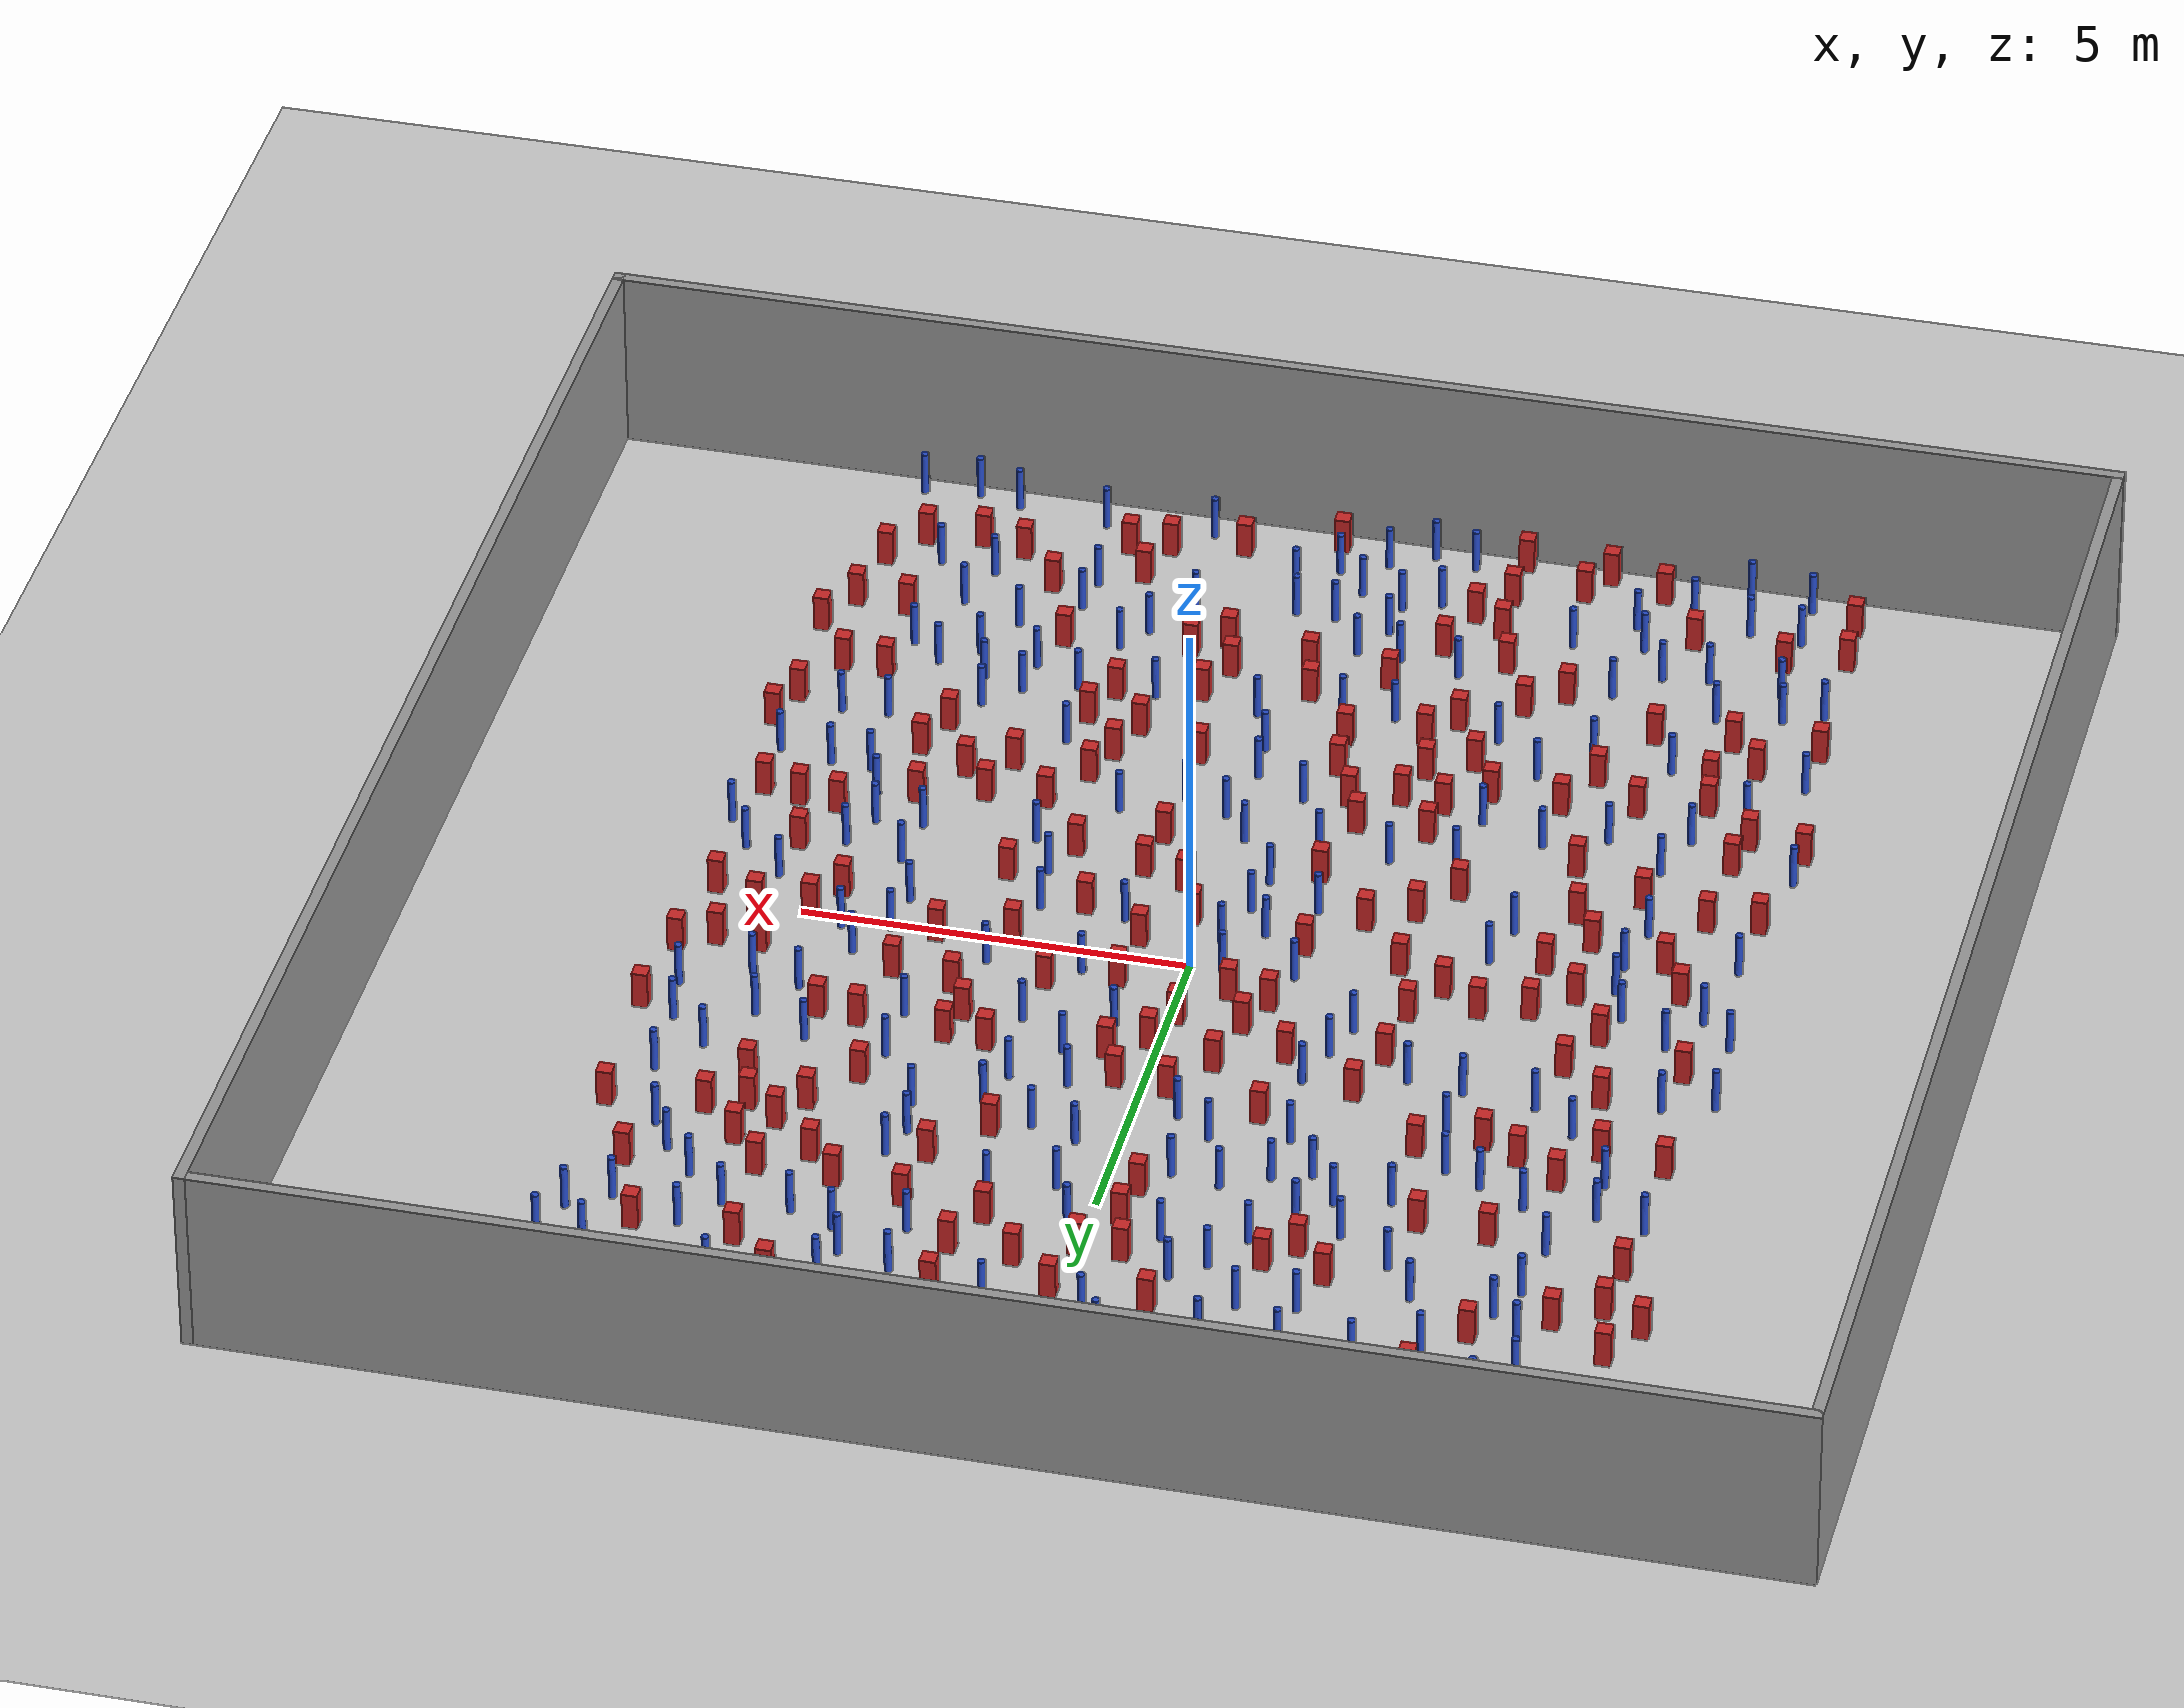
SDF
<sdf version="1.6">
 <world name="default">
  <light name="sun" type="directional">
   <pose>0 0 1000 0 -0 0</pose>
   <diffuse>0.8 0.8 0.8 1</diffuse>
   <specular>0.1 0.1 0.1 1</specular>
   <attenuation>
    <range>1000</range>
    <constant>0.9</constant>
    <linear>0.01</linear>
    <quadratic>0.001</quadratic>
   </attenuation>
   <direction>-0.5 0.5 -1</direction>
  </light>
  <model name="ground_plane">
   <static>1</static>
   <link name="link">
    <collision name="collision">
     <geometry><plane><normal>0 0 1</normal><size>100 100</size></plane></geometry>
     <surface><friction><ode><mu>100</mu><mu2>50</mu2></ode></friction></surface>
    </collision>
    <visual name="visual">
     <cast_shadows>0</cast_shadows>
     <geometry><plane><normal>0 0 1</normal><size>100 100</size></plane></geometry>
     <material>
      <ambient>1.0 1.0 1.0 1.0</ambient>
      <diffuse>0.8 0.8 0.8 1.0</diffuse>
      <specular>0.01 0.01 0.01 1.000000</specular>
     </material>
    </visual>
   </link>
  </model>
  <gravity>0 0 -9.8</gravity>
  <magnetic_field>6e-06 2.3e-05 -4.2e-05</magnetic_field>
  <atmosphere type="adiabatic"/>
  <physics name="default_physics" default="0" type="ode">
   <max_step_size>0.001</max_step_size>
   <real_time_factor>1</real_time_factor>
   <real_time_update_rate>1000</real_time_update_rate>
  </physics>
  <scene><ambient>0.4 0.4 0.4 1</ambient><background>0.7 0.7 0.7 1</background><shadows>1</shadows></scene>
  <spherical_coordinates>
   <surface_model>EARTH_WGS84</surface_model>
   <latitude_deg>0</latitude_deg>
   <longitude_deg>0</longitude_deg>
   <elevation>0</elevation>
   <heading_deg>0</heading_deg>
  </spherical_coordinates>
  <plugin name="gazebo_occupancy_map" filename="libgazebo_2Dmap_plugin.so">
   <map_resolution>0.05</map_resolution>
   <map_topic>generated_map</map_topic>
   <map_height>0.01</map_height>
   <map_size_x>50</map_size_x>
   <map_size_y>50</map_size_y>
  </plugin>
  <model name="NamedLocations">
   <static>true</static>
   <link name="DefaultStart"><pose>8.5 0 0 0 0 3.14</pose></link>
  </model>
  <model name="20x20_walls">
   <pose>0.044518 0.176112 0 0 -0 0</pose>
   <link name="Wall_1">
    <collision name="Wall_1_Collision">
     <geometry><box><size>20 0.15 2.5</size></box></geometry>
     <pose>0 0 1.25 0 -0 0</pose>
    </collision>
    <visual name="Wall_1_Visual">
     <pose>0 0 1.25 0 -0 0</pose>
     <geometry><box><size>20 0.15 2.5</size></box></geometry>
     <material>
      <script><uri>file://media/materials/scripts/gazebo.material</uri><name>Gazebo/Grey</name></script>
      <ambient>0.976471 0.992157 1 1</ambient>
     </material>
     <meta><layer>0</layer></meta>
    </visual>
    <pose>0 9.925 0 0 -0 0</pose>
   </link>
   <link name="Wall_3">
    <collision name="Wall_3_Collision">
     <geometry><box><size>20 0.15 2.5</size></box></geometry>
     <pose>0 0 1.25 0 -0 0</pose>
    </collision>
    <visual name="Wall_3_Visual">
     <pose>0 0 1.25 0 -0 0</pose>
     <geometry><box><size>20 0.15 2.5</size></box></geometry>
     <material>
      <script><uri>file://media/materials/scripts/gazebo.material</uri><name>Gazebo/Grey</name></script>
      <ambient>0.976471 0.992157 1 1</ambient>
     </material>
     <meta><layer>0</layer></meta>
    </visual>
    <pose>9.925 0 0 0 0 -1.5708</pose>
   </link>
   <link name="Wall_4">
    <collision name="Wall_4_Collision">
     <geometry><box><size>20 0.15 2.5</size></box></geometry>
     <pose>0 0 1.25 0 -0 0</pose>
    </collision>
    <visual name="Wall_4_Visual">
     <pose>0 0 1.25 0 -0 0</pose>
     <geometry><box><size>20 0.15 2.5</size></box></geometry>
     <material>
      <script><uri>file://media/materials/scripts/gazebo.material</uri><name>Gazebo/Grey</name></script>
      <ambient>0.976471 0.992157 1 1</ambient>
     </material>
     <meta><layer>0</layer></meta>
    </visual>
    <pose>0 -9.925 0 0 -0 3.14159</pose>
   </link>
   <link name="Wall_5">
    <collision name="Wall_5_Collision">
     <geometry><box><size>20 0.15 2.5</size></box></geometry>
     <pose>0 0 1.25 0 -0 0</pose>
    </collision>
    <visual name="Wall_5_Visual">
     <pose>0 0 1.25 0 -0 0</pose>
     <geometry><box><size>20 0.15 2.5</size></box></geometry>
     <material>
      <script><uri>file://media/materials/scripts/gazebo.material</uri><name>Gazebo/Grey</name></script>
      <ambient>0.976471 0.992157 1 1</ambient>
     </material>
     <meta><layer>0</layer></meta>
    </visual>
    <pose>-9.925 0 0 0 -0 1.5708</pose>
   </link>
   <static>1</static>
  </model>
  <model name="square_post_obstacle0">
   <static>true</static>
   <pose>-3.55596763186 3.06718040949 1.91545236811e-07 -7.35059704564e-06 1.12565212e-07 2.39332434364e-05</pose>
   <link name="link">
    <pose>0 0 0.25 0 -0 0</pose>
    <inertial>
     <mass>100</mass>
     <inertia>
      <ixx>0.166667</ixx>
      <ixy>0</ixy>
      <ixz>0</ixz>
      <iyy>0.166667</iyy>
      <iyz>0</iyz>
      <izz>0.166667</izz>
     </inertia>
    </inertial>
    <collision name="collision"><geometry><box><size>.2 .2 .5</size></box></geometry></collision>
    <visual name="visual">
     <geometry><box><size>.2 .2 .5</size></box></geometry>
     <material>
      <script><name>Gazebo/Red</name><uri>file://media/materials/scripts/gazebo.material</uri></script>
     </material>
    </visual>
   </link>
  </model>
  <model name="square_post_obstacle1">
   <static>true</static>
   <pose>2.30079140672 -0.113341108883 1.91545236811e-07 -7.35059704564e-06 1.12565212e-07 2.39332434364e-05</pose>
   <link name="link">
    <pose>0 0 0.25 0 -0 0</pose>
    <inertial>
     <mass>100</mass>
     <inertia>
      <ixx>0.166667</ixx>
      <ixy>0</ixy>
      <ixz>0</ixz>
      <iyy>0.166667</iyy>
      <iyz>0</iyz>
      <izz>0.166667</izz>
     </inertia>
    </inertial>
    <collision name="collision"><geometry><box><size>.2 .2 .5</size></box></geometry></collision>
    <visual name="visual">
     <geometry><box><size>.2 .2 .5</size></box></geometry>
     <material>
      <script><name>Gazebo/Red</name><uri>file://media/materials/scripts/gazebo.material</uri></script>
     </material>
    </visual>
   </link>
  </model>
  <model name="pole_obstacle0">
   <static>true</static>
   <pose>-0.643365630243 -5.73914750013 7.38925637345e-09 -8.471706928e-08 1.24976765086e-08 -1.74513093015e-07</pose>
   <link name="link">
    <pose>0 0 0.3 0 -0 0</pose>
    <inertial>
     <mass>1</mass>
     <inertia><ixx>0.145833</ixx><ixy>0</ixy><ixz>0</ixz><iyy>0.145833</iyy><iyz>0</iyz><izz>0.125</izz></inertia>
    </inertial>
    <collision name="collision">
     <geometry><cylinder><radius>0.05</radius><length>.6</length></cylinder></geometry>
    </collision>
    <visual name="visual">
     <geometry><cylinder><radius>0.05</radius><length>.6</length></cylinder></geometry>
     <material>
      <script><name>Gazebo/Blue</name><uri>file://media/materials/scripts/gazebo.material</uri></script>
     </material>
    </visual>
   </link>
  </model>
  <model name="square_post_obstacle2">
   <static>true</static>
   <pose>-1.97392428665 -4.67778224136 1.91545236811e-07 -7.35059704564e-06 1.12565212e-07 2.39332434364e-05</pose>
   <link name="link">
    <pose>0 0 0.25 0 -0 0</pose>
    <inertial>
     <mass>100</mass>
     <inertia>
      <ixx>0.166667</ixx>
      <ixy>0</ixy>
      <ixz>0</ixz>
      <iyy>0.166667</iyy>
      <iyz>0</iyz>
      <izz>0.166667</izz>
     </inertia>
    </inertial>
    <collision name="collision"><geometry><box><size>.2 .2 .5</size></box></geometry></collision>
    <visual name="visual">
     <geometry><box><size>.2 .2 .5</size></box></geometry>
     <material>
      <script><name>Gazebo/Red</name><uri>file://media/materials/scripts/gazebo.material</uri></script>
     </material>
    </visual>
   </link>
  </model>
  <model name="pole_obstacle1">
   <static>true</static>
   <pose>2.11567827239 -0.791708799903 7.38925637345e-09 -8.471706928e-08 1.24976765177e-08 -1.74513093012e-07</pose>
   <link name="link">
    <pose>0 0 0.3 0 -0 0</pose>
    <inertial>
     <mass>1</mass>
     <inertia><ixx>0.145833</ixx><ixy>0</ixy><ixz>0</ixz><iyy>0.145833</iyy><iyz>0</iyz><izz>0.125</izz></inertia>
    </inertial>
    <collision name="collision">
     <geometry><cylinder><radius>0.05</radius><length>.6</length></cylinder></geometry>
    </collision>
    <visual name="visual">
     <geometry><cylinder><radius>0.05</radius><length>.6</length></cylinder></geometry>
     <material>
      <script><name>Gazebo/Blue</name><uri>file://media/materials/scripts/gazebo.material</uri></script>
     </material>
    </visual>
   </link>
  </model>
  <model name="square_post_obstacle3">
   <static>true</static>
   <pose>5.82159080179 5.45630986029 1.91545236811e-07 -7.35059704564e-06 1.12565212e-07 2.39332434364e-05</pose>
   <link name="link">
    <pose>0 0 0.25 0 -0 0</pose>
    <inertial>
     <mass>100</mass>
     <inertia>
      <ixx>0.166667</ixx>
      <ixy>0</ixy>
      <ixz>0</ixz>
      <iyy>0.166667</iyy>
      <iyz>0</iyz>
      <izz>0.166667</izz>
     </inertia>
    </inertial>
    <collision name="collision"><geometry><box><size>.2 .2 .5</size></box></geometry></collision>
    <visual name="visual">
     <geometry><box><size>.2 .2 .5</size></box></geometry>
     <material>
      <script><name>Gazebo/Red</name><uri>file://media/materials/scripts/gazebo.material</uri></script>
     </material>
    </visual>
   </link>
  </model>
  <model name="pole_obstacle2">
   <static>true</static>
   <pose>6.14572191631 -3.33567524918 7.38925637345e-09 -8.47170692798e-08 1.24976764937e-08 -1.74513093023e-07</pose>
   <link name="link">
    <pose>0 0 0.3 0 -0 0</pose>
    <inertial>
     <mass>1</mass>
     <inertia><ixx>0.145833</ixx><ixy>0</ixy><ixz>0</ixz><iyy>0.145833</iyy><iyz>0</iyz><izz>0.125</izz></inertia>
    </inertial>
    <collision name="collision">
     <geometry><cylinder><radius>0.05</radius><length>.6</length></cylinder></geometry>
    </collision>
    <visual name="visual">
     <geometry><cylinder><radius>0.05</radius><length>.6</length></cylinder></geometry>
     <material>
      <script><name>Gazebo/Blue</name><uri>file://media/materials/scripts/gazebo.material</uri></script>
     </material>
    </visual>
   </link>
  </model>
  <model name="pole_obstacle3">
   <static>true</static>
   <pose>-2.89417251278 -3.81996052843 7.38925637345e-09 -8.47170692798e-08 1.24976764939e-08 -1.74513093025e-07</pose>
   <link name="link">
    <pose>0 0 0.3 0 -0 0</pose>
    <inertial>
     <mass>1</mass>
     <inertia><ixx>0.145833</ixx><ixy>0</ixy><ixz>0</ixz><iyy>0.145833</iyy><iyz>0</iyz><izz>0.125</izz></inertia>
    </inertial>
    <collision name="collision">
     <geometry><cylinder><radius>0.05</radius><length>.6</length></cylinder></geometry>
    </collision>
    <visual name="visual">
     <geometry><cylinder><radius>0.05</radius><length>.6</length></cylinder></geometry>
     <material>
      <script><name>Gazebo/Blue</name><uri>file://media/materials/scripts/gazebo.material</uri></script>
     </material>
    </visual>
   </link>
  </model>
  <model name="square_post_obstacle4">
   <static>true</static>
   <pose>-2.54340053731 -4.98946207609 1.91545236811e-07 -7.35059704564e-06 1.12565212e-07 2.39332434364e-05</pose>
   <link name="link">
    <pose>0 0 0.25 0 -0 0</pose>
    <inertial>
     <mass>100</mass>
     <inertia>
      <ixx>0.166667</ixx>
      <ixy>0</ixy>
      <ixz>0</ixz>
      <iyy>0.166667</iyy>
      <iyz>0</iyz>
      <izz>0.166667</izz>
     </inertia>
    </inertial>
    <collision name="collision"><geometry><box><size>.2 .2 .5</size></box></geometry></collision>
    <visual name="visual">
     <geometry><box><size>.2 .2 .5</size></box></geometry>
     <material>
      <script><name>Gazebo/Red</name><uri>file://media/materials/scripts/gazebo.material</uri></script>
     </material>
    </visual>
   </link>
  </model>
  <model name="square_post_obstacle5">
   <static>true</static>
   <pose>4.39867281722 -3.73941172745 1.91545236811e-07 -7.35059704564e-06 1.12565212e-07 2.39332434364e-05</pose>
   <link name="link">
    <pose>0 0 0.25 0 -0 0</pose>
    <inertial>
     <mass>100</mass>
     <inertia>
      <ixx>0.166667</ixx>
      <ixy>0</ixy>
      <ixz>0</ixz>
      <iyy>0.166667</iyy>
      <iyz>0</iyz>
      <izz>0.166667</izz>
     </inertia>
    </inertial>
    <collision name="collision"><geometry><box><size>.2 .2 .5</size></box></geometry></collision>
    <visual name="visual">
     <geometry><box><size>.2 .2 .5</size></box></geometry>
     <material>
      <script><name>Gazebo/Red</name><uri>file://media/materials/scripts/gazebo.material</uri></script>
     </material>
    </visual>
   </link>
  </model>
  <model name="square_post_obstacle6">
   <static>true</static>
   <pose>-4.81822613164 -0.429306550397 1.91545236811e-07 -7.35059704564e-06 1.12565212e-07 2.39332434364e-05</pose>
   <link name="link">
    <pose>0 0 0.25 0 -0 0</pose>
    <inertial>
     <mass>100</mass>
     <inertia>
      <ixx>0.166667</ixx>
      <ixy>0</ixy>
      <ixz>0</ixz>
      <iyy>0.166667</iyy>
      <iyz>0</iyz>
      <izz>0.166667</izz>
     </inertia>
    </inertial>
    <collision name="collision"><geometry><box><size>.2 .2 .5</size></box></geometry></collision>
    <visual name="visual">
     <geometry><box><size>.2 .2 .5</size></box></geometry>
     <material>
      <script><name>Gazebo/Red</name><uri>file://media/materials/scripts/gazebo.material</uri></script>
     </material>
    </visual>
   </link>
  </model>
  <model name="pole_obstacle4">
   <static>true</static>
   <pose>-6.87340431811 9.03791344532 7.38925637345e-09 -8.471706928e-08 1.24976765081e-08 -1.74513093015e-07</pose>
   <link name="link">
    <pose>0 0 0.3 0 -0 0</pose>
    <inertial>
     <mass>1</mass>
     <inertia><ixx>0.145833</ixx><ixy>0</ixy><ixz>0</ixz><iyy>0.145833</iyy><iyz>0</iyz><izz>0.125</izz></inertia>
    </inertial>
    <collision name="collision">
     <geometry><cylinder><radius>0.05</radius><length>.6</length></cylinder></geometry>
    </collision>
    <visual name="visual">
     <geometry><cylinder><radius>0.05</radius><length>.6</length></cylinder></geometry>
     <material>
      <script><name>Gazebo/Blue</name><uri>file://media/materials/scripts/gazebo.material</uri></script>
     </material>
    </visual>
   </link>
  </model>
  <model name="pole_obstacle5">
   <static>true</static>
   <pose>-2.81162982472 4.31498104708 7.38925637345e-09 -8.47170692798e-08 1.24976765033e-08 -1.74513093019e-07</pose>
   <link name="link">
    <pose>0 0 0.3 0 -0 0</pose>
    <inertial>
     <mass>1</mass>
     <inertia><ixx>0.145833</ixx><ixy>0</ixy><ixz>0</ixz><iyy>0.145833</iyy><iyz>0</iyz><izz>0.125</izz></inertia>
    </inertial>
    <collision name="collision">
     <geometry><cylinder><radius>0.05</radius><length>.6</length></cylinder></geometry>
    </collision>
    <visual name="visual">
     <geometry><cylinder><radius>0.05</radius><length>.6</length></cylinder></geometry>
     <material>
      <script><name>Gazebo/Blue</name><uri>file://media/materials/scripts/gazebo.material</uri></script>
     </material>
    </visual>
   </link>
  </model>
  <model name="square_post_obstacle7">
   <static>true</static>
   <pose>0.733176663758 -0.373524283608 1.91545236811e-07 -7.35059704564e-06 1.12565212e-07 2.39332434364e-05</pose>
   <link name="link">
    <pose>0 0 0.25 0 -0 0</pose>
    <inertial>
     <mass>100</mass>
     <inertia>
      <ixx>0.166667</ixx>
      <ixy>0</ixy>
      <ixz>0</ixz>
      <iyy>0.166667</iyy>
      <iyz>0</iyz>
      <izz>0.166667</izz>
     </inertia>
    </inertial>
    <collision name="collision"><geometry><box><size>.2 .2 .5</size></box></geometry></collision>
    <visual name="visual">
     <geometry><box><size>.2 .2 .5</size></box></geometry>
     <material>
      <script><name>Gazebo/Red</name><uri>file://media/materials/scripts/gazebo.material</uri></script>
     </material>
    </visual>
   </link>
  </model>
  <model name="square_post_obstacle8">
   <static>true</static>
   <pose>-0.546934222434 5.92013509741 1.91545236811e-07 -7.35059704564e-06 1.12565212e-07 2.39332434364e-05</pose>
   <link name="link">
    <pose>0 0 0.25 0 -0 0</pose>
    <inertial>
     <mass>100</mass>
     <inertia>
      <ixx>0.166667</ixx>
      <ixy>0</ixy>
      <ixz>0</ixz>
      <iyy>0.166667</iyy>
      <iyz>0</iyz>
      <izz>0.166667</izz>
     </inertia>
    </inertial>
    <collision name="collision"><geometry><box><size>.2 .2 .5</size></box></geometry></collision>
    <visual name="visual">
     <geometry><box><size>.2 .2 .5</size></box></geometry>
     <material>
      <script><name>Gazebo/Red</name><uri>file://media/materials/scripts/gazebo.material</uri></script>
     </material>
    </visual>
   </link>
  </model>
  <model name="pole_obstacle6">
   <static>true</static>
   <pose>3.22004854573 1.77578867734 7.38925637345e-09 -8.471706928e-08 1.24976765152e-08 -1.74513093012e-07</pose>
   <link name="link">
    <pose>0 0 0.3 0 -0 0</pose>
    <inertial>
     <mass>1</mass>
     <inertia><ixx>0.145833</ixx><ixy>0</ixy><ixz>0</ixz><iyy>0.145833</iyy><iyz>0</iyz><izz>0.125</izz></inertia>
    </inertial>
    <collision name="collision">
     <geometry><cylinder><radius>0.05</radius><length>.6</length></cylinder></geometry>
    </collision>
    <visual name="visual">
     <geometry><cylinder><radius>0.05</radius><length>.6</length></cylinder></geometry>
     <material>
      <script><name>Gazebo/Blue</name><uri>file://media/materials/scripts/gazebo.material</uri></script>
     </material>
    </visual>
   </link>
  </model>
  <model name="pole_obstacle7">
   <static>true</static>
   <pose>3.00797977638 6.1850498163 7.38925637345e-09 -8.47170692798e-08 1.24976765033e-08 -1.74513093019e-07</pose>
   <link name="link">
    <pose>0 0 0.3 0 -0 0</pose>
    <inertial>
     <mass>1</mass>
     <inertia><ixx>0.145833</ixx><ixy>0</ixy><ixz>0</ixz><iyy>0.145833</iyy><iyz>0</iyz><izz>0.125</izz></inertia>
    </inertial>
    <collision name="collision">
     <geometry><cylinder><radius>0.05</radius><length>.6</length></cylinder></geometry>
    </collision>
    <visual name="visual">
     <geometry><cylinder><radius>0.05</radius><length>.6</length></cylinder></geometry>
     <material>
      <script><name>Gazebo/Blue</name><uri>file://media/materials/scripts/gazebo.material</uri></script>
     </material>
    </visual>
   </link>
  </model>
  <model name="square_post_obstacle9">
   <static>true</static>
   <pose>5.31786729422 0.826178670648 1.91545236811e-07 -7.35059704564e-06 1.12565212e-07 2.39332434364e-05</pose>
   <link name="link">
    <pose>0 0 0.25 0 -0 0</pose>
    <inertial>
     <mass>100</mass>
     <inertia>
      <ixx>0.166667</ixx>
      <ixy>0</ixy>
      <ixz>0</ixz>
      <iyy>0.166667</iyy>
      <iyz>0</iyz>
      <izz>0.166667</izz>
     </inertia>
    </inertial>
    <collision name="collision"><geometry><box><size>.2 .2 .5</size></box></geometry></collision>
    <visual name="visual">
     <geometry><box><size>.2 .2 .5</size></box></geometry>
     <material>
      <script><name>Gazebo/Red</name><uri>file://media/materials/scripts/gazebo.material</uri></script>
     </material>
    </visual>
   </link>
  </model>
  <model name="square_post_obstacle10">
   <static>true</static>
   <pose>0.908520756154 -4.35322302698 1.91545236811e-07 -7.35059704564e-06 1.12565212e-07 2.39332434364e-05</pose>
   <link name="link">
    <pose>0 0 0.25 0 -0 0</pose>
    <inertial>
     <mass>100</mass>
     <inertia>
      <ixx>0.166667</ixx>
      <ixy>0</ixy>
      <ixz>0</ixz>
      <iyy>0.166667</iyy>
      <iyz>0</iyz>
      <izz>0.166667</izz>
     </inertia>
    </inertial>
    <collision name="collision"><geometry><box><size>.2 .2 .5</size></box></geometry></collision>
    <visual name="visual">
     <geometry><box><size>.2 .2 .5</size></box></geometry>
     <material>
      <script><name>Gazebo/Red</name><uri>file://media/materials/scripts/gazebo.material</uri></script>
     </material>
    </visual>
   </link>
  </model>
  <model name="square_post_obstacle11">
   <static>true</static>
   <pose>-4.27293090781 -3.06913041119 1.91545236811e-07 -7.35059704564e-06 1.12565212e-07 2.39332434364e-05</pose>
   <link name="link">
    <pose>0 0 0.25 0 -0 0</pose>
    <inertial>
     <mass>100</mass>
     <inertia>
      <ixx>0.166667</ixx>
      <ixy>0</ixy>
      <ixz>0</ixz>
      <iyy>0.166667</iyy>
      <iyz>0</iyz>
      <izz>0.166667</izz>
     </inertia>
    </inertial>
    <collision name="collision"><geometry><box><size>.2 .2 .5</size></box></geometry></collision>
    <visual name="visual">
     <geometry><box><size>.2 .2 .5</size></box></geometry>
     <material>
      <script><name>Gazebo/Red</name><uri>file://media/materials/scripts/gazebo.material</uri></script>
     </material>
    </visual>
   </link>
  </model>
  <model name="square_post_obstacle12">
   <static>true</static>
   <pose>-3.90689282888 4.53653102175 1.91545236811e-07 -7.35059704564e-06 1.12565212e-07 2.39332434364e-05</pose>
   <link name="link">
    <pose>0 0 0.25 0 -0 0</pose>
    <inertial>
     <mass>100</mass>
     <inertia>
      <ixx>0.166667</ixx>
      <ixy>0</ixy>
      <ixz>0</ixz>
      <iyy>0.166667</iyy>
      <iyz>0</iyz>
      <izz>0.166667</izz>
     </inertia>
    </inertial>
    <collision name="collision"><geometry><box><size>.2 .2 .5</size></box></geometry></collision>
    <visual name="visual">
     <geometry><box><size>.2 .2 .5</size></box></geometry>
     <material>
      <script><name>Gazebo/Red</name><uri>file://media/materials/scripts/gazebo.material</uri></script>
     </material>
    </visual>
   </link>
  </model>
  <model name="square_post_obstacle13">
   <static>true</static>
   <pose>5.39153406921 -1.39861252525 1.91545236811e-07 -7.35059704564e-06 1.12565212e-07 2.39332434364e-05</pose>
   <link name="link">
    <pose>0 0 0.25 0 -0 0</pose>
    <inertial>
     <mass>100</mass>
     <inertia>
      <ixx>0.166667</ixx>
      <ixy>0</ixy>
      <ixz>0</ixz>
      <iyy>0.166667</iyy>
      <iyz>0</iyz>
      <izz>0.166667</izz>
     </inertia>
    </inertial>
    <collision name="collision"><geometry><box><size>.2 .2 .5</size></box></geometry></collision>
    <visual name="visual">
     <geometry><box><size>.2 .2 .5</size></box></geometry>
     <material>
      <script><name>Gazebo/Red</name><uri>file://media/materials/scripts/gazebo.material</uri></script>
     </material>
    </visual>
   </link>
  </model>
  <model name="pole_obstacle8">
   <static>true</static>
   <pose>5.99474519024 2.49112717704 7.38925637345e-09 -8.47170692798e-08 1.24976764937e-08 -1.74513093023e-07</pose>
   <link name="link">
    <pose>0 0 0.3 0 -0 0</pose>
    <inertial>
     <mass>1</mass>
     <inertia><ixx>0.145833</ixx><ixy>0</ixy><ixz>0</ixz><iyy>0.145833</iyy><iyz>0</iyz><izz>0.125</izz></inertia>
    </inertial>
    <collision name="collision">
     <geometry><cylinder><radius>0.05</radius><length>.6</length></cylinder></geometry>
    </collision>
    <visual name="visual">
     <geometry><cylinder><radius>0.05</radius><length>.6</length></cylinder></geometry>
     <material>
      <script><name>Gazebo/Blue</name><uri>file://media/materials/scripts/gazebo.material</uri></script>
     </material>
    </visual>
   </link>
  </model>
  <model name="square_post_obstacle14">
   <static>true</static>
   <pose>2.77395277355 1.11454945893 1.91545236811e-07 -7.35059704564e-06 1.12565212e-07 2.39332434364e-05</pose>
   <link name="link">
    <pose>0 0 0.25 0 -0 0</pose>
    <inertial>
     <mass>100</mass>
     <inertia>
      <ixx>0.166667</ixx>
      <ixy>0</ixy>
      <ixz>0</ixz>
      <iyy>0.166667</iyy>
      <iyz>0</iyz>
      <izz>0.166667</izz>
     </inertia>
    </inertial>
    <collision name="collision"><geometry><box><size>.2 .2 .5</size></box></geometry></collision>
    <visual name="visual">
     <geometry><box><size>.2 .2 .5</size></box></geometry>
     <material>
      <script><name>Gazebo/Red</name><uri>file://media/materials/scripts/gazebo.material</uri></script>
     </material>
    </visual>
   </link>
  </model>
  <model name="square_post_obstacle15">
   <static>true</static>
   <pose>1.01795629702 -1.82561163222 1.91545236811e-07 -7.35059704564e-06 1.12565212e-07 2.39332434364e-05</pose>
   <link name="link">
    <pose>0 0 0.25 0 -0 0</pose>
    <inertial>
     <mass>100</mass>
     <inertia>
      <ixx>0.166667</ixx>
      <ixy>0</ixy>
      <ixz>0</ixz>
      <iyy>0.166667</iyy>
      <iyz>0</iyz>
      <izz>0.166667</izz>
     </inertia>
    </inertial>
    <collision name="collision"><geometry><box><size>.2 .2 .5</size></box></geometry></collision>
    <visual name="visual">
     <geometry><box><size>.2 .2 .5</size></box></geometry>
     <material>
      <script><name>Gazebo/Red</name><uri>file://media/materials/scripts/gazebo.material</uri></script>
     </material>
    </visual>
   </link>
  </model>
  <model name="square_post_obstacle16">
   <static>true</static>
   <pose>4.59854409013 -0.532294423076 1.91545236811e-07 -7.35059704564e-06 1.12565212e-07 2.39332434364e-05</pose>
   <link name="link">
    <pose>0 0 0.25 0 -0 0</pose>
    <inertial>
     <mass>100</mass>
     <inertia>
      <ixx>0.166667</ixx>
      <ixy>0</ixy>
      <ixz>0</ixz>
      <iyy>0.166667</iyy>
      <iyz>0</iyz>
      <izz>0.166667</izz>
     </inertia>
    </inertial>
    <collision name="collision"><geometry><box><size>.2 .2 .5</size></box></geometry></collision>
    <visual name="visual">
     <geometry><box><size>.2 .2 .5</size></box></geometry>
     <material>
      <script><name>Gazebo/Red</name><uri>file://media/materials/scripts/gazebo.material</uri></script>
     </material>
    </visual>
   </link>
  </model>
  <model name="pole_obstacle9">
   <static>true</static>
   <pose>-3.9550344952 -5.57008247758 7.38925637345e-09 -8.47170692799e-08 1.24976764985e-08 -1.74513093022e-07</pose>
   <link name="link">
    <pose>0 0 0.3 0 -0 0</pose>
    <inertial>
     <mass>1</mass>
     <inertia><ixx>0.145833</ixx><ixy>0</ixy><ixz>0</ixz><iyy>0.145833</iyy><iyz>0</iyz><izz>0.125</izz></inertia>
    </inertial>
    <collision name="collision">
     <geometry><cylinder><radius>0.05</radius><length>.6</length></cylinder></geometry>
    </collision>
    <visual name="visual">
     <geometry><cylinder><radius>0.05</radius><length>.6</length></cylinder></geometry>
     <material>
      <script><name>Gazebo/Blue</name><uri>file://media/materials/scripts/gazebo.material</uri></script>
     </material>
    </visual>
   </link>
  </model>
  <model name="square_post_obstacle17">
   <static>true</static>
   <pose>4.15785183296 -8.27256191377 1.91545236811e-07 -7.35059704564e-06 1.12565212e-07 2.39332434364e-05</pose>
   <link name="link">
    <pose>0 0 0.25 0 -0 0</pose>
    <inertial>
     <mass>100</mass>
     <inertia>
      <ixx>0.166667</ixx>
      <ixy>0</ixy>
      <ixz>0</ixz>
      <iyy>0.166667</iyy>
      <iyz>0</iyz>
      <izz>0.166667</izz>
     </inertia>
    </inertial>
    <collision name="collision"><geometry><box><size>.2 .2 .5</size></box></geometry></collision>
    <visual name="visual">
     <geometry><box><size>.2 .2 .5</size></box></geometry>
     <material>
      <script><name>Gazebo/Red</name><uri>file://media/materials/scripts/gazebo.material</uri></script>
     </material>
    </visual>
   </link>
  </model>
  <model name="square_post_obstacle18">
   <static>true</static>
   <pose>-0.758517951045 1.95636640092 1.91545236811e-07 -7.35059704564e-06 1.12565212e-07 2.39332434364e-05</pose>
   <link name="link">
    <pose>0 0 0.25 0 -0 0</pose>
    <inertial>
     <mass>100</mass>
     <inertia>
      <ixx>0.166667</ixx>
      <ixy>0</ixy>
      <ixz>0</ixz>
      <iyy>0.166667</iyy>
      <iyz>0</iyz>
      <izz>0.166667</izz>
     </inertia>
    </inertial>
    <collision name="collision"><geometry><box><size>.2 .2 .5</size></box></geometry></collision>
    <visual name="visual">
     <geometry><box><size>.2 .2 .5</size></box></geometry>
     <material>
      <script><name>Gazebo/Red</name><uri>file://media/materials/scripts/gazebo.material</uri></script>
     </material>
    </visual>
   </link>
  </model>
  <model name="pole_obstacle10">
   <static>true</static>
   <pose>6.03867695936 -1.1972389349 7.38925637345e-09 -8.471706928e-08 1.24976765134e-08 -1.74513093015e-07</pose>
   <link name="link">
    <pose>0 0 0.3 0 -0 0</pose>
    <inertial>
     <mass>1</mass>
     <inertia><ixx>0.145833</ixx><ixy>0</ixy><ixz>0</ixz><iyy>0.145833</iyy><iyz>0</iyz><izz>0.125</izz></inertia>
    </inertial>
    <collision name="collision">
     <geometry><cylinder><radius>0.05</radius><length>.6</length></cylinder></geometry>
    </collision>
    <visual name="visual">
     <geometry><cylinder><radius>0.05</radius><length>.6</length></cylinder></geometry>
     <material>
      <script><name>Gazebo/Blue</name><uri>file://media/materials/scripts/gazebo.material</uri></script>
     </material>
    </visual>
   </link>
  </model>
  <model name="square_post_obstacle19">
   <static>true</static>
   <pose>-1.80339025722 -5.40434559586 1.91545236811e-07 -7.35059704564e-06 1.12565212e-07 2.39332434364e-05</pose>
   <link name="link">
    <pose>0 0 0.25 0 -0 0</pose>
    <inertial>
     <mass>100</mass>
     <inertia>
      <ixx>0.166667</ixx>
      <ixy>0</ixy>
      <ixz>0</ixz>
      <iyy>0.166667</iyy>
      <iyz>0</iyz>
      <izz>0.166667</izz>
     </inertia>
    </inertial>
    <collision name="collision"><geometry><box><size>.2 .2 .5</size></box></geometry></collision>
    <visual name="visual">
     <geometry><box><size>.2 .2 .5</size></box></geometry>
     <material>
      <script><name>Gazebo/Red</name><uri>file://media/materials/scripts/gazebo.material</uri></script>
     </material>
    </visual>
   </link>
  </model>
  <model name="pole_obstacle11">
   <static>true</static>
   <pose>-5.07678339914 3.88739832947 7.38925637345e-09 -8.47170692798e-08 1.24976764937e-08 -1.74513093023e-07</pose>
   <link name="link">
    <pose>0 0 0.3 0 -0 0</pose>
    <inertial>
     <mass>1</mass>
     <inertia><ixx>0.145833</ixx><ixy>0</ixy><ixz>0</ixz><iyy>0.145833</iyy><iyz>0</iyz><izz>0.125</izz></inertia>
    </inertial>
    <collision name="collision">
     <geometry><cylinder><radius>0.05</radius><length>.6</length></cylinder></geometry>
    </collision>
    <visual name="visual">
     <geometry><cylinder><radius>0.05</radius><length>.6</length></cylinder></geometry>
     <material>
      <script><name>Gazebo/Blue</name><uri>file://media/materials/scripts/gazebo.material</uri></script>
     </material>
    </visual>
   </link>
  </model>
  <model name="square_post_obstacle20">
   <static>true</static>
   <pose>-4.96539036442 6.52452022297 1.91545236811e-07 -7.35059704564e-06 1.12565212e-07 2.39332434364e-05</pose>
   <link name="link">
    <pose>0 0 0.25 0 -0 0</pose>
    <inertial>
     <mass>100</mass>
     <inertia>
      <ixx>0.166667</ixx>
      <ixy>0</ixy>
      <ixz>0</ixz>
      <iyy>0.166667</iyy>
      <iyz>0</iyz>
      <izz>0.166667</izz>
     </inertia>
    </inertial>
    <collision name="collision"><geometry><box><size>.2 .2 .5</size></box></geometry></collision>
    <visual name="visual">
     <geometry><box><size>.2 .2 .5</size></box></geometry>
     <material>
      <script><name>Gazebo/Red</name><uri>file://media/materials/scripts/gazebo.material</uri></script>
     </material>
    </visual>
   </link>
  </model>
  <model name="pole_obstacle12">
   <static>true</static>
   <pose>4.17921115617 0.650031408864 7.38925637345e-09 -8.47170692799e-08 1.24976765038e-08 -1.74513093018e-07</pose>
   <link name="link">
    <pose>0 0 0.3 0 -0 0</pose>
    <inertial>
     <mass>1</mass>
     <inertia><ixx>0.145833</ixx><ixy>0</ixy><ixz>0</ixz><iyy>0.145833</iyy><iyz>0</iyz><izz>0.125</izz></inertia>
    </inertial>
    <collision name="collision">
     <geometry><cylinder><radius>0.05</radius><length>.6</length></cylinder></geometry>
    </collision>
    <visual name="visual">
     <geometry><cylinder><radius>0.05</radius><length>.6</length></cylinder></geometry>
     <material>
      <script><name>Gazebo/Blue</name><uri>file://media/materials/scripts/gazebo.material</uri></script>
     </material>
    </visual>
   </link>
  </model>
  <model name="square_post_obstacle21">
   <static>true</static>
   <pose>-5.22307568444 -2.58926652539 1.91545236811e-07 -7.35059704564e-06 1.12565212e-07 2.39332434364e-05</pose>
   <link name="link">
    <pose>0 0 0.25 0 -0 0</pose>
    <inertial>
     <mass>100</mass>
     <inertia>
      <ixx>0.166667</ixx>
      <ixy>0</ixy>
      <ixz>0</ixz>
      <iyy>0.166667</iyy>
      <iyz>0</iyz>
      <izz>0.166667</izz>
     </inertia>
    </inertial>
    <collision name="collision"><geometry><box><size>.2 .2 .5</size></box></geometry></collision>
    <visual name="visual">
     <geometry><box><size>.2 .2 .5</size></box></geometry>
     <material>
      <script><name>Gazebo/Red</name><uri>file://media/materials/scripts/gazebo.material</uri></script>
     </material>
    </visual>
   </link>
  </model>
  <model name="pole_obstacle13">
   <static>true</static>
   <pose>-5.31498778144 -6.6896748255 7.38925637345e-09 -8.47170692796e-08 1.24976764786e-08 -1.74513093032e-07</pose>
   <link name="link">
    <pose>0 0 0.3 0 -0 0</pose>
    <inertial>
     <mass>1</mass>
     <inertia><ixx>0.145833</ixx><ixy>0</ixy><ixz>0</ixz><iyy>0.145833</iyy><iyz>0</iyz><izz>0.125</izz></inertia>
    </inertial>
    <collision name="collision">
     <geometry><cylinder><radius>0.05</radius><length>.6</length></cylinder></geometry>
    </collision>
    <visual name="visual">
     <geometry><cylinder><radius>0.05</radius><length>.6</length></cylinder></geometry>
     <material>
      <script><name>Gazebo/Blue</name><uri>file://media/materials/scripts/gazebo.material</uri></script>
     </material>
    </visual>
   </link>
  </model>
  <model name="square_post_obstacle22">
   <static>true</static>
   <pose>-6.60821989965 2.79242806834 1.91545236811e-07 -7.35059704564e-06 1.12565212e-07 2.39332434364e-05</pose>
   <link name="link">
    <pose>0 0 0.25 0 -0 0</pose>
    <inertial>
     <mass>100</mass>
     <inertia>
      <ixx>0.166667</ixx>
      <ixy>0</ixy>
      <ixz>0</ixz>
      <iyy>0.166667</iyy>
      <iyz>0</iyz>
      <izz>0.166667</izz>
     </inertia>
    </inertial>
    <collision name="collision"><geometry><box><size>.2 .2 .5</size></box></geometry></collision>
    <visual name="visual">
     <geometry><box><size>.2 .2 .5</size></box></geometry>
     <material>
      <script><name>Gazebo/Red</name><uri>file://media/materials/scripts/gazebo.material</uri></script>
     </material>
    </visual>
   </link>
  </model>
  <model name="pole_obstacle14">
   <static>true</static>
   <pose>-4.10841384839 -8.00199502311 7.38925637345e-09 -8.47170692796e-08 1.24976764734e-08 -1.74513093037e-07</pose>
   <link name="link">
    <pose>0 0 0.3 0 -0 0</pose>
    <inertial>
     <mass>1</mass>
     <inertia><ixx>0.145833</ixx><ixy>0</ixy><ixz>0</ixz><iyy>0.145833</iyy><iyz>0</iyz><izz>0.125</izz></inertia>
    </inertial>
    <collision name="collision">
     <geometry><cylinder><radius>0.05</radius><length>.6</length></cylinder></geometry>
    </collision>
    <visual name="visual">
     <geometry><cylinder><radius>0.05</radius><length>.6</length></cylinder></geometry>
     <material>
      <script><name>Gazebo/Blue</name><uri>file://media/materials/scripts/gazebo.material</uri></script>
     </material>
    </visual>
   </link>
  </model>
  <model name="pole_obstacle15">
   <static>true</static>
   <pose>-3.12654194234 7.79678296058 7.38925637345e-09 -8.47170692798e-08 1.24976765033e-08 -1.74513093019e-07</pose>
   <link name="link">
    <pose>0 0 0.3 0 -0 0</pose>
    <inertial>
     <mass>1</mass>
     <inertia><ixx>0.145833</ixx><ixy>0</ixy><ixz>0</ixz><iyy>0.145833</iyy><iyz>0</iyz><izz>0.125</izz></inertia>
    </inertial>
    <collision name="collision">
     <geometry><cylinder><radius>0.05</radius><length>.6</length></cylinder></geometry>
    </collision>
    <visual name="visual">
     <geometry><cylinder><radius>0.05</radius><length>.6</length></cylinder></geometry>
     <material>
      <script><name>Gazebo/Blue</name><uri>file://media/materials/scripts/gazebo.material</uri></script>
     </material>
    </visual>
   </link>
  </model>
  <model name="pole_obstacle16">
   <static>true</static>
   <pose>4.96593915491 5.55111846914 7.38925637345e-09 -8.47170692796e-08 1.24976764786e-08 -1.74513093032e-07</pose>
   <link name="link">
    <pose>0 0 0.3 0 -0 0</pose>
    <inertial>
     <mass>1</mass>
     <inertia><ixx>0.145833</ixx><ixy>0</ixy><ixz>0</ixz><iyy>0.145833</iyy><iyz>0</iyz><izz>0.125</izz></inertia>
    </inertial>
    <collision name="collision">
     <geometry><cylinder><radius>0.05</radius><length>.6</length></cylinder></geometry>
    </collision>
    <visual name="visual">
     <geometry><cylinder><radius>0.05</radius><length>.6</length></cylinder></geometry>
     <material>
      <script><name>Gazebo/Blue</name><uri>file://media/materials/scripts/gazebo.material</uri></script>
     </material>
    </visual>
   </link>
  </model>
  <model name="square_post_obstacle23">
   <static>true</static>
   <pose>-4.34009760006 2.75587607448 1.91545236811e-07 -7.35059704564e-06 1.12565212e-07 2.39332434364e-05</pose>
   <link name="link">
    <pose>0 0 0.25 0 -0 0</pose>
    <inertial>
     <mass>100</mass>
     <inertia>
      <ixx>0.166667</ixx>
      <ixy>0</ixy>
      <ixz>0</ixz>
      <iyy>0.166667</iyy>
      <iyz>0</iyz>
      <izz>0.166667</izz>
     </inertia>
    </inertial>
    <collision name="collision"><geometry><box><size>.2 .2 .5</size></box></geometry></collision>
    <visual name="visual">
     <geometry><box><size>.2 .2 .5</size></box></geometry>
     <material>
      <script><name>Gazebo/Red</name><uri>file://media/materials/scripts/gazebo.material</uri></script>
     </material>
    </visual>
   </link>
  </model>
  <model name="pole_obstacle17">
   <static>true</static>
   <pose>3.00876087252 9.20994033357 7.38925637345e-09 -8.47170692793e-08 1.24976764408e-08 -1.74513093041e-07</pose>
   <link name="link">
    <pose>0 0 0.3 0 -0 0</pose>
    <inertial>
     <mass>1</mass>
     <inertia><ixx>0.145833</ixx><ixy>0</ixy><ixz>0</ixz><iyy>0.145833</iyy><iyz>0</iyz><izz>0.125</izz></inertia>
    </inertial>
    <collision name="collision">
     <geometry><cylinder><radius>0.05</radius><length>.6</length></cylinder></geometry>
    </collision>
    <visual name="visual">
     <geometry><cylinder><radius>0.05</radius><length>.6</length></cylinder></geometry>
     <material>
      <script><name>Gazebo/Blue</name><uri>file://media/materials/scripts/gazebo.material</uri></script>
     </material>
    </visual>
   </link>
  </model>
  <model name="square_post_obstacle24">
   <static>true</static>
   <pose>2.48874892233 -4.89453940041 1.91545236811e-07 -7.35059704564e-06 1.12565212e-07 2.39332434364e-05</pose>
   <link name="link">
    <pose>0 0 0.25 0 -0 0</pose>
    <inertial>
     <mass>100</mass>
     <inertia>
      <ixx>0.166667</ixx>
      <ixy>0</ixy>
      <ixz>0</ixz>
      <iyy>0.166667</iyy>
      <iyz>0</iyz>
      <izz>0.166667</izz>
     </inertia>
    </inertial>
    <collision name="collision"><geometry><box><size>.2 .2 .5</size></box></geometry></collision>
    <visual name="visual">
     <geometry><box><size>.2 .2 .5</size></box></geometry>
     <material>
      <script><name>Gazebo/Red</name><uri>file://media/materials/scripts/gazebo.material</uri></script>
     </material>
    </visual>
   </link>
  </model>
  <model name="square_post_obstacle25">
   <static>true</static>
   <pose>2.6235593955 2.12843442732 1.91545236811e-07 -7.35059704564e-06 1.12565212e-07 2.39332434364e-05</pose>
   <link name="link">
    <pose>0 0 0.25 0 -0 0</pose>
    <inertial>
     <mass>100</mass>
     <inertia>
      <ixx>0.166667</ixx>
      <ixy>0</ixy>
      <ixz>0</ixz>
      <iyy>0.166667</iyy>
      <iyz>0</iyz>
      <izz>0.166667</izz>
     </inertia>
    </inertial>
    <collision name="collision"><geometry><box><size>.2 .2 .5</size></box></geometry></collision>
    <visual name="visual">
     <geometry><box><size>.2 .2 .5</size></box></geometry>
     <material>
      <script><name>Gazebo/Red</name><uri>file://media/materials/scripts/gazebo.material</uri></script>
     </material>
    </visual>
   </link>
  </model>
  <model name="square_post_obstacle26">
   <static>true</static>
   <pose>-1.44554623606 9.35417254649 1.91545236811e-07 -7.35059704564e-06 1.12565212e-07 2.39332434364e-05</pose>
   <link name="link">
    <pose>0 0 0.25 0 -0 0</pose>
    <inertial>
     <mass>100</mass>
     <inertia>
      <ixx>0.166667</ixx>
      <ixy>0</ixy>
      <ixz>0</ixz>
      <iyy>0.166667</iyy>
      <iyz>0</iyz>
      <izz>0.166667</izz>
     </inertia>
    </inertial>
    <collision name="collision"><geometry><box><size>.2 .2 .5</size></box></geometry></collision>
    <visual name="visual">
     <geometry><box><size>.2 .2 .5</size></box></geometry>
     <material>
      <script><name>Gazebo/Red</name><uri>file://media/materials/scripts/gazebo.material</uri></script>
     </material>
    </visual>
   </link>
  </model>
  <model name="square_post_obstacle27">
   <static>true</static>
   <pose>-2.89596495996 -6.31601227216 1.91545236811e-07 -7.35059704564e-06 1.12565212e-07 2.39332434364e-05</pose>
   <link name="link">
    <pose>0 0 0.25 0 -0 0</pose>
    <inertial>
     <mass>100</mass>
     <inertia>
      <ixx>0.166667</ixx>
      <ixy>0</ixy>
      <ixz>0</ixz>
      <iyy>0.166667</iyy>
      <iyz>0</iyz>
      <izz>0.166667</izz>
     </inertia>
    </inertial>
    <collision name="collision"><geometry><box><size>.2 .2 .5</size></box></geometry></collision>
    <visual name="visual">
     <geometry><box><size>.2 .2 .5</size></box></geometry>
     <material>
      <script><name>Gazebo/Red</name><uri>file://media/materials/scripts/gazebo.material</uri></script>
     </material>
    </visual>
   </link>
  </model>
  <model name="pole_obstacle18">
   <static>true</static>
   <pose>-4.47492820045 3.59620624699 7.38925637345e-09 -8.47170692798e-08 1.24976764937e-08 -1.74513093023e-07</pose>
   <link name="link">
    <pose>0 0 0.3 0 -0 0</pose>
    <inertial>
     <mass>1</mass>
     <inertia><ixx>0.145833</ixx><ixy>0</ixy><ixz>0</ixz><iyy>0.145833</iyy><iyz>0</iyz><izz>0.125</izz></inertia>
    </inertial>
    <collision name="collision">
     <geometry><cylinder><radius>0.05</radius><length>.6</length></cylinder></geometry>
    </collision>
    <visual name="visual">
     <geometry><cylinder><radius>0.05</radius><length>.6</length></cylinder></geometry>
     <material>
      <script><name>Gazebo/Blue</name><uri>file://media/materials/scripts/gazebo.material</uri></script>
     </material>
    </visual>
   </link>
  </model>
  <model name="square_post_obstacle28">
   <static>true</static>
   <pose>-2.51509299981 -1.67289607475 1.91545236811e-07 -7.35059704564e-06 1.12565212e-07 2.39332434364e-05</pose>
   <link name="link">
    <pose>0 0 0.25 0 -0 0</pose>
    <inertial>
     <mass>100</mass>
     <inertia>
      <ixx>0.166667</ixx>
      <ixy>0</ixy>
      <ixz>0</ixz>
      <iyy>0.166667</iyy>
      <iyz>0</iyz>
      <izz>0.166667</izz>
     </inertia>
    </inertial>
    <collision name="collision"><geometry><box><size>.2 .2 .5</size></box></geometry></collision>
    <visual name="visual">
     <geometry><box><size>.2 .2 .5</size></box></geometry>
     <material>
      <script><name>Gazebo/Red</name><uri>file://media/materials/scripts/gazebo.material</uri></script>
     </material>
    </visual>
   </link>
  </model>
  <model name="pole_obstacle19">
   <static>true</static>
   <pose>0.542092980474 3.83562764258 7.38925637345e-09 -8.471706928e-08 1.2497676512e-08 -1.74513093015e-07</pose>
   <link name="link">
    <pose>0 0 0.3 0 -0 0</pose>
    <inertial>
     <mass>1</mass>
     <inertia><ixx>0.145833</ixx><ixy>0</ixy><ixz>0</ixz><iyy>0.145833</iyy><iyz>0</iyz><izz>0.125</izz></inertia>
    </inertial>
    <collision name="collision">
     <geometry><cylinder><radius>0.05</radius><length>.6</length></cylinder></geometry>
    </collision>
    <visual name="visual">
     <geometry><cylinder><radius>0.05</radius><length>.6</length></cylinder></geometry>
     <material>
      <script><name>Gazebo/Blue</name><uri>file://media/materials/scripts/gazebo.material</uri></script>
     </material>
    </visual>
   </link>
  </model>
  <model name="square_post_obstacle29">
   <static>true</static>
   <pose>-6.44427850172 0.853628667313 1.91545236811e-07 -7.35059704564e-06 1.12565212e-07 2.39332434364e-05</pose>
   <link name="link">
    <pose>0 0 0.25 0 -0 0</pose>
    <inertial>
     <mass>100</mass>
     <inertia>
      <ixx>0.166667</ixx>
      <ixy>0</ixy>
      <ixz>0</ixz>
      <iyy>0.166667</iyy>
      <iyz>0</iyz>
      <izz>0.166667</izz>
     </inertia>
    </inertial>
    <collision name="collision"><geometry><box><size>.2 .2 .5</size></box></geometry></collision>
    <visual name="visual">
     <geometry><box><size>.2 .2 .5</size></box></geometry>
     <material>
      <script><name>Gazebo/Red</name><uri>file://media/materials/scripts/gazebo.material</uri></script>
     </material>
    </visual>
   </link>
  </model>
  <model name="square_post_obstacle30">
   <static>true</static>
   <pose>-2.26640321309 -7.91037060047 1.91545236811e-07 -7.35059704564e-06 1.12565212e-07 2.39332434364e-05</pose>
   <link name="link">
    <pose>0 0 0.25 0 -0 0</pose>
    <inertial>
     <mass>100</mass>
     <inertia>
      <ixx>0.166667</ixx>
      <ixy>0</ixy>
      <ixz>0</ixz>
      <iyy>0.166667</iyy>
      <iyz>0</iyz>
      <izz>0.166667</izz>
     </inertia>
    </inertial>
    <collision name="collision"><geometry><box><size>.2 .2 .5</size></box></geometry></collision>
    <visual name="visual">
     <geometry><box><size>.2 .2 .5</size></box></geometry>
     <material>
      <script><name>Gazebo/Red</name><uri>file://media/materials/scripts/gazebo.material</uri></script>
     </material>
    </visual>
   </link>
  </model>
  <model name="pole_obstacle20">
   <static>true</static>
   <pose>-4.60492671632 9.39282029916 7.38925637345e-09 -8.471706928e-08 1.24976765081e-08 -1.74513093015e-07</pose>
   <link name="link">
    <pose>0 0 0.3 0 -0 0</pose>
    <inertial>
     <mass>1</mass>
     <inertia><ixx>0.145833</ixx><ixy>0</ixy><ixz>0</ixz><iyy>0.145833</iyy><iyz>0</iyz><izz>0.125</izz></inertia>
    </inertial>
    <collision name="collision">
     <geometry><cylinder><radius>0.05</radius><length>.6</length></cylinder></geometry>
    </collision>
    <visual name="visual">
     <geometry><cylinder><radius>0.05</radius><length>.6</length></cylinder></geometry>
     <material>
      <script><name>Gazebo/Blue</name><uri>file://media/materials/scripts/gazebo.material</uri></script>
     </material>
    </visual>
   </link>
  </model>
  <model name="pole_obstacle21">
   <static>true</static>
   <pose>3.2821513019 -9.15559063954 7.38925637345e-09 -8.47170692793e-08 1.24976764408e-08 -1.74513093041e-07</pose>
   <link name="link">
    <pose>0 0 0.3 0 -0 0</pose>
    <inertial>
     <mass>1</mass>
     <inertia><ixx>0.145833</ixx><ixy>0</ixy><ixz>0</ixz><iyy>0.145833</iyy><iyz>0</iyz><izz>0.125</izz></inertia>
    </inertial>
    <collision name="collision">
     <geometry><cylinder><radius>0.05</radius><length>.6</length></cylinder></geometry>
    </collision>
    <visual name="visual">
     <geometry><cylinder><radius>0.05</radius><length>.6</length></cylinder></geometry>
     <material>
      <script><name>Gazebo/Blue</name><uri>file://media/materials/scripts/gazebo.material</uri></script>
     </material>
    </visual>
   </link>
  </model>
  <model name="square_post_obstacle31">
   <static>true</static>
   <pose>6.16114094177 -0.252760421384 1.91545236811e-07 -7.35059704564e-06 1.12565212e-07 2.39332434364e-05</pose>
   <link name="link">
    <pose>0 0 0.25 0 -0 0</pose>
    <inertial>
     <mass>100</mass>
     <inertia>
      <ixx>0.166667</ixx>
      <ixy>0</ixy>
      <ixz>0</ixz>
      <iyy>0.166667</iyy>
      <iyz>0</iyz>
      <izz>0.166667</izz>
     </inertia>
    </inertial>
    <collision name="collision"><geometry><box><size>.2 .2 .5</size></box></geometry></collision>
    <visual name="visual">
     <geometry><box><size>.2 .2 .5</size></box></geometry>
     <material>
      <script><name>Gazebo/Red</name><uri>file://media/materials/scripts/gazebo.material</uri></script>
     </material>
    </visual>
   </link>
  </model>
  <model name="pole_obstacle22">
   <static>true</static>
   <pose>3.85461852948 -6.72539275594 7.38925637345e-09 -8.47170692798e-08 1.24976765033e-08 -1.74513093019e-07</pose>
   <link name="link">
    <pose>0 0 0.3 0 -0 0</pose>
    <inertial>
     <mass>1</mass>
     <inertia><ixx>0.145833</ixx><ixy>0</ixy><ixz>0</ixz><iyy>0.145833</iyy><iyz>0</iyz><izz>0.125</izz></inertia>
    </inertial>
    <collision name="collision">
     <geometry><cylinder><radius>0.05</radius><length>.6</length></cylinder></geometry>
    </collision>
    <visual name="visual">
     <geometry><cylinder><radius>0.05</radius><length>.6</length></cylinder></geometry>
     <material>
      <script><name>Gazebo/Blue</name><uri>file://media/materials/scripts/gazebo.material</uri></script>
     </material>
    </visual>
   </link>
  </model>
  <model name="pole_obstacle23">
   <static>true</static>
   <pose>1.71958289822 -7.57706437293 7.38925637345e-09 -8.47170692799e-08 1.24976765033e-08 -1.74513093018e-07</pose>
   <link name="link">
    <pose>0 0 0.3 0 -0 0</pose>
    <inertial>
     <mass>1</mass>
     <inertia><ixx>0.145833</ixx><ixy>0</ixy><ixz>0</ixz><iyy>0.145833</iyy><iyz>0</iyz><izz>0.125</izz></inertia>
    </inertial>
    <collision name="collision">
     <geometry><cylinder><radius>0.05</radius><length>.6</length></cylinder></geometry>
    </collision>
    <visual name="visual">
     <geometry><cylinder><radius>0.05</radius><length>.6</length></cylinder></geometry>
     <material>
      <script><name>Gazebo/Blue</name><uri>file://media/materials/scripts/gazebo.material</uri></script>
     </material>
    </visual>
   </link>
  </model>
  <model name="pole_obstacle24">
   <static>true</static>
   <pose>0.891140745379 7.14674532964 7.38925637345e-09 -8.471706928e-08 1.24976765086e-08 -1.74513093015e-07</pose>
   <link name="link">
    <pose>0 0 0.3 0 -0 0</pose>
    <inertial>
     <mass>1</mass>
     <inertia><ixx>0.145833</ixx><ixy>0</ixy><ixz>0</ixz><iyy>0.145833</iyy><iyz>0</iyz><izz>0.125</izz></inertia>
    </inertial>
    <collision name="collision">
     <geometry><cylinder><radius>0.05</radius><length>.6</length></cylinder></geometry>
    </collision>
    <visual name="visual">
     <geometry><cylinder><radius>0.05</radius><length>.6</length></cylinder></geometry>
     <material>
      <script><name>Gazebo/Blue</name><uri>file://media/materials/scripts/gazebo.material</uri></script>
     </material>
    </visual>
   </link>
  </model>
  <model name="pole_obstacle25">
   <static>true</static>
   <pose>-3.72911715127 5.40606945851 7.38925637345e-09 -8.47170692798e-08 1.24976765033e-08 -1.74513093019e-07</pose>
   <link name="link">
    <pose>0 0 0.3 0 -0 0</pose>
    <inertial>
     <mass>1</mass>
     <inertia><ixx>0.145833</ixx><ixy>0</ixy><ixz>0</ixz><iyy>0.145833</iyy><iyz>0</iyz><izz>0.125</izz></inertia>
    </inertial>
    <collision name="collision">
     <geometry><cylinder><radius>0.05</radius><length>.6</length></cylinder></geometry>
    </collision>
    <visual name="visual">
     <geometry><cylinder><radius>0.05</radius><length>.6</length></cylinder></geometry>
     <material>
      <script><name>Gazebo/Blue</name><uri>file://media/materials/scripts/gazebo.material</uri></script>
     </material>
    </visual>
   </link>
  </model>
  <model name="pole_obstacle26">
   <static>true</static>
   <pose>-1.35890309733 -8.38777749532 7.38925637345e-09 -8.47170692798e-08 1.24976764881e-08 -1.74513093027e-07</pose>
   <link name="link">
    <pose>0 0 0.3 0 -0 0</pose>
    <inertial>
     <mass>1</mass>
     <inertia><ixx>0.145833</ixx><ixy>0</ixy><ixz>0</ixz><iyy>0.145833</iyy><iyz>0</iyz><izz>0.125</izz></inertia>
    </inertial>
    <collision name="collision">
     <geometry><cylinder><radius>0.05</radius><length>.6</length></cylinder></geometry>
    </collision>
    <visual name="visual">
     <geometry><cylinder><radius>0.05</radius><length>.6</length></cylinder></geometry>
     <material>
      <script><name>Gazebo/Blue</name><uri>file://media/materials/scripts/gazebo.material</uri></script>
     </material>
    </visual>
   </link>
  </model>
  <model name="pole_obstacle27">
   <static>true</static>
   <pose>-5.54840767096 6.44960449385 7.38925637345e-09 -8.47170692796e-08 1.24976764786e-08 -1.74513093032e-07</pose>
   <link name="link">
    <pose>0 0 0.3 0 -0 0</pose>
    <inertial>
     <mass>1</mass>
     <inertia><ixx>0.145833</ixx><ixy>0</ixy><ixz>0</ixz><iyy>0.145833</iyy><iyz>0</iyz><izz>0.125</izz></inertia>
    </inertial>
    <collision name="collision">
     <geometry><cylinder><radius>0.05</radius><length>.6</length></cylinder></geometry>
    </collision>
    <visual name="visual">
     <geometry><cylinder><radius>0.05</radius><length>.6</length></cylinder></geometry>
     <material>
      <script><name>Gazebo/Blue</name><uri>file://media/materials/scripts/gazebo.material</uri></script>
     </material>
    </visual>
   </link>
  </model>
  <model name="square_post_obstacle32">
   <static>true</static>
   <pose>-0.869865250518 -4.49653832143 1.91545236811e-07 -7.35059704564e-06 1.12565212e-07 2.39332434364e-05</pose>
   <link name="link">
    <pose>0 0 0.25 0 -0 0</pose>
    <inertial>
     <mass>100</mass>
     <inertia>
      <ixx>0.166667</ixx>
      <ixy>0</ixy>
      <ixz>0</ixz>
      <iyy>0.166667</iyy>
      <iyz>0</iyz>
      <izz>0.166667</izz>
     </inertia>
    </inertial>
    <collision name="collision"><geometry><box><size>.2 .2 .5</size></box></geometry></collision>
    <visual name="visual">
     <geometry><box><size>.2 .2 .5</size></box></geometry>
     <material>
      <script><name>Gazebo/Red</name><uri>file://media/materials/scripts/gazebo.material</uri></script>
     </material>
    </visual>
   </link>
  </model>
  <model name="square_post_obstacle33">
   <static>true</static>
   <pose>5.46833458909 -8.29814705142 1.91545236811e-07 -7.35059704564e-06 1.12565212e-07 2.39332434364e-05</pose>
   <link name="link">
    <pose>0 0 0.25 0 -0 0</pose>
    <inertial>
     <mass>100</mass>
     <inertia>
      <ixx>0.166667</ixx>
      <ixy>0</ixy>
      <ixz>0</ixz>
      <iyy>0.166667</iyy>
      <iyz>0</iyz>
      <izz>0.166667</izz>
     </inertia>
    </inertial>
    <collision name="collision"><geometry><box><size>.2 .2 .5</size></box></geometry></collision>
    <visual name="visual">
     <geometry><box><size>.2 .2 .5</size></box></geometry>
     <material>
      <script><name>Gazebo/Red</name><uri>file://media/materials/scripts/gazebo.material</uri></script>
     </material>
    </visual>
   </link>
  </model>
  <model name="pole_obstacle28">
   <static>true</static>
   <pose>-4.52370034235 -3.79873503142 7.38925637345e-09 -8.47170692798e-08 1.24976764937e-08 -1.74513093023e-07</pose>
   <link name="link">
    <pose>0 0 0.3 0 -0 0</pose>
    <inertial>
     <mass>1</mass>
     <inertia><ixx>0.145833</ixx><ixy>0</ixy><ixz>0</ixz><iyy>0.145833</iyy><iyz>0</iyz><izz>0.125</izz></inertia>
    </inertial>
    <collision name="collision">
     <geometry><cylinder><radius>0.05</radius><length>.6</length></cylinder></geometry>
    </collision>
    <visual name="visual">
     <geometry><cylinder><radius>0.05</radius><length>.6</length></cylinder></geometry>
     <material>
      <script><name>Gazebo/Blue</name><uri>file://media/materials/scripts/gazebo.material</uri></script>
     </material>
    </visual>
   </link>
  </model>
  <model name="pole_obstacle29">
   <static>true</static>
   <pose>2.74446945684 4.58754578758 7.38925637345e-09 -8.47170692798e-08 1.24976765033e-08 -1.74513093019e-07</pose>
   <link name="link">
    <pose>0 0 0.3 0 -0 0</pose>
    <inertial>
     <mass>1</mass>
     <inertia><ixx>0.145833</ixx><ixy>0</ixy><ixz>0</ixz><iyy>0.145833</iyy><iyz>0</iyz><izz>0.125</izz></inertia>
    </inertial>
    <collision name="collision">
     <geometry><cylinder><radius>0.05</radius><length>.6</length></cylinder></geometry>
    </collision>
    <visual name="visual">
     <geometry><cylinder><radius>0.05</radius><length>.6</length></cylinder></geometry>
     <material>
      <script><name>Gazebo/Blue</name><uri>file://media/materials/scripts/gazebo.material</uri></script>
     </material>
    </visual>
   </link>
  </model>
  <model name="square_post_obstacle34">
   <static>true</static>
   <pose>1.18981005946 -5.70784908459 1.91545236811e-07 -7.35059704564e-06 1.12565212e-07 2.39332434364e-05</pose>
   <link name="link">
    <pose>0 0 0.25 0 -0 0</pose>
    <inertial>
     <mass>100</mass>
     <inertia>
      <ixx>0.166667</ixx>
      <ixy>0</ixy>
      <ixz>0</ixz>
      <iyy>0.166667</iyy>
      <iyz>0</iyz>
      <izz>0.166667</izz>
     </inertia>
    </inertial>
    <collision name="collision"><geometry><box><size>.2 .2 .5</size></box></geometry></collision>
    <visual name="visual">
     <geometry><box><size>.2 .2 .5</size></box></geometry>
     <material>
      <script><name>Gazebo/Red</name><uri>file://media/materials/scripts/gazebo.material</uri></script>
     </material>
    </visual>
   </link>
  </model>
  <model name="pole_obstacle30">
   <static>true</static>
   <pose>-6.13165732457 -4.62961486405 7.38925637345e-09 -8.47170692796e-08 1.24976764786e-08 -1.74513093032e-07</pose>
   <link name="link">
    <pose>0 0 0.3 0 -0 0</pose>
    <inertial>
     <mass>1</mass>
     <inertia><ixx>0.145833</ixx><ixy>0</ixy><ixz>0</ixz><iyy>0.145833</iyy><iyz>0</iyz><izz>0.125</izz></inertia>
    </inertial>
    <collision name="collision">
     <geometry><cylinder><radius>0.05</radius><length>.6</length></cylinder></geometry>
    </collision>
    <visual name="visual">
     <geometry><cylinder><radius>0.05</radius><length>.6</length></cylinder></geometry>
     <material>
      <script><name>Gazebo/Blue</name><uri>file://media/materials/scripts/gazebo.material</uri></script>
     </material>
    </visual>
   </link>
  </model>
  <model name="pole_obstacle31">
   <static>true</static>
   <pose>-3.9161545903 -6.90918612494 7.38925637345e-09 -8.47170692794e-08 1.24976764468e-08 -1.7451309304e-07</pose>
   <link name="link">
    <pose>0 0 0.3 0 -0 0</pose>
    <inertial>
     <mass>1</mass>
     <inertia><ixx>0.145833</ixx><ixy>0</ixy><ixz>0</ixz><iyy>0.145833</iyy><iyz>0</iyz><izz>0.125</izz></inertia>
    </inertial>
    <collision name="collision">
     <geometry><cylinder><radius>0.05</radius><length>.6</length></cylinder></geometry>
    </collision>
    <visual name="visual">
     <geometry><cylinder><radius>0.05</radius><length>.6</length></cylinder></geometry>
     <material>
      <script><name>Gazebo/Blue</name><uri>file://media/materials/scripts/gazebo.material</uri></script>
     </material>
    </visual>
   </link>
  </model>
  <model name="pole_obstacle32">
   <static>true</static>
   <pose>3.07451718425 -7.82963880934 7.38925637345e-09 -8.47170692798e-08 1.24976765033e-08 -1.74513093019e-07</pose>
   <link name="link">
    <pose>0 0 0.3 0 -0 0</pose>
    <inertial>
     <mass>1</mass>
     <inertia><ixx>0.145833</ixx><ixy>0</ixy><ixz>0</ixz><iyy>0.145833</iyy><iyz>0</iyz><izz>0.125</izz></inertia>
    </inertial>
    <collision name="collision">
     <geometry><cylinder><radius>0.05</radius><length>.6</length></cylinder></geometry>
    </collision>
    <visual name="visual">
     <geometry><cylinder><radius>0.05</radius><length>.6</length></cylinder></geometry>
     <material>
      <script><name>Gazebo/Blue</name><uri>file://media/materials/scripts/gazebo.material</uri></script>
     </material>
    </visual>
   </link>
  </model>
  <model name="pole_obstacle33">
   <static>true</static>
   <pose>6.47072890941 7.11765859032 7.38925637345e-09 -8.47170692796e-08 1.24976764786e-08 -1.74513093032e-07</pose>
   <link name="link">
    <pose>0 0 0.3 0 -0 0</pose>
    <inertial>
     <mass>1</mass>
     <inertia><ixx>0.145833</ixx><ixy>0</ixy><ixz>0</ixz><iyy>0.145833</iyy><iyz>0</iyz><izz>0.125</izz></inertia>
    </inertial>
    <collision name="collision">
     <geometry><cylinder><radius>0.05</radius><length>.6</length></cylinder></geometry>
    </collision>
    <visual name="visual">
     <geometry><cylinder><radius>0.05</radius><length>.6</length></cylinder></geometry>
     <material>
      <script><name>Gazebo/Blue</name><uri>file://media/materials/scripts/gazebo.material</uri></script>
     </material>
    </visual>
   </link>
  </model>
  <model name="square_post_obstacle35">
   <static>true</static>
   <pose>4.10618006728 6.69106213201 1.91545236811e-07 -7.35059704564e-06 1.12565212e-07 2.39332434364e-05</pose>
   <link name="link">
    <pose>0 0 0.25 0 -0 0</pose>
    <inertial>
     <mass>100</mass>
     <inertia>
      <ixx>0.166667</ixx>
      <ixy>0</ixy>
      <ixz>0</ixz>
      <iyy>0.166667</iyy>
      <iyz>0</iyz>
      <izz>0.166667</izz>
     </inertia>
    </inertial>
    <collision name="collision"><geometry><box><size>.2 .2 .5</size></box></geometry></collision>
    <visual name="visual">
     <geometry><box><size>.2 .2 .5</size></box></geometry>
     <material>
      <script><name>Gazebo/Red</name><uri>file://media/materials/scripts/gazebo.material</uri></script>
     </material>
    </visual>
   </link>
  </model>
  <model name="pole_obstacle34">
   <static>true</static>
   <pose>-3.91538359439 9.04294103025 7.38925637345e-09 -8.47170692793e-08 1.24976764408e-08 -1.74513093041e-07</pose>
   <link name="link">
    <pose>0 0 0.3 0 -0 0</pose>
    <inertial>
     <mass>1</mass>
     <inertia><ixx>0.145833</ixx><ixy>0</ixy><ixz>0</ixz><iyy>0.145833</iyy><iyz>0</iyz><izz>0.125</izz></inertia>
    </inertial>
    <collision name="collision">
     <geometry><cylinder><radius>0.05</radius><length>.6</length></cylinder></geometry>
    </collision>
    <visual name="visual">
     <geometry><cylinder><radius>0.05</radius><length>.6</length></cylinder></geometry>
     <material>
      <script><name>Gazebo/Blue</name><uri>file://media/materials/scripts/gazebo.material</uri></script>
     </material>
    </visual>
   </link>
  </model>
  <model name="pole_obstacle35">
   <static>true</static>
   <pose>3.24041982638 2.63927868098 7.38925637345e-09 -8.47170692798e-08 1.24976764939e-08 -1.74513093025e-07</pose>
   <link name="link">
    <pose>0 0 0.3 0 -0 0</pose>
    <inertial>
     <mass>1</mass>
     <inertia><ixx>0.145833</ixx><ixy>0</ixy><ixz>0</ixz><iyy>0.145833</iyy><iyz>0</iyz><izz>0.125</izz></inertia>
    </inertial>
    <collision name="collision">
     <geometry><cylinder><radius>0.05</radius><length>.6</length></cylinder></geometry>
    </collision>
    <visual name="visual">
     <geometry><cylinder><radius>0.05</radius><length>.6</length></cylinder></geometry>
     <material>
      <script><name>Gazebo/Blue</name><uri>file://media/materials/scripts/gazebo.material</uri></script>
     </material>
    </visual>
   </link>
  </model>
  <model name="pole_obstacle36">
   <static>true</static>
   <pose>3.06345903076 7.73433652834 7.38925637345e-09 -8.47170692798e-08 1.24976765033e-08 -1.74513093019e-07</pose>
   <link name="link">
    <pose>0 0 0.3 0 -0 0</pose>
    <inertial>
     <mass>1</mass>
     <inertia><ixx>0.145833</ixx><ixy>0</ixy><ixz>0</ixz><iyy>0.145833</iyy><iyz>0</iyz><izz>0.125</izz></inertia>
    </inertial>
    <collision name="collision">
     <geometry><cylinder><radius>0.05</radius><length>.6</length></cylinder></geometry>
    </collision>
    <visual name="visual">
     <geometry><cylinder><radius>0.05</radius><length>.6</length></cylinder></geometry>
     <material>
      <script><name>Gazebo/Blue</name><uri>file://media/materials/scripts/gazebo.material</uri></script>
     </material>
    </visual>
   </link>
  </model>
  <model name="square_post_obstacle36">
   <static>true</static>
   <pose>-2.07984321058 8.59805072223 1.91545236811e-07 -7.35059704564e-06 1.12565212e-07 2.39332434364e-05</pose>
   <link name="link">
    <pose>0 0 0.25 0 -0 0</pose>
    <inertial>
     <mass>100</mass>
     <inertia>
      <ixx>0.166667</ixx>
      <ixy>0</ixy>
      <ixz>0</ixz>
      <iyy>0.166667</iyy>
      <iyz>0</iyz>
      <izz>0.166667</izz>
     </inertia>
    </inertial>
    <collision name="collision"><geometry><box><size>.2 .2 .5</size></box></geometry></collision>
    <visual name="visual">
     <geometry><box><size>.2 .2 .5</size></box></geometry>
     <material>
      <script><name>Gazebo/Red</name><uri>file://media/materials/scripts/gazebo.material</uri></script>
     </material>
    </visual>
   </link>
  </model>
  <model name="square_post_obstacle37">
   <static>true</static>
   <pose>-2.56019366507 -0.532557655933 1.91545236811e-07 -7.35059704564e-06 1.12565212e-07 2.39332434364e-05</pose>
   <link name="link">
    <pose>0 0 0.25 0 -0 0</pose>
    <inertial>
     <mass>100</mass>
     <inertia>
      <ixx>0.166667</ixx>
      <ixy>0</ixy>
      <ixz>0</ixz>
      <iyy>0.166667</iyy>
      <iyz>0</iyz>
      <izz>0.166667</izz>
     </inertia>
    </inertial>
    <collision name="collision"><geometry><box><size>.2 .2 .5</size></box></geometry></collision>
    <visual name="visual">
     <geometry><box><size>.2 .2 .5</size></box></geometry>
     <material>
      <script><name>Gazebo/Red</name><uri>file://media/materials/scripts/gazebo.material</uri></script>
     </material>
    </visual>
   </link>
  </model>
  <model name="pole_obstacle37">
   <static>true</static>
   <pose>0.545006445419 4.76677208191 7.38925637345e-09 -8.47170692799e-08 1.24976765073e-08 -1.74513093015e-07</pose>
   <link name="link">
    <pose>0 0 0.3 0 -0 0</pose>
    <inertial>
     <mass>1</mass>
     <inertia><ixx>0.145833</ixx><ixy>0</ixy><ixz>0</ixz><iyy>0.145833</iyy><iyz>0</iyz><izz>0.125</izz></inertia>
    </inertial>
    <collision name="collision">
     <geometry><cylinder><radius>0.05</radius><length>.6</length></cylinder></geometry>
    </collision>
    <visual name="visual">
     <geometry><cylinder><radius>0.05</radius><length>.6</length></cylinder></geometry>
     <material>
      <script><name>Gazebo/Blue</name><uri>file://media/materials/scripts/gazebo.material</uri></script>
     </material>
    </visual>
   </link>
  </model>
  <model name="pole_obstacle38">
   <static>true</static>
   <pose>-6.65198013011 -7.04461324097 7.38925637345e-09 -8.47170692796e-08 1.24976764786e-08 -1.74513093032e-07</pose>
   <link name="link">
    <pose>0 0 0.3 0 -0 0</pose>
    <inertial>
     <mass>1</mass>
     <inertia><ixx>0.145833</ixx><ixy>0</ixy><ixz>0</ixz><iyy>0.145833</iyy><iyz>0</iyz><izz>0.125</izz></inertia>
    </inertial>
    <collision name="collision">
     <geometry><cylinder><radius>0.05</radius><length>.6</length></cylinder></geometry>
    </collision>
    <visual name="visual">
     <geometry><cylinder><radius>0.05</radius><length>.6</length></cylinder></geometry>
     <material>
      <script><name>Gazebo/Blue</name><uri>file://media/materials/scripts/gazebo.material</uri></script>
     </material>
    </visual>
   </link>
  </model>
  <model name="square_post_obstacle38">
   <static>true</static>
   <pose>0.939679087753 -2.56736024644 1.91545236811e-07 -7.35059704564e-06 1.12565212e-07 2.39332434364e-05</pose>
   <link name="link">
    <pose>0 0 0.25 0 -0 0</pose>
    <inertial>
     <mass>100</mass>
     <inertia>
      <ixx>0.166667</ixx>
      <ixy>0</ixy>
      <ixz>0</ixz>
      <iyy>0.166667</iyy>
      <iyz>0</iyz>
      <izz>0.166667</izz>
     </inertia>
    </inertial>
    <collision name="collision"><geometry><box><size>.2 .2 .5</size></box></geometry></collision>
    <visual name="visual">
     <geometry><box><size>.2 .2 .5</size></box></geometry>
     <material>
      <script><name>Gazebo/Red</name><uri>file://media/materials/scripts/gazebo.material</uri></script>
     </material>
    </visual>
   </link>
  </model>
  <model name="square_post_obstacle39">
   <static>true</static>
   <pose>-3.37200378368 -6.71381019566 1.91545236811e-07 -7.35059704564e-06 1.12565212e-07 2.39332434364e-05</pose>
   <link name="link">
    <pose>0 0 0.25 0 -0 0</pose>
    <inertial>
     <mass>100</mass>
     <inertia>
      <ixx>0.166667</ixx>
      <ixy>0</ixy>
      <ixz>0</ixz>
      <iyy>0.166667</iyy>
      <iyz>0</iyz>
      <izz>0.166667</izz>
     </inertia>
    </inertial>
    <collision name="collision"><geometry><box><size>.2 .2 .5</size></box></geometry></collision>
    <visual name="visual">
     <geometry><box><size>.2 .2 .5</size></box></geometry>
     <material>
      <script><name>Gazebo/Red</name><uri>file://media/materials/scripts/gazebo.material</uri></script>
     </material>
    </visual>
   </link>
  </model>
  <model name="pole_obstacle39">
   <static>true</static>
   <pose>-6.67404969562 -1.43670576364 7.38925637345e-09 -8.471706928e-08 1.24976765134e-08 -1.74513093015e-07</pose>
   <link name="link">
    <pose>0 0 0.3 0 -0 0</pose>
    <inertial>
     <mass>1</mass>
     <inertia><ixx>0.145833</ixx><ixy>0</ixy><ixz>0</ixz><iyy>0.145833</iyy><iyz>0</iyz><izz>0.125</izz></inertia>
    </inertial>
    <collision name="collision">
     <geometry><cylinder><radius>0.05</radius><length>.6</length></cylinder></geometry>
    </collision>
    <visual name="visual">
     <geometry><cylinder><radius>0.05</radius><length>.6</length></cylinder></geometry>
     <material>
      <script><name>Gazebo/Blue</name><uri>file://media/materials/scripts/gazebo.material</uri></script>
     </material>
    </visual>
   </link>
  </model>
  <model name="pole_obstacle40">
   <static>true</static>
   <pose>-1.89822982874 -6.90016342159 7.38925637345e-09 -8.47170692799e-08 1.24976765033e-08 -1.74513093018e-07</pose>
   <link name="link">
    <pose>0 0 0.3 0 -0 0</pose>
    <inertial>
     <mass>1</mass>
     <inertia><ixx>0.145833</ixx><ixy>0</ixy><ixz>0</ixz><iyy>0.145833</iyy><iyz>0</iyz><izz>0.125</izz></inertia>
    </inertial>
    <collision name="collision">
     <geometry><cylinder><radius>0.05</radius><length>.6</length></cylinder></geometry>
    </collision>
    <visual name="visual">
     <geometry><cylinder><radius>0.05</radius><length>.6</length></cylinder></geometry>
     <material>
      <script><name>Gazebo/Blue</name><uri>file://media/materials/scripts/gazebo.material</uri></script>
     </material>
    </visual>
   </link>
  </model>
  <model name="pole_obstacle41">
   <static>true</static>
   <pose>-1.54980392199 7.93806452705 7.38925637345e-09 -8.47170692799e-08 1.24976765033e-08 -1.74513093018e-07</pose>
   <link name="link">
    <pose>0 0 0.3 0 -0 0</pose>
    <inertial>
     <mass>1</mass>
     <inertia><ixx>0.145833</ixx><ixy>0</ixy><ixz>0</ixz><iyy>0.145833</iyy><iyz>0</iyz><izz>0.125</izz></inertia>
    </inertial>
    <collision name="collision">
     <geometry><cylinder><radius>0.05</radius><length>.6</length></cylinder></geometry>
    </collision>
    <visual name="visual">
     <geometry><cylinder><radius>0.05</radius><length>.6</length></cylinder></geometry>
     <material>
      <script><name>Gazebo/Blue</name><uri>file://media/materials/scripts/gazebo.material</uri></script>
     </material>
    </visual>
   </link>
  </model>
  <model name="pole_obstacle42">
   <static>true</static>
   <pose>-3.03782914675 4.93671285536 7.38925637345e-09 -8.47170692798e-08 1.24976765033e-08 -1.74513093019e-07</pose>
   <link name="link">
    <pose>0 0 0.3 0 -0 0</pose>
    <inertial>
     <mass>1</mass>
     <inertia><ixx>0.145833</ixx><ixy>0</ixy><ixz>0</ixz><iyy>0.145833</iyy><iyz>0</iyz><izz>0.125</izz></inertia>
    </inertial>
    <collision name="collision">
     <geometry><cylinder><radius>0.05</radius><length>.6</length></cylinder></geometry>
    </collision>
    <visual name="visual">
     <geometry><cylinder><radius>0.05</radius><length>.6</length></cylinder></geometry>
     <material>
      <script><name>Gazebo/Blue</name><uri>file://media/materials/scripts/gazebo.material</uri></script>
     </material>
    </visual>
   </link>
  </model>
  <model name="pole_obstacle43">
   <static>true</static>
   <pose>-1.32339440428 -5.77225743253 7.38925637345e-09 -8.47170692799e-08 1.24976765033e-08 -1.74513093018e-07</pose>
   <link name="link">
    <pose>0 0 0.3 0 -0 0</pose>
    <inertial>
     <mass>1</mass>
     <inertia><ixx>0.145833</ixx><ixy>0</ixy><ixz>0</ixz><iyy>0.145833</iyy><iyz>0</iyz><izz>0.125</izz></inertia>
    </inertial>
    <collision name="collision">
     <geometry><cylinder><radius>0.05</radius><length>.6</length></cylinder></geometry>
    </collision>
    <visual name="visual">
     <geometry><cylinder><radius>0.05</radius><length>.6</length></cylinder></geometry>
     <material>
      <script><name>Gazebo/Blue</name><uri>file://media/materials/scripts/gazebo.material</uri></script>
     </material>
    </visual>
   </link>
  </model>
  <model name="square_post_obstacle40">
   <static>true</static>
   <pose>-1.16608917577 -2.20801848528 1.91545236811e-07 -7.35059704564e-06 1.12565212e-07 2.39332434364e-05</pose>
   <link name="link">
    <pose>0 0 0.25 0 -0 0</pose>
    <inertial>
     <mass>100</mass>
     <inertia>
      <ixx>0.166667</ixx>
      <ixy>0</ixy>
      <ixz>0</ixz>
      <iyy>0.166667</iyy>
      <iyz>0</iyz>
      <izz>0.166667</izz>
     </inertia>
    </inertial>
    <collision name="collision"><geometry><box><size>.2 .2 .5</size></box></geometry></collision>
    <visual name="visual">
     <geometry><box><size>.2 .2 .5</size></box></geometry>
     <material>
      <script><name>Gazebo/Red</name><uri>file://media/materials/scripts/gazebo.material</uri></script>
     </material>
    </visual>
   </link>
  </model>
  <model name="square_post_obstacle41">
   <static>true</static>
   <pose>5.88054170623 0.806153663585 1.91545236811e-07 -7.35059704564e-06 1.12565212e-07 2.39332434364e-05</pose>
   <link name="link">
    <pose>0 0 0.25 0 -0 0</pose>
    <inertial>
     <mass>100</mass>
     <inertia>
      <ixx>0.166667</ixx>
      <ixy>0</ixy>
      <ixz>0</ixz>
      <iyy>0.166667</iyy>
      <iyz>0</iyz>
      <izz>0.166667</izz>
     </inertia>
    </inertial>
    <collision name="collision"><geometry><box><size>.2 .2 .5</size></box></geometry></collision>
    <visual name="visual">
     <geometry><box><size>.2 .2 .5</size></box></geometry>
     <material>
      <script><name>Gazebo/Red</name><uri>file://media/materials/scripts/gazebo.material</uri></script>
     </material>
    </visual>
   </link>
  </model>
  <model name="pole_obstacle44">
   <static>true</static>
   <pose>0.0861160558332 -8.82764302675 7.38925637345e-09 -8.47170692797e-08 1.24976764742e-08 -1.74513093035e-07</pose>
   <link name="link">
    <pose>0 0 0.3 0 -0 0</pose>
    <inertial>
     <mass>1</mass>
     <inertia><ixx>0.145833</ixx><ixy>0</ixy><ixz>0</ixz><iyy>0.145833</iyy><iyz>0</iyz><izz>0.125</izz></inertia>
    </inertial>
    <collision name="collision">
     <geometry><cylinder><radius>0.05</radius><length>.6</length></cylinder></geometry>
    </collision>
    <visual name="visual">
     <geometry><cylinder><radius>0.05</radius><length>.6</length></cylinder></geometry>
     <material>
      <script><name>Gazebo/Blue</name><uri>file://media/materials/scripts/gazebo.material</uri></script>
     </material>
    </visual>
   </link>
  </model>
  <model name="pole_obstacle45">
   <static>true</static>
   <pose>0.434307333481 -7.79270988588 7.38925637345e-09 -8.471706928e-08 1.24976765079e-08 -1.74513093015e-07</pose>
   <link name="link">
    <pose>0 0 0.3 0 -0 0</pose>
    <inertial>
     <mass>1</mass>
     <inertia><ixx>0.145833</ixx><ixy>0</ixy><ixz>0</ixz><iyy>0.145833</iyy><iyz>0</iyz><izz>0.125</izz></inertia>
    </inertial>
    <collision name="collision">
     <geometry><cylinder><radius>0.05</radius><length>.6</length></cylinder></geometry>
    </collision>
    <visual name="visual">
     <geometry><cylinder><radius>0.05</radius><length>.6</length></cylinder></geometry>
     <material>
      <script><name>Gazebo/Blue</name><uri>file://media/materials/scripts/gazebo.material</uri></script>
     </material>
    </visual>
   </link>
  </model>
  <model name="square_post_obstacle42">
   <static>true</static>
   <pose>-1.35537491322 8.67859058484 1.91545236811e-07 -7.35059704564e-06 1.12565212e-07 2.39332434364e-05</pose>
   <link name="link">
    <pose>0 0 0.25 0 -0 0</pose>
    <inertial>
     <mass>100</mass>
     <inertia>
      <ixx>0.166667</ixx>
      <ixy>0</ixy>
      <ixz>0</ixz>
      <iyy>0.166667</iyy>
      <iyz>0</iyz>
      <izz>0.166667</izz>
     </inertia>
    </inertial>
    <collision name="collision"><geometry><box><size>.2 .2 .5</size></box></geometry></collision>
    <visual name="visual">
     <geometry><box><size>.2 .2 .5</size></box></geometry>
     <material>
      <script><name>Gazebo/Red</name><uri>file://media/materials/scripts/gazebo.material</uri></script>
     </material>
    </visual>
   </link>
  </model>
  <model name="square_post_obstacle43">
   <static>true</static>
   <pose>-4.48571997923 -2.0919490353 1.91545236811e-07 -7.35059704564e-06 1.12565212e-07 2.39332434364e-05</pose>
   <link name="link">
    <pose>0 0 0.25 0 -0 0</pose>
    <inertial>
     <mass>100</mass>
     <inertia>
      <ixx>0.166667</ixx>
      <ixy>0</ixy>
      <ixz>0</ixz>
      <iyy>0.166667</iyy>
      <iyz>0</iyz>
      <izz>0.166667</izz>
     </inertia>
    </inertial>
    <collision name="collision"><geometry><box><size>.2 .2 .5</size></box></geometry></collision>
    <visual name="visual">
     <geometry><box><size>.2 .2 .5</size></box></geometry>
     <material>
      <script><name>Gazebo/Red</name><uri>file://media/materials/scripts/gazebo.material</uri></script>
     </material>
    </visual>
   </link>
  </model>
  <model name="square_post_obstacle44">
   <static>true</static>
   <pose>-6.09604330642 -2.29145000126 1.91545236811e-07 -7.35059704564e-06 1.12565212e-07 2.39332434364e-05</pose>
   <link name="link">
    <pose>0 0 0.25 0 -0 0</pose>
    <inertial>
     <mass>100</mass>
     <inertia>
      <ixx>0.166667</ixx>
      <ixy>0</ixy>
      <ixz>0</ixz>
      <iyy>0.166667</iyy>
      <iyz>0</iyz>
      <izz>0.166667</izz>
     </inertia>
    </inertial>
    <collision name="collision"><geometry><box><size>.2 .2 .5</size></box></geometry></collision>
    <visual name="visual">
     <geometry><box><size>.2 .2 .5</size></box></geometry>
     <material>
      <script><name>Gazebo/Red</name><uri>file://media/materials/scripts/gazebo.material</uri></script>
     </material>
    </visual>
   </link>
  </model>
  <model name="square_post_obstacle45">
   <static>true</static>
   <pose>4.73870761755 -8.41685095977 1.91545236811e-07 -7.35059704564e-06 1.12565212e-07 2.39332434364e-05</pose>
   <link name="link">
    <pose>0 0 0.25 0 -0 0</pose>
    <inertial>
     <mass>100</mass>
     <inertia>
      <ixx>0.166667</ixx>
      <ixy>0</ixy>
      <ixz>0</ixz>
      <iyy>0.166667</iyy>
      <iyz>0</iyz>
      <izz>0.166667</izz>
     </inertia>
    </inertial>
    <collision name="collision"><geometry><box><size>.2 .2 .5</size></box></geometry></collision>
    <visual name="visual">
     <geometry><box><size>.2 .2 .5</size></box></geometry>
     <material>
      <script><name>Gazebo/Red</name><uri>file://media/materials/scripts/gazebo.material</uri></script>
     </material>
    </visual>
   </link>
  </model>
  <model name="square_post_obstacle46">
   <static>true</static>
   <pose>-5.28800763134 0.344674711629 1.91545236811e-07 -7.35059704564e-06 1.12565212e-07 2.39332434364e-05</pose>
   <link name="link">
    <pose>0 0 0.25 0 -0 0</pose>
    <inertial>
     <mass>100</mass>
     <inertia>
      <ixx>0.166667</ixx>
      <ixy>0</ixy>
      <ixz>0</ixz>
      <iyy>0.166667</iyy>
      <iyz>0</iyz>
      <izz>0.166667</izz>
     </inertia>
    </inertial>
    <collision name="collision"><geometry><box><size>.2 .2 .5</size></box></geometry></collision>
    <visual name="visual">
     <geometry><box><size>.2 .2 .5</size></box></geometry>
     <material>
      <script><name>Gazebo/Red</name><uri>file://media/materials/scripts/gazebo.material</uri></script>
     </material>
    </visual>
   </link>
  </model>
  <model name="square_post_obstacle47">
   <static>true</static>
   <pose>-0.669384163781 8.87588688768 1.91545236811e-07 -7.35059704564e-06 1.12565212e-07 2.39332434364e-05</pose>
   <link name="link">
    <pose>0 0 0.25 0 -0 0</pose>
    <inertial>
     <mass>100</mass>
     <inertia>
      <ixx>0.166667</ixx>
      <ixy>0</ixy>
      <ixz>0</ixz>
      <iyy>0.166667</iyy>
      <iyz>0</iyz>
      <izz>0.166667</izz>
     </inertia>
    </inertial>
    <collision name="collision"><geometry><box><size>.2 .2 .5</size></box></geometry></collision>
    <visual name="visual">
     <geometry><box><size>.2 .2 .5</size></box></geometry>
     <material>
      <script><name>Gazebo/Red</name><uri>file://media/materials/scripts/gazebo.material</uri></script>
     </material>
    </visual>
   </link>
  </model>
  <model name="square_post_obstacle48">
   <static>true</static>
   <pose>1.67553478204 0.7622134401 1.91545236811e-07 -7.35059704564e-06 1.12565212e-07 2.39332434364e-05</pose>
   <link name="link">
    <pose>0 0 0.25 0 -0 0</pose>
    <inertial>
     <mass>100</mass>
     <inertia>
      <ixx>0.166667</ixx>
      <ixy>0</ixy>
      <ixz>0</ixz>
      <iyy>0.166667</iyy>
      <iyz>0</iyz>
      <izz>0.166667</izz>
     </inertia>
    </inertial>
    <collision name="collision"><geometry><box><size>.2 .2 .5</size></box></geometry></collision>
    <visual name="visual">
     <geometry><box><size>.2 .2 .5</size></box></geometry>
     <material>
      <script><name>Gazebo/Red</name><uri>file://media/materials/scripts/gazebo.material</uri></script>
     </material>
    </visual>
   </link>
  </model>
  <model name="pole_obstacle46">
   <static>true</static>
   <pose>-4.12482489764 5.9475550486 7.38925637345e-09 -8.47170692796e-08 1.24976764786e-08 -1.74513093032e-07</pose>
   <link name="link">
    <pose>0 0 0.3 0 -0 0</pose>
    <inertial>
     <mass>1</mass>
     <inertia><ixx>0.145833</ixx><ixy>0</ixy><ixz>0</ixz><iyy>0.145833</iyy><iyz>0</iyz><izz>0.125</izz></inertia>
    </inertial>
    <collision name="collision">
     <geometry><cylinder><radius>0.05</radius><length>.6</length></cylinder></geometry>
    </collision>
    <visual name="visual">
     <geometry><cylinder><radius>0.05</radius><length>.6</length></cylinder></geometry>
     <material>
      <script><name>Gazebo/Blue</name><uri>file://media/materials/scripts/gazebo.material</uri></script>
     </material>
    </visual>
   </link>
  </model>
  <model name="pole_obstacle47">
   <static>true</static>
   <pose>-3.15005082877 1.69708760425 7.38925637345e-09 -8.471706928e-08 1.24976765152e-08 -1.74513093012e-07</pose>
   <link name="link">
    <pose>0 0 0.3 0 -0 0</pose>
    <inertial>
     <mass>1</mass>
     <inertia><ixx>0.145833</ixx><ixy>0</ixy><ixz>0</ixz><iyy>0.145833</iyy><iyz>0</iyz><izz>0.125</izz></inertia>
    </inertial>
    <collision name="collision">
     <geometry><cylinder><radius>0.05</radius><length>.6</length></cylinder></geometry>
    </collision>
    <visual name="visual">
     <geometry><cylinder><radius>0.05</radius><length>.6</length></cylinder></geometry>
     <material>
      <script><name>Gazebo/Blue</name><uri>file://media/materials/scripts/gazebo.material</uri></script>
     </material>
    </visual>
   </link>
  </model>
  <model name="pole_obstacle48">
   <static>true</static>
   <pose>-5.95341999926 3.22461504362 7.38925637345e-09 -8.47170692798e-08 1.24976764937e-08 -1.74513093023e-07</pose>
   <link name="link">
    <pose>0 0 0.3 0 -0 0</pose>
    <inertial>
     <mass>1</mass>
     <inertia><ixx>0.145833</ixx><ixy>0</ixy><ixz>0</ixz><iyy>0.145833</iyy><iyz>0</iyz><izz>0.125</izz></inertia>
    </inertial>
    <collision name="collision">
     <geometry><cylinder><radius>0.05</radius><length>.6</length></cylinder></geometry>
    </collision>
    <visual name="visual">
     <geometry><cylinder><radius>0.05</radius><length>.6</length></cylinder></geometry>
     <material>
      <script><name>Gazebo/Blue</name><uri>file://media/materials/scripts/gazebo.material</uri></script>
     </material>
    </visual>
   </link>
  </model>
  <model name="pole_obstacle49">
   <static>true</static>
   <pose>3.15505255902 -7.28465261312 7.38925637345e-09 -8.47170692798e-08 1.24976765033e-08 -1.74513093019e-07</pose>
   <link name="link">
    <pose>0 0 0.3 0 -0 0</pose>
    <inertial>
     <mass>1</mass>
     <inertia><ixx>0.145833</ixx><ixy>0</ixy><ixz>0</ixz><iyy>0.145833</iyy><iyz>0</iyz><izz>0.125</izz></inertia>
    </inertial>
    <collision name="collision">
     <geometry><cylinder><radius>0.05</radius><length>.6</length></cylinder></geometry>
    </collision>
    <visual name="visual">
     <geometry><cylinder><radius>0.05</radius><length>.6</length></cylinder></geometry>
     <material>
      <script><name>Gazebo/Blue</name><uri>file://media/materials/scripts/gazebo.material</uri></script>
     </material>
    </visual>
   </link>
  </model>
  <model name="pole_obstacle50">
   <static>true</static>
   <pose>1.83860311054 3.27891546716 7.38925637345e-09 -8.47170692799e-08 1.24976765053e-08 -1.74513093017e-07</pose>
   <link name="link">
    <pose>0 0 0.3 0 -0 0</pose>
    <inertial>
     <mass>1</mass>
     <inertia><ixx>0.145833</ixx><ixy>0</ixy><ixz>0</ixz><iyy>0.145833</iyy><iyz>0</iyz><izz>0.125</izz></inertia>
    </inertial>
    <collision name="collision">
     <geometry><cylinder><radius>0.05</radius><length>.6</length></cylinder></geometry>
    </collision>
    <visual name="visual">
     <geometry><cylinder><radius>0.05</radius><length>.6</length></cylinder></geometry>
     <material>
      <script><name>Gazebo/Blue</name><uri>file://media/materials/scripts/gazebo.material</uri></script>
     </material>
    </visual>
   </link>
  </model>
  <model name="square_post_obstacle49">
   <static>true</static>
   <pose>-2.56799728184 2.14186176935 1.91545236811e-07 -7.35059704564e-06 1.12565212e-07 2.39332434364e-05</pose>
   <link name="link">
    <pose>0 0 0.25 0 -0 0</pose>
    <inertial>
     <mass>100</mass>
     <inertia>
      <ixx>0.166667</ixx>
      <ixy>0</ixy>
      <ixz>0</ixz>
      <iyy>0.166667</iyy>
      <iyz>0</iyz>
      <izz>0.166667</izz>
     </inertia>
    </inertial>
    <collision name="collision"><geometry><box><size>.2 .2 .5</size></box></geometry></collision>
    <visual name="visual">
     <geometry><box><size>.2 .2 .5</size></box></geometry>
     <material>
      <script><name>Gazebo/Red</name><uri>file://media/materials/scripts/gazebo.material</uri></script>
     </material>
    </visual>
   </link>
  </model>
  <model name="square_post_obstacle50">
   <static>true</static>
   <pose>-0.925901532335 1.11366459113 1.91545236811e-07 -7.35059704564e-06 1.12565212e-07 2.39332434364e-05</pose>
   <link name="link">
    <pose>0 0 0.25 0 -0 0</pose>
    <inertial>
     <mass>100</mass>
     <inertia>
      <ixx>0.166667</ixx>
      <ixy>0</ixy>
      <ixz>0</ixz>
      <iyy>0.166667</iyy>
      <iyz>0</iyz>
      <izz>0.166667</izz>
     </inertia>
    </inertial>
    <collision name="collision"><geometry><box><size>.2 .2 .5</size></box></geometry></collision>
    <visual name="visual">
     <geometry><box><size>.2 .2 .5</size></box></geometry>
     <material>
      <script><name>Gazebo/Red</name><uri>file://media/materials/scripts/gazebo.material</uri></script>
     </material>
    </visual>
   </link>
  </model>
  <model name="square_post_obstacle51">
   <static>true</static>
   <pose>5.11152029376 -2.26554256826 1.91545236811e-07 -7.35059704564e-06 1.12565212e-07 2.39332434364e-05</pose>
   <link name="link">
    <pose>0 0 0.25 0 -0 0</pose>
    <inertial>
     <mass>100</mass>
     <inertia>
      <ixx>0.166667</ixx>
      <ixy>0</ixy>
      <ixz>0</ixz>
      <iyy>0.166667</iyy>
      <iyz>0</iyz>
      <izz>0.166667</izz>
     </inertia>
    </inertial>
    <collision name="collision"><geometry><box><size>.2 .2 .5</size></box></geometry></collision>
    <visual name="visual">
     <geometry><box><size>.2 .2 .5</size></box></geometry>
     <material>
      <script><name>Gazebo/Red</name><uri>file://media/materials/scripts/gazebo.material</uri></script>
     </material>
    </visual>
   </link>
  </model>
  <model name="square_post_obstacle52">
   <static>true</static>
   <pose>6.31727761638 -6.11788817503 1.91545236811e-07 -7.35059704564e-06 1.12565212e-07 2.39332434364e-05</pose>
   <link name="link">
    <pose>0 0 0.25 0 -0 0</pose>
    <inertial>
     <mass>100</mass>
     <inertia>
      <ixx>0.166667</ixx>
      <ixy>0</ixy>
      <ixz>0</ixz>
      <iyy>0.166667</iyy>
      <iyz>0</iyz>
      <izz>0.166667</izz>
     </inertia>
    </inertial>
    <collision name="collision"><geometry><box><size>.2 .2 .5</size></box></geometry></collision>
    <visual name="visual">
     <geometry><box><size>.2 .2 .5</size></box></geometry>
     <material>
      <script><name>Gazebo/Red</name><uri>file://media/materials/scripts/gazebo.material</uri></script>
     </material>
    </visual>
   </link>
  </model>
  <model name="square_post_obstacle53">
   <static>true</static>
   <pose>0.192815053591 -0.969705318116 1.91545236811e-07 -7.35059704564e-06 1.12565212e-07 2.39332434364e-05</pose>
   <link name="link">
    <pose>0 0 0.25 0 -0 0</pose>
    <inertial>
     <mass>100</mass>
     <inertia>
      <ixx>0.166667</ixx>
      <ixy>0</ixy>
      <ixz>0</ixz>
      <iyy>0.166667</iyy>
      <iyz>0</iyz>
      <izz>0.166667</izz>
     </inertia>
    </inertial>
    <collision name="collision"><geometry><box><size>.2 .2 .5</size></box></geometry></collision>
    <visual name="visual">
     <geometry><box><size>.2 .2 .5</size></box></geometry>
     <material>
      <script><name>Gazebo/Red</name><uri>file://media/materials/scripts/gazebo.material</uri></script>
     </material>
    </visual>
   </link>
  </model>
  <model name="pole_obstacle51">
   <static>true</static>
   <pose>6.23628902199 9.38711099899 7.38925637345e-09 -8.471706928e-08 1.24976765081e-08 -1.74513093015e-07</pose>
   <link name="link">
    <pose>0 0 0.3 0 -0 0</pose>
    <inertial>
     <mass>1</mass>
     <inertia><ixx>0.145833</ixx><ixy>0</ixy><ixz>0</ixz><iyy>0.145833</iyy><iyz>0</iyz><izz>0.125</izz></inertia>
    </inertial>
    <collision name="collision">
     <geometry><cylinder><radius>0.05</radius><length>.6</length></cylinder></geometry>
    </collision>
    <visual name="visual">
     <geometry><cylinder><radius>0.05</radius><length>.6</length></cylinder></geometry>
     <material>
      <script><name>Gazebo/Blue</name><uri>file://media/materials/scripts/gazebo.material</uri></script>
     </material>
    </visual>
   </link>
  </model>
  <model name="square_post_obstacle54">
   <static>true</static>
   <pose>4.8971762373 -0.0615124609382 1.91545236811e-07 -7.35059704564e-06 1.12565212e-07 2.39332434364e-05</pose>
   <link name="link">
    <pose>0 0 0.25 0 -0 0</pose>
    <inertial>
     <mass>100</mass>
     <inertia>
      <ixx>0.166667</ixx>
      <ixy>0</ixy>
      <ixz>0</ixz>
      <iyy>0.166667</iyy>
      <iyz>0</iyz>
      <izz>0.166667</izz>
     </inertia>
    </inertial>
    <collision name="collision"><geometry><box><size>.2 .2 .5</size></box></geometry></collision>
    <visual name="visual">
     <geometry><box><size>.2 .2 .5</size></box></geometry>
     <material>
      <script><name>Gazebo/Red</name><uri>file://media/materials/scripts/gazebo.material</uri></script>
     </material>
    </visual>
   </link>
  </model>
  <model name="square_post_obstacle55">
   <static>true</static>
   <pose>-4.79187886209 8.04000122831 1.91545236811e-07 -7.35059704564e-06 1.12565212e-07 2.39332434364e-05</pose>
   <link name="link">
    <pose>0 0 0.25 0 -0 0</pose>
    <inertial>
     <mass>100</mass>
     <inertia>
      <ixx>0.166667</ixx>
      <ixy>0</ixy>
      <ixz>0</ixz>
      <iyy>0.166667</iyy>
      <iyz>0</iyz>
      <izz>0.166667</izz>
     </inertia>
    </inertial>
    <collision name="collision"><geometry><box><size>.2 .2 .5</size></box></geometry></collision>
    <visual name="visual">
     <geometry><box><size>.2 .2 .5</size></box></geometry>
     <material>
      <script><name>Gazebo/Red</name><uri>file://media/materials/scripts/gazebo.material</uri></script>
     </material>
    </visual>
   </link>
  </model>
  <model name="pole_obstacle52">
   <static>true</static>
   <pose>-5.68542781328 7.14700831854 7.38925637345e-09 -8.47170692796e-08 1.24976764786e-08 -1.74513093032e-07</pose>
   <link name="link">
    <pose>0 0 0.3 0 -0 0</pose>
    <inertial>
     <mass>1</mass>
     <inertia><ixx>0.145833</ixx><ixy>0</ixy><ixz>0</ixz><iyy>0.145833</iyy><iyz>0</iyz><izz>0.125</izz></inertia>
    </inertial>
    <collision name="collision">
     <geometry><cylinder><radius>0.05</radius><length>.6</length></cylinder></geometry>
    </collision>
    <visual name="visual">
     <geometry><cylinder><radius>0.05</radius><length>.6</length></cylinder></geometry>
     <material>
      <script><name>Gazebo/Blue</name><uri>file://media/materials/scripts/gazebo.material</uri></script>
     </material>
    </visual>
   </link>
  </model>
  <model name="square_post_obstacle56">
   <static>true</static>
   <pose>2.08354726394 2.17058025735 1.91545236811e-07 -7.35059704564e-06 1.12565212e-07 2.39332434364e-05</pose>
   <link name="link">
    <pose>0 0 0.25 0 -0 0</pose>
    <inertial>
     <mass>100</mass>
     <inertia>
      <ixx>0.166667</ixx>
      <ixy>0</ixy>
      <ixz>0</ixz>
      <iyy>0.166667</iyy>
      <iyz>0</iyz>
      <izz>0.166667</izz>
     </inertia>
    </inertial>
    <collision name="collision"><geometry><box><size>.2 .2 .5</size></box></geometry></collision>
    <visual name="visual">
     <geometry><box><size>.2 .2 .5</size></box></geometry>
     <material>
      <script><name>Gazebo/Red</name><uri>file://media/materials/scripts/gazebo.material</uri></script>
     </material>
    </visual>
   </link>
  </model>
  <model name="pole_obstacle53">
   <static>true</static>
   <pose>6.42150779864 8.50671197494 7.38925637345e-09 -8.471706928e-08 1.24976765081e-08 -1.74513093015e-07</pose>
   <link name="link">
    <pose>0 0 0.3 0 -0 0</pose>
    <inertial>
     <mass>1</mass>
     <inertia><ixx>0.145833</ixx><ixy>0</ixy><ixz>0</ixz><iyy>0.145833</iyy><iyz>0</iyz><izz>0.125</izz></inertia>
    </inertial>
    <collision name="collision">
     <geometry><cylinder><radius>0.05</radius><length>.6</length></cylinder></geometry>
    </collision>
    <visual name="visual">
     <geometry><cylinder><radius>0.05</radius><length>.6</length></cylinder></geometry>
     <material>
      <script><name>Gazebo/Blue</name><uri>file://media/materials/scripts/gazebo.material</uri></script>
     </material>
    </visual>
   </link>
  </model>
  <model name="square_post_obstacle57">
   <static>true</static>
   <pose>-0.0899501214273 1.11651632364 1.91545236811e-07 -7.35059704564e-06 1.12565212e-07 2.39332434364e-05</pose>
   <link name="link">
    <pose>0 0 0.25 0 -0 0</pose>
    <inertial>
     <mass>100</mass>
     <inertia>
      <ixx>0.166667</ixx>
      <ixy>0</ixy>
      <ixz>0</ixz>
      <iyy>0.166667</iyy>
      <iyz>0</iyz>
      <izz>0.166667</izz>
     </inertia>
    </inertial>
    <collision name="collision"><geometry><box><size>.2 .2 .5</size></box></geometry></collision>
    <visual name="visual">
     <geometry><box><size>.2 .2 .5</size></box></geometry>
     <material>
      <script><name>Gazebo/Red</name><uri>file://media/materials/scripts/gazebo.material</uri></script>
     </material>
    </visual>
   </link>
  </model>
  <model name="pole_obstacle54">
   <static>true</static>
   <pose>3.90100786367 -4.89600592577 7.38925637345e-09 -8.47170692798e-08 1.24976765033e-08 -1.74513093019e-07</pose>
   <link name="link">
    <pose>0 0 0.3 0 -0 0</pose>
    <inertial>
     <mass>1</mass>
     <inertia><ixx>0.145833</ixx><ixy>0</ixy><ixz>0</ixz><iyy>0.145833</iyy><iyz>0</iyz><izz>0.125</izz></inertia>
    </inertial>
    <collision name="collision">
     <geometry><cylinder><radius>0.05</radius><length>.6</length></cylinder></geometry>
    </collision>
    <visual name="visual">
     <geometry><cylinder><radius>0.05</radius><length>.6</length></cylinder></geometry>
     <material>
      <script><name>Gazebo/Blue</name><uri>file://media/materials/scripts/gazebo.material</uri></script>
     </material>
    </visual>
   </link>
  </model>
  <model name="pole_obstacle55">
   <static>true</static>
   <pose>4.05408893572 -1.35647142487 7.38925637345e-09 -8.471706928e-08 1.24976765134e-08 -1.74513093015e-07</pose>
   <link name="link">
    <pose>0 0 0.3 0 -0 0</pose>
    <inertial>
     <mass>1</mass>
     <inertia><ixx>0.145833</ixx><ixy>0</ixy><ixz>0</ixz><iyy>0.145833</iyy><iyz>0</iyz><izz>0.125</izz></inertia>
    </inertial>
    <collision name="collision">
     <geometry><cylinder><radius>0.05</radius><length>.6</length></cylinder></geometry>
    </collision>
    <visual name="visual">
     <geometry><cylinder><radius>0.05</radius><length>.6</length></cylinder></geometry>
     <material>
      <script><name>Gazebo/Blue</name><uri>file://media/materials/scripts/gazebo.material</uri></script>
     </material>
    </visual>
   </link>
  </model>
  <model name="square_post_obstacle58">
   <static>true</static>
   <pose>3.43550534589 3.17468039565 1.91545236811e-07 -7.35059704564e-06 1.12565212e-07 2.39332434364e-05</pose>
   <link name="link">
    <pose>0 0 0.25 0 -0 0</pose>
    <inertial>
     <mass>100</mass>
     <inertia>
      <ixx>0.166667</ixx>
      <ixy>0</ixy>
      <ixz>0</ixz>
      <iyy>0.166667</iyy>
      <iyz>0</iyz>
      <izz>0.166667</izz>
     </inertia>
    </inertial>
    <collision name="collision"><geometry><box><size>.2 .2 .5</size></box></geometry></collision>
    <visual name="visual">
     <geometry><box><size>.2 .2 .5</size></box></geometry>
     <material>
      <script><name>Gazebo/Red</name><uri>file://media/materials/scripts/gazebo.material</uri></script>
     </material>
    </visual>
   </link>
  </model>
  <model name="square_post_obstacle59">
   <static>true</static>
   <pose>4.2031210996 5.26656452936 1.91545236811e-07 -7.35059704564e-06 1.12565212e-07 2.39332434364e-05</pose>
   <link name="link">
    <pose>0 0 0.25 0 -0 0</pose>
    <inertial>
     <mass>100</mass>
     <inertia>
      <ixx>0.166667</ixx>
      <ixy>0</ixy>
      <ixz>0</ixz>
      <iyy>0.166667</iyy>
      <iyz>0</iyz>
      <izz>0.166667</izz>
     </inertia>
    </inertial>
    <collision name="collision"><geometry><box><size>.2 .2 .5</size></box></geometry></collision>
    <visual name="visual">
     <geometry><box><size>.2 .2 .5</size></box></geometry>
     <material>
      <script><name>Gazebo/Red</name><uri>file://media/materials/scripts/gazebo.material</uri></script>
     </material>
    </visual>
   </link>
  </model>
  <model name="square_post_obstacle60">
   <static>true</static>
   <pose>2.26597551009 -5.48836966018 1.91545236811e-07 -7.35059704564e-06 1.12565212e-07 2.39332434364e-05</pose>
   <link name="link">
    <pose>0 0 0.25 0 -0 0</pose>
    <inertial>
     <mass>100</mass>
     <inertia>
      <ixx>0.166667</ixx>
      <ixy>0</ixy>
      <ixz>0</ixz>
      <iyy>0.166667</iyy>
      <iyz>0</iyz>
      <izz>0.166667</izz>
     </inertia>
    </inertial>
    <collision name="collision"><geometry><box><size>.2 .2 .5</size></box></geometry></collision>
    <visual name="visual">
     <geometry><box><size>.2 .2 .5</size></box></geometry>
     <material>
      <script><name>Gazebo/Red</name><uri>file://media/materials/scripts/gazebo.material</uri></script>
     </material>
    </visual>
   </link>
  </model>
  <model name="pole_obstacle56">
   <static>true</static>
   <pose>-0.0512441013859 -2.76988041171 7.38925637345e-09 -8.47170692793e-08 1.24976764354e-08 -1.74513093044e-07</pose>
   <link name="link">
    <pose>0 0 0.3 0 -0 0</pose>
    <inertial>
     <mass>1</mass>
     <inertia><ixx>0.145833</ixx><ixy>0</ixy><ixz>0</ixz><iyy>0.145833</iyy><iyz>0</iyz><izz>0.125</izz></inertia>
    </inertial>
    <collision name="collision">
     <geometry><cylinder><radius>0.05</radius><length>.6</length></cylinder></geometry>
    </collision>
    <visual name="visual">
     <geometry><cylinder><radius>0.05</radius><length>.6</length></cylinder></geometry>
     <material>
      <script><name>Gazebo/Blue</name><uri>file://media/materials/scripts/gazebo.material</uri></script>
     </material>
    </visual>
   </link>
  </model>
  <model name="pole_obstacle57">
   <static>true</static>
   <pose>4.18999094337 -6.00876247034 7.38925637345e-09 -8.47170692796e-08 1.24976764786e-08 -1.74513093032e-07</pose>
   <link name="link">
    <pose>0 0 0.3 0 -0 0</pose>
    <inertial>
     <mass>1</mass>
     <inertia><ixx>0.145833</ixx><ixy>0</ixy><ixz>0</ixz><iyy>0.145833</iyy><iyz>0</iyz><izz>0.125</izz></inertia>
    </inertial>
    <collision name="collision">
     <geometry><cylinder><radius>0.05</radius><length>.6</length></cylinder></geometry>
    </collision>
    <visual name="visual">
     <geometry><cylinder><radius>0.05</radius><length>.6</length></cylinder></geometry>
     <material>
      <script><name>Gazebo/Blue</name><uri>file://media/materials/scripts/gazebo.material</uri></script>
     </material>
    </visual>
   </link>
  </model>
  <model name="square_post_obstacle61">
   <static>true</static>
   <pose>-0.01868318585 -6.64363689225 1.91545236811e-07 -7.35059704564e-06 1.12565212e-07 2.39332434364e-05</pose>
   <link name="link">
    <pose>0 0 0.25 0 -0 0</pose>
    <inertial>
     <mass>100</mass>
     <inertia>
      <ixx>0.166667</ixx>
      <ixy>0</ixy>
      <ixz>0</ixz>
      <iyy>0.166667</iyy>
      <iyz>0</iyz>
      <izz>0.166667</izz>
     </inertia>
    </inertial>
    <collision name="collision"><geometry><box><size>.2 .2 .5</size></box></geometry></collision>
    <visual name="visual">
     <geometry><box><size>.2 .2 .5</size></box></geometry>
     <material>
      <script><name>Gazebo/Red</name><uri>file://media/materials/scripts/gazebo.material</uri></script>
     </material>
    </visual>
   </link>
  </model>
  <model name="pole_obstacle58">
   <static>true</static>
   <pose>-3.72904181503 -3.50864067542 7.38925637345e-09 -8.47170692798e-08 1.24976764939e-08 -1.74513093025e-07</pose>
   <link name="link">
    <pose>0 0 0.3 0 -0 0</pose>
    <inertial>
     <mass>1</mass>
     <inertia><ixx>0.145833</ixx><ixy>0</ixy><ixz>0</ixz><iyy>0.145833</iyy><iyz>0</iyz><izz>0.125</izz></inertia>
    </inertial>
    <collision name="collision">
     <geometry><cylinder><radius>0.05</radius><length>.6</length></cylinder></geometry>
    </collision>
    <visual name="visual">
     <geometry><cylinder><radius>0.05</radius><length>.6</length></cylinder></geometry>
     <material>
      <script><name>Gazebo/Blue</name><uri>file://media/materials/scripts/gazebo.material</uri></script>
     </material>
    </visual>
   </link>
  </model>
  <model name="pole_obstacle59">
   <static>true</static>
   <pose>0.876313427271 -3.46293113963 7.38925637345e-09 -8.47170692799e-08 1.2497676509e-08 -1.74513093016e-07</pose>
   <link name="link">
    <pose>0 0 0.3 0 -0 0</pose>
    <inertial>
     <mass>1</mass>
     <inertia><ixx>0.145833</ixx><ixy>0</ixy><ixz>0</ixz><iyy>0.145833</iyy><iyz>0</iyz><izz>0.125</izz></inertia>
    </inertial>
    <collision name="collision">
     <geometry><cylinder><radius>0.05</radius><length>.6</length></cylinder></geometry>
    </collision>
    <visual name="visual">
     <geometry><cylinder><radius>0.05</radius><length>.6</length></cylinder></geometry>
     <material>
      <script><name>Gazebo/Blue</name><uri>file://media/materials/scripts/gazebo.material</uri></script>
     </material>
    </visual>
   </link>
  </model>
  <model name="pole_obstacle60">
   <static>true</static>
   <pose>-5.35524571533 2.32616071133 7.38925637345e-09 -8.47170692798e-08 1.24976764937e-08 -1.74513093023e-07</pose>
   <link name="link">
    <pose>0 0 0.3 0 -0 0</pose>
    <inertial>
     <mass>1</mass>
     <inertia><ixx>0.145833</ixx><ixy>0</ixy><ixz>0</ixz><iyy>0.145833</iyy><iyz>0</iyz><izz>0.125</izz></inertia>
    </inertial>
    <collision name="collision">
     <geometry><cylinder><radius>0.05</radius><length>.6</length></cylinder></geometry>
    </collision>
    <visual name="visual">
     <geometry><cylinder><radius>0.05</radius><length>.6</length></cylinder></geometry>
     <material>
      <script><name>Gazebo/Blue</name><uri>file://media/materials/scripts/gazebo.material</uri></script>
     </material>
    </visual>
   </link>
  </model>
  <model name="square_post_obstacle62">
   <static>true</static>
   <pose>-5.9386121998 -8.02040223556 1.91545236811e-07 -7.35059704564e-06 1.12565212e-07 2.39332434364e-05</pose>
   <link name="link">
    <pose>0 0 0.25 0 -0 0</pose>
    <inertial>
     <mass>100</mass>
     <inertia>
      <ixx>0.166667</ixx>
      <ixy>0</ixy>
      <ixz>0</ixz>
      <iyy>0.166667</iyy>
      <iyz>0</iyz>
      <izz>0.166667</izz>
     </inertia>
    </inertial>
    <collision name="collision"><geometry><box><size>.2 .2 .5</size></box></geometry></collision>
    <visual name="visual">
     <geometry><box><size>.2 .2 .5</size></box></geometry>
     <material>
      <script><name>Gazebo/Red</name><uri>file://media/materials/scripts/gazebo.material</uri></script>
     </material>
    </visual>
   </link>
  </model>
  <model name="square_post_obstacle63">
   <static>true</static>
   <pose>4.62480884657 4.01783704354 1.91545236811e-07 -7.35059704564e-06 1.12565212e-07 2.39332434364e-05</pose>
   <link name="link">
    <pose>0 0 0.25 0 -0 0</pose>
    <inertial>
     <mass>100</mass>
     <inertia>
      <ixx>0.166667</ixx>
      <ixy>0</ixy>
      <ixz>0</ixz>
      <iyy>0.166667</iyy>
      <iyz>0</iyz>
      <izz>0.166667</izz>
     </inertia>
    </inertial>
    <collision name="collision"><geometry><box><size>.2 .2 .5</size></box></geometry></collision>
    <visual name="visual">
     <geometry><box><size>.2 .2 .5</size></box></geometry>
     <material>
      <script><name>Gazebo/Red</name><uri>file://media/materials/scripts/gazebo.material</uri></script>
     </material>
    </visual>
   </link>
  </model>
  <model name="pole_obstacle61">
   <static>true</static>
   <pose>-3.91855577824 7.81544058601 7.38925637345e-09 -8.47170692798e-08 1.24976765033e-08 -1.74513093019e-07</pose>
   <link name="link">
    <pose>0 0 0.3 0 -0 0</pose>
    <inertial>
     <mass>1</mass>
     <inertia><ixx>0.145833</ixx><ixy>0</ixy><ixz>0</ixz><iyy>0.145833</iyy><iyz>0</iyz><izz>0.125</izz></inertia>
    </inertial>
    <collision name="collision">
     <geometry><cylinder><radius>0.05</radius><length>.6</length></cylinder></geometry>
    </collision>
    <visual name="visual">
     <geometry><cylinder><radius>0.05</radius><length>.6</length></cylinder></geometry>
     <material>
      <script><name>Gazebo/Blue</name><uri>file://media/materials/scripts/gazebo.material</uri></script>
     </material>
    </visual>
   </link>
  </model>
  <model name="pole_obstacle62">
   <static>true</static>
   <pose>5.78178929877 -9.38186354014 7.38925637345e-09 -8.471706928e-08 1.24976765081e-08 -1.74513093015e-07</pose>
   <link name="link">
    <pose>0 0 0.3 0 -0 0</pose>
    <inertial>
     <mass>1</mass>
     <inertia><ixx>0.145833</ixx><ixy>0</ixy><ixz>0</ixz><iyy>0.145833</iyy><iyz>0</iyz><izz>0.125</izz></inertia>
    </inertial>
    <collision name="collision">
     <geometry><cylinder><radius>0.05</radius><length>.6</length></cylinder></geometry>
    </collision>
    <visual name="visual">
     <geometry><cylinder><radius>0.05</radius><length>.6</length></cylinder></geometry>
     <material>
      <script><name>Gazebo/Blue</name><uri>file://media/materials/scripts/gazebo.material</uri></script>
     </material>
    </visual>
   </link>
  </model>
  <model name="square_post_obstacle64">
   <static>true</static>
   <pose>-1.85316763519 -8.20361211257 1.91545236811e-07 -7.35059704564e-06 1.12565212e-07 2.39332434364e-05</pose>
   <link name="link">
    <pose>0 0 0.25 0 -0 0</pose>
    <inertial>
     <mass>100</mass>
     <inertia>
      <ixx>0.166667</ixx>
      <ixy>0</ixy>
      <ixz>0</ixz>
      <iyy>0.166667</iyy>
      <iyz>0</iyz>
      <izz>0.166667</izz>
     </inertia>
    </inertial>
    <collision name="collision"><geometry><box><size>.2 .2 .5</size></box></geometry></collision>
    <visual name="visual">
     <geometry><box><size>.2 .2 .5</size></box></geometry>
     <material>
      <script><name>Gazebo/Red</name><uri>file://media/materials/scripts/gazebo.material</uri></script>
     </material>
    </visual>
   </link>
  </model>
  <model name="square_post_obstacle65">
   <static>true</static>
   <pose>-6.76895078318 -6.19407513879 1.91545236811e-07 -7.35059704564e-06 1.12565212e-07 2.39332434364e-05</pose>
   <link name="link">
    <pose>0 0 0.25 0 -0 0</pose>
    <inertial>
     <mass>100</mass>
     <inertia>
      <ixx>0.166667</ixx>
      <ixy>0</ixy>
      <ixz>0</ixz>
      <iyy>0.166667</iyy>
      <iyz>0</iyz>
      <izz>0.166667</izz>
     </inertia>
    </inertial>
    <collision name="collision"><geometry><box><size>.2 .2 .5</size></box></geometry></collision>
    <visual name="visual">
     <geometry><box><size>.2 .2 .5</size></box></geometry>
     <material>
      <script><name>Gazebo/Red</name><uri>file://media/materials/scripts/gazebo.material</uri></script>
     </material>
    </visual>
   </link>
  </model>
  <model name="pole_obstacle63">
   <static>true</static>
   <pose>-0.564774074201 3.04862464126 7.38925637345e-09 -8.47170692799e-08 1.2497676509e-08 -1.74513093016e-07</pose>
   <link name="link">
    <pose>0 0 0.3 0 -0 0</pose>
    <inertial>
     <mass>1</mass>
     <inertia><ixx>0.145833</ixx><ixy>0</ixy><ixz>0</ixz><iyy>0.145833</iyy><iyz>0</iyz><izz>0.125</izz></inertia>
    </inertial>
    <collision name="collision">
     <geometry><cylinder><radius>0.05</radius><length>.6</length></cylinder></geometry>
    </collision>
    <visual name="visual">
     <geometry><cylinder><radius>0.05</radius><length>.6</length></cylinder></geometry>
     <material>
      <script><name>Gazebo/Blue</name><uri>file://media/materials/scripts/gazebo.material</uri></script>
     </material>
    </visual>
   </link>
  </model>
  <model name="square_post_obstacle66">
   <static>true</static>
   <pose>-1.61212370151 -7.38804345173 1.91545236811e-07 -7.35059704564e-06 1.12565212e-07 2.39332434364e-05</pose>
   <link name="link">
    <pose>0 0 0.25 0 -0 0</pose>
    <inertial>
     <mass>100</mass>
     <inertia>
      <ixx>0.166667</ixx>
      <ixy>0</ixy>
      <ixz>0</ixz>
      <iyy>0.166667</iyy>
      <iyz>0</iyz>
      <izz>0.166667</izz>
     </inertia>
    </inertial>
    <collision name="collision"><geometry><box><size>.2 .2 .5</size></box></geometry></collision>
    <visual name="visual">
     <geometry><box><size>.2 .2 .5</size></box></geometry>
     <material>
      <script><name>Gazebo/Red</name><uri>file://media/materials/scripts/gazebo.material</uri></script>
     </material>
    </visual>
   </link>
  </model>
  <model name="pole_obstacle64">
   <static>true</static>
   <pose>-0.766285810556 -0.860315391156 7.38925637345e-09 -8.47170692799e-08 1.24976765008e-08 -1.7451309302e-07</pose>
   <link name="link">
    <pose>0 0 0.3 0 -0 0</pose>
    <inertial>
     <mass>1</mass>
     <inertia><ixx>0.145833</ixx><ixy>0</ixy><ixz>0</ixz><iyy>0.145833</iyy><iyz>0</iyz><izz>0.125</izz></inertia>
    </inertial>
    <collision name="collision">
     <geometry><cylinder><radius>0.05</radius><length>.6</length></cylinder></geometry>
    </collision>
    <visual name="visual">
     <geometry><cylinder><radius>0.05</radius><length>.6</length></cylinder></geometry>
     <material>
      <script><name>Gazebo/Blue</name><uri>file://media/materials/scripts/gazebo.material</uri></script>
     </material>
    </visual>
   </link>
  </model>
  <model name="square_post_obstacle67">
   <static>true</static>
   <pose>-1.93774062264 -1.34343785562 1.91545236811e-07 -7.35059704564e-06 1.12565212e-07 2.39332434364e-05</pose>
   <link name="link">
    <pose>0 0 0.25 0 -0 0</pose>
    <inertial>
     <mass>100</mass>
     <inertia>
      <ixx>0.166667</ixx>
      <ixy>0</ixy>
      <ixz>0</ixz>
      <iyy>0.166667</iyy>
      <iyz>0</iyz>
      <izz>0.166667</izz>
     </inertia>
    </inertial>
    <collision name="collision"><geometry><box><size>.2 .2 .5</size></box></geometry></collision>
    <visual name="visual">
     <geometry><box><size>.2 .2 .5</size></box></geometry>
     <material>
      <script><name>Gazebo/Red</name><uri>file://media/materials/scripts/gazebo.material</uri></script>
     </material>
    </visual>
   </link>
  </model>
  <model name="pole_obstacle65">
   <static>true</static>
   <pose>4.66340418919 -7.04947778425 7.38925637345e-09 -8.47170692796e-08 1.24976764786e-08 -1.74513093032e-07</pose>
   <link name="link">
    <pose>0 0 0.3 0 -0 0</pose>
    <inertial>
     <mass>1</mass>
     <inertia><ixx>0.145833</ixx><ixy>0</ixy><ixz>0</ixz><iyy>0.145833</iyy><iyz>0</iyz><izz>0.125</izz></inertia>
    </inertial>
    <collision name="collision">
     <geometry><cylinder><radius>0.05</radius><length>.6</length></cylinder></geometry>
    </collision>
    <visual name="visual">
     <geometry><cylinder><radius>0.05</radius><length>.6</length></cylinder></geometry>
     <material>
      <script><name>Gazebo/Blue</name><uri>file://media/materials/scripts/gazebo.material</uri></script>
     </material>
    </visual>
   </link>
  </model>
  <model name="square_post_obstacle68">
   <static>true</static>
   <pose>5.62580793836 -2.31774451256 1.91545236811e-07 -7.35059704564e-06 1.12565212e-07 2.39332434364e-05</pose>
   <link name="link">
    <pose>0 0 0.25 0 -0 0</pose>
    <inertial>
     <mass>100</mass>
     <inertia>
      <ixx>0.166667</ixx>
      <ixy>0</ixy>
      <ixz>0</ixz>
      <iyy>0.166667</iyy>
      <iyz>0</iyz>
      <izz>0.166667</izz>
     </inertia>
    </inertial>
    <collision name="collision"><geometry><box><size>.2 .2 .5</size></box></geometry></collision>
    <visual name="visual">
     <geometry><box><size>.2 .2 .5</size></box></geometry>
     <material>
      <script><name>Gazebo/Red</name><uri>file://media/materials/scripts/gazebo.material</uri></script>
     </material>
    </visual>
   </link>
  </model>
  <model name="pole_obstacle66">
   <static>true</static>
   <pose>-6.02354327717 -7.39674445591 7.38925637345e-09 -8.47170692796e-08 1.24976764786e-08 -1.74513093032e-07</pose>
   <link name="link">
    <pose>0 0 0.3 0 -0 0</pose>
    <inertial>
     <mass>1</mass>
     <inertia><ixx>0.145833</ixx><ixy>0</ixy><ixz>0</ixz><iyy>0.145833</iyy><iyz>0</iyz><izz>0.125</izz></inertia>
    </inertial>
    <collision name="collision">
     <geometry><cylinder><radius>0.05</radius><length>.6</length></cylinder></geometry>
    </collision>
    <visual name="visual">
     <geometry><cylinder><radius>0.05</radius><length>.6</length></cylinder></geometry>
     <material>
      <script><name>Gazebo/Blue</name><uri>file://media/materials/scripts/gazebo.material</uri></script>
     </material>
    </visual>
   </link>
  </model>
  <model name="square_post_obstacle69">
   <static>true</static>
   <pose>5.01271067699 9.48730758839 1.91545236811e-07 -7.35059704564e-06 1.12565212e-07 2.39332434364e-05</pose>
   <link name="link">
    <pose>0 0 0.25 0 -0 0</pose>
    <inertial>
     <mass>100</mass>
     <inertia>
      <ixx>0.166667</ixx>
      <ixy>0</ixy>
      <ixz>0</ixz>
      <iyy>0.166667</iyy>
      <iyz>0</iyz>
      <izz>0.166667</izz>
     </inertia>
    </inertial>
    <collision name="collision"><geometry><box><size>.2 .2 .5</size></box></geometry></collision>
    <visual name="visual">
     <geometry><box><size>.2 .2 .5</size></box></geometry>
     <material>
      <script><name>Gazebo/Red</name><uri>file://media/materials/scripts/gazebo.material</uri></script>
     </material>
    </visual>
   </link>
  </model>
  <model name="square_post_obstacle70">
   <static>true</static>
   <pose>-6.64899273155 6.5832605495 1.91545236811e-07 -7.35059704564e-06 1.12565212e-07 2.39332434364e-05</pose>
   <link name="link">
    <pose>0 0 0.25 0 -0 0</pose>
    <inertial>
     <mass>100</mass>
     <inertia>
      <ixx>0.166667</ixx>
      <ixy>0</ixy>
      <ixz>0</ixz>
      <iyy>0.166667</iyy>
      <iyz>0</iyz>
      <izz>0.166667</izz>
     </inertia>
    </inertial>
    <collision name="collision"><geometry><box><size>.2 .2 .5</size></box></geometry></collision>
    <visual name="visual">
     <geometry><box><size>.2 .2 .5</size></box></geometry>
     <material>
      <script><name>Gazebo/Red</name><uri>file://media/materials/scripts/gazebo.material</uri></script>
     </material>
    </visual>
   </link>
  </model>
  <model name="pole_obstacle67">
   <static>true</static>
   <pose>-2.01659629184 3.20612175568 7.38925637345e-09 -8.47170692793e-08 1.24976764444e-08 -1.74513093039e-07</pose>
   <link name="link">
    <pose>0 0 0.3 0 -0 0</pose>
    <inertial>
     <mass>1</mass>
     <inertia><ixx>0.145833</ixx><ixy>0</ixy><ixz>0</ixz><iyy>0.145833</iyy><iyz>0</iyz><izz>0.125</izz></inertia>
    </inertial>
    <collision name="collision">
     <geometry><cylinder><radius>0.05</radius><length>.6</length></cylinder></geometry>
    </collision>
    <visual name="visual">
     <geometry><cylinder><radius>0.05</radius><length>.6</length></cylinder></geometry>
     <material>
      <script><name>Gazebo/Blue</name><uri>file://media/materials/scripts/gazebo.material</uri></script>
     </material>
    </visual>
   </link>
  </model>
  <model name="square_post_obstacle71">
   <static>true</static>
   <pose>-4.64732401192 -6.09323604327 1.91545236811e-07 -7.35059704564e-06 1.12565212e-07 2.39332434364e-05</pose>
   <link name="link">
    <pose>0 0 0.25 0 -0 0</pose>
    <inertial>
     <mass>100</mass>
     <inertia>
      <ixx>0.166667</ixx>
      <ixy>0</ixy>
      <ixz>0</ixz>
      <iyy>0.166667</iyy>
      <iyz>0</iyz>
      <izz>0.166667</izz>
     </inertia>
    </inertial>
    <collision name="collision"><geometry><box><size>.2 .2 .5</size></box></geometry></collision>
    <visual name="visual">
     <geometry><box><size>.2 .2 .5</size></box></geometry>
     <material>
      <script><name>Gazebo/Red</name><uri>file://media/materials/scripts/gazebo.material</uri></script>
     </material>
    </visual>
   </link>
  </model>
  <model name="pole_obstacle68">
   <static>true</static>
   <pose>-6.69207678744 8.1644583047 7.38925637345e-09 -8.471706928e-08 1.24976765081e-08 -1.74513093015e-07</pose>
   <link name="link">
    <pose>0 0 0.3 0 -0 0</pose>
    <inertial>
     <mass>1</mass>
     <inertia><ixx>0.145833</ixx><ixy>0</ixy><ixz>0</ixz><iyy>0.145833</iyy><iyz>0</iyz><izz>0.125</izz></inertia>
    </inertial>
    <collision name="collision">
     <geometry><cylinder><radius>0.05</radius><length>.6</length></cylinder></geometry>
    </collision>
    <visual name="visual">
     <geometry><cylinder><radius>0.05</radius><length>.6</length></cylinder></geometry>
     <material>
      <script><name>Gazebo/Blue</name><uri>file://media/materials/scripts/gazebo.material</uri></script>
     </material>
    </visual>
   </link>
  </model>
  <model name="square_post_obstacle72">
   <static>true</static>
   <pose>0.137853001737 6.82053739626 1.91545236811e-07 -7.35059704564e-06 1.12565212e-07 2.39332434364e-05</pose>
   <link name="link">
    <pose>0 0 0.25 0 -0 0</pose>
    <inertial>
     <mass>100</mass>
     <inertia>
      <ixx>0.166667</ixx>
      <ixy>0</ixy>
      <ixz>0</ixz>
      <iyy>0.166667</iyy>
      <iyz>0</iyz>
      <izz>0.166667</izz>
     </inertia>
    </inertial>
    <collision name="collision"><geometry><box><size>.2 .2 .5</size></box></geometry></collision>
    <visual name="visual">
     <geometry><box><size>.2 .2 .5</size></box></geometry>
     <material>
      <script><name>Gazebo/Red</name><uri>file://media/materials/scripts/gazebo.material</uri></script>
     </material>
    </visual>
   </link>
  </model>
  <model name="square_post_obstacle73">
   <static>true</static>
   <pose>3.22530703558 0.104143417249 1.91545236811e-07 -7.35059704564e-06 1.12565212e-07 2.39332434364e-05</pose>
   <link name="link">
    <pose>0 0 0.25 0 -0 0</pose>
    <inertial>
     <mass>100</mass>
     <inertia>
      <ixx>0.166667</ixx>
      <ixy>0</ixy>
      <ixz>0</ixz>
      <iyy>0.166667</iyy>
      <iyz>0</iyz>
      <izz>0.166667</izz>
     </inertia>
    </inertial>
    <collision name="collision"><geometry><box><size>.2 .2 .5</size></box></geometry></collision>
    <visual name="visual">
     <geometry><box><size>.2 .2 .5</size></box></geometry>
     <material>
      <script><name>Gazebo/Red</name><uri>file://media/materials/scripts/gazebo.material</uri></script>
     </material>
    </visual>
   </link>
  </model>
  <model name="square_post_obstacle74">
   <static>true</static>
   <pose>0.716877768039 6.31205144906 1.91545236811e-07 -7.35059704564e-06 1.12565212e-07 2.39332434364e-05</pose>
   <link name="link">
    <pose>0 0 0.25 0 -0 0</pose>
    <inertial>
     <mass>100</mass>
     <inertia>
      <ixx>0.166667</ixx>
      <ixy>0</ixy>
      <ixz>0</ixz>
      <iyy>0.166667</iyy>
      <iyz>0</iyz>
      <izz>0.166667</izz>
     </inertia>
    </inertial>
    <collision name="collision"><geometry><box><size>.2 .2 .5</size></box></geometry></collision>
    <visual name="visual">
     <geometry><box><size>.2 .2 .5</size></box></geometry>
     <material>
      <script><name>Gazebo/Red</name><uri>file://media/materials/scripts/gazebo.material</uri></script>
     </material>
    </visual>
   </link>
  </model>
  <model name="square_post_obstacle75">
   <static>true</static>
   <pose>-3.6953844232 0.13644076517 1.91545236811e-07 -7.35059704564e-06 1.12565212e-07 2.39332434364e-05</pose>
   <link name="link">
    <pose>0 0 0.25 0 -0 0</pose>
    <inertial>
     <mass>100</mass>
     <inertia>
      <ixx>0.166667</ixx>
      <ixy>0</ixy>
      <ixz>0</ixz>
      <iyy>0.166667</iyy>
      <iyz>0</iyz>
      <izz>0.166667</izz>
     </inertia>
    </inertial>
    <collision name="collision"><geometry><box><size>.2 .2 .5</size></box></geometry></collision>
    <visual name="visual">
     <geometry><box><size>.2 .2 .5</size></box></geometry>
     <material>
      <script><name>Gazebo/Red</name><uri>file://media/materials/scripts/gazebo.material</uri></script>
     </material>
    </visual>
   </link>
  </model>
  <model name="pole_obstacle69">
   <static>true</static>
   <pose>5.60208381373 -4.34940651973 7.38925637345e-09 -8.47170692796e-08 1.24976764786e-08 -1.74513093032e-07</pose>
   <link name="link">
    <pose>0 0 0.3 0 -0 0</pose>
    <inertial>
     <mass>1</mass>
     <inertia><ixx>0.145833</ixx><ixy>0</ixy><ixz>0</ixz><iyy>0.145833</iyy><iyz>0</iyz><izz>0.125</izz></inertia>
    </inertial>
    <collision name="collision">
     <geometry><cylinder><radius>0.05</radius><length>.6</length></cylinder></geometry>
    </collision>
    <visual name="visual">
     <geometry><cylinder><radius>0.05</radius><length>.6</length></cylinder></geometry>
     <material>
      <script><name>Gazebo/Blue</name><uri>file://media/materials/scripts/gazebo.material</uri></script>
     </material>
    </visual>
   </link>
  </model>
  <model name="pole_obstacle70">
   <static>true</static>
   <pose>-3.49727941909 4.14613733237 7.38925637345e-09 -8.47170692798e-08 1.24976765033e-08 -1.74513093019e-07</pose>
   <link name="link">
    <pose>0 0 0.3 0 -0 0</pose>
    <inertial>
     <mass>1</mass>
     <inertia><ixx>0.145833</ixx><ixy>0</ixy><ixz>0</ixz><iyy>0.145833</iyy><iyz>0</iyz><izz>0.125</izz></inertia>
    </inertial>
    <collision name="collision">
     <geometry><cylinder><radius>0.05</radius><length>.6</length></cylinder></geometry>
    </collision>
    <visual name="visual">
     <geometry><cylinder><radius>0.05</radius><length>.6</length></cylinder></geometry>
     <material>
      <script><name>Gazebo/Blue</name><uri>file://media/materials/scripts/gazebo.material</uri></script>
     </material>
    </visual>
   </link>
  </model>
  <model name="pole_obstacle71">
   <static>true</static>
   <pose>-1.29423140517 -1.49068631142 7.38925637345e-09 -8.471706928e-08 1.24976765079e-08 -1.74513093017e-07</pose>
   <link name="link">
    <pose>0 0 0.3 0 -0 0</pose>
    <inertial>
     <mass>1</mass>
     <inertia><ixx>0.145833</ixx><ixy>0</ixy><ixz>0</ixz><iyy>0.145833</iyy><iyz>0</iyz><izz>0.125</izz></inertia>
    </inertial>
    <collision name="collision">
     <geometry><cylinder><radius>0.05</radius><length>.6</length></cylinder></geometry>
    </collision>
    <visual name="visual">
     <geometry><cylinder><radius>0.05</radius><length>.6</length></cylinder></geometry>
     <material>
      <script><name>Gazebo/Blue</name><uri>file://media/materials/scripts/gazebo.material</uri></script>
     </material>
    </visual>
   </link>
  </model>
  <model name="square_post_obstacle76">
   <static>true</static>
   <pose>-6.27226061292 -4.11420562945 1.91545236811e-07 -7.35059704564e-06 1.12565212e-07 2.39332434364e-05</pose>
   <link name="link">
    <pose>0 0 0.25 0 -0 0</pose>
    <inertial>
     <mass>100</mass>
     <inertia>
      <ixx>0.166667</ixx>
      <ixy>0</ixy>
      <ixz>0</ixz>
      <iyy>0.166667</iyy>
      <iyz>0</iyz>
      <izz>0.166667</izz>
     </inertia>
    </inertial>
    <collision name="collision"><geometry><box><size>.2 .2 .5</size></box></geometry></collision>
    <visual name="visual">
     <geometry><box><size>.2 .2 .5</size></box></geometry>
     <material>
      <script><name>Gazebo/Red</name><uri>file://media/materials/scripts/gazebo.material</uri></script>
     </material>
    </visual>
   </link>
  </model>
  <model name="pole_obstacle72">
   <static>true</static>
   <pose>2.59559224451 4.10149492091 7.38925637345e-09 -8.47170692798e-08 1.24976765033e-08 -1.74513093019e-07</pose>
   <link name="link">
    <pose>0 0 0.3 0 -0 0</pose>
    <inertial>
     <mass>1</mass>
     <inertia><ixx>0.145833</ixx><ixy>0</ixy><ixz>0</ixz><iyy>0.145833</iyy><iyz>0</iyz><izz>0.125</izz></inertia>
    </inertial>
    <collision name="collision">
     <geometry><cylinder><radius>0.05</radius><length>.6</length></cylinder></geometry>
    </collision>
    <visual name="visual">
     <geometry><cylinder><radius>0.05</radius><length>.6</length></cylinder></geometry>
     <material>
      <script><name>Gazebo/Blue</name><uri>file://media/materials/scripts/gazebo.material</uri></script>
     </material>
    </visual>
   </link>
  </model>
  <model name="pole_obstacle73">
   <static>true</static>
   <pose>-6.10061672989 0.311041506609 7.38925637345e-09 -8.47170692798e-08 1.24976765003e-08 -1.7451309302e-07</pose>
   <link name="link">
    <pose>0 0 0.3 0 -0 0</pose>
    <inertial>
     <mass>1</mass>
     <inertia><ixx>0.145833</ixx><ixy>0</ixy><ixz>0</ixz><iyy>0.145833</iyy><iyz>0</iyz><izz>0.125</izz></inertia>
    </inertial>
    <collision name="collision">
     <geometry><cylinder><radius>0.05</radius><length>.6</length></cylinder></geometry>
    </collision>
    <visual name="visual">
     <geometry><cylinder><radius>0.05</radius><length>.6</length></cylinder></geometry>
     <material>
      <script><name>Gazebo/Blue</name><uri>file://media/materials/scripts/gazebo.material</uri></script>
     </material>
    </visual>
   </link>
  </model>
  <model name="pole_obstacle74">
   <static>true</static>
   <pose>-2.27200530907 0.830253684475 7.38925637345e-09 -8.471706928e-08 1.24976765177e-08 -1.74513093012e-07</pose>
   <link name="link">
    <pose>0 0 0.3 0 -0 0</pose>
    <inertial>
     <mass>1</mass>
     <inertia><ixx>0.145833</ixx><ixy>0</ixy><ixz>0</ixz><iyy>0.145833</iyy><iyz>0</iyz><izz>0.125</izz></inertia>
    </inertial>
    <collision name="collision">
     <geometry><cylinder><radius>0.05</radius><length>.6</length></cylinder></geometry>
    </collision>
    <visual name="visual">
     <geometry><cylinder><radius>0.05</radius><length>.6</length></cylinder></geometry>
     <material>
      <script><name>Gazebo/Blue</name><uri>file://media/materials/scripts/gazebo.material</uri></script>
     </material>
    </visual>
   </link>
  </model>
  <model name="pole_obstacle75">
   <static>true</static>
   <pose>-3.69682517091 7.24900182779 7.38925637345e-09 -8.47170692798e-08 1.24976765033e-08 -1.74513093019e-07</pose>
   <link name="link">
    <pose>0 0 0.3 0 -0 0</pose>
    <inertial>
     <mass>1</mass>
     <inertia><ixx>0.145833</ixx><ixy>0</ixy><ixz>0</ixz><iyy>0.145833</iyy><iyz>0</iyz><izz>0.125</izz></inertia>
    </inertial>
    <collision name="collision">
     <geometry><cylinder><radius>0.05</radius><length>.6</length></cylinder></geometry>
    </collision>
    <visual name="visual">
     <geometry><cylinder><radius>0.05</radius><length>.6</length></cylinder></geometry>
     <material>
      <script><name>Gazebo/Blue</name><uri>file://media/materials/scripts/gazebo.material</uri></script>
     </material>
    </visual>
   </link>
  </model>
  <model name="pole_obstacle76">
   <static>true</static>
   <pose>-5.41321913789 5.53730258825 7.38925637345e-09 -8.47170692796e-08 1.24976764786e-08 -1.74513093032e-07</pose>
   <link name="link">
    <pose>0 0 0.3 0 -0 0</pose>
    <inertial>
     <mass>1</mass>
     <inertia><ixx>0.145833</ixx><ixy>0</ixy><ixz>0</ixz><iyy>0.145833</iyy><iyz>0</iyz><izz>0.125</izz></inertia>
    </inertial>
    <collision name="collision">
     <geometry><cylinder><radius>0.05</radius><length>.6</length></cylinder></geometry>
    </collision>
    <visual name="visual">
     <geometry><cylinder><radius>0.05</radius><length>.6</length></cylinder></geometry>
     <material>
      <script><name>Gazebo/Blue</name><uri>file://media/materials/scripts/gazebo.material</uri></script>
     </material>
    </visual>
   </link>
  </model>
  <model name="pole_obstacle77">
   <static>true</static>
   <pose>4.3042402831 2.54303743391 7.38925637345e-09 -8.47170692798e-08 1.24976764937e-08 -1.74513093023e-07</pose>
   <link name="link">
    <pose>0 0 0.3 0 -0 0</pose>
    <inertial>
     <mass>1</mass>
     <inertia><ixx>0.145833</ixx><ixy>0</ixy><ixz>0</ixz><iyy>0.145833</iyy><iyz>0</iyz><izz>0.125</izz></inertia>
    </inertial>
    <collision name="collision">
     <geometry><cylinder><radius>0.05</radius><length>.6</length></cylinder></geometry>
    </collision>
    <visual name="visual">
     <geometry><cylinder><radius>0.05</radius><length>.6</length></cylinder></geometry>
     <material>
      <script><name>Gazebo/Blue</name><uri>file://media/materials/scripts/gazebo.material</uri></script>
     </material>
    </visual>
   </link>
  </model>
  <model name="pole_obstacle78">
   <static>true</static>
   <pose>-1.60586687533 5.87612988426 7.38925637345e-09 -8.47170692799e-08 1.24976765033e-08 -1.74513093018e-07</pose>
   <link name="link">
    <pose>0 0 0.3 0 -0 0</pose>
    <inertial>
     <mass>1</mass>
     <inertia><ixx>0.145833</ixx><ixy>0</ixy><ixz>0</ixz><iyy>0.145833</iyy><iyz>0</iyz><izz>0.125</izz></inertia>
    </inertial>
    <collision name="collision">
     <geometry><cylinder><radius>0.05</radius><length>.6</length></cylinder></geometry>
    </collision>
    <visual name="visual">
     <geometry><cylinder><radius>0.05</radius><length>.6</length></cylinder></geometry>
     <material>
      <script><name>Gazebo/Blue</name><uri>file://media/materials/scripts/gazebo.material</uri></script>
     </material>
    </visual>
   </link>
  </model>
  <model name="square_post_obstacle77">
   <static>true</static>
   <pose>-6.23135589665 9.40023006701 1.91545236811e-07 -7.35059704564e-06 1.12565212e-07 2.39332434364e-05</pose>
   <link name="link">
    <pose>0 0 0.25 0 -0 0</pose>
    <inertial>
     <mass>100</mass>
     <inertia>
      <ixx>0.166667</ixx>
      <ixy>0</ixy>
      <ixz>0</ixz>
      <iyy>0.166667</iyy>
      <iyz>0</iyz>
      <izz>0.166667</izz>
     </inertia>
    </inertial>
    <collision name="collision"><geometry><box><size>.2 .2 .5</size></box></geometry></collision>
    <visual name="visual">
     <geometry><box><size>.2 .2 .5</size></box></geometry>
     <material>
      <script><name>Gazebo/Red</name><uri>file://media/materials/scripts/gazebo.material</uri></script>
     </material>
    </visual>
   </link>
  </model>
  <model name="pole_obstacle79">
   <static>true</static>
   <pose>1.77513440076 1.53834636162 7.38925637345e-09 -8.471706928e-08 1.24976765079e-08 -1.74513093017e-07</pose>
   <link name="link">
    <pose>0 0 0.3 0 -0 0</pose>
    <inertial>
     <mass>1</mass>
     <inertia><ixx>0.145833</ixx><ixy>0</ixy><ixz>0</ixz><iyy>0.145833</iyy><iyz>0</iyz><izz>0.125</izz></inertia>
    </inertial>
    <collision name="collision">
     <geometry><cylinder><radius>0.05</radius><length>.6</length></cylinder></geometry>
    </collision>
    <visual name="visual">
     <geometry><cylinder><radius>0.05</radius><length>.6</length></cylinder></geometry>
     <material>
      <script><name>Gazebo/Blue</name><uri>file://media/materials/scripts/gazebo.material</uri></script>
     </material>
    </visual>
   </link>
  </model>
  <model name="square_post_obstacle78">
   <static>true</static>
   <pose>2.17065450185 -3.65672462471 1.91545236811e-07 -7.35059704564e-06 1.12565212e-07 2.39332434364e-05</pose>
   <link name="link">
    <pose>0 0 0.25 0 -0 0</pose>
    <inertial>
     <mass>100</mass>
     <inertia>
      <ixx>0.166667</ixx>
      <ixy>0</ixy>
      <ixz>0</ixz>
      <iyy>0.166667</iyy>
      <iyz>0</iyz>
      <izz>0.166667</izz>
     </inertia>
    </inertial>
    <collision name="collision"><geometry><box><size>.2 .2 .5</size></box></geometry></collision>
    <visual name="visual">
     <geometry><box><size>.2 .2 .5</size></box></geometry>
     <material>
      <script><name>Gazebo/Red</name><uri>file://media/materials/scripts/gazebo.material</uri></script>
     </material>
    </visual>
   </link>
  </model>
  <model name="square_post_obstacle79">
   <static>true</static>
   <pose>-1.8007418346 -4.04795259998 1.91545236811e-07 -7.35059704564e-06 1.12565212e-07 2.39332434364e-05</pose>
   <link name="link">
    <pose>0 0 0.25 0 -0 0</pose>
    <inertial>
     <mass>100</mass>
     <inertia>
      <ixx>0.166667</ixx>
      <ixy>0</ixy>
      <ixz>0</ixz>
      <iyy>0.166667</iyy>
      <iyz>0</iyz>
      <izz>0.166667</izz>
     </inertia>
    </inertial>
    <collision name="collision"><geometry><box><size>.2 .2 .5</size></box></geometry></collision>
    <visual name="visual">
     <geometry><box><size>.2 .2 .5</size></box></geometry>
     <material>
      <script><name>Gazebo/Red</name><uri>file://media/materials/scripts/gazebo.material</uri></script>
     </material>
    </visual>
   </link>
  </model>
  <model name="pole_obstacle80">
   <static>true</static>
   <pose>5.63670275837 4.64141263718 7.38925637345e-09 -8.47170692796e-08 1.24976764786e-08 -1.74513093032e-07</pose>
   <link name="link">
    <pose>0 0 0.3 0 -0 0</pose>
    <inertial>
     <mass>1</mass>
     <inertia><ixx>0.145833</ixx><ixy>0</ixy><ixz>0</ixz><iyy>0.145833</iyy><iyz>0</iyz><izz>0.125</izz></inertia>
    </inertial>
    <collision name="collision">
     <geometry><cylinder><radius>0.05</radius><length>.6</length></cylinder></geometry>
    </collision>
    <visual name="visual">
     <geometry><cylinder><radius>0.05</radius><length>.6</length></cylinder></geometry>
     <material>
      <script><name>Gazebo/Blue</name><uri>file://media/materials/scripts/gazebo.material</uri></script>
     </material>
    </visual>
   </link>
  </model>
  <model name="pole_obstacle81">
   <static>true</static>
   <pose>2.67766484859 3.55280561187 7.38925637345e-09 -8.47170692798e-08 1.24976764939e-08 -1.74513093025e-07</pose>
   <link name="link">
    <pose>0 0 0.3 0 -0 0</pose>
    <inertial>
     <mass>1</mass>
     <inertia><ixx>0.145833</ixx><ixy>0</ixy><ixz>0</ixz><iyy>0.145833</iyy><iyz>0</iyz><izz>0.125</izz></inertia>
    </inertial>
    <collision name="collision">
     <geometry><cylinder><radius>0.05</radius><length>.6</length></cylinder></geometry>
    </collision>
    <visual name="visual">
     <geometry><cylinder><radius>0.05</radius><length>.6</length></cylinder></geometry>
     <material>
      <script><name>Gazebo/Blue</name><uri>file://media/materials/scripts/gazebo.material</uri></script>
     </material>
    </visual>
   </link>
  </model>
  <model name="pole_obstacle82">
   <static>true</static>
   <pose>-3.35331693669 -4.94060559662 7.38925637345e-09 -8.47170692798e-08 1.24976765033e-08 -1.74513093019e-07</pose>
   <link name="link">
    <pose>0 0 0.3 0 -0 0</pose>
    <inertial>
     <mass>1</mass>
     <inertia><ixx>0.145833</ixx><ixy>0</ixy><ixz>0</ixz><iyy>0.145833</iyy><iyz>0</iyz><izz>0.125</izz></inertia>
    </inertial>
    <collision name="collision">
     <geometry><cylinder><radius>0.05</radius><length>.6</length></cylinder></geometry>
    </collision>
    <visual name="visual">
     <geometry><cylinder><radius>0.05</radius><length>.6</length></cylinder></geometry>
     <material>
      <script><name>Gazebo/Blue</name><uri>file://media/materials/scripts/gazebo.material</uri></script>
     </material>
    </visual>
   </link>
  </model>
  <model name="pole_obstacle83">
   <static>true</static>
   <pose>4.4836316088 -9.30578332304 7.38925637345e-09 -8.471706928e-08 1.24976765081e-08 -1.74513093015e-07</pose>
   <link name="link">
    <pose>0 0 0.3 0 -0 0</pose>
    <inertial>
     <mass>1</mass>
     <inertia><ixx>0.145833</ixx><ixy>0</ixy><ixz>0</ixz><iyy>0.145833</iyy><iyz>0</iyz><izz>0.125</izz></inertia>
    </inertial>
    <collision name="collision">
     <geometry><cylinder><radius>0.05</radius><length>.6</length></cylinder></geometry>
    </collision>
    <visual name="visual">
     <geometry><cylinder><radius>0.05</radius><length>.6</length></cylinder></geometry>
     <material>
      <script><name>Gazebo/Blue</name><uri>file://media/materials/scripts/gazebo.material</uri></script>
     </material>
    </visual>
   </link>
  </model>
  <model name="pole_obstacle84">
   <static>true</static>
   <pose>-1.05237606972 -9.42380578069 7.38925637345e-09 -8.47170692798e-08 1.24976764881e-08 -1.74513093027e-07</pose>
   <link name="link">
    <pose>0 0 0.3 0 -0 0</pose>
    <inertial>
     <mass>1</mass>
     <inertia><ixx>0.145833</ixx><ixy>0</ixy><ixz>0</ixz><iyy>0.145833</iyy><iyz>0</iyz><izz>0.125</izz></inertia>
    </inertial>
    <collision name="collision">
     <geometry><cylinder><radius>0.05</radius><length>.6</length></cylinder></geometry>
    </collision>
    <visual name="visual">
     <geometry><cylinder><radius>0.05</radius><length>.6</length></cylinder></geometry>
     <material>
      <script><name>Gazebo/Blue</name><uri>file://media/materials/scripts/gazebo.material</uri></script>
     </material>
    </visual>
   </link>
  </model>
  <model name="pole_obstacle85">
   <static>true</static>
   <pose>-2.44279763016 3.83839844608 7.38925637345e-09 -8.47170692798e-08 1.24976764939e-08 -1.74513093025e-07</pose>
   <link name="link">
    <pose>0 0 0.3 0 -0 0</pose>
    <inertial>
     <mass>1</mass>
     <inertia><ixx>0.145833</ixx><ixy>0</ixy><ixz>0</ixz><iyy>0.145833</iyy><iyz>0</iyz><izz>0.125</izz></inertia>
    </inertial>
    <collision name="collision">
     <geometry><cylinder><radius>0.05</radius><length>.6</length></cylinder></geometry>
    </collision>
    <visual name="visual">
     <geometry><cylinder><radius>0.05</radius><length>.6</length></cylinder></geometry>
     <material>
      <script><name>Gazebo/Blue</name><uri>file://media/materials/scripts/gazebo.material</uri></script>
     </material>
    </visual>
   </link>
  </model>
  <model name="square_post_obstacle80">
   <static>true</static>
   <pose>3.16087847858 -3.69235327206 1.91545236811e-07 -7.35059704564e-06 1.12565212e-07 2.39332434364e-05</pose>
   <link name="link">
    <pose>0 0 0.25 0 -0 0</pose>
    <inertial>
     <mass>100</mass>
     <inertia>
      <ixx>0.166667</ixx>
      <ixy>0</ixy>
      <ixz>0</ixz>
      <iyy>0.166667</iyy>
      <iyz>0</iyz>
      <izz>0.166667</izz>
     </inertia>
    </inertial>
    <collision name="collision"><geometry><box><size>.2 .2 .5</size></box></geometry></collision>
    <visual name="visual">
     <geometry><box><size>.2 .2 .5</size></box></geometry>
     <material>
      <script><name>Gazebo/Red</name><uri>file://media/materials/scripts/gazebo.material</uri></script>
     </material>
    </visual>
   </link>
  </model>
  <model name="pole_obstacle86">
   <static>true</static>
   <pose>-0.526660578268 -7.09758818626 7.38925637345e-09 -8.471706928e-08 1.24976765117e-08 -1.74513093013e-07</pose>
   <link name="link">
    <pose>0 0 0.3 0 -0 0</pose>
    <inertial>
     <mass>1</mass>
     <inertia><ixx>0.145833</ixx><ixy>0</ixy><ixz>0</ixz><iyy>0.145833</iyy><iyz>0</iyz><izz>0.125</izz></inertia>
    </inertial>
    <collision name="collision">
     <geometry><cylinder><radius>0.05</radius><length>.6</length></cylinder></geometry>
    </collision>
    <visual name="visual">
     <geometry><cylinder><radius>0.05</radius><length>.6</length></cylinder></geometry>
     <material>
      <script><name>Gazebo/Blue</name><uri>file://media/materials/scripts/gazebo.material</uri></script>
     </material>
    </visual>
   </link>
  </model>
  <model name="pole_obstacle87">
   <static>true</static>
   <pose>1.13121682238 2.06816425038 7.38925637345e-09 -8.47170692799e-08 1.24976765053e-08 -1.74513093017e-07</pose>
   <link name="link">
    <pose>0 0 0.3 0 -0 0</pose>
    <inertial>
     <mass>1</mass>
     <inertia><ixx>0.145833</ixx><ixy>0</ixy><ixz>0</ixz><iyy>0.145833</iyy><iyz>0</iyz><izz>0.125</izz></inertia>
    </inertial>
    <collision name="collision">
     <geometry><cylinder><radius>0.05</radius><length>.6</length></cylinder></geometry>
    </collision>
    <visual name="visual">
     <geometry><cylinder><radius>0.05</radius><length>.6</length></cylinder></geometry>
     <material>
      <script><name>Gazebo/Blue</name><uri>file://media/materials/scripts/gazebo.material</uri></script>
     </material>
    </visual>
   </link>
  </model>
  <model name="square_post_obstacle81">
   <static>true</static>
   <pose>-5.79362475213 2.65253738785 1.91545236811e-07 -7.35059704564e-06 1.12565212e-07 2.39332434364e-05</pose>
   <link name="link">
    <pose>0 0 0.25 0 -0 0</pose>
    <inertial>
     <mass>100</mass>
     <inertia>
      <ixx>0.166667</ixx>
      <ixy>0</ixy>
      <ixz>0</ixz>
      <iyy>0.166667</iyy>
      <iyz>0</iyz>
      <izz>0.166667</izz>
     </inertia>
    </inertial>
    <collision name="collision"><geometry><box><size>.2 .2 .5</size></box></geometry></collision>
    <visual name="visual">
     <geometry><box><size>.2 .2 .5</size></box></geometry>
     <material>
      <script><name>Gazebo/Red</name><uri>file://media/materials/scripts/gazebo.material</uri></script>
     </material>
    </visual>
   </link>
  </model>
  <model name="pole_obstacle88">
   <static>true</static>
   <pose>-1.31623722805 -0.0630296943746 7.38925637345e-09 -8.47170692799e-08 1.24976765014e-08 -1.74513093019e-07</pose>
   <link name="link">
    <pose>0 0 0.3 0 -0 0</pose>
    <inertial>
     <mass>1</mass>
     <inertia><ixx>0.145833</ixx><ixy>0</ixy><ixz>0</ixz><iyy>0.145833</iyy><iyz>0</iyz><izz>0.125</izz></inertia>
    </inertial>
    <collision name="collision">
     <geometry><cylinder><radius>0.05</radius><length>.6</length></cylinder></geometry>
    </collision>
    <visual name="visual">
     <geometry><cylinder><radius>0.05</radius><length>.6</length></cylinder></geometry>
     <material>
      <script><name>Gazebo/Blue</name><uri>file://media/materials/scripts/gazebo.material</uri></script>
     </material>
    </visual>
   </link>
  </model>
  <model name="pole_obstacle89">
   <static>true</static>
   <pose>2.31267627914 8.80272903111 7.38925637345e-09 -8.47170692793e-08 1.24976764408e-08 -1.74513093041e-07</pose>
   <link name="link">
    <pose>0 0 0.3 0 -0 0</pose>
    <inertial>
     <mass>1</mass>
     <inertia><ixx>0.145833</ixx><ixy>0</ixy><ixz>0</ixz><iyy>0.145833</iyy><iyz>0</iyz><izz>0.125</izz></inertia>
    </inertial>
    <collision name="collision">
     <geometry><cylinder><radius>0.05</radius><length>.6</length></cylinder></geometry>
    </collision>
    <visual name="visual">
     <geometry><cylinder><radius>0.05</radius><length>.6</length></cylinder></geometry>
     <material>
      <script><name>Gazebo/Blue</name><uri>file://media/materials/scripts/gazebo.material</uri></script>
     </material>
    </visual>
   </link>
  </model>
  <model name="square_post_obstacle82">
   <static>true</static>
   <pose>-5.77132326332 -1.3087706814 1.91545236811e-07 -7.35059704564e-06 1.12565212e-07 2.39332434364e-05</pose>
   <link name="link">
    <pose>0 0 0.25 0 -0 0</pose>
    <inertial>
     <mass>100</mass>
     <inertia>
      <ixx>0.166667</ixx>
      <ixy>0</ixy>
      <ixz>0</ixz>
      <iyy>0.166667</iyy>
      <iyz>0</iyz>
      <izz>0.166667</izz>
     </inertia>
    </inertial>
    <collision name="collision"><geometry><box><size>.2 .2 .5</size></box></geometry></collision>
    <visual name="visual">
     <geometry><box><size>.2 .2 .5</size></box></geometry>
     <material>
      <script><name>Gazebo/Red</name><uri>file://media/materials/scripts/gazebo.material</uri></script>
     </material>
    </visual>
   </link>
  </model>
  <model name="pole_obstacle90">
   <static>true</static>
   <pose>4.92131051116 -3.18254481066 7.38925637345e-09 -8.47170692798e-08 1.24976764937e-08 -1.74513093023e-07</pose>
   <link name="link">
    <pose>0 0 0.3 0 -0 0</pose>
    <inertial>
     <mass>1</mass>
     <inertia><ixx>0.145833</ixx><ixy>0</ixy><ixz>0</ixz><iyy>0.145833</iyy><iyz>0</iyz><izz>0.125</izz></inertia>
    </inertial>
    <collision name="collision">
     <geometry><cylinder><radius>0.05</radius><length>.6</length></cylinder></geometry>
    </collision>
    <visual name="visual">
     <geometry><cylinder><radius>0.05</radius><length>.6</length></cylinder></geometry>
     <material>
      <script><name>Gazebo/Blue</name><uri>file://media/materials/scripts/gazebo.material</uri></script>
     </material>
    </visual>
   </link>
  </model>
  <model name="pole_obstacle91">
   <static>true</static>
   <pose>1.29070093933 0.403606654676 7.38925637345e-09 -8.47170692799e-08 1.24976765065e-08 -1.74513093017e-07</pose>
   <link name="link">
    <pose>0 0 0.3 0 -0 0</pose>
    <inertial>
     <mass>1</mass>
     <inertia><ixx>0.145833</ixx><ixy>0</ixy><ixz>0</ixz><iyy>0.145833</iyy><iyz>0</iyz><izz>0.125</izz></inertia>
    </inertial>
    <collision name="collision">
     <geometry><cylinder><radius>0.05</radius><length>.6</length></cylinder></geometry>
    </collision>
    <visual name="visual">
     <geometry><cylinder><radius>0.05</radius><length>.6</length></cylinder></geometry>
     <material>
      <script><name>Gazebo/Blue</name><uri>file://media/materials/scripts/gazebo.material</uri></script>
     </material>
    </visual>
   </link>
  </model>
  <model name="pole_obstacle92">
   <static>true</static>
   <pose>-5.26747947596 -0.685431130049 7.38925637345e-09 -8.47170692799e-08 1.24976765038e-08 -1.74513093018e-07</pose>
   <link name="link">
    <pose>0 0 0.3 0 -0 0</pose>
    <inertial>
     <mass>1</mass>
     <inertia><ixx>0.145833</ixx><ixy>0</ixy><ixz>0</ixz><iyy>0.145833</iyy><iyz>0</iyz><izz>0.125</izz></inertia>
    </inertial>
    <collision name="collision">
     <geometry><cylinder><radius>0.05</radius><length>.6</length></cylinder></geometry>
    </collision>
    <visual name="visual">
     <geometry><cylinder><radius>0.05</radius><length>.6</length></cylinder></geometry>
     <material>
      <script><name>Gazebo/Blue</name><uri>file://media/materials/scripts/gazebo.material</uri></script>
     </material>
    </visual>
   </link>
  </model>
  <model name="pole_obstacle93">
   <static>true</static>
   <pose>5.48030016622 2.96484628463 7.38925637345e-09 -8.47170692798e-08 1.24976764937e-08 -1.74513093023e-07</pose>
   <link name="link">
    <pose>0 0 0.3 0 -0 0</pose>
    <inertial>
     <mass>1</mass>
     <inertia><ixx>0.145833</ixx><ixy>0</ixy><ixz>0</ixz><iyy>0.145833</iyy><iyz>0</iyz><izz>0.125</izz></inertia>
    </inertial>
    <collision name="collision">
     <geometry><cylinder><radius>0.05</radius><length>.6</length></cylinder></geometry>
    </collision>
    <visual name="visual">
     <geometry><cylinder><radius>0.05</radius><length>.6</length></cylinder></geometry>
     <material>
      <script><name>Gazebo/Blue</name><uri>file://media/materials/scripts/gazebo.material</uri></script>
     </material>
    </visual>
   </link>
  </model>
  <model name="pole_obstacle94">
   <static>true</static>
   <pose>-4.58090362273 -8.90332504319 7.38925637345e-09 -8.471706928e-08 1.24976765081e-08 -1.74513093015e-07</pose>
   <link name="link">
    <pose>0 0 0.3 0 -0 0</pose>
    <inertial>
     <mass>1</mass>
     <inertia><ixx>0.145833</ixx><ixy>0</ixy><ixz>0</ixz><iyy>0.145833</iyy><iyz>0</iyz><izz>0.125</izz></inertia>
    </inertial>
    <collision name="collision">
     <geometry><cylinder><radius>0.05</radius><length>.6</length></cylinder></geometry>
    </collision>
    <visual name="visual">
     <geometry><cylinder><radius>0.05</radius><length>.6</length></cylinder></geometry>
     <material>
      <script><name>Gazebo/Blue</name><uri>file://media/materials/scripts/gazebo.material</uri></script>
     </material>
    </visual>
   </link>
  </model>
  <model name="square_post_obstacle83">
   <static>true</static>
   <pose>-2.35544456244 -3.98343034399 1.91545236811e-07 -7.35059704564e-06 1.12565212e-07 2.39332434364e-05</pose>
   <link name="link">
    <pose>0 0 0.25 0 -0 0</pose>
    <inertial>
     <mass>100</mass>
     <inertia>
      <ixx>0.166667</ixx>
      <ixy>0</ixy>
      <ixz>0</ixz>
      <iyy>0.166667</iyy>
      <iyz>0</iyz>
      <izz>0.166667</izz>
     </inertia>
    </inertial>
    <collision name="collision"><geometry><box><size>.2 .2 .5</size></box></geometry></collision>
    <visual name="visual">
     <geometry><box><size>.2 .2 .5</size></box></geometry>
     <material>
      <script><name>Gazebo/Red</name><uri>file://media/materials/scripts/gazebo.material</uri></script>
     </material>
    </visual>
   </link>
  </model>
  <model name="pole_obstacle95">
   <static>true</static>
   <pose>0.251070783263 5.43464747808 7.38925637345e-09 -8.47170692799e-08 1.24976765101e-08 -1.74513093014e-07</pose>
   <link name="link">
    <pose>0 0 0.3 0 -0 0</pose>
    <inertial>
     <mass>1</mass>
     <inertia><ixx>0.145833</ixx><ixy>0</ixy><ixz>0</ixz><iyy>0.145833</iyy><iyz>0</iyz><izz>0.125</izz></inertia>
    </inertial>
    <collision name="collision">
     <geometry><cylinder><radius>0.05</radius><length>.6</length></cylinder></geometry>
    </collision>
    <visual name="visual">
     <geometry><cylinder><radius>0.05</radius><length>.6</length></cylinder></geometry>
     <material>
      <script><name>Gazebo/Blue</name><uri>file://media/materials/scripts/gazebo.material</uri></script>
     </material>
    </visual>
   </link>
  </model>
  <model name="pole_obstacle96">
   <static>true</static>
   <pose>1.76932864099 -5.56148229161 7.38925637345e-09 -8.47170692799e-08 1.24976765033e-08 -1.74513093018e-07</pose>
   <link name="link">
    <pose>0 0 0.3 0 -0 0</pose>
    <inertial>
     <mass>1</mass>
     <inertia><ixx>0.145833</ixx><ixy>0</ixy><ixz>0</ixz><iyy>0.145833</iyy><iyz>0</iyz><izz>0.125</izz></inertia>
    </inertial>
    <collision name="collision">
     <geometry><cylinder><radius>0.05</radius><length>.6</length></cylinder></geometry>
    </collision>
    <visual name="visual">
     <geometry><cylinder><radius>0.05</radius><length>.6</length></cylinder></geometry>
     <material>
      <script><name>Gazebo/Blue</name><uri>file://media/materials/scripts/gazebo.material</uri></script>
     </material>
    </visual>
   </link>
  </model>
  <model name="square_post_obstacle84">
   <static>true</static>
   <pose>0.799262532163 0.520414767857 1.91545236811e-07 -7.35059704564e-06 1.12565212e-07 2.39332434364e-05</pose>
   <link name="link">
    <pose>0 0 0.25 0 -0 0</pose>
    <inertial>
     <mass>100</mass>
     <inertia>
      <ixx>0.166667</ixx>
      <ixy>0</ixy>
      <ixz>0</ixz>
      <iyy>0.166667</iyy>
      <iyz>0</iyz>
      <izz>0.166667</izz>
     </inertia>
    </inertial>
    <collision name="collision"><geometry><box><size>.2 .2 .5</size></box></geometry></collision>
    <visual name="visual">
     <geometry><box><size>.2 .2 .5</size></box></geometry>
     <material>
      <script><name>Gazebo/Red</name><uri>file://media/materials/scripts/gazebo.material</uri></script>
     </material>
    </visual>
   </link>
  </model>
  <model name="square_post_obstacle85">
   <static>true</static>
   <pose>-1.37164865592 -3.35105875206 1.91545236811e-07 -7.35059704564e-06 1.12565212e-07 2.39332434364e-05</pose>
   <link name="link">
    <pose>0 0 0.25 0 -0 0</pose>
    <inertial>
     <mass>100</mass>
     <inertia>
      <ixx>0.166667</ixx>
      <ixy>0</ixy>
      <ixz>0</ixz>
      <iyy>0.166667</iyy>
      <iyz>0</iyz>
      <izz>0.166667</izz>
     </inertia>
    </inertial>
    <collision name="collision"><geometry><box><size>.2 .2 .5</size></box></geometry></collision>
    <visual name="visual">
     <geometry><box><size>.2 .2 .5</size></box></geometry>
     <material>
      <script><name>Gazebo/Red</name><uri>file://media/materials/scripts/gazebo.material</uri></script>
     </material>
    </visual>
   </link>
  </model>
  <model name="square_post_obstacle86">
   <static>true</static>
   <pose>-5.377571663 3.34564859481 1.91545236811e-07 -7.35059704564e-06 1.12565212e-07 2.39332434364e-05</pose>
   <link name="link">
    <pose>0 0 0.25 0 -0 0</pose>
    <inertial>
     <mass>100</mass>
     <inertia>
      <ixx>0.166667</ixx>
      <ixy>0</ixy>
      <ixz>0</ixz>
      <iyy>0.166667</iyy>
      <iyz>0</iyz>
      <izz>0.166667</izz>
     </inertia>
    </inertial>
    <collision name="collision"><geometry><box><size>.2 .2 .5</size></box></geometry></collision>
    <visual name="visual">
     <geometry><box><size>.2 .2 .5</size></box></geometry>
     <material>
      <script><name>Gazebo/Red</name><uri>file://media/materials/scripts/gazebo.material</uri></script>
     </material>
    </visual>
   </link>
  </model>
  <model name="square_post_obstacle87">
   <static>true</static>
   <pose>2.6758172485 -1.36338023564 1.91545236811e-07 -7.35059704564e-06 1.12565212e-07 2.39332434364e-05</pose>
   <link name="link">
    <pose>0 0 0.25 0 -0 0</pose>
    <inertial>
     <mass>100</mass>
     <inertia>
      <ixx>0.166667</ixx>
      <ixy>0</ixy>
      <ixz>0</ixz>
      <iyy>0.166667</iyy>
      <iyz>0</iyz>
      <izz>0.166667</izz>
     </inertia>
    </inertial>
    <collision name="collision"><geometry><box><size>.2 .2 .5</size></box></geometry></collision>
    <visual name="visual">
     <geometry><box><size>.2 .2 .5</size></box></geometry>
     <material>
      <script><name>Gazebo/Red</name><uri>file://media/materials/scripts/gazebo.material</uri></script>
     </material>
    </visual>
   </link>
  </model>
  <model name="pole_obstacle97">
   <static>true</static>
   <pose>5.88731161994 7.12585078882 7.38925637345e-09 -8.47170692796e-08 1.24976764786e-08 -1.74513093032e-07</pose>
   <link name="link">
    <pose>0 0 0.3 0 -0 0</pose>
    <inertial>
     <mass>1</mass>
     <inertia><ixx>0.145833</ixx><ixy>0</ixy><ixz>0</ixz><iyy>0.145833</iyy><iyz>0</iyz><izz>0.125</izz></inertia>
    </inertial>
    <collision name="collision">
     <geometry><cylinder><radius>0.05</radius><length>.6</length></cylinder></geometry>
    </collision>
    <visual name="visual">
     <geometry><cylinder><radius>0.05</radius><length>.6</length></cylinder></geometry>
     <material>
      <script><name>Gazebo/Blue</name><uri>file://media/materials/scripts/gazebo.material</uri></script>
     </material>
    </visual>
   </link>
  </model>
  <model name="pole_obstacle98">
   <static>true</static>
   <pose>4.44561478383 0.167517646623 7.38925637345e-09 -8.47170692801e-08 1.24976765186e-08 -1.74513093012e-07</pose>
   <link name="link">
    <pose>0 0 0.3 0 -0 0</pose>
    <inertial>
     <mass>1</mass>
     <inertia><ixx>0.145833</ixx><ixy>0</ixy><ixz>0</ixz><iyy>0.145833</iyy><iyz>0</iyz><izz>0.125</izz></inertia>
    </inertial>
    <collision name="collision">
     <geometry><cylinder><radius>0.05</radius><length>.6</length></cylinder></geometry>
    </collision>
    <visual name="visual">
     <geometry><cylinder><radius>0.05</radius><length>.6</length></cylinder></geometry>
     <material>
      <script><name>Gazebo/Blue</name><uri>file://media/materials/scripts/gazebo.material</uri></script>
     </material>
    </visual>
   </link>
  </model>
  <model name="pole_obstacle99">
   <static>true</static>
   <pose>-2.11418891162 6.58127672364 7.38925637345e-09 -8.47170692798e-08 1.24976765033e-08 -1.74513093019e-07</pose>
   <link name="link">
    <pose>0 0 0.3 0 -0 0</pose>
    <inertial>
     <mass>1</mass>
     <inertia><ixx>0.145833</ixx><ixy>0</ixy><ixz>0</ixz><iyy>0.145833</iyy><iyz>0</iyz><izz>0.125</izz></inertia>
    </inertial>
    <collision name="collision">
     <geometry><cylinder><radius>0.05</radius><length>.6</length></cylinder></geometry>
    </collision>
    <visual name="visual">
     <geometry><cylinder><radius>0.05</radius><length>.6</length></cylinder></geometry>
     <material>
      <script><name>Gazebo/Blue</name><uri>file://media/materials/scripts/gazebo.material</uri></script>
     </material>
    </visual>
   </link>
  </model>
  <model name="pole_obstacle100">
   <static>true</static>
   <pose>4.66208026343 -5.67378600935 7.38925637345e-09 -8.47170692796e-08 1.24976764786e-08 -1.74513093032e-07</pose>
   <link name="link">
    <pose>0 0 0.3 0 -0 0</pose>
    <inertial>
     <mass>1</mass>
     <inertia><ixx>0.145833</ixx><ixy>0</ixy><ixz>0</ixz><iyy>0.145833</iyy><iyz>0</iyz><izz>0.125</izz></inertia>
    </inertial>
    <collision name="collision">
     <geometry><cylinder><radius>0.05</radius><length>.6</length></cylinder></geometry>
    </collision>
    <visual name="visual">
     <geometry><cylinder><radius>0.05</radius><length>.6</length></cylinder></geometry>
     <material>
      <script><name>Gazebo/Blue</name><uri>file://media/materials/scripts/gazebo.material</uri></script>
     </material>
    </visual>
   </link>
  </model>
  <model name="square_post_obstacle88">
   <static>true</static>
   <pose>5.88040139301 -7.74595541153 1.91545236811e-07 -7.35059704564e-06 1.12565212e-07 2.39332434364e-05</pose>
   <link name="link">
    <pose>0 0 0.25 0 -0 0</pose>
    <inertial>
     <mass>100</mass>
     <inertia>
      <ixx>0.166667</ixx>
      <ixy>0</ixy>
      <ixz>0</ixz>
      <iyy>0.166667</iyy>
      <iyz>0</iyz>
      <izz>0.166667</izz>
     </inertia>
    </inertial>
    <collision name="collision"><geometry><box><size>.2 .2 .5</size></box></geometry></collision>
    <visual name="visual">
     <geometry><box><size>.2 .2 .5</size></box></geometry>
     <material>
      <script><name>Gazebo/Red</name><uri>file://media/materials/scripts/gazebo.material</uri></script>
     </material>
    </visual>
   </link>
  </model>
  <model name="pole_obstacle101">
   <static>true</static>
   <pose>1.13627000548 3.64099175233 7.38925637345e-09 -8.47170692799e-08 1.24976765053e-08 -1.74513093017e-07</pose>
   <link name="link">
    <pose>0 0 0.3 0 -0 0</pose>
    <inertial>
     <mass>1</mass>
     <inertia><ixx>0.145833</ixx><ixy>0</ixy><ixz>0</ixz><iyy>0.145833</iyy><iyz>0</iyz><izz>0.125</izz></inertia>
    </inertial>
    <collision name="collision">
     <geometry><cylinder><radius>0.05</radius><length>.6</length></cylinder></geometry>
    </collision>
    <visual name="visual">
     <geometry><cylinder><radius>0.05</radius><length>.6</length></cylinder></geometry>
     <material>
      <script><name>Gazebo/Blue</name><uri>file://media/materials/scripts/gazebo.material</uri></script>
     </material>
    </visual>
   </link>
  </model>
  <model name="square_post_obstacle89">
   <static>true</static>
   <pose>-3.80377759794 -4.32359901004 1.91545236811e-07 -7.35059704564e-06 1.12565212e-07 2.39332434364e-05</pose>
   <link name="link">
    <pose>0 0 0.25 0 -0 0</pose>
    <inertial>
     <mass>100</mass>
     <inertia>
      <ixx>0.166667</ixx>
      <ixy>0</ixy>
      <ixz>0</ixz>
      <iyy>0.166667</iyy>
      <iyz>0</iyz>
      <izz>0.166667</izz>
     </inertia>
    </inertial>
    <collision name="collision"><geometry><box><size>.2 .2 .5</size></box></geometry></collision>
    <visual name="visual">
     <geometry><box><size>.2 .2 .5</size></box></geometry>
     <material>
      <script><name>Gazebo/Red</name><uri>file://media/materials/scripts/gazebo.material</uri></script>
     </material>
    </visual>
   </link>
  </model>
  <model name="square_post_obstacle90">
   <static>true</static>
   <pose>-4.43739869561 7.48423768868 1.91545236811e-07 -7.35059704564e-06 1.12565212e-07 2.39332434364e-05</pose>
   <link name="link">
    <pose>0 0 0.25 0 -0 0</pose>
    <inertial>
     <mass>100</mass>
     <inertia>
      <ixx>0.166667</ixx>
      <ixy>0</ixy>
      <ixz>0</ixz>
      <iyy>0.166667</iyy>
      <iyz>0</iyz>
      <izz>0.166667</izz>
     </inertia>
    </inertial>
    <collision name="collision"><geometry><box><size>.2 .2 .5</size></box></geometry></collision>
    <visual name="visual">
     <geometry><box><size>.2 .2 .5</size></box></geometry>
     <material>
      <script><name>Gazebo/Red</name><uri>file://media/materials/scripts/gazebo.material</uri></script>
     </material>
    </visual>
   </link>
  </model>
  <model name="pole_obstacle102">
   <static>true</static>
   <pose>2.81491789884 6.65008645232 7.38925637345e-09 -8.47170692798e-08 1.24976765033e-08 -1.74513093019e-07</pose>
   <link name="link">
    <pose>0 0 0.3 0 -0 0</pose>
    <inertial>
     <mass>1</mass>
     <inertia><ixx>0.145833</ixx><ixy>0</ixy><ixz>0</ixz><iyy>0.145833</iyy><iyz>0</iyz><izz>0.125</izz></inertia>
    </inertial>
    <collision name="collision">
     <geometry><cylinder><radius>0.05</radius><length>.6</length></cylinder></geometry>
    </collision>
    <visual name="visual">
     <geometry><cylinder><radius>0.05</radius><length>.6</length></cylinder></geometry>
     <material>
      <script><name>Gazebo/Blue</name><uri>file://media/materials/scripts/gazebo.material</uri></script>
     </material>
    </visual>
   </link>
  </model>
  <model name="square_post_obstacle91">
   <static>true</static>
   <pose>3.189183629 -6.47401037486 1.91545236811e-07 -7.35059704564e-06 1.12565212e-07 2.39332434364e-05</pose>
   <link name="link">
    <pose>0 0 0.25 0 -0 0</pose>
    <inertial>
     <mass>100</mass>
     <inertia>
      <ixx>0.166667</ixx>
      <ixy>0</ixy>
      <ixz>0</ixz>
      <iyy>0.166667</iyy>
      <iyz>0</iyz>
      <izz>0.166667</izz>
     </inertia>
    </inertial>
    <collision name="collision"><geometry><box><size>.2 .2 .5</size></box></geometry></collision>
    <visual name="visual">
     <geometry><box><size>.2 .2 .5</size></box></geometry>
     <material>
      <script><name>Gazebo/Red</name><uri>file://media/materials/scripts/gazebo.material</uri></script>
     </material>
    </visual>
   </link>
  </model>
  <model name="pole_obstacle103">
   <static>true</static>
   <pose>-6.95344362558 1.37453726566 7.38925637345e-09 -8.471706928e-08 1.24976765134e-08 -1.74513093015e-07</pose>
   <link name="link">
    <pose>0 0 0.3 0 -0 0</pose>
    <inertial>
     <mass>1</mass>
     <inertia><ixx>0.145833</ixx><ixy>0</ixy><ixz>0</ixz><iyy>0.145833</iyy><iyz>0</iyz><izz>0.125</izz></inertia>
    </inertial>
    <collision name="collision">
     <geometry><cylinder><radius>0.05</radius><length>.6</length></cylinder></geometry>
    </collision>
    <visual name="visual">
     <geometry><cylinder><radius>0.05</radius><length>.6</length></cylinder></geometry>
     <material>
      <script><name>Gazebo/Blue</name><uri>file://media/materials/scripts/gazebo.material</uri></script>
     </material>
    </visual>
   </link>
  </model>
  <model name="pole_obstacle104">
   <static>true</static>
   <pose>-4.46035571811 -7.42555879902 7.38925637345e-09 -8.47170692796e-08 1.24976764786e-08 -1.74513093032e-07</pose>
   <link name="link">
    <pose>0 0 0.3 0 -0 0</pose>
    <inertial>
     <mass>1</mass>
     <inertia><ixx>0.145833</ixx><ixy>0</ixy><ixz>0</ixz><iyy>0.145833</iyy><iyz>0</iyz><izz>0.125</izz></inertia>
    </inertial>
    <collision name="collision">
     <geometry><cylinder><radius>0.05</radius><length>.6</length></cylinder></geometry>
    </collision>
    <visual name="visual">
     <geometry><cylinder><radius>0.05</radius><length>.6</length></cylinder></geometry>
     <material>
      <script><name>Gazebo/Blue</name><uri>file://media/materials/scripts/gazebo.material</uri></script>
     </material>
    </visual>
   </link>
  </model>
  <model name="square_post_obstacle92">
   <static>true</static>
   <pose>-4.13011925522 -5.02850115565 1.91545236811e-07 -7.35059704564e-06 1.12565212e-07 2.39332434364e-05</pose>
   <link name="link">
    <pose>0 0 0.25 0 -0 0</pose>
    <inertial>
     <mass>100</mass>
     <inertia>
      <ixx>0.166667</ixx>
      <ixy>0</ixy>
      <ixz>0</ixz>
      <iyy>0.166667</iyy>
      <iyz>0</iyz>
      <izz>0.166667</izz>
     </inertia>
    </inertial>
    <collision name="collision"><geometry><box><size>.2 .2 .5</size></box></geometry></collision>
    <visual name="visual">
     <geometry><box><size>.2 .2 .5</size></box></geometry>
     <material>
      <script><name>Gazebo/Red</name><uri>file://media/materials/scripts/gazebo.material</uri></script>
     </material>
    </visual>
   </link>
  </model>
  <model name="square_post_obstacle93">
   <static>true</static>
   <pose>-6.52714349729 4.89178833424 1.91545236811e-07 -7.35059704564e-06 1.12565212e-07 2.39332434364e-05</pose>
   <link name="link">
    <pose>0 0 0.25 0 -0 0</pose>
    <inertial>
     <mass>100</mass>
     <inertia>
      <ixx>0.166667</ixx>
      <ixy>0</ixy>
      <ixz>0</ixz>
      <iyy>0.166667</iyy>
      <iyz>0</iyz>
      <izz>0.166667</izz>
     </inertia>
    </inertial>
    <collision name="collision"><geometry><box><size>.2 .2 .5</size></box></geometry></collision>
    <visual name="visual">
     <geometry><box><size>.2 .2 .5</size></box></geometry>
     <material>
      <script><name>Gazebo/Red</name><uri>file://media/materials/scripts/gazebo.material</uri></script>
     </material>
    </visual>
   </link>
  </model>
  <model name="pole_obstacle105">
   <static>true</static>
   <pose>0.637186168356 1.4061226813 7.38925637345e-09 -8.47170692799e-08 1.24976765033e-08 -1.7451309302e-07</pose>
   <link name="link">
    <pose>0 0 0.3 0 -0 0</pose>
    <inertial>
     <mass>1</mass>
     <inertia><ixx>0.145833</ixx><ixy>0</ixy><ixz>0</ixz><iyy>0.145833</iyy><iyz>0</iyz><izz>0.125</izz></inertia>
    </inertial>
    <collision name="collision">
     <geometry><cylinder><radius>0.05</radius><length>.6</length></cylinder></geometry>
    </collision>
    <visual name="visual">
     <geometry><cylinder><radius>0.05</radius><length>.6</length></cylinder></geometry>
     <material>
      <script><name>Gazebo/Blue</name><uri>file://media/materials/scripts/gazebo.material</uri></script>
     </material>
    </visual>
   </link>
  </model>
  <model name="pole_obstacle106">
   <static>true</static>
   <pose>-0.930278733526 5.48179833311 7.38925637345e-09 -8.471706928e-08 1.24976765086e-08 -1.74513093015e-07</pose>
   <link name="link">
    <pose>0 0 0.3 0 -0 0</pose>
    <inertial>
     <mass>1</mass>
     <inertia><ixx>0.145833</ixx><ixy>0</ixy><ixz>0</ixz><iyy>0.145833</iyy><iyz>0</iyz><izz>0.125</izz></inertia>
    </inertial>
    <collision name="collision">
     <geometry><cylinder><radius>0.05</radius><length>.6</length></cylinder></geometry>
    </collision>
    <visual name="visual">
     <geometry><cylinder><radius>0.05</radius><length>.6</length></cylinder></geometry>
     <material>
      <script><name>Gazebo/Blue</name><uri>file://media/materials/scripts/gazebo.material</uri></script>
     </material>
    </visual>
   </link>
  </model>
  <model name="square_post_obstacle94">
   <static>true</static>
   <pose>-3.0318908532 5.82920074484 1.91545236811e-07 -7.35059704564e-06 1.12565212e-07 2.39332434364e-05</pose>
   <link name="link">
    <pose>0 0 0.25 0 -0 0</pose>
    <inertial>
     <mass>100</mass>
     <inertia>
      <ixx>0.166667</ixx>
      <ixy>0</ixy>
      <ixz>0</ixz>
      <iyy>0.166667</iyy>
      <iyz>0</iyz>
      <izz>0.166667</izz>
     </inertia>
    </inertial>
    <collision name="collision"><geometry><box><size>.2 .2 .5</size></box></geometry></collision>
    <visual name="visual">
     <geometry><box><size>.2 .2 .5</size></box></geometry>
     <material>
      <script><name>Gazebo/Red</name><uri>file://media/materials/scripts/gazebo.material</uri></script>
     </material>
    </visual>
   </link>
  </model>
  <model name="pole_obstacle107">
   <static>true</static>
   <pose>-6.3106206043 1.55833704296 7.38925637345e-09 -8.471706928e-08 1.24976765134e-08 -1.74513093015e-07</pose>
   <link name="link">
    <pose>0 0 0.3 0 -0 0</pose>
    <inertial>
     <mass>1</mass>
     <inertia><ixx>0.145833</ixx><ixy>0</ixy><ixz>0</ixz><iyy>0.145833</iyy><iyz>0</iyz><izz>0.125</izz></inertia>
    </inertial>
    <collision name="collision">
     <geometry><cylinder><radius>0.05</radius><length>.6</length></cylinder></geometry>
    </collision>
    <visual name="visual">
     <geometry><cylinder><radius>0.05</radius><length>.6</length></cylinder></geometry>
     <material>
      <script><name>Gazebo/Blue</name><uri>file://media/materials/scripts/gazebo.material</uri></script>
     </material>
    </visual>
   </link>
  </model>
  <model name="square_post_obstacle95">
   <static>true</static>
   <pose>1.38777817298 -8.98900119935 1.91545236811e-07 -7.35059704564e-06 1.12565212e-07 2.39332434364e-05</pose>
   <link name="link">
    <pose>0 0 0.25 0 -0 0</pose>
    <inertial>
     <mass>100</mass>
     <inertia>
      <ixx>0.166667</ixx>
      <ixy>0</ixy>
      <ixz>0</ixz>
      <iyy>0.166667</iyy>
      <iyz>0</iyz>
      <izz>0.166667</izz>
     </inertia>
    </inertial>
    <collision name="collision"><geometry><box><size>.2 .2 .5</size></box></geometry></collision>
    <visual name="visual">
     <geometry><box><size>.2 .2 .5</size></box></geometry>
     <material>
      <script><name>Gazebo/Red</name><uri>file://media/materials/scripts/gazebo.material</uri></script>
     </material>
    </visual>
   </link>
  </model>
  <model name="pole_obstacle108">
   <static>true</static>
   <pose>4.57885635576 -2.09597610602 7.38925637345e-09 -8.47170692798e-08 1.24976764937e-08 -1.74513093023e-07</pose>
   <link name="link">
    <pose>0 0 0.3 0 -0 0</pose>
    <inertial>
     <mass>1</mass>
     <inertia><ixx>0.145833</ixx><ixy>0</ixy><ixz>0</ixz><iyy>0.145833</iyy><iyz>0</iyz><izz>0.125</izz></inertia>
    </inertial>
    <collision name="collision">
     <geometry><cylinder><radius>0.05</radius><length>.6</length></cylinder></geometry>
    </collision>
    <visual name="visual">
     <geometry><cylinder><radius>0.05</radius><length>.6</length></cylinder></geometry>
     <material>
      <script><name>Gazebo/Blue</name><uri>file://media/materials/scripts/gazebo.material</uri></script>
     </material>
    </visual>
   </link>
  </model>
  <model name="square_post_obstacle96">
   <static>true</static>
   <pose>2.84689971885 -8.68989378921 1.91545236811e-07 -7.35059704564e-06 1.12565212e-07 2.39332434364e-05</pose>
   <link name="link">
    <pose>0 0 0.25 0 -0 0</pose>
    <inertial>
     <mass>100</mass>
     <inertia>
      <ixx>0.166667</ixx>
      <ixy>0</ixy>
      <ixz>0</ixz>
      <iyy>0.166667</iyy>
      <iyz>0</iyz>
      <izz>0.166667</izz>
     </inertia>
    </inertial>
    <collision name="collision"><geometry><box><size>.2 .2 .5</size></box></geometry></collision>
    <visual name="visual">
     <geometry><box><size>.2 .2 .5</size></box></geometry>
     <material>
      <script><name>Gazebo/Red</name><uri>file://media/materials/scripts/gazebo.material</uri></script>
     </material>
    </visual>
   </link>
  </model>
  <model name="pole_obstacle109">
   <static>true</static>
   <pose>0.0940463464536 -4.15824679124 7.38925637345e-09 -8.47170692799e-08 1.24976765062e-08 -1.74513093018e-07</pose>
   <link name="link">
    <pose>0 0 0.3 0 -0 0</pose>
    <inertial>
     <mass>1</mass>
     <inertia><ixx>0.145833</ixx><ixy>0</ixy><ixz>0</ixz><iyy>0.145833</iyy><iyz>0</iyz><izz>0.125</izz></inertia>
    </inertial>
    <collision name="collision">
     <geometry><cylinder><radius>0.05</radius><length>.6</length></cylinder></geometry>
    </collision>
    <visual name="visual">
     <geometry><cylinder><radius>0.05</radius><length>.6</length></cylinder></geometry>
     <material>
      <script><name>Gazebo/Blue</name><uri>file://media/materials/scripts/gazebo.material</uri></script>
     </material>
    </visual>
   </link>
  </model>
  <model name="square_post_obstacle97">
   <static>true</static>
   <pose>-5.89845350745 6.05170849347 1.91545236811e-07 -7.35059704564e-06 1.12565212e-07 2.39332434364e-05</pose>
   <link name="link">
    <pose>0 0 0.25 0 -0 0</pose>
    <inertial>
     <mass>100</mass>
     <inertia>
      <ixx>0.166667</ixx>
      <ixy>0</ixy>
      <ixz>0</ixz>
      <iyy>0.166667</iyy>
      <iyz>0</iyz>
      <izz>0.166667</izz>
     </inertia>
    </inertial>
    <collision name="collision"><geometry><box><size>.2 .2 .5</size></box></geometry></collision>
    <visual name="visual">
     <geometry><box><size>.2 .2 .5</size></box></geometry>
     <material>
      <script><name>Gazebo/Red</name><uri>file://media/materials/scripts/gazebo.material</uri></script>
     </material>
    </visual>
   </link>
  </model>
  <model name="square_post_obstacle98">
   <static>true</static>
   <pose>-4.79340291969 4.59178891312 1.91545236811e-07 -7.35059704564e-06 1.12565212e-07 2.39332434364e-05</pose>
   <link name="link">
    <pose>0 0 0.25 0 -0 0</pose>
    <inertial>
     <mass>100</mass>
     <inertia>
      <ixx>0.166667</ixx>
      <ixy>0</ixy>
      <ixz>0</ixz>
      <iyy>0.166667</iyy>
      <iyz>0</iyz>
      <izz>0.166667</izz>
     </inertia>
    </inertial>
    <collision name="collision"><geometry><box><size>.2 .2 .5</size></box></geometry></collision>
    <visual name="visual">
     <geometry><box><size>.2 .2 .5</size></box></geometry>
     <material>
      <script><name>Gazebo/Red</name><uri>file://media/materials/scripts/gazebo.material</uri></script>
     </material>
    </visual>
   </link>
  </model>
  <model name="pole_obstacle110">
   <static>true</static>
   <pose>0.410652799768 -5.47015777811 7.38925637345e-09 -8.471706928e-08 1.24976765079e-08 -1.74513093015e-07</pose>
   <link name="link">
    <pose>0 0 0.3 0 -0 0</pose>
    <inertial>
     <mass>1</mass>
     <inertia><ixx>0.145833</ixx><ixy>0</ixy><ixz>0</ixz><iyy>0.145833</iyy><iyz>0</iyz><izz>0.125</izz></inertia>
    </inertial>
    <collision name="collision">
     <geometry><cylinder><radius>0.05</radius><length>.6</length></cylinder></geometry>
    </collision>
    <visual name="visual">
     <geometry><cylinder><radius>0.05</radius><length>.6</length></cylinder></geometry>
     <material>
      <script><name>Gazebo/Blue</name><uri>file://media/materials/scripts/gazebo.material</uri></script>
     </material>
    </visual>
   </link>
  </model>
  <model name="pole_obstacle111">
   <static>true</static>
   <pose>-1.10215887442 -7.06389045202 7.38925637345e-09 -8.47170692799e-08 1.24976765033e-08 -1.74513093018e-07</pose>
   <link name="link">
    <pose>0 0 0.3 0 -0 0</pose>
    <inertial>
     <mass>1</mass>
     <inertia><ixx>0.145833</ixx><ixy>0</ixy><ixz>0</ixz><iyy>0.145833</iyy><iyz>0</iyz><izz>0.125</izz></inertia>
    </inertial>
    <collision name="collision">
     <geometry><cylinder><radius>0.05</radius><length>.6</length></cylinder></geometry>
    </collision>
    <visual name="visual">
     <geometry><cylinder><radius>0.05</radius><length>.6</length></cylinder></geometry>
     <material>
      <script><name>Gazebo/Blue</name><uri>file://media/materials/scripts/gazebo.material</uri></script>
     </material>
    </visual>
   </link>
  </model>
  <model name="pole_obstacle112">
   <static>true</static>
   <pose>-3.91797729296 -8.46917214775 7.38925637345e-09 -8.47170692793e-08 1.24976764408e-08 -1.74513093041e-07</pose>
   <link name="link">
    <pose>0 0 0.3 0 -0 0</pose>
    <inertial>
     <mass>1</mass>
     <inertia><ixx>0.145833</ixx><ixy>0</ixy><ixz>0</ixz><iyy>0.145833</iyy><iyz>0</iyz><izz>0.125</izz></inertia>
    </inertial>
    <collision name="collision">
     <geometry><cylinder><radius>0.05</radius><length>.6</length></cylinder></geometry>
    </collision>
    <visual name="visual">
     <geometry><cylinder><radius>0.05</radius><length>.6</length></cylinder></geometry>
     <material>
      <script><name>Gazebo/Blue</name><uri>file://media/materials/scripts/gazebo.material</uri></script>
     </material>
    </visual>
   </link>
  </model>
  <model name="square_post_obstacle99">
   <static>true</static>
   <pose>6.11551478328 -2.44123113113 1.91545236811e-07 -7.35059704564e-06 1.12565212e-07 2.39332434364e-05</pose>
   <link name="link">
    <pose>0 0 0.25 0 -0 0</pose>
    <inertial>
     <mass>100</mass>
     <inertia>
      <ixx>0.166667</ixx>
      <ixy>0</ixy>
      <ixz>0</ixz>
      <iyy>0.166667</iyy>
      <iyz>0</iyz>
      <izz>0.166667</izz>
     </inertia>
    </inertial>
    <collision name="collision"><geometry><box><size>.2 .2 .5</size></box></geometry></collision>
    <visual name="visual">
     <geometry><box><size>.2 .2 .5</size></box></geometry>
     <material>
      <script><name>Gazebo/Red</name><uri>file://media/materials/scripts/gazebo.material</uri></script>
     </material>
    </visual>
   </link>
  </model>
  <model name="pole_obstacle113">
   <static>true</static>
   <pose>-5.5427301714 -4.01271161176 7.38925637345e-09 -8.47170692796e-08 1.24976764791e-08 -1.74513093031e-07</pose>
   <link name="link">
    <pose>0 0 0.3 0 -0 0</pose>
    <inertial>
     <mass>1</mass>
     <inertia><ixx>0.145833</ixx><ixy>0</ixy><ixz>0</ixz><iyy>0.145833</iyy><iyz>0</iyz><izz>0.125</izz></inertia>
    </inertial>
    <collision name="collision">
     <geometry><cylinder><radius>0.05</radius><length>.6</length></cylinder></geometry>
    </collision>
    <visual name="visual">
     <geometry><cylinder><radius>0.05</radius><length>.6</length></cylinder></geometry>
     <material>
      <script><name>Gazebo/Blue</name><uri>file://media/materials/scripts/gazebo.material</uri></script>
     </material>
    </visual>
   </link>
  </model>
  <model name="square_post_obstacle100">
   <static>true</static>
   <pose>-6.74523713699 -2.4018738861 1.91545236811e-07 -7.35059704564e-06 1.12565212e-07 2.39332434364e-05</pose>
   <link name="link">
    <pose>0 0 0.25 0 -0 0</pose>
    <inertial>
     <mass>100</mass>
     <inertia>
      <ixx>0.166667</ixx>
      <ixy>0</ixy>
      <ixz>0</ixz>
      <iyy>0.166667</iyy>
      <iyz>0</iyz>
      <izz>0.166667</izz>
     </inertia>
    </inertial>
    <collision name="collision"><geometry><box><size>.2 .2 .5</size></box></geometry></collision>
    <visual name="visual">
     <geometry><box><size>.2 .2 .5</size></box></geometry>
     <material>
      <script><name>Gazebo/Red</name><uri>file://media/materials/scripts/gazebo.material</uri></script>
     </material>
    </visual>
   </link>
  </model>
  <model name="square_post_obstacle101">
   <static>true</static>
   <pose>4.98082782905 7.78403314971 1.91545236811e-07 -7.35059704564e-06 1.12565212e-07 2.39332434364e-05</pose>
   <link name="link">
    <pose>0 0 0.25 0 -0 0</pose>
    <inertial>
     <mass>100</mass>
     <inertia>
      <ixx>0.166667</ixx>
      <ixy>0</ixy>
      <ixz>0</ixz>
      <iyy>0.166667</iyy>
      <iyz>0</iyz>
      <izz>0.166667</izz>
     </inertia>
    </inertial>
    <collision name="collision"><geometry><box><size>.2 .2 .5</size></box></geometry></collision>
    <visual name="visual">
     <geometry><box><size>.2 .2 .5</size></box></geometry>
     <material>
      <script><name>Gazebo/Red</name><uri>file://media/materials/scripts/gazebo.material</uri></script>
     </material>
    </visual>
   </link>
  </model>
  <model name="pole_obstacle114">
   <static>true</static>
   <pose>-0.564889809127 -1.95454432766 7.38925637345e-09 -8.47170692798e-08 1.24976765007e-08 -1.7451309302e-07</pose>
   <link name="link">
    <pose>0 0 0.3 0 -0 0</pose>
    <inertial>
     <mass>1</mass>
     <inertia><ixx>0.145833</ixx><ixy>0</ixy><ixz>0</ixz><iyy>0.145833</iyy><iyz>0</iyz><izz>0.125</izz></inertia>
    </inertial>
    <collision name="collision">
     <geometry><cylinder><radius>0.05</radius><length>.6</length></cylinder></geometry>
    </collision>
    <visual name="visual">
     <geometry><cylinder><radius>0.05</radius><length>.6</length></cylinder></geometry>
     <material>
      <script><name>Gazebo/Blue</name><uri>file://media/materials/scripts/gazebo.material</uri></script>
     </material>
    </visual>
   </link>
  </model>
  <model name="pole_obstacle115">
   <static>true</static>
   <pose>1.64175488709 -3.04700240772 7.38925637345e-09 -8.47170692799e-08 1.24976765053e-08 -1.74513093017e-07</pose>
   <link name="link">
    <pose>0 0 0.3 0 -0 0</pose>
    <inertial>
     <mass>1</mass>
     <inertia><ixx>0.145833</ixx><ixy>0</ixy><ixz>0</ixz><iyy>0.145833</iyy><iyz>0</iyz><izz>0.125</izz></inertia>
    </inertial>
    <collision name="collision">
     <geometry><cylinder><radius>0.05</radius><length>.6</length></cylinder></geometry>
    </collision>
    <visual name="visual">
     <geometry><cylinder><radius>0.05</radius><length>.6</length></cylinder></geometry>
     <material>
      <script><name>Gazebo/Blue</name><uri>file://media/materials/scripts/gazebo.material</uri></script>
     </material>
    </visual>
   </link>
  </model>
  <model name="square_post_obstacle102">
   <static>true</static>
   <pose>6.01664708034 -6.75587740089 1.91545236811e-07 -7.35059704564e-06 1.12565212e-07 2.39332434364e-05</pose>
   <link name="link">
    <pose>0 0 0.25 0 -0 0</pose>
    <inertial>
     <mass>100</mass>
     <inertia>
      <ixx>0.166667</ixx>
      <ixy>0</ixy>
      <ixz>0</ixz>
      <iyy>0.166667</iyy>
      <iyz>0</iyz>
      <izz>0.166667</izz>
     </inertia>
    </inertial>
    <collision name="collision"><geometry><box><size>.2 .2 .5</size></box></geometry></collision>
    <visual name="visual">
     <geometry><box><size>.2 .2 .5</size></box></geometry>
     <material>
      <script><name>Gazebo/Red</name><uri>file://media/materials/scripts/gazebo.material</uri></script>
     </material>
    </visual>
   </link>
  </model>
  <model name="pole_obstacle116">
   <static>true</static>
   <pose>-5.98675471906 3.87467879187 7.38925637345e-09 -8.47170692798e-08 1.24976764937e-08 -1.74513093023e-07</pose>
   <link name="link">
    <pose>0 0 0.3 0 -0 0</pose>
    <inertial>
     <mass>1</mass>
     <inertia><ixx>0.145833</ixx><ixy>0</ixy><ixz>0</ixz><iyy>0.145833</iyy><iyz>0</iyz><izz>0.125</izz></inertia>
    </inertial>
    <collision name="collision">
     <geometry><cylinder><radius>0.05</radius><length>.6</length></cylinder></geometry>
    </collision>
    <visual name="visual">
     <geometry><cylinder><radius>0.05</radius><length>.6</length></cylinder></geometry>
     <material>
      <script><name>Gazebo/Blue</name><uri>file://media/materials/scripts/gazebo.material</uri></script>
     </material>
    </visual>
   </link>
  </model>
  <model name="pole_obstacle117">
   <static>true</static>
   <pose>2.11146072913 6.01609163588 7.38925637345e-09 -8.47170692798e-08 1.24976765033e-08 -1.74513093019e-07</pose>
   <link name="link">
    <pose>0 0 0.3 0 -0 0</pose>
    <inertial>
     <mass>1</mass>
     <inertia><ixx>0.145833</ixx><ixy>0</ixy><ixz>0</ixz><iyy>0.145833</iyy><iyz>0</iyz><izz>0.125</izz></inertia>
    </inertial>
    <collision name="collision">
     <geometry><cylinder><radius>0.05</radius><length>.6</length></cylinder></geometry>
    </collision>
    <visual name="visual">
     <geometry><cylinder><radius>0.05</radius><length>.6</length></cylinder></geometry>
     <material>
      <script><name>Gazebo/Blue</name><uri>file://media/materials/scripts/gazebo.material</uri></script>
     </material>
    </visual>
   </link>
  </model>
  <model name="pole_obstacle118">
   <static>true</static>
   <pose>0.678474919848 8.13114536505 7.38925637345e-09 -8.47170692797e-08 1.249767648e-08 -1.74513093032e-07</pose>
   <link name="link">
    <pose>0 0 0.3 0 -0 0</pose>
    <inertial>
     <mass>1</mass>
     <inertia><ixx>0.145833</ixx><ixy>0</ixy><ixz>0</ixz><iyy>0.145833</iyy><iyz>0</iyz><izz>0.125</izz></inertia>
    </inertial>
    <collision name="collision">
     <geometry><cylinder><radius>0.05</radius><length>.6</length></cylinder></geometry>
    </collision>
    <visual name="visual">
     <geometry><cylinder><radius>0.05</radius><length>.6</length></cylinder></geometry>
     <material>
      <script><name>Gazebo/Blue</name><uri>file://media/materials/scripts/gazebo.material</uri></script>
     </material>
    </visual>
   </link>
  </model>
  <model name="square_post_obstacle103">
   <static>true</static>
   <pose>0.576059065511 8.92109403292 1.91545236811e-07 -7.35059704564e-06 1.12565212e-07 2.39332434364e-05</pose>
   <link name="link">
    <pose>0 0 0.25 0 -0 0</pose>
    <inertial>
     <mass>100</mass>
     <inertia>
      <ixx>0.166667</ixx>
      <ixy>0</ixy>
      <ixz>0</ixz>
      <iyy>0.166667</iyy>
      <iyz>0</iyz>
      <izz>0.166667</izz>
     </inertia>
    </inertial>
    <collision name="collision"><geometry><box><size>.2 .2 .5</size></box></geometry></collision>
    <visual name="visual">
     <geometry><box><size>.2 .2 .5</size></box></geometry>
     <material>
      <script><name>Gazebo/Red</name><uri>file://media/materials/scripts/gazebo.material</uri></script>
     </material>
    </visual>
   </link>
  </model>
  <model name="square_post_obstacle104">
   <static>true</static>
   <pose>1.54926097011 -0.883187561532 1.91545236811e-07 -7.35059704564e-06 1.12565212e-07 2.39332434364e-05</pose>
   <link name="link">
    <pose>0 0 0.25 0 -0 0</pose>
    <inertial>
     <mass>100</mass>
     <inertia>
      <ixx>0.166667</ixx>
      <ixy>0</ixy>
      <ixz>0</ixz>
      <iyy>0.166667</iyy>
      <iyz>0</iyz>
      <izz>0.166667</izz>
     </inertia>
    </inertial>
    <collision name="collision"><geometry><box><size>.2 .2 .5</size></box></geometry></collision>
    <visual name="visual">
     <geometry><box><size>.2 .2 .5</size></box></geometry>
     <material>
      <script><name>Gazebo/Red</name><uri>file://media/materials/scripts/gazebo.material</uri></script>
     </material>
    </visual>
   </link>
  </model>
  <model name="square_post_obstacle105">
   <static>true</static>
   <pose>2.52196008538 -8.10216828916 1.91545236811e-07 -7.35059704564e-06 1.12565212e-07 2.39332434364e-05</pose>
   <link name="link">
    <pose>0 0 0.25 0 -0 0</pose>
    <inertial>
     <mass>100</mass>
     <inertia>
      <ixx>0.166667</ixx>
      <ixy>0</ixy>
      <ixz>0</ixz>
      <iyy>0.166667</iyy>
      <iyz>0</iyz>
      <izz>0.166667</izz>
     </inertia>
    </inertial>
    <collision name="collision"><geometry><box><size>.2 .2 .5</size></box></geometry></collision>
    <visual name="visual">
     <geometry><box><size>.2 .2 .5</size></box></geometry>
     <material>
      <script><name>Gazebo/Red</name><uri>file://media/materials/scripts/gazebo.material</uri></script>
     </material>
    </visual>
   </link>
  </model>
  <model name="square_post_obstacle106">
   <static>true</static>
   <pose>-2.86037182408 0.394003439373 1.91545236811e-07 -7.35059704564e-06 1.12565212e-07 2.39332434364e-05</pose>
   <link name="link">
    <pose>0 0 0.25 0 -0 0</pose>
    <inertial>
     <mass>100</mass>
     <inertia>
      <ixx>0.166667</ixx>
      <ixy>0</ixy>
      <ixz>0</ixz>
      <iyy>0.166667</iyy>
      <iyz>0</iyz>
      <izz>0.166667</izz>
     </inertia>
    </inertial>
    <collision name="collision"><geometry><box><size>.2 .2 .5</size></box></geometry></collision>
    <visual name="visual">
     <geometry><box><size>.2 .2 .5</size></box></geometry>
     <material>
      <script><name>Gazebo/Red</name><uri>file://media/materials/scripts/gazebo.material</uri></script>
     </material>
    </visual>
   </link>
  </model>
  <model name="square_post_obstacle107">
   <static>true</static>
   <pose>-2.88508328774 -4.3794269187 1.91545236811e-07 -7.35059704564e-06 1.12565212e-07 2.39332434364e-05</pose>
   <link name="link">
    <pose>0 0 0.25 0 -0 0</pose>
    <inertial>
     <mass>100</mass>
     <inertia>
      <ixx>0.166667</ixx>
      <ixy>0</ixy>
      <ixz>0</ixz>
      <iyy>0.166667</iyy>
      <iyz>0</iyz>
      <izz>0.166667</izz>
     </inertia>
    </inertial>
    <collision name="collision"><geometry><box><size>.2 .2 .5</size></box></geometry></collision>
    <visual name="visual">
     <geometry><box><size>.2 .2 .5</size></box></geometry>
     <material>
      <script><name>Gazebo/Red</name><uri>file://media/materials/scripts/gazebo.material</uri></script>
     </material>
    </visual>
   </link>
  </model>
  <model name="pole_obstacle119">
   <static>true</static>
   <pose>4.99891261431 -4.38830612221 7.38925637345e-09 -8.47170692796e-08 1.24976764786e-08 -1.74513093032e-07</pose>
   <link name="link">
    <pose>0 0 0.3 0 -0 0</pose>
    <inertial>
     <mass>1</mass>
     <inertia><ixx>0.145833</ixx><ixy>0</ixy><ixz>0</ixz><iyy>0.145833</iyy><iyz>0</iyz><izz>0.125</izz></inertia>
    </inertial>
    <collision name="collision">
     <geometry><cylinder><radius>0.05</radius><length>.6</length></cylinder></geometry>
    </collision>
    <visual name="visual">
     <geometry><cylinder><radius>0.05</radius><length>.6</length></cylinder></geometry>
     <material>
      <script><name>Gazebo/Blue</name><uri>file://media/materials/scripts/gazebo.material</uri></script>
     </material>
    </visual>
   </link>
  </model>
  <model name="square_post_obstacle108">
   <static>true</static>
   <pose>-5.62178286018 -4.71851040436 1.91545236811e-07 -7.35059704564e-06 1.12565212e-07 2.39332434364e-05</pose>
   <link name="link">
    <pose>0 0 0.25 0 -0 0</pose>
    <inertial>
     <mass>100</mass>
     <inertia>
      <ixx>0.166667</ixx>
      <ixy>0</ixy>
      <ixz>0</ixz>
      <iyy>0.166667</iyy>
      <iyz>0</iyz>
      <izz>0.166667</izz>
     </inertia>
    </inertial>
    <collision name="collision"><geometry><box><size>.2 .2 .5</size></box></geometry></collision>
    <visual name="visual">
     <geometry><box><size>.2 .2 .5</size></box></geometry>
     <material>
      <script><name>Gazebo/Red</name><uri>file://media/materials/scripts/gazebo.material</uri></script>
     </material>
    </visual>
   </link>
  </model>
  <model name="square_post_obstacle109">
   <static>true</static>
   <pose>-6.05713490274 -5.63305967369 1.91545236811e-07 -7.35059704564e-06 1.12565212e-07 2.39332434364e-05</pose>
   <link name="link">
    <pose>0 0 0.25 0 -0 0</pose>
    <inertial>
     <mass>100</mass>
     <inertia>
      <ixx>0.166667</ixx>
      <ixy>0</ixy>
      <ixz>0</ixz>
      <iyy>0.166667</iyy>
      <iyz>0</iyz>
      <izz>0.166667</izz>
     </inertia>
    </inertial>
    <collision name="collision"><geometry><box><size>.2 .2 .5</size></box></geometry></collision>
    <visual name="visual">
     <geometry><box><size>.2 .2 .5</size></box></geometry>
     <material>
      <script><name>Gazebo/Red</name><uri>file://media/materials/scripts/gazebo.material</uri></script>
     </material>
    </visual>
   </link>
  </model>
  <model name="square_post_obstacle110">
   <static>true</static>
   <pose>4.19167608932 -2.70724154361 1.91545236811e-07 -7.35059704564e-06 1.12565212e-07 2.39332434364e-05</pose>
   <link name="link">
    <pose>0 0 0.25 0 -0 0</pose>
    <inertial>
     <mass>100</mass>
     <inertia>
      <ixx>0.166667</ixx>
      <ixy>0</ixy>
      <ixz>0</ixz>
      <iyy>0.166667</iyy>
      <iyz>0</iyz>
      <izz>0.166667</izz>
     </inertia>
    </inertial>
    <collision name="collision"><geometry><box><size>.2 .2 .5</size></box></geometry></collision>
    <visual name="visual">
     <geometry><box><size>.2 .2 .5</size></box></geometry>
     <material>
      <script><name>Gazebo/Red</name><uri>file://media/materials/scripts/gazebo.material</uri></script>
     </material>
    </visual>
   </link>
  </model>
  <model name="square_post_obstacle111">
   <static>true</static>
   <pose>-3.9870388735 8.36659125548 1.91545236811e-07 -7.35059704564e-06 1.12565212e-07 2.39332434364e-05</pose>
   <link name="link">
    <pose>0 0 0.25 0 -0 0</pose>
    <inertial>
     <mass>100</mass>
     <inertia>
      <ixx>0.166667</ixx>
      <ixy>0</ixy>
      <ixz>0</ixz>
      <iyy>0.166667</iyy>
      <iyz>0</iyz>
      <izz>0.166667</izz>
     </inertia>
    </inertial>
    <collision name="collision"><geometry><box><size>.2 .2 .5</size></box></geometry></collision>
    <visual name="visual">
     <geometry><box><size>.2 .2 .5</size></box></geometry>
     <material>
      <script><name>Gazebo/Red</name><uri>file://media/materials/scripts/gazebo.material</uri></script>
     </material>
    </visual>
   </link>
  </model>
  <model name="pole_obstacle120">
   <static>true</static>
   <pose>-0.577045901425 -3.77681334621 7.38925637345e-09 -8.47170692799e-08 1.2497676509e-08 -1.74513093016e-07</pose>
   <link name="link">
    <pose>0 0 0.3 0 -0 0</pose>
    <inertial>
     <mass>1</mass>
     <inertia><ixx>0.145833</ixx><ixy>0</ixy><ixz>0</ixz><iyy>0.145833</iyy><iyz>0</iyz><izz>0.125</izz></inertia>
    </inertial>
    <collision name="collision">
     <geometry><cylinder><radius>0.05</radius><length>.6</length></cylinder></geometry>
    </collision>
    <visual name="visual">
     <geometry><cylinder><radius>0.05</radius><length>.6</length></cylinder></geometry>
     <material>
      <script><name>Gazebo/Blue</name><uri>file://media/materials/scripts/gazebo.material</uri></script>
     </material>
    </visual>
   </link>
  </model>
  <model name="square_post_obstacle112">
   <static>true</static>
   <pose>-6.46885260474 5.70149475803 1.91545236811e-07 -7.35059704564e-06 1.12565212e-07 2.39332434364e-05</pose>
   <link name="link">
    <pose>0 0 0.25 0 -0 0</pose>
    <inertial>
     <mass>100</mass>
     <inertia>
      <ixx>0.166667</ixx>
      <ixy>0</ixy>
      <ixz>0</ixz>
      <iyy>0.166667</iyy>
      <iyz>0</iyz>
      <izz>0.166667</izz>
     </inertia>
    </inertial>
    <collision name="collision"><geometry><box><size>.2 .2 .5</size></box></geometry></collision>
    <visual name="visual">
     <geometry><box><size>.2 .2 .5</size></box></geometry>
     <material>
      <script><name>Gazebo/Red</name><uri>file://media/materials/scripts/gazebo.material</uri></script>
     </material>
    </visual>
   </link>
  </model>
  <model name="pole_obstacle121">
   <static>true</static>
   <pose>-1.92230477384 -2.74424361371 7.38925637345e-09 -8.47170692799e-08 1.24976765053e-08 -1.74513093017e-07</pose>
   <link name="link">
    <pose>0 0 0.3 0 -0 0</pose>
    <inertial>
     <mass>1</mass>
     <inertia><ixx>0.145833</ixx><ixy>0</ixy><ixz>0</ixz><iyy>0.145833</iyy><iyz>0</iyz><izz>0.125</izz></inertia>
    </inertial>
    <collision name="collision">
     <geometry><cylinder><radius>0.05</radius><length>.6</length></cylinder></geometry>
    </collision>
    <visual name="visual">
     <geometry><cylinder><radius>0.05</radius><length>.6</length></cylinder></geometry>
     <material>
      <script><name>Gazebo/Blue</name><uri>file://media/materials/scripts/gazebo.material</uri></script>
     </material>
    </visual>
   </link>
  </model>
  <model name="pole_obstacle122">
   <static>true</static>
   <pose>-1.80998188249 7.25471748319 7.38925637345e-09 -8.47170692799e-08 1.24976765033e-08 -1.74513093018e-07</pose>
   <link name="link">
    <pose>0 0 0.3 0 -0 0</pose>
    <inertial>
     <mass>1</mass>
     <inertia><ixx>0.145833</ixx><ixy>0</ixy><ixz>0</ixz><iyy>0.145833</iyy><iyz>0</iyz><izz>0.125</izz></inertia>
    </inertial>
    <collision name="collision">
     <geometry><cylinder><radius>0.05</radius><length>.6</length></cylinder></geometry>
    </collision>
    <visual name="visual">
     <geometry><cylinder><radius>0.05</radius><length>.6</length></cylinder></geometry>
     <material>
      <script><name>Gazebo/Blue</name><uri>file://media/materials/scripts/gazebo.material</uri></script>
     </material>
    </visual>
   </link>
  </model>
  <model name="pole_obstacle123">
   <static>true</static>
   <pose>0.141946386819 -4.74956099167 7.38925637345e-09 -8.471706928e-08 1.24976765036e-08 -1.74513093019e-07</pose>
   <link name="link">
    <pose>0 0 0.3 0 -0 0</pose>
    <inertial>
     <mass>1</mass>
     <inertia><ixx>0.145833</ixx><ixy>0</ixy><ixz>0</ixz><iyy>0.145833</iyy><iyz>0</iyz><izz>0.125</izz></inertia>
    </inertial>
    <collision name="collision">
     <geometry><cylinder><radius>0.05</radius><length>.6</length></cylinder></geometry>
    </collision>
    <visual name="visual">
     <geometry><cylinder><radius>0.05</radius><length>.6</length></cylinder></geometry>
     <material>
      <script><name>Gazebo/Blue</name><uri>file://media/materials/scripts/gazebo.material</uri></script>
     </material>
    </visual>
   </link>
  </model>
  <model name="pole_obstacle124">
   <static>true</static>
   <pose>6.35571234363 -1.71734408536 7.38925637345e-09 -8.471706928e-08 1.24976765134e-08 -1.74513093015e-07</pose>
   <link name="link">
    <pose>0 0 0.3 0 -0 0</pose>
    <inertial>
     <mass>1</mass>
     <inertia><ixx>0.145833</ixx><ixy>0</ixy><ixz>0</ixz><iyy>0.145833</iyy><iyz>0</iyz><izz>0.125</izz></inertia>
    </inertial>
    <collision name="collision">
     <geometry><cylinder><radius>0.05</radius><length>.6</length></cylinder></geometry>
    </collision>
    <visual name="visual">
     <geometry><cylinder><radius>0.05</radius><length>.6</length></cylinder></geometry>
     <material>
      <script><name>Gazebo/Blue</name><uri>file://media/materials/scripts/gazebo.material</uri></script>
     </material>
    </visual>
   </link>
  </model>
  <model name="pole_obstacle125">
   <static>true</static>
   <pose>-3.04711890086 8.47479604011 7.38925637345e-09 -8.47170692793e-08 1.24976764408e-08 -1.74513093041e-07</pose>
   <link name="link">
    <pose>0 0 0.3 0 -0 0</pose>
    <inertial>
     <mass>1</mass>
     <inertia><ixx>0.145833</ixx><ixy>0</ixy><ixz>0</ixz><iyy>0.145833</iyy><iyz>0</iyz><izz>0.125</izz></inertia>
    </inertial>
    <collision name="collision">
     <geometry><cylinder><radius>0.05</radius><length>.6</length></cylinder></geometry>
    </collision>
    <visual name="visual">
     <geometry><cylinder><radius>0.05</radius><length>.6</length></cylinder></geometry>
     <material>
      <script><name>Gazebo/Blue</name><uri>file://media/materials/scripts/gazebo.material</uri></script>
     </material>
    </visual>
   </link>
  </model>
  <model name="pole_obstacle126">
   <static>true</static>
   <pose>6.27722270443 6.50825019694 7.38925637345e-09 -8.47170692796e-08 1.24976764786e-08 -1.74513093032e-07</pose>
   <link name="link">
    <pose>0 0 0.3 0 -0 0</pose>
    <inertial>
     <mass>1</mass>
     <inertia><ixx>0.145833</ixx><ixy>0</ixy><ixz>0</ixz><iyy>0.145833</iyy><iyz>0</iyz><izz>0.125</izz></inertia>
    </inertial>
    <collision name="collision">
     <geometry><cylinder><radius>0.05</radius><length>.6</length></cylinder></geometry>
    </collision>
    <visual name="visual">
     <geometry><cylinder><radius>0.05</radius><length>.6</length></cylinder></geometry>
     <material>
      <script><name>Gazebo/Blue</name><uri>file://media/materials/scripts/gazebo.material</uri></script>
     </material>
    </visual>
   </link>
  </model>
  <model name="pole_obstacle127">
   <static>true</static>
   <pose>2.47527180235 -6.52860284117 7.38925637345e-09 -8.47170692798e-08 1.24976765033e-08 -1.74513093019e-07</pose>
   <link name="link">
    <pose>0 0 0.3 0 -0 0</pose>
    <inertial>
     <mass>1</mass>
     <inertia><ixx>0.145833</ixx><ixy>0</ixy><ixz>0</ixz><iyy>0.145833</iyy><iyz>0</iyz><izz>0.125</izz></inertia>
    </inertial>
    <collision name="collision">
     <geometry><cylinder><radius>0.05</radius><length>.6</length></cylinder></geometry>
    </collision>
    <visual name="visual">
     <geometry><cylinder><radius>0.05</radius><length>.6</length></cylinder></geometry>
     <material>
      <script><name>Gazebo/Blue</name><uri>file://media/materials/scripts/gazebo.material</uri></script>
     </material>
    </visual>
   </link>
  </model>
  <model name="square_post_obstacle113">
   <static>true</static>
   <pose>3.75170039677 2.05041710894 1.91545236811e-07 -7.35059704564e-06 1.12565212e-07 2.39332434364e-05</pose>
   <link name="link">
    <pose>0 0 0.25 0 -0 0</pose>
    <inertial>
     <mass>100</mass>
     <inertia>
      <ixx>0.166667</ixx>
      <ixy>0</ixy>
      <ixz>0</ixz>
      <iyy>0.166667</iyy>
      <iyz>0</iyz>
      <izz>0.166667</izz>
     </inertia>
    </inertial>
    <collision name="collision"><geometry><box><size>.2 .2 .5</size></box></geometry></collision>
    <visual name="visual">
     <geometry><box><size>.2 .2 .5</size></box></geometry>
     <material>
      <script><name>Gazebo/Red</name><uri>file://media/materials/scripts/gazebo.material</uri></script>
     </material>
    </visual>
   </link>
  </model>
  <model name="pole_obstacle128">
   <static>true</static>
   <pose>-6.88198985439 0.14702315174 7.38925637345e-09 -8.47170692801e-08 1.24976765186e-08 -1.74513093012e-07</pose>
   <link name="link">
    <pose>0 0 0.3 0 -0 0</pose>
    <inertial>
     <mass>1</mass>
     <inertia><ixx>0.145833</ixx><ixy>0</ixy><ixz>0</ixz><iyy>0.145833</iyy><iyz>0</iyz><izz>0.125</izz></inertia>
    </inertial>
    <collision name="collision">
     <geometry><cylinder><radius>0.05</radius><length>.6</length></cylinder></geometry>
    </collision>
    <visual name="visual">
     <geometry><cylinder><radius>0.05</radius><length>.6</length></cylinder></geometry>
     <material>
      <script><name>Gazebo/Blue</name><uri>file://media/materials/scripts/gazebo.material</uri></script>
     </material>
    </visual>
   </link>
  </model>
  <model name="pole_obstacle129">
   <static>true</static>
   <pose>-0.0849867156135 -7.77132868973 7.38925637345e-09 -8.47170692799e-08 1.24976765047e-08 -1.74513093018e-07</pose>
   <link name="link">
    <pose>0 0 0.3 0 -0 0</pose>
    <inertial>
     <mass>1</mass>
     <inertia><ixx>0.145833</ixx><ixy>0</ixy><ixz>0</ixz><iyy>0.145833</iyy><iyz>0</iyz><izz>0.125</izz></inertia>
    </inertial>
    <collision name="collision">
     <geometry><cylinder><radius>0.05</radius><length>.6</length></cylinder></geometry>
    </collision>
    <visual name="visual">
     <geometry><cylinder><radius>0.05</radius><length>.6</length></cylinder></geometry>
     <material>
      <script><name>Gazebo/Blue</name><uri>file://media/materials/scripts/gazebo.material</uri></script>
     </material>
    </visual>
   </link>
  </model>
  <model name="square_post_obstacle114">
   <static>true</static>
   <pose>2.22829622372 4.54669337716 1.91545236811e-07 -7.35059704564e-06 1.12565212e-07 2.39332434364e-05</pose>
   <link name="link">
    <pose>0 0 0.25 0 -0 0</pose>
    <inertial>
     <mass>100</mass>
     <inertia>
      <ixx>0.166667</ixx>
      <ixy>0</ixy>
      <ixz>0</ixz>
      <iyy>0.166667</iyy>
      <iyz>0</iyz>
      <izz>0.166667</izz>
     </inertia>
    </inertial>
    <collision name="collision"><geometry><box><size>.2 .2 .5</size></box></geometry></collision>
    <visual name="visual">
     <geometry><box><size>.2 .2 .5</size></box></geometry>
     <material>
      <script><name>Gazebo/Red</name><uri>file://media/materials/scripts/gazebo.material</uri></script>
     </material>
    </visual>
   </link>
  </model>
  <model name="pole_obstacle130">
   <static>true</static>
   <pose>4.85291048636 6.5289192363 7.38925637345e-09 -8.47170692796e-08 1.24976764786e-08 -1.74513093032e-07</pose>
   <link name="link">
    <pose>0 0 0.3 0 -0 0</pose>
    <inertial>
     <mass>1</mass>
     <inertia><ixx>0.145833</ixx><ixy>0</ixy><ixz>0</ixz><iyy>0.145833</iyy><iyz>0</iyz><izz>0.125</izz></inertia>
    </inertial>
    <collision name="collision">
     <geometry><cylinder><radius>0.05</radius><length>.6</length></cylinder></geometry>
    </collision>
    <visual name="visual">
     <geometry><cylinder><radius>0.05</radius><length>.6</length></cylinder></geometry>
     <material>
      <script><name>Gazebo/Blue</name><uri>file://media/materials/scripts/gazebo.material</uri></script>
     </material>
    </visual>
   </link>
  </model>
  <model name="pole_obstacle131">
   <static>true</static>
   <pose>2.18354928799 -6.94450361111 7.38925637345e-09 -8.47170692798e-08 1.24976765033e-08 -1.74513093019e-07</pose>
   <link name="link">
    <pose>0 0 0.3 0 -0 0</pose>
    <inertial>
     <mass>1</mass>
     <inertia><ixx>0.145833</ixx><ixy>0</ixy><ixz>0</ixz><iyy>0.145833</iyy><iyz>0</iyz><izz>0.125</izz></inertia>
    </inertial>
    <collision name="collision">
     <geometry><cylinder><radius>0.05</radius><length>.6</length></cylinder></geometry>
    </collision>
    <visual name="visual">
     <geometry><cylinder><radius>0.05</radius><length>.6</length></cylinder></geometry>
     <material>
      <script><name>Gazebo/Blue</name><uri>file://media/materials/scripts/gazebo.material</uri></script>
     </material>
    </visual>
   </link>
  </model>
  <model name="pole_obstacle132">
   <static>true</static>
   <pose>4.00531018259 -5.46140039815 7.38925637345e-09 -8.47170692796e-08 1.24976764793e-08 -1.74513093032e-07</pose>
   <link name="link">
    <pose>0 0 0.3 0 -0 0</pose>
    <inertial>
     <mass>1</mass>
     <inertia><ixx>0.145833</ixx><ixy>0</ixy><ixz>0</ixz><iyy>0.145833</iyy><iyz>0</iyz><izz>0.125</izz></inertia>
    </inertial>
    <collision name="collision">
     <geometry><cylinder><radius>0.05</radius><length>.6</length></cylinder></geometry>
    </collision>
    <visual name="visual">
     <geometry><cylinder><radius>0.05</radius><length>.6</length></cylinder></geometry>
     <material>
      <script><name>Gazebo/Blue</name><uri>file://media/materials/scripts/gazebo.material</uri></script>
     </material>
    </visual>
   </link>
  </model>
  <model name="pole_obstacle133">
   <static>true</static>
   <pose>-3.86391880614 1.78224925268 7.38925637345e-09 -8.471706928e-08 1.24976765152e-08 -1.74513093012e-07</pose>
   <link name="link">
    <pose>0 0 0.3 0 -0 0</pose>
    <inertial>
     <mass>1</mass>
     <inertia><ixx>0.145833</ixx><ixy>0</ixy><ixz>0</ixz><iyy>0.145833</iyy><iyz>0</iyz><izz>0.125</izz></inertia>
    </inertial>
    <collision name="collision">
     <geometry><cylinder><radius>0.05</radius><length>.6</length></cylinder></geometry>
    </collision>
    <visual name="visual">
     <geometry><cylinder><radius>0.05</radius><length>.6</length></cylinder></geometry>
     <material>
      <script><name>Gazebo/Blue</name><uri>file://media/materials/scripts/gazebo.material</uri></script>
     </material>
    </visual>
   </link>
  </model>
  <model name="square_post_obstacle115">
   <static>true</static>
   <pose>4.1239431402 8.55144336674 1.91545236811e-07 -7.35059704564e-06 1.12565212e-07 2.39332434364e-05</pose>
   <link name="link">
    <pose>0 0 0.25 0 -0 0</pose>
    <inertial>
     <mass>100</mass>
     <inertia>
      <ixx>0.166667</ixx>
      <ixy>0</ixy>
      <ixz>0</ixz>
      <iyy>0.166667</iyy>
      <iyz>0</iyz>
      <izz>0.166667</izz>
     </inertia>
    </inertial>
    <collision name="collision"><geometry><box><size>.2 .2 .5</size></box></geometry></collision>
    <visual name="visual">
     <geometry><box><size>.2 .2 .5</size></box></geometry>
     <material>
      <script><name>Gazebo/Red</name><uri>file://media/materials/scripts/gazebo.material</uri></script>
     </material>
    </visual>
   </link>
  </model>
  <model name="pole_obstacle134">
   <static>true</static>
   <pose>0.908390922016 2.72489442957 7.38925637345e-09 -8.47170692799e-08 1.2497676509e-08 -1.74513093016e-07</pose>
   <link name="link">
    <pose>0 0 0.3 0 -0 0</pose>
    <inertial>
     <mass>1</mass>
     <inertia><ixx>0.145833</ixx><ixy>0</ixy><ixz>0</ixz><iyy>0.145833</iyy><iyz>0</iyz><izz>0.125</izz></inertia>
    </inertial>
    <collision name="collision">
     <geometry><cylinder><radius>0.05</radius><length>.6</length></cylinder></geometry>
    </collision>
    <visual name="visual">
     <geometry><cylinder><radius>0.05</radius><length>.6</length></cylinder></geometry>
     <material>
      <script><name>Gazebo/Blue</name><uri>file://media/materials/scripts/gazebo.material</uri></script>
     </material>
    </visual>
   </link>
  </model>
  <model name="pole_obstacle135">
   <static>true</static>
   <pose>-5.53117533511 4.68436350876 7.38925637345e-09 -8.47170692796e-08 1.24976764786e-08 -1.74513093032e-07</pose>
   <link name="link">
    <pose>0 0 0.3 0 -0 0</pose>
    <inertial>
     <mass>1</mass>
     <inertia><ixx>0.145833</ixx><ixy>0</ixy><ixz>0</ixz><iyy>0.145833</iyy><iyz>0</iyz><izz>0.125</izz></inertia>
    </inertial>
    <collision name="collision">
     <geometry><cylinder><radius>0.05</radius><length>.6</length></cylinder></geometry>
    </collision>
    <visual name="visual">
     <geometry><cylinder><radius>0.05</radius><length>.6</length></cylinder></geometry>
     <material>
      <script><name>Gazebo/Blue</name><uri>file://media/materials/scripts/gazebo.material</uri></script>
     </material>
    </visual>
   </link>
  </model>
  <model name="square_post_obstacle116">
   <static>true</static>
   <pose>2.57589893028 -2.97308937479 1.91545236811e-07 -7.35059704564e-06 1.12565212e-07 2.39332434364e-05</pose>
   <link name="link">
    <pose>0 0 0.25 0 -0 0</pose>
    <inertial>
     <mass>100</mass>
     <inertia>
      <ixx>0.166667</ixx>
      <ixy>0</ixy>
      <ixz>0</ixz>
      <iyy>0.166667</iyy>
      <iyz>0</iyz>
      <izz>0.166667</izz>
     </inertia>
    </inertial>
    <collision name="collision"><geometry><box><size>.2 .2 .5</size></box></geometry></collision>
    <visual name="visual">
     <geometry><box><size>.2 .2 .5</size></box></geometry>
     <material>
      <script><name>Gazebo/Red</name><uri>file://media/materials/scripts/gazebo.material</uri></script>
     </material>
    </visual>
   </link>
  </model>
  <model name="square_post_obstacle117">
   <static>true</static>
   <pose>-0.261803821899 8.50336303013 1.91545236811e-07 -7.35059704564e-06 1.12565212e-07 2.39332434364e-05</pose>
   <link name="link">
    <pose>0 0 0.25 0 -0 0</pose>
    <inertial>
     <mass>100</mass>
     <inertia>
      <ixx>0.166667</ixx>
      <ixy>0</ixy>
      <ixz>0</ixz>
      <iyy>0.166667</iyy>
      <iyz>0</iyz>
      <izz>0.166667</izz>
     </inertia>
    </inertial>
    <collision name="collision"><geometry><box><size>.2 .2 .5</size></box></geometry></collision>
    <visual name="visual">
     <geometry><box><size>.2 .2 .5</size></box></geometry>
     <material>
      <script><name>Gazebo/Red</name><uri>file://media/materials/scripts/gazebo.material</uri></script>
     </material>
    </visual>
   </link>
  </model>
  <model name="pole_obstacle136">
   <static>true</static>
   <pose>4.63659994866 1.52872575339 7.38925637345e-09 -8.471706928e-08 1.24976765134e-08 -1.74513093015e-07</pose>
   <link name="link">
    <pose>0 0 0.3 0 -0 0</pose>
    <inertial>
     <mass>1</mass>
     <inertia><ixx>0.145833</ixx><ixy>0</ixy><ixz>0</ixz><iyy>0.145833</iyy><iyz>0</iyz><izz>0.125</izz></inertia>
    </inertial>
    <collision name="collision">
     <geometry><cylinder><radius>0.05</radius><length>.6</length></cylinder></geometry>
    </collision>
    <visual name="visual">
     <geometry><cylinder><radius>0.05</radius><length>.6</length></cylinder></geometry>
     <material>
      <script><name>Gazebo/Blue</name><uri>file://media/materials/scripts/gazebo.material</uri></script>
     </material>
    </visual>
   </link>
  </model>
  <model name="square_post_obstacle118">
   <static>true</static>
   <pose>0.126217001469 1.68402264439 1.91545236811e-07 -7.35059704564e-06 1.12565212e-07 2.39332434364e-05</pose>
   <link name="link">
    <pose>0 0 0.25 0 -0 0</pose>
    <inertial>
     <mass>100</mass>
     <inertia>
      <ixx>0.166667</ixx>
      <ixy>0</ixy>
      <ixz>0</ixz>
      <iyy>0.166667</iyy>
      <iyz>0</iyz>
      <izz>0.166667</izz>
     </inertia>
    </inertial>
    <collision name="collision"><geometry><box><size>.2 .2 .5</size></box></geometry></collision>
    <visual name="visual">
     <geometry><box><size>.2 .2 .5</size></box></geometry>
     <material>
      <script><name>Gazebo/Red</name><uri>file://media/materials/scripts/gazebo.material</uri></script>
     </material>
    </visual>
   </link>
  </model>
  <model name="pole_obstacle137">
   <static>true</static>
   <pose>-6.72687907832 -5.43037828847 7.38925637345e-09 -8.47170692796e-08 1.24976764786e-08 -1.74513093032e-07</pose>
   <link name="link">
    <pose>0 0 0.3 0 -0 0</pose>
    <inertial>
     <mass>1</mass>
     <inertia><ixx>0.145833</ixx><ixy>0</ixy><ixz>0</ixz><iyy>0.145833</iyy><iyz>0</iyz><izz>0.125</izz></inertia>
    </inertial>
    <collision name="collision">
     <geometry><cylinder><radius>0.05</radius><length>.6</length></cylinder></geometry>
    </collision>
    <visual name="visual">
     <geometry><cylinder><radius>0.05</radius><length>.6</length></cylinder></geometry>
     <material>
      <script><name>Gazebo/Blue</name><uri>file://media/materials/scripts/gazebo.material</uri></script>
     </material>
    </visual>
   </link>
  </model>
  <model name="pole_obstacle138">
   <static>true</static>
   <pose>-6.61017582195 4.01897107941 7.38925637345e-09 -8.47170692797e-08 1.24976764805e-08 -1.74513093031e-07</pose>
   <link name="link">
    <pose>0 0 0.3 0 -0 0</pose>
    <inertial>
     <mass>1</mass>
     <inertia><ixx>0.145833</ixx><ixy>0</ixy><ixz>0</ixz><iyy>0.145833</iyy><iyz>0</iyz><izz>0.125</izz></inertia>
    </inertial>
    <collision name="collision">
     <geometry><cylinder><radius>0.05</radius><length>.6</length></cylinder></geometry>
    </collision>
    <visual name="visual">
     <geometry><cylinder><radius>0.05</radius><length>.6</length></cylinder></geometry>
     <material>
      <script><name>Gazebo/Blue</name><uri>file://media/materials/scripts/gazebo.material</uri></script>
     </material>
    </visual>
   </link>
  </model>
  <model name="square_post_obstacle119">
   <static>true</static>
   <pose>-1.09210251637 -6.50160032033 1.91545236811e-07 -7.35059704564e-06 1.12565212e-07 2.39332434364e-05</pose>
   <link name="link">
    <pose>0 0 0.25 0 -0 0</pose>
    <inertial>
     <mass>100</mass>
     <inertia>
      <ixx>0.166667</ixx>
      <ixy>0</ixy>
      <ixz>0</ixz>
      <iyy>0.166667</iyy>
      <iyz>0</iyz>
      <izz>0.166667</izz>
     </inertia>
    </inertial>
    <collision name="collision"><geometry><box><size>.2 .2 .5</size></box></geometry></collision>
    <visual name="visual">
     <geometry><box><size>.2 .2 .5</size></box></geometry>
     <material>
      <script><name>Gazebo/Red</name><uri>file://media/materials/scripts/gazebo.material</uri></script>
     </material>
    </visual>
   </link>
  </model>
  <model name="square_post_obstacle120">
   <static>true</static>
   <pose>-5.56651192053 1.59388773843 1.91545236811e-07 -7.35059704564e-06 1.12565212e-07 2.39332434364e-05</pose>
   <link name="link">
    <pose>0 0 0.25 0 -0 0</pose>
    <inertial>
     <mass>100</mass>
     <inertia>
      <ixx>0.166667</ixx>
      <ixy>0</ixy>
      <ixz>0</ixz>
      <iyy>0.166667</iyy>
      <iyz>0</iyz>
      <izz>0.166667</izz>
     </inertia>
    </inertial>
    <collision name="collision"><geometry><box><size>.2 .2 .5</size></box></geometry></collision>
    <visual name="visual">
     <geometry><box><size>.2 .2 .5</size></box></geometry>
     <material>
      <script><name>Gazebo/Red</name><uri>file://media/materials/scripts/gazebo.material</uri></script>
     </material>
    </visual>
   </link>
  </model>
  <model name="square_post_obstacle121">
   <static>true</static>
   <pose>-0.270389389536 9.30108046254 1.91545236811e-07 -7.35059704564e-06 1.12565212e-07 2.39332434364e-05</pose>
   <link name="link">
    <pose>0 0 0.25 0 -0 0</pose>
    <inertial>
     <mass>100</mass>
     <inertia>
      <ixx>0.166667</ixx>
      <ixy>0</ixy>
      <ixz>0</ixz>
      <iyy>0.166667</iyy>
      <iyz>0</iyz>
      <izz>0.166667</izz>
     </inertia>
    </inertial>
    <collision name="collision"><geometry><box><size>.2 .2 .5</size></box></geometry></collision>
    <visual name="visual">
     <geometry><box><size>.2 .2 .5</size></box></geometry>
     <material>
      <script><name>Gazebo/Red</name><uri>file://media/materials/scripts/gazebo.material</uri></script>
     </material>
    </visual>
   </link>
  </model>
  <model name="square_post_obstacle122">
   <static>true</static>
   <pose>4.20020343553 4.3084659481 1.91545236811e-07 -7.35059704564e-06 1.12565212e-07 2.39332434364e-05</pose>
   <link name="link">
    <pose>0 0 0.25 0 -0 0</pose>
    <inertial>
     <mass>100</mass>
     <inertia>
      <ixx>0.166667</ixx>
      <ixy>0</ixy>
      <ixz>0</ixz>
      <iyy>0.166667</iyy>
      <iyz>0</iyz>
      <izz>0.166667</izz>
     </inertia>
    </inertial>
    <collision name="collision"><geometry><box><size>.2 .2 .5</size></box></geometry></collision>
    <visual name="visual">
     <geometry><box><size>.2 .2 .5</size></box></geometry>
     <material>
      <script><name>Gazebo/Red</name><uri>file://media/materials/scripts/gazebo.material</uri></script>
     </material>
    </visual>
   </link>
  </model>
  <model name="pole_obstacle139">
   <static>true</static>
   <pose>2.64874328146 -4.34303579645 7.38925637345e-09 -8.47170692798e-08 1.24976765033e-08 -1.74513093019e-07</pose>
   <link name="link">
    <pose>0 0 0.3 0 -0 0</pose>
    <inertial>
     <mass>1</mass>
     <inertia><ixx>0.145833</ixx><ixy>0</ixy><ixz>0</ixz><iyy>0.145833</iyy><iyz>0</iyz><izz>0.125</izz></inertia>
    </inertial>
    <collision name="collision">
     <geometry><cylinder><radius>0.05</radius><length>.6</length></cylinder></geometry>
    </collision>
    <visual name="visual">
     <geometry><cylinder><radius>0.05</radius><length>.6</length></cylinder></geometry>
     <material>
      <script><name>Gazebo/Blue</name><uri>file://media/materials/scripts/gazebo.material</uri></script>
     </material>
    </visual>
   </link>
  </model>
  <model name="square_post_obstacle123">
   <static>true</static>
   <pose>-1.31667569047 -0.652684834743 1.91545236811e-07 -7.35059704564e-06 1.12565212e-07 2.39332434364e-05</pose>
   <link name="link">
    <pose>0 0 0.25 0 -0 0</pose>
    <inertial>
     <mass>100</mass>
     <inertia>
      <ixx>0.166667</ixx>
      <ixy>0</ixy>
      <ixz>0</ixz>
      <iyy>0.166667</iyy>
      <iyz>0</iyz>
      <izz>0.166667</izz>
     </inertia>
    </inertial>
    <collision name="collision"><geometry><box><size>.2 .2 .5</size></box></geometry></collision>
    <visual name="visual">
     <geometry><box><size>.2 .2 .5</size></box></geometry>
     <material>
      <script><name>Gazebo/Red</name><uri>file://media/materials/scripts/gazebo.material</uri></script>
     </material>
    </visual>
   </link>
  </model>
  <model name="square_post_obstacle124">
   <static>true</static>
   <pose>5.3958200766 6.65648136986 1.91545236811e-07 -7.35059704564e-06 1.12565212e-07 2.39332434364e-05</pose>
   <link name="link">
    <pose>0 0 0.25 0 -0 0</pose>
    <inertial>
     <mass>100</mass>
     <inertia>
      <ixx>0.166667</ixx>
      <ixy>0</ixy>
      <ixz>0</ixz>
      <iyy>0.166667</iyy>
      <iyz>0</iyz>
      <izz>0.166667</izz>
     </inertia>
    </inertial>
    <collision name="collision"><geometry><box><size>.2 .2 .5</size></box></geometry></collision>
    <visual name="visual">
     <geometry><box><size>.2 .2 .5</size></box></geometry>
     <material>
      <script><name>Gazebo/Red</name><uri>file://media/materials/scripts/gazebo.material</uri></script>
     </material>
    </visual>
   </link>
  </model>
  <model name="square_post_obstacle125">
   <static>true</static>
   <pose>-4.31482046002 -0.958355201482 1.91545236811e-07 -7.35059704564e-06 1.12565212e-07 2.39332434364e-05</pose>
   <link name="link">
    <pose>0 0 0.25 0 -0 0</pose>
    <inertial>
     <mass>100</mass>
     <inertia>
      <ixx>0.166667</ixx>
      <ixy>0</ixy>
      <ixz>0</ixz>
      <iyy>0.166667</iyy>
      <iyz>0</iyz>
      <izz>0.166667</izz>
     </inertia>
    </inertial>
    <collision name="collision"><geometry><box><size>.2 .2 .5</size></box></geometry></collision>
    <visual name="visual">
     <geometry><box><size>.2 .2 .5</size></box></geometry>
     <material>
      <script><name>Gazebo/Red</name><uri>file://media/materials/scripts/gazebo.material</uri></script>
     </material>
    </visual>
   </link>
  </model>
  <model name="pole_obstacle140">
   <static>true</static>
   <pose>-2.7601130647 -2.8528175543 7.38925637345e-09 -8.47170692798e-08 1.24976764939e-08 -1.74513093025e-07</pose>
   <link name="link">
    <pose>0 0 0.3 0 -0 0</pose>
    <inertial>
     <mass>1</mass>
     <inertia><ixx>0.145833</ixx><ixy>0</ixy><ixz>0</ixz><iyy>0.145833</iyy><iyz>0</iyz><izz>0.125</izz></inertia>
    </inertial>
    <collision name="collision">
     <geometry><cylinder><radius>0.05</radius><length>.6</length></cylinder></geometry>
    </collision>
    <visual name="visual">
     <geometry><cylinder><radius>0.05</radius><length>.6</length></cylinder></geometry>
     <material>
      <script><name>Gazebo/Blue</name><uri>file://media/materials/scripts/gazebo.material</uri></script>
     </material>
    </visual>
   </link>
  </model>
  <model name="pole_obstacle141">
   <static>true</static>
   <pose>2.23678757613 7.73934869282 7.38925637345e-09 -8.47170692798e-08 1.24976765033e-08 -1.74513093019e-07</pose>
   <link name="link">
    <pose>0 0 0.3 0 -0 0</pose>
    <inertial>
     <mass>1</mass>
     <inertia><ixx>0.145833</ixx><ixy>0</ixy><ixz>0</ixz><iyy>0.145833</iyy><iyz>0</iyz><izz>0.125</izz></inertia>
    </inertial>
    <collision name="collision">
     <geometry><cylinder><radius>0.05</radius><length>.6</length></cylinder></geometry>
    </collision>
    <visual name="visual">
     <geometry><cylinder><radius>0.05</radius><length>.6</length></cylinder></geometry>
     <material>
      <script><name>Gazebo/Blue</name><uri>file://media/materials/scripts/gazebo.material</uri></script>
     </material>
    </visual>
   </link>
  </model>
  <model name="square_post_obstacle126">
   <static>true</static>
   <pose>3.72285098523 -3.39160508271 1.91545236811e-07 -7.35059704564e-06 1.12565212e-07 2.39332434364e-05</pose>
   <link name="link">
    <pose>0 0 0.25 0 -0 0</pose>
    <inertial>
     <mass>100</mass>
     <inertia>
      <ixx>0.166667</ixx>
      <ixy>0</ixy>
      <ixz>0</ixz>
      <iyy>0.166667</iyy>
      <iyz>0</iyz>
      <izz>0.166667</izz>
     </inertia>
    </inertial>
    <collision name="collision"><geometry><box><size>.2 .2 .5</size></box></geometry></collision>
    <visual name="visual">
     <geometry><box><size>.2 .2 .5</size></box></geometry>
     <material>
      <script><name>Gazebo/Red</name><uri>file://media/materials/scripts/gazebo.material</uri></script>
     </material>
    </visual>
   </link>
  </model>
  <model name="square_post_obstacle127">
   <static>true</static>
   <pose>-2.47928094593 -7.19816627359 1.91545236811e-07 -7.35059704564e-06 1.12565212e-07 2.39332434364e-05</pose>
   <link name="link">
    <pose>0 0 0.25 0 -0 0</pose>
    <inertial>
     <mass>100</mass>
     <inertia>
      <ixx>0.166667</ixx>
      <ixy>0</ixy>
      <ixz>0</ixz>
      <iyy>0.166667</iyy>
      <iyz>0</iyz>
      <izz>0.166667</izz>
     </inertia>
    </inertial>
    <collision name="collision"><geometry><box><size>.2 .2 .5</size></box></geometry></collision>
    <visual name="visual">
     <geometry><box><size>.2 .2 .5</size></box></geometry>
     <material>
      <script><name>Gazebo/Red</name><uri>file://media/materials/scripts/gazebo.material</uri></script>
     </material>
    </visual>
   </link>
  </model>
  <model name="square_post_obstacle128">
   <static>true</static>
   <pose>-3.38321354166 -9.43230963654 1.91545236811e-07 -7.35059704564e-06 1.12565212e-07 2.39332434364e-05</pose>
   <link name="link">
    <pose>0 0 0.25 0 -0 0</pose>
    <inertial>
     <mass>100</mass>
     <inertia>
      <ixx>0.166667</ixx>
      <ixy>0</ixy>
      <ixz>0</ixz>
      <iyy>0.166667</iyy>
      <iyz>0</iyz>
      <izz>0.166667</izz>
     </inertia>
    </inertial>
    <collision name="collision"><geometry><box><size>.2 .2 .5</size></box></geometry></collision>
    <visual name="visual">
     <geometry><box><size>.2 .2 .5</size></box></geometry>
     <material>
      <script><name>Gazebo/Red</name><uri>file://media/materials/scripts/gazebo.material</uri></script>
     </material>
    </visual>
   </link>
  </model>
  <model name="square_post_obstacle129">
   <static>true</static>
   <pose>-3.12379293088 -8.98513915252 1.91545236811e-07 -7.35059704564e-06 1.12565212e-07 2.39332434364e-05</pose>
   <link name="link">
    <pose>0 0 0.25 0 -0 0</pose>
    <inertial>
     <mass>100</mass>
     <inertia>
      <ixx>0.166667</ixx>
      <ixy>0</ixy>
      <ixz>0</ixz>
      <iyy>0.166667</iyy>
      <iyz>0</iyz>
      <izz>0.166667</izz>
     </inertia>
    </inertial>
    <collision name="collision"><geometry><box><size>.2 .2 .5</size></box></geometry></collision>
    <visual name="visual">
     <geometry><box><size>.2 .2 .5</size></box></geometry>
     <material>
      <script><name>Gazebo/Red</name><uri>file://media/materials/scripts/gazebo.material</uri></script>
     </material>
    </visual>
   </link>
  </model>
  <model name="pole_obstacle142">
   <static>true</static>
   <pose>5.02172992878 2.18454908833 7.38925637345e-09 -8.47170692798e-08 1.24976764937e-08 -1.74513093023e-07</pose>
   <link name="link">
    <pose>0 0 0.3 0 -0 0</pose>
    <inertial>
     <mass>1</mass>
     <inertia><ixx>0.145833</ixx><ixy>0</ixy><ixz>0</ixz><iyy>0.145833</iyy><iyz>0</iyz><izz>0.125</izz></inertia>
    </inertial>
    <collision name="collision">
     <geometry><cylinder><radius>0.05</radius><length>.6</length></cylinder></geometry>
    </collision>
    <visual name="visual">
     <geometry><cylinder><radius>0.05</radius><length>.6</length></cylinder></geometry>
     <material>
      <script><name>Gazebo/Blue</name><uri>file://media/materials/scripts/gazebo.material</uri></script>
     </material>
    </visual>
   </link>
  </model>
  <model name="square_post_obstacle130">
   <static>true</static>
   <pose>-4.98631432918 1.05859720573 1.91545236811e-07 -7.35059704564e-06 1.12565212e-07 2.39332434364e-05</pose>
   <link name="link">
    <pose>0 0 0.25 0 -0 0</pose>
    <inertial>
     <mass>100</mass>
     <inertia>
      <ixx>0.166667</ixx>
      <ixy>0</ixy>
      <ixz>0</ixz>
      <iyy>0.166667</iyy>
      <iyz>0</iyz>
      <izz>0.166667</izz>
     </inertia>
    </inertial>
    <collision name="collision"><geometry><box><size>.2 .2 .5</size></box></geometry></collision>
    <visual name="visual">
     <geometry><box><size>.2 .2 .5</size></box></geometry>
     <material>
      <script><name>Gazebo/Red</name><uri>file://media/materials/scripts/gazebo.material</uri></script>
     </material>
    </visual>
   </link>
  </model>
  <model name="square_post_obstacle131">
   <static>true</static>
   <pose>-2.24575443248 5.70874784312 1.91545236811e-07 -7.35059704564e-06 1.12565212e-07 2.39332434364e-05</pose>
   <link name="link">
    <pose>0 0 0.25 0 -0 0</pose>
    <inertial>
     <mass>100</mass>
     <inertia>
      <ixx>0.166667</ixx>
      <ixy>0</ixy>
      <ixz>0</ixz>
      <iyy>0.166667</iyy>
      <iyz>0</iyz>
      <izz>0.166667</izz>
     </inertia>
    </inertial>
    <collision name="collision"><geometry><box><size>.2 .2 .5</size></box></geometry></collision>
    <visual name="visual">
     <geometry><box><size>.2 .2 .5</size></box></geometry>
     <material>
      <script><name>Gazebo/Red</name><uri>file://media/materials/scripts/gazebo.material</uri></script>
     </material>
    </visual>
   </link>
  </model>
  <model name="square_post_obstacle132">
   <static>true</static>
   <pose>3.61841967943 4.85478895629 1.91545236811e-07 -7.35059704564e-06 1.12565212e-07 2.39332434364e-05</pose>
   <link name="link">
    <pose>0 0 0.25 0 -0 0</pose>
    <inertial>
     <mass>100</mass>
     <inertia>
      <ixx>0.166667</ixx>
      <ixy>0</ixy>
      <ixz>0</ixz>
      <iyy>0.166667</iyy>
      <iyz>0</iyz>
      <izz>0.166667</izz>
     </inertia>
    </inertial>
    <collision name="collision"><geometry><box><size>.2 .2 .5</size></box></geometry></collision>
    <visual name="visual">
     <geometry><box><size>.2 .2 .5</size></box></geometry>
     <material>
      <script><name>Gazebo/Red</name><uri>file://media/materials/scripts/gazebo.material</uri></script>
     </material>
    </visual>
   </link>
  </model>
  <model name="pole_obstacle143">
   <static>true</static>
   <pose>4.71281803096 -2.67101172031 7.38925637345e-09 -8.47170692798e-08 1.24976764937e-08 -1.74513093023e-07</pose>
   <link name="link">
    <pose>0 0 0.3 0 -0 0</pose>
    <inertial>
     <mass>1</mass>
     <inertia><ixx>0.145833</ixx><ixy>0</ixy><ixz>0</ixz><iyy>0.145833</iyy><iyz>0</iyz><izz>0.125</izz></inertia>
    </inertial>
    <collision name="collision">
     <geometry><cylinder><radius>0.05</radius><length>.6</length></cylinder></geometry>
    </collision>
    <visual name="visual">
     <geometry><cylinder><radius>0.05</radius><length>.6</length></cylinder></geometry>
     <material>
      <script><name>Gazebo/Blue</name><uri>file://media/materials/scripts/gazebo.material</uri></script>
     </material>
    </visual>
   </link>
  </model>
  <model name="square_post_obstacle133">
   <static>true</static>
   <pose>-5.65537469554 -6.15435571392 1.91545236811e-07 -7.35059704564e-06 1.12565212e-07 2.39332434364e-05</pose>
   <link name="link">
    <pose>0 0 0.25 0 -0 0</pose>
    <inertial>
     <mass>100</mass>
     <inertia>
      <ixx>0.166667</ixx>
      <ixy>0</ixy>
      <ixz>0</ixz>
      <iyy>0.166667</iyy>
      <iyz>0</iyz>
      <izz>0.166667</izz>
     </inertia>
    </inertial>
    <collision name="collision"><geometry><box><size>.2 .2 .5</size></box></geometry></collision>
    <visual name="visual">
     <geometry><box><size>.2 .2 .5</size></box></geometry>
     <material>
      <script><name>Gazebo/Red</name><uri>file://media/materials/scripts/gazebo.material</uri></script>
     </material>
    </visual>
   </link>
  </model>
  <model name="pole_obstacle144">
   <static>true</static>
   <pose>-5.07857481552 8.81636794212 7.38925637345e-09 -8.471706928e-08 1.24976765081e-08 -1.74513093015e-07</pose>
   <link name="link">
    <pose>0 0 0.3 0 -0 0</pose>
    <inertial>
     <mass>1</mass>
     <inertia><ixx>0.145833</ixx><ixy>0</ixy><ixz>0</ixz><iyy>0.145833</iyy><iyz>0</iyz><izz>0.125</izz></inertia>
    </inertial>
    <collision name="collision">
     <geometry><cylinder><radius>0.05</radius><length>.6</length></cylinder></geometry>
    </collision>
    <visual name="visual">
     <geometry><cylinder><radius>0.05</radius><length>.6</length></cylinder></geometry>
     <material>
      <script><name>Gazebo/Blue</name><uri>file://media/materials/scripts/gazebo.material</uri></script>
     </material>
    </visual>
   </link>
  </model>
  <model name="square_post_obstacle134">
   <static>true</static>
   <pose>5.11945308864 4.20712000321 1.91545236811e-07 -7.35059704564e-06 1.12565212e-07 2.39332434364e-05</pose>
   <link name="link">
    <pose>0 0 0.25 0 -0 0</pose>
    <inertial>
     <mass>100</mass>
     <inertia>
      <ixx>0.166667</ixx>
      <ixy>0</ixy>
      <ixz>0</ixz>
      <iyy>0.166667</iyy>
      <iyz>0</iyz>
      <izz>0.166667</izz>
     </inertia>
    </inertial>
    <collision name="collision"><geometry><box><size>.2 .2 .5</size></box></geometry></collision>
    <visual name="visual">
     <geometry><box><size>.2 .2 .5</size></box></geometry>
     <material>
      <script><name>Gazebo/Red</name><uri>file://media/materials/scripts/gazebo.material</uri></script>
     </material>
    </visual>
   </link>
  </model>
  <model name="square_post_obstacle135">
   <static>true</static>
   <pose>4.1761618442 -4.34227185254 1.91545236811e-07 -7.35059704564e-06 1.12565212e-07 2.39332434364e-05</pose>
   <link name="link">
    <pose>0 0 0.25 0 -0 0</pose>
    <inertial>
     <mass>100</mass>
     <inertia>
      <ixx>0.166667</ixx>
      <ixy>0</ixy>
      <ixz>0</ixz>
      <iyy>0.166667</iyy>
      <iyz>0</iyz>
      <izz>0.166667</izz>
     </inertia>
    </inertial>
    <collision name="collision"><geometry><box><size>.2 .2 .5</size></box></geometry></collision>
    <visual name="visual">
     <geometry><box><size>.2 .2 .5</size></box></geometry>
     <material>
      <script><name>Gazebo/Red</name><uri>file://media/materials/scripts/gazebo.material</uri></script>
     </material>
    </visual>
   </link>
  </model>
  <model name="pole_obstacle145">
   <static>true</static>
   <pose>-2.7896743979 7.24178282127 7.38925637345e-09 -8.47170692798e-08 1.24976765033e-08 -1.74513093019e-07</pose>
   <link name="link">
    <pose>0 0 0.3 0 -0 0</pose>
    <inertial>
     <mass>1</mass>
     <inertia><ixx>0.145833</ixx><ixy>0</ixy><ixz>0</ixz><iyy>0.145833</iyy><iyz>0</iyz><izz>0.125</izz></inertia>
    </inertial>
    <collision name="collision">
     <geometry><cylinder><radius>0.05</radius><length>.6</length></cylinder></geometry>
    </collision>
    <visual name="visual">
     <geometry><cylinder><radius>0.05</radius><length>.6</length></cylinder></geometry>
     <material>
      <script><name>Gazebo/Blue</name><uri>file://media/materials/scripts/gazebo.material</uri></script>
     </material>
    </visual>
   </link>
  </model>
  <model name="square_post_obstacle136">
   <static>true</static>
   <pose>-2.15313826457 -5.8231945815 1.91545236811e-07 -7.35059704564e-06 1.12565212e-07 2.39332434364e-05</pose>
   <link name="link">
    <pose>0 0 0.25 0 -0 0</pose>
    <inertial>
     <mass>100</mass>
     <inertia>
      <ixx>0.166667</ixx>
      <ixy>0</ixy>
      <ixz>0</ixz>
      <iyy>0.166667</iyy>
      <iyz>0</iyz>
      <izz>0.166667</izz>
     </inertia>
    </inertial>
    <collision name="collision"><geometry><box><size>.2 .2 .5</size></box></geometry></collision>
    <visual name="visual">
     <geometry><box><size>.2 .2 .5</size></box></geometry>
     <material>
      <script><name>Gazebo/Red</name><uri>file://media/materials/scripts/gazebo.material</uri></script>
     </material>
    </visual>
   </link>
  </model>
  <model name="pole_obstacle146">
   <static>true</static>
   <pose>2.50532626492 -2.1708749217 7.38925637345e-09 -8.47170692798e-08 1.24976764939e-08 -1.74513093025e-07</pose>
   <link name="link">
    <pose>0 0 0.3 0 -0 0</pose>
    <inertial>
     <mass>1</mass>
     <inertia><ixx>0.145833</ixx><ixy>0</ixy><ixz>0</ixz><iyy>0.145833</iyy><iyz>0</iyz><izz>0.125</izz></inertia>
    </inertial>
    <collision name="collision">
     <geometry><cylinder><radius>0.05</radius><length>.6</length></cylinder></geometry>
    </collision>
    <visual name="visual">
     <geometry><cylinder><radius>0.05</radius><length>.6</length></cylinder></geometry>
     <material>
      <script><name>Gazebo/Blue</name><uri>file://media/materials/scripts/gazebo.material</uri></script>
     </material>
    </visual>
   </link>
  </model>
  <model name="pole_obstacle147">
   <static>true</static>
   <pose>-4.99438738492 -5.44536761502 7.38925637345e-09 -8.47170692796e-08 1.24976764786e-08 -1.74513093032e-07</pose>
   <link name="link">
    <pose>0 0 0.3 0 -0 0</pose>
    <inertial>
     <mass>1</mass>
     <inertia><ixx>0.145833</ixx><ixy>0</ixy><ixz>0</ixz><iyy>0.145833</iyy><iyz>0</iyz><izz>0.125</izz></inertia>
    </inertial>
    <collision name="collision">
     <geometry><cylinder><radius>0.05</radius><length>.6</length></cylinder></geometry>
    </collision>
    <visual name="visual">
     <geometry><cylinder><radius>0.05</radius><length>.6</length></cylinder></geometry>
     <material>
      <script><name>Gazebo/Blue</name><uri>file://media/materials/scripts/gazebo.material</uri></script>
     </material>
    </visual>
   </link>
  </model>
  <model name="pole_obstacle148">
   <static>true</static>
   <pose>2.50231707876 0.468543024932 7.38925637345e-09 -8.47170692801e-08 1.24976765209e-08 -1.74513093011e-07</pose>
   <link name="link">
    <pose>0 0 0.3 0 -0 0</pose>
    <inertial>
     <mass>1</mass>
     <inertia><ixx>0.145833</ixx><ixy>0</ixy><ixz>0</ixz><iyy>0.145833</iyy><iyz>0</iyz><izz>0.125</izz></inertia>
    </inertial>
    <collision name="collision">
     <geometry><cylinder><radius>0.05</radius><length>.6</length></cylinder></geometry>
    </collision>
    <visual name="visual">
     <geometry><cylinder><radius>0.05</radius><length>.6</length></cylinder></geometry>
     <material>
      <script><name>Gazebo/Blue</name><uri>file://media/materials/scripts/gazebo.material</uri></script>
     </material>
    </visual>
   </link>
  </model>
  <model name="square_post_obstacle137">
   <static>true</static>
   <pose>1.5583474167 7.08879111883 1.91545236811e-07 -7.35059704564e-06 1.12565212e-07 2.39332434364e-05</pose>
   <link name="link">
    <pose>0 0 0.25 0 -0 0</pose>
    <inertial>
     <mass>100</mass>
     <inertia>
      <ixx>0.166667</ixx>
      <ixy>0</ixy>
      <ixz>0</ixz>
      <iyy>0.166667</iyy>
      <iyz>0</iyz>
      <izz>0.166667</izz>
     </inertia>
    </inertial>
    <collision name="collision"><geometry><box><size>.2 .2 .5</size></box></geometry></collision>
    <visual name="visual">
     <geometry><box><size>.2 .2 .5</size></box></geometry>
     <material>
      <script><name>Gazebo/Red</name><uri>file://media/materials/scripts/gazebo.material</uri></script>
     </material>
    </visual>
   </link>
  </model>
  <model name="square_post_obstacle138">
   <static>true</static>
   <pose>-1.54746886161 2.85332253684 1.91545236811e-07 -7.35059704564e-06 1.12565212e-07 2.39332434364e-05</pose>
   <link name="link">
    <pose>0 0 0.25 0 -0 0</pose>
    <inertial>
     <mass>100</mass>
     <inertia>
      <ixx>0.166667</ixx>
      <ixy>0</ixy>
      <ixz>0</ixz>
      <iyy>0.166667</iyy>
      <iyz>0</iyz>
      <izz>0.166667</izz>
     </inertia>
    </inertial>
    <collision name="collision"><geometry><box><size>.2 .2 .5</size></box></geometry></collision>
    <visual name="visual">
     <geometry><box><size>.2 .2 .5</size></box></geometry>
     <material>
      <script><name>Gazebo/Red</name><uri>file://media/materials/scripts/gazebo.material</uri></script>
     </material>
    </visual>
   </link>
  </model>
  <model name="square_post_obstacle139">
   <static>true</static>
   <pose>1.41983605383 7.68515732018 1.91545236811e-07 -7.35059704564e-06 1.12565212e-07 2.39332434364e-05</pose>
   <link name="link">
    <pose>0 0 0.25 0 -0 0</pose>
    <inertial>
     <mass>100</mass>
     <inertia>
      <ixx>0.166667</ixx>
      <ixy>0</ixy>
      <ixz>0</ixz>
      <iyy>0.166667</iyy>
      <iyz>0</iyz>
      <izz>0.166667</izz>
     </inertia>
    </inertial>
    <collision name="collision"><geometry><box><size>.2 .2 .5</size></box></geometry></collision>
    <visual name="visual">
     <geometry><box><size>.2 .2 .5</size></box></geometry>
     <material>
      <script><name>Gazebo/Red</name><uri>file://media/materials/scripts/gazebo.material</uri></script>
     </material>
    </visual>
   </link>
  </model>
  <model name="square_post_obstacle140">
   <static>true</static>
   <pose>-4.78863765123 -1.55017651801 1.91545236811e-07 -7.35059704564e-06 1.12565212e-07 2.39332434364e-05</pose>
   <link name="link">
    <pose>0 0 0.25 0 -0 0</pose>
    <inertial>
     <mass>100</mass>
     <inertia>
      <ixx>0.166667</ixx>
      <ixy>0</ixy>
      <ixz>0</ixz>
      <iyy>0.166667</iyy>
      <iyz>0</iyz>
      <izz>0.166667</izz>
     </inertia>
    </inertial>
    <collision name="collision"><geometry><box><size>.2 .2 .5</size></box></geometry></collision>
    <visual name="visual">
     <geometry><box><size>.2 .2 .5</size></box></geometry>
     <material>
      <script><name>Gazebo/Red</name><uri>file://media/materials/scripts/gazebo.material</uri></script>
     </material>
    </visual>
   </link>
  </model>
  <model name="pole_obstacle149">
   <static>true</static>
   <pose>5.94435799046 3.56068486577 7.38925637345e-09 -8.47170692798e-08 1.24976764937e-08 -1.74513093023e-07</pose>
   <link name="link">
    <pose>0 0 0.3 0 -0 0</pose>
    <inertial>
     <mass>1</mass>
     <inertia><ixx>0.145833</ixx><ixy>0</ixy><ixz>0</ixz><iyy>0.145833</iyy><iyz>0</iyz><izz>0.125</izz></inertia>
    </inertial>
    <collision name="collision">
     <geometry><cylinder><radius>0.05</radius><length>.6</length></cylinder></geometry>
    </collision>
    <visual name="visual">
     <geometry><cylinder><radius>0.05</radius><length>.6</length></cylinder></geometry>
     <material>
      <script><name>Gazebo/Blue</name><uri>file://media/materials/scripts/gazebo.material</uri></script>
     </material>
    </visual>
   </link>
  </model>
  <model name="pole_obstacle150">
   <static>true</static>
   <pose>-2.30919516647 8.06570930464 7.38925637345e-09 -8.47170692793e-08 1.24976764408e-08 -1.74513093041e-07</pose>
   <link name="link">
    <pose>0 0 0.3 0 -0 0</pose>
    <inertial>
     <mass>1</mass>
     <inertia><ixx>0.145833</ixx><ixy>0</ixy><ixz>0</ixz><iyy>0.145833</iyy><iyz>0</iyz><izz>0.125</izz></inertia>
    </inertial>
    <collision name="collision">
     <geometry><cylinder><radius>0.05</radius><length>.6</length></cylinder></geometry>
    </collision>
    <visual name="visual">
     <geometry><cylinder><radius>0.05</radius><length>.6</length></cylinder></geometry>
     <material>
      <script><name>Gazebo/Blue</name><uri>file://media/materials/scripts/gazebo.material</uri></script>
     </material>
    </visual>
   </link>
  </model>
  <model name="pole_obstacle151">
   <static>true</static>
   <pose>-5.17632835984 6.03399952208 7.38925637345e-09 -8.47170692796e-08 1.24976764786e-08 -1.74513093032e-07</pose>
   <link name="link">
    <pose>0 0 0.3 0 -0 0</pose>
    <inertial>
     <mass>1</mass>
     <inertia><ixx>0.145833</ixx><ixy>0</ixy><ixz>0</ixz><iyy>0.145833</iyy><iyz>0</iyz><izz>0.125</izz></inertia>
    </inertial>
    <collision name="collision">
     <geometry><cylinder><radius>0.05</radius><length>.6</length></cylinder></geometry>
    </collision>
    <visual name="visual">
     <geometry><cylinder><radius>0.05</radius><length>.6</length></cylinder></geometry>
     <material>
      <script><name>Gazebo/Blue</name><uri>file://media/materials/scripts/gazebo.material</uri></script>
     </material>
    </visual>
   </link>
  </model>
  <model name="square_post_obstacle141">
   <static>true</static>
   <pose>-0.16210854065 -6.01844192854 1.91545236811e-07 -7.35059704564e-06 1.12565212e-07 2.39332434364e-05</pose>
   <link name="link">
    <pose>0 0 0.25 0 -0 0</pose>
    <inertial>
     <mass>100</mass>
     <inertia>
      <ixx>0.166667</ixx>
      <ixy>0</ixy>
      <ixz>0</ixz>
      <iyy>0.166667</iyy>
      <iyz>0</iyz>
      <izz>0.166667</izz>
     </inertia>
    </inertial>
    <collision name="collision"><geometry><box><size>.2 .2 .5</size></box></geometry></collision>
    <visual name="visual">
     <geometry><box><size>.2 .2 .5</size></box></geometry>
     <material>
      <script><name>Gazebo/Red</name><uri>file://media/materials/scripts/gazebo.material</uri></script>
     </material>
    </visual>
   </link>
  </model>
  <model name="pole_obstacle152">
   <static>true</static>
   <pose>-1.00373444402 -2.80508732647 7.38925637345e-09 -8.47170692799e-08 1.24976765076e-08 -1.74513093016e-07</pose>
   <link name="link">
    <pose>0 0 0.3 0 -0 0</pose>
    <inertial>
     <mass>1</mass>
     <inertia><ixx>0.145833</ixx><ixy>0</ixy><ixz>0</ixz><iyy>0.145833</iyy><iyz>0</iyz><izz>0.125</izz></inertia>
    </inertial>
    <collision name="collision">
     <geometry><cylinder><radius>0.05</radius><length>.6</length></cylinder></geometry>
    </collision>
    <visual name="visual">
     <geometry><cylinder><radius>0.05</radius><length>.6</length></cylinder></geometry>
     <material>
      <script><name>Gazebo/Blue</name><uri>file://media/materials/scripts/gazebo.material</uri></script>
     </material>
    </visual>
   </link>
  </model>
  <model name="pole_obstacle153">
   <static>true</static>
   <pose>-1.60872593571 -9.29597470924 7.38925637345e-09 -8.47170692798e-08 1.24976764881e-08 -1.74513093027e-07</pose>
   <link name="link">
    <pose>0 0 0.3 0 -0 0</pose>
    <inertial>
     <mass>1</mass>
     <inertia><ixx>0.145833</ixx><ixy>0</ixy><ixz>0</ixz><iyy>0.145833</iyy><iyz>0</iyz><izz>0.125</izz></inertia>
    </inertial>
    <collision name="collision">
     <geometry><cylinder><radius>0.05</radius><length>.6</length></cylinder></geometry>
    </collision>
    <visual name="visual">
     <geometry><cylinder><radius>0.05</radius><length>.6</length></cylinder></geometry>
     <material>
      <script><name>Gazebo/Blue</name><uri>file://media/materials/scripts/gazebo.material</uri></script>
     </material>
    </visual>
   </link>
  </model>
  <model name="square_post_obstacle142">
   <static>true</static>
   <pose>-2.23506999239 -8.69098216531 1.91545236811e-07 -7.35059704564e-06 1.12565212e-07 2.39332434364e-05</pose>
   <link name="link">
    <pose>0 0 0.25 0 -0 0</pose>
    <inertial>
     <mass>100</mass>
     <inertia>
      <ixx>0.166667</ixx>
      <ixy>0</ixy>
      <ixz>0</ixz>
      <iyy>0.166667</iyy>
      <iyz>0</iyz>
      <izz>0.166667</izz>
     </inertia>
    </inertial>
    <collision name="collision"><geometry><box><size>.2 .2 .5</size></box></geometry></collision>
    <visual name="visual">
     <geometry><box><size>.2 .2 .5</size></box></geometry>
     <material>
      <script><name>Gazebo/Red</name><uri>file://media/materials/scripts/gazebo.material</uri></script>
     </material>
    </visual>
   </link>
  </model>
  <model name="square_post_obstacle143">
   <static>true</static>
   <pose>-0.60586261681 0.474877009281 1.91545236811e-07 -7.35059704564e-06 1.12565212e-07 2.39332434364e-05</pose>
   <link name="link">
    <pose>0 0 0.25 0 -0 0</pose>
    <inertial>
     <mass>100</mass>
     <inertia>
      <ixx>0.166667</ixx>
      <ixy>0</ixy>
      <ixz>0</ixz>
      <iyy>0.166667</iyy>
      <iyz>0</iyz>
      <izz>0.166667</izz>
     </inertia>
    </inertial>
    <collision name="collision"><geometry><box><size>.2 .2 .5</size></box></geometry></collision>
    <visual name="visual">
     <geometry><box><size>.2 .2 .5</size></box></geometry>
     <material>
      <script><name>Gazebo/Red</name><uri>file://media/materials/scripts/gazebo.material</uri></script>
     </material>
    </visual>
   </link>
  </model>
  <model name="pole_obstacle154">
   <static>true</static>
   <pose>-1.95924861889 4.00409734645 7.38925637345e-09 -8.47170692799e-08 1.24976765098e-08 -1.74513093014e-07</pose>
   <link name="link">
    <pose>0 0 0.3 0 -0 0</pose>
    <inertial>
     <mass>1</mass>
     <inertia><ixx>0.145833</ixx><ixy>0</ixy><ixz>0</ixz><iyy>0.145833</iyy><iyz>0</iyz><izz>0.125</izz></inertia>
    </inertial>
    <collision name="collision">
     <geometry><cylinder><radius>0.05</radius><length>.6</length></cylinder></geometry>
    </collision>
    <visual name="visual">
     <geometry><cylinder><radius>0.05</radius><length>.6</length></cylinder></geometry>
     <material>
      <script><name>Gazebo/Blue</name><uri>file://media/materials/scripts/gazebo.material</uri></script>
     </material>
    </visual>
   </link>
  </model>
  <model name="square_post_obstacle144">
   <static>true</static>
   <pose>1.98458801407 -4.18298993816 1.91545236811e-07 -7.35059704564e-06 1.12565212e-07 2.39332434364e-05</pose>
   <link name="link">
    <pose>0 0 0.25 0 -0 0</pose>
    <inertial>
     <mass>100</mass>
     <inertia>
      <ixx>0.166667</ixx>
      <ixy>0</ixy>
      <ixz>0</ixz>
      <iyy>0.166667</iyy>
      <iyz>0</iyz>
      <izz>0.166667</izz>
     </inertia>
    </inertial>
    <collision name="collision"><geometry><box><size>.2 .2 .5</size></box></geometry></collision>
    <visual name="visual">
     <geometry><box><size>.2 .2 .5</size></box></geometry>
     <material>
      <script><name>Gazebo/Red</name><uri>file://media/materials/scripts/gazebo.material</uri></script>
     </material>
    </visual>
   </link>
  </model>
  <model name="pole_obstacle155">
   <static>true</static>
   <pose>1.35750211766 5.04022716539 7.38925637345e-09 -8.47170692799e-08 1.24976765033e-08 -1.74513093018e-07</pose>
   <link name="link">
    <pose>0 0 0.3 0 -0 0</pose>
    <inertial>
     <mass>1</mass>
     <inertia><ixx>0.145833</ixx><ixy>0</ixy><ixz>0</ixz><iyy>0.145833</iyy><iyz>0</iyz><izz>0.125</izz></inertia>
    </inertial>
    <collision name="collision">
     <geometry><cylinder><radius>0.05</radius><length>.6</length></cylinder></geometry>
    </collision>
    <visual name="visual">
     <geometry><cylinder><radius>0.05</radius><length>.6</length></cylinder></geometry>
     <material>
      <script><name>Gazebo/Blue</name><uri>file://media/materials/scripts/gazebo.material</uri></script>
     </material>
    </visual>
   </link>
  </model>
  <model name="square_post_obstacle145">
   <static>true</static>
   <pose>-4.33193924105 0.00123349756782 1.91545236811e-07 -7.35059704564e-06 1.12565212e-07 2.39332434364e-05</pose>
   <link name="link">
    <pose>0 0 0.25 0 -0 0</pose>
    <inertial>
     <mass>100</mass>
     <inertia>
      <ixx>0.166667</ixx>
      <ixy>0</ixy>
      <ixz>0</ixz>
      <iyy>0.166667</iyy>
      <iyz>0</iyz>
      <izz>0.166667</izz>
     </inertia>
    </inertial>
    <collision name="collision"><geometry><box><size>.2 .2 .5</size></box></geometry></collision>
    <visual name="visual">
     <geometry><box><size>.2 .2 .5</size></box></geometry>
     <material>
      <script><name>Gazebo/Red</name><uri>file://media/materials/scripts/gazebo.material</uri></script>
     </material>
    </visual>
   </link>
  </model>
  <model name="square_post_obstacle146">
   <static>true</static>
   <pose>-4.71726601437 -8.26102654347 1.91545236811e-07 -7.35059704564e-06 1.12565212e-07 2.39332434364e-05</pose>
   <link name="link">
    <pose>0 0 0.25 0 -0 0</pose>
    <inertial>
     <mass>100</mass>
     <inertia>
      <ixx>0.166667</ixx>
      <ixy>0</ixy>
      <ixz>0</ixz>
      <iyy>0.166667</iyy>
      <iyz>0</iyz>
      <izz>0.166667</izz>
     </inertia>
    </inertial>
    <collision name="collision"><geometry><box><size>.2 .2 .5</size></box></geometry></collision>
    <visual name="visual">
     <geometry><box><size>.2 .2 .5</size></box></geometry>
     <material>
      <script><name>Gazebo/Red</name><uri>file://media/materials/scripts/gazebo.material</uri></script>
     </material>
    </visual>
   </link>
  </model>
  <model name="pole_obstacle156">
   <static>true</static>
   <pose>5.36907045508 5.1066459222 7.38925637345e-09 -8.47170692796e-08 1.24976764786e-08 -1.74513093032e-07</pose>
   <link name="link">
    <pose>0 0 0.3 0 -0 0</pose>
    <inertial>
     <mass>1</mass>
     <inertia><ixx>0.145833</ixx><ixy>0</ixy><ixz>0</ixz><iyy>0.145833</iyy><iyz>0</iyz><izz>0.125</izz></inertia>
    </inertial>
    <collision name="collision">
     <geometry><cylinder><radius>0.05</radius><length>.6</length></cylinder></geometry>
    </collision>
    <visual name="visual">
     <geometry><cylinder><radius>0.05</radius><length>.6</length></cylinder></geometry>
     <material>
      <script><name>Gazebo/Blue</name><uri>file://media/materials/scripts/gazebo.material</uri></script>
     </material>
    </visual>
   </link>
  </model>
  <model name="square_post_obstacle147">
   <static>true</static>
   <pose>-0.439614003252 4.61031321817 1.91545236811e-07 -7.35059704564e-06 1.12565212e-07 2.39332434364e-05</pose>
   <link name="link">
    <pose>0 0 0.25 0 -0 0</pose>
    <inertial>
     <mass>100</mass>
     <inertia>
      <ixx>0.166667</ixx>
      <ixy>0</ixy>
      <ixz>0</ixz>
      <iyy>0.166667</iyy>
      <iyz>0</iyz>
      <izz>0.166667</izz>
     </inertia>
    </inertial>
    <collision name="collision"><geometry><box><size>.2 .2 .5</size></box></geometry></collision>
    <visual name="visual">
     <geometry><box><size>.2 .2 .5</size></box></geometry>
     <material>
      <script><name>Gazebo/Red</name><uri>file://media/materials/scripts/gazebo.material</uri></script>
     </material>
    </visual>
   </link>
  </model>
  <model name="square_post_obstacle148">
   <static>true</static>
   <pose>5.25422848731 -5.27414157081 1.91545236811e-07 -7.35059704564e-06 1.12565212e-07 2.39332434364e-05</pose>
   <link name="link">
    <pose>0 0 0.25 0 -0 0</pose>
    <inertial>
     <mass>100</mass>
     <inertia>
      <ixx>0.166667</ixx>
      <ixy>0</ixy>
      <ixz>0</ixz>
      <iyy>0.166667</iyy>
      <iyz>0</iyz>
      <izz>0.166667</izz>
     </inertia>
    </inertial>
    <collision name="collision"><geometry><box><size>.2 .2 .5</size></box></geometry></collision>
    <visual name="visual">
     <geometry><box><size>.2 .2 .5</size></box></geometry>
     <material>
      <script><name>Gazebo/Red</name><uri>file://media/materials/scripts/gazebo.material</uri></script>
     </material>
    </visual>
   </link>
  </model>
  <model name="square_post_obstacle149">
   <static>true</static>
   <pose>3.57648495985 0.961425865712 1.91545236811e-07 -7.35059704564e-06 1.12565212e-07 2.39332434364e-05</pose>
   <link name="link">
    <pose>0 0 0.25 0 -0 0</pose>
    <inertial>
     <mass>100</mass>
     <inertia>
      <ixx>0.166667</ixx>
      <ixy>0</ixy>
      <ixz>0</ixz>
      <iyy>0.166667</iyy>
      <iyz>0</iyz>
      <izz>0.166667</izz>
     </inertia>
    </inertial>
    <collision name="collision"><geometry><box><size>.2 .2 .5</size></box></geometry></collision>
    <visual name="visual">
     <geometry><box><size>.2 .2 .5</size></box></geometry>
     <material>
      <script><name>Gazebo/Red</name><uri>file://media/materials/scripts/gazebo.material</uri></script>
     </material>
    </visual>
   </link>
  </model>
  <model name="square_post_obstacle150">
   <static>true</static>
   <pose>5.82593569777 -5.31016737916 1.91545236811e-07 -7.35059704564e-06 1.12565212e-07 2.39332434364e-05</pose>
   <link name="link">
    <pose>0 0 0.25 0 -0 0</pose>
    <inertial>
     <mass>100</mass>
     <inertia>
      <ixx>0.166667</ixx>
      <ixy>0</ixy>
      <ixz>0</ixz>
      <iyy>0.166667</iyy>
      <iyz>0</iyz>
      <izz>0.166667</izz>
     </inertia>
    </inertial>
    <collision name="collision"><geometry><box><size>.2 .2 .5</size></box></geometry></collision>
    <visual name="visual">
     <geometry><box><size>.2 .2 .5</size></box></geometry>
     <material>
      <script><name>Gazebo/Red</name><uri>file://media/materials/scripts/gazebo.material</uri></script>
     </material>
    </visual>
   </link>
  </model>
  <model name="square_post_obstacle151">
   <static>true</static>
   <pose>1.53592448807 6.25844243278 1.91545236811e-07 -7.35059704564e-06 1.12565212e-07 2.39332434364e-05</pose>
   <link name="link">
    <pose>0 0 0.25 0 -0 0</pose>
    <inertial>
     <mass>100</mass>
     <inertia>
      <ixx>0.166667</ixx>
      <ixy>0</ixy>
      <ixz>0</ixz>
      <iyy>0.166667</iyy>
      <iyz>0</iyz>
      <izz>0.166667</izz>
     </inertia>
    </inertial>
    <collision name="collision"><geometry><box><size>.2 .2 .5</size></box></geometry></collision>
    <visual name="visual">
     <geometry><box><size>.2 .2 .5</size></box></geometry>
     <material>
      <script><name>Gazebo/Red</name><uri>file://media/materials/scripts/gazebo.material</uri></script>
     </material>
    </visual>
   </link>
  </model>
  <model name="pole_obstacle157">
   <static>true</static>
   <pose>3.97181151498 -2.1388692852 7.38925637345e-09 -8.47170692796e-08 1.24976764765e-08 -1.74513093035e-07</pose>
   <link name="link">
    <pose>0 0 0.3 0 -0 0</pose>
    <inertial>
     <mass>1</mass>
     <inertia><ixx>0.145833</ixx><ixy>0</ixy><ixz>0</ixz><iyy>0.145833</iyy><iyz>0</iyz><izz>0.125</izz></inertia>
    </inertial>
    <collision name="collision">
     <geometry><cylinder><radius>0.05</radius><length>.6</length></cylinder></geometry>
    </collision>
    <visual name="visual">
     <geometry><cylinder><radius>0.05</radius><length>.6</length></cylinder></geometry>
     <material>
      <script><name>Gazebo/Blue</name><uri>file://media/materials/scripts/gazebo.material</uri></script>
     </material>
    </visual>
   </link>
  </model>
  <model name="pole_obstacle158">
   <static>true</static>
   <pose>-4.79618555621 1.88387338476 7.38925637345e-09 -8.471706928e-08 1.24976765134e-08 -1.74513093015e-07</pose>
   <link name="link">
    <pose>0 0 0.3 0 -0 0</pose>
    <inertial>
     <mass>1</mass>
     <inertia><ixx>0.145833</ixx><ixy>0</ixy><ixz>0</ixz><iyy>0.145833</iyy><iyz>0</iyz><izz>0.125</izz></inertia>
    </inertial>
    <collision name="collision">
     <geometry><cylinder><radius>0.05</radius><length>.6</length></cylinder></geometry>
    </collision>
    <visual name="visual">
     <geometry><cylinder><radius>0.05</radius><length>.6</length></cylinder></geometry>
     <material>
      <script><name>Gazebo/Blue</name><uri>file://media/materials/scripts/gazebo.material</uri></script>
     </material>
    </visual>
   </link>
  </model>
  <model name="pole_obstacle159">
   <static>true</static>
   <pose>-2.84183907613 6.47247225377 7.38925637345e-09 -8.47170692798e-08 1.24976765033e-08 -1.74513093019e-07</pose>
   <link name="link">
    <pose>0 0 0.3 0 -0 0</pose>
    <inertial>
     <mass>1</mass>
     <inertia><ixx>0.145833</ixx><ixy>0</ixy><ixz>0</ixz><iyy>0.145833</iyy><iyz>0</iyz><izz>0.125</izz></inertia>
    </inertial>
    <collision name="collision">
     <geometry><cylinder><radius>0.05</radius><length>.6</length></cylinder></geometry>
    </collision>
    <visual name="visual">
     <geometry><cylinder><radius>0.05</radius><length>.6</length></cylinder></geometry>
     <material>
      <script><name>Gazebo/Blue</name><uri>file://media/materials/scripts/gazebo.material</uri></script>
     </material>
    </visual>
   </link>
  </model>
  <model name="square_post_obstacle152">
   <static>true</static>
   <pose>-0.8131856805 -5.17886540668 1.91545236811e-07 -7.35059704564e-06 1.12565212e-07 2.39332434364e-05</pose>
   <link name="link">
    <pose>0 0 0.25 0 -0 0</pose>
    <inertial>
     <mass>100</mass>
     <inertia>
      <ixx>0.166667</ixx>
      <ixy>0</ixy>
      <ixz>0</ixz>
      <iyy>0.166667</iyy>
      <iyz>0</iyz>
      <izz>0.166667</izz>
     </inertia>
    </inertial>
    <collision name="collision"><geometry><box><size>.2 .2 .5</size></box></geometry></collision>
    <visual name="visual">
     <geometry><box><size>.2 .2 .5</size></box></geometry>
     <material>
      <script><name>Gazebo/Red</name><uri>file://media/materials/scripts/gazebo.material</uri></script>
     </material>
    </visual>
   </link>
  </model>
  <model name="square_post_obstacle153">
   <static>true</static>
   <pose>2.32500937096 -8.78696110378 1.91545236811e-07 -7.35059704564e-06 1.12565212e-07 2.39332434364e-05</pose>
   <link name="link">
    <pose>0 0 0.25 0 -0 0</pose>
    <inertial>
     <mass>100</mass>
     <inertia>
      <ixx>0.166667</ixx>
      <ixy>0</ixy>
      <ixz>0</ixz>
      <iyy>0.166667</iyy>
      <iyz>0</iyz>
      <izz>0.166667</izz>
     </inertia>
    </inertial>
    <collision name="collision"><geometry><box><size>.2 .2 .5</size></box></geometry></collision>
    <visual name="visual">
     <geometry><box><size>.2 .2 .5</size></box></geometry>
     <material>
      <script><name>Gazebo/Red</name><uri>file://media/materials/scripts/gazebo.material</uri></script>
     </material>
    </visual>
   </link>
  </model>
  <model name="pole_obstacle160">
   <static>true</static>
   <pose>5.05029170669 -9.45666490894 7.38925637345e-09 -8.471706928e-08 1.24976765081e-08 -1.74513093015e-07</pose>
   <link name="link">
    <pose>0 0 0.3 0 -0 0</pose>
    <inertial>
     <mass>1</mass>
     <inertia><ixx>0.145833</ixx><ixy>0</ixy><ixz>0</ixz><iyy>0.145833</iyy><iyz>0</iyz><izz>0.125</izz></inertia>
    </inertial>
    <collision name="collision">
     <geometry><cylinder><radius>0.05</radius><length>.6</length></cylinder></geometry>
    </collision>
    <visual name="visual">
     <geometry><cylinder><radius>0.05</radius><length>.6</length></cylinder></geometry>
     <material>
      <script><name>Gazebo/Blue</name><uri>file://media/materials/scripts/gazebo.material</uri></script>
     </material>
    </visual>
   </link>
  </model>
  <model name="pole_obstacle161">
   <static>true</static>
   <pose>-5.45095422067 -0.14820200757 7.38925637345e-09 -8.471706928e-08 1.24976765188e-08 -1.74513093011e-07</pose>
   <link name="link">
    <pose>0 0 0.3 0 -0 0</pose>
    <inertial>
     <mass>1</mass>
     <inertia><ixx>0.145833</ixx><ixy>0</ixy><ixz>0</ixz><iyy>0.145833</iyy><iyz>0</iyz><izz>0.125</izz></inertia>
    </inertial>
    <collision name="collision">
     <geometry><cylinder><radius>0.05</radius><length>.6</length></cylinder></geometry>
    </collision>
    <visual name="visual">
     <geometry><cylinder><radius>0.05</radius><length>.6</length></cylinder></geometry>
     <material>
      <script><name>Gazebo/Blue</name><uri>file://media/materials/scripts/gazebo.material</uri></script>
     </material>
    </visual>
   </link>
  </model>
  <model name="pole_obstacle162">
   <static>true</static>
   <pose>-5.42120419035 -1.95719789617 7.38925637345e-09 -8.47170692801e-08 1.24976765219e-08 -1.74513093009e-07</pose>
   <link name="link">
    <pose>0 0 0.3 0 -0 0</pose>
    <inertial>
     <mass>1</mass>
     <inertia><ixx>0.145833</ixx><ixy>0</ixy><ixz>0</ixz><iyy>0.145833</iyy><iyz>0</iyz><izz>0.125</izz></inertia>
    </inertial>
    <collision name="collision">
     <geometry><cylinder><radius>0.05</radius><length>.6</length></cylinder></geometry>
    </collision>
    <visual name="visual">
     <geometry><cylinder><radius>0.05</radius><length>.6</length></cylinder></geometry>
     <material>
      <script><name>Gazebo/Blue</name><uri>file://media/materials/scripts/gazebo.material</uri></script>
     </material>
    </visual>
   </link>
  </model>
  <model name="square_post_obstacle154">
   <static>true</static>
   <pose>5.57673047773 0.0523164664692 1.91545236811e-07 -7.35059704564e-06 1.12565212e-07 2.39332434364e-05</pose>
   <link name="link">
    <pose>0 0 0.25 0 -0 0</pose>
    <inertial>
     <mass>100</mass>
     <inertia>
      <ixx>0.166667</ixx>
      <ixy>0</ixy>
      <ixz>0</ixz>
      <iyy>0.166667</iyy>
      <iyz>0</iyz>
      <izz>0.166667</izz>
     </inertia>
    </inertial>
    <collision name="collision"><geometry><box><size>.2 .2 .5</size></box></geometry></collision>
    <visual name="visual">
     <geometry><box><size>.2 .2 .5</size></box></geometry>
     <material>
      <script><name>Gazebo/Red</name><uri>file://media/materials/scripts/gazebo.material</uri></script>
     </material>
    </visual>
   </link>
  </model>
  <model name="pole_obstacle163">
   <static>true</static>
   <pose>5.47625389837 -0.700544040537 7.38925637345e-09 -8.47170692799e-08 1.24976765038e-08 -1.74513093018e-07</pose>
   <link name="link">
    <pose>0 0 0.3 0 -0 0</pose>
    <inertial>
     <mass>1</mass>
     <inertia><ixx>0.145833</ixx><ixy>0</ixy><ixz>0</ixz><iyy>0.145833</iyy><iyz>0</iyz><izz>0.125</izz></inertia>
    </inertial>
    <collision name="collision">
     <geometry><cylinder><radius>0.05</radius><length>.6</length></cylinder></geometry>
    </collision>
    <visual name="visual">
     <geometry><cylinder><radius>0.05</radius><length>.6</length></cylinder></geometry>
     <material>
      <script><name>Gazebo/Blue</name><uri>file://media/materials/scripts/gazebo.material</uri></script>
     </material>
    </visual>
   </link>
  </model>
  <model name="square_post_obstacle155">
   <static>true</static>
   <pose>-2.94645149799 -2.23766348429 1.91545236811e-07 -7.35059704564e-06 1.12565212e-07 2.39332434364e-05</pose>
   <link name="link">
    <pose>0 0 0.25 0 -0 0</pose>
    <inertial>
     <mass>100</mass>
     <inertia>
      <ixx>0.166667</ixx>
      <ixy>0</ixy>
      <ixz>0</ixz>
      <iyy>0.166667</iyy>
      <iyz>0</iyz>
      <izz>0.166667</izz>
     </inertia>
    </inertial>
    <collision name="collision"><geometry><box><size>.2 .2 .5</size></box></geometry></collision>
    <visual name="visual">
     <geometry><box><size>.2 .2 .5</size></box></geometry>
     <material>
      <script><name>Gazebo/Red</name><uri>file://media/materials/scripts/gazebo.material</uri></script>
     </material>
    </visual>
   </link>
  </model>
  <model name="square_post_obstacle156">
   <static>true</static>
   <pose>-6.99785377474 -3.97157159182 1.91545236811e-07 -7.35059704564e-06 1.12565212e-07 2.39332434364e-05</pose>
   <link name="link">
    <pose>0 0 0.25 0 -0 0</pose>
    <inertial>
     <mass>100</mass>
     <inertia>
      <ixx>0.166667</ixx>
      <ixy>0</ixy>
      <ixz>0</ixz>
      <iyy>0.166667</iyy>
      <iyz>0</iyz>
      <izz>0.166667</izz>
     </inertia>
    </inertial>
    <collision name="collision"><geometry><box><size>.2 .2 .5</size></box></geometry></collision>
    <visual name="visual">
     <geometry><box><size>.2 .2 .5</size></box></geometry>
     <material>
      <script><name>Gazebo/Red</name><uri>file://media/materials/scripts/gazebo.material</uri></script>
     </material>
    </visual>
   </link>
  </model>
  <model name="square_post_obstacle157">
   <static>true</static>
   <pose>-5.6872067151 8.66963211707 1.91545236811e-07 -7.35059704564e-06 1.12565212e-07 2.39332434364e-05</pose>
   <link name="link">
    <pose>0 0 0.25 0 -0 0</pose>
    <inertial>
     <mass>100</mass>
     <inertia>
      <ixx>0.166667</ixx>
      <ixy>0</ixy>
      <ixz>0</ixz>
      <iyy>0.166667</iyy>
      <iyz>0</iyz>
      <izz>0.166667</izz>
     </inertia>
    </inertial>
    <collision name="collision"><geometry><box><size>.2 .2 .5</size></box></geometry></collision>
    <visual name="visual">
     <geometry><box><size>.2 .2 .5</size></box></geometry>
     <material>
      <script><name>Gazebo/Red</name><uri>file://media/materials/scripts/gazebo.material</uri></script>
     </material>
    </visual>
   </link>
  </model>
  <model name="pole_obstacle164">
   <static>true</static>
   <pose>-0.873138155876 -8.1892149375 7.38925637345e-09 -8.47170692797e-08 1.249767648e-08 -1.74513093032e-07</pose>
   <link name="link">
    <pose>0 0 0.3 0 -0 0</pose>
    <inertial>
     <mass>1</mass>
     <inertia><ixx>0.145833</ixx><ixy>0</ixy><ixz>0</ixz><iyy>0.145833</iyy><iyz>0</iyz><izz>0.125</izz></inertia>
    </inertial>
    <collision name="collision">
     <geometry><cylinder><radius>0.05</radius><length>.6</length></cylinder></geometry>
    </collision>
    <visual name="visual">
     <geometry><cylinder><radius>0.05</radius><length>.6</length></cylinder></geometry>
     <material>
      <script><name>Gazebo/Blue</name><uri>file://media/materials/scripts/gazebo.material</uri></script>
     </material>
    </visual>
   </link>
  </model>
  <model name="pole_obstacle165">
   <static>true</static>
   <pose>-0.626016517908 7.56800408616 7.38925637345e-09 -8.471706928e-08 1.24976765086e-08 -1.74513093015e-07</pose>
   <link name="link">
    <pose>0 0 0.3 0 -0 0</pose>
    <inertial>
     <mass>1</mass>
     <inertia><ixx>0.145833</ixx><ixy>0</ixy><ixz>0</ixz><iyy>0.145833</iyy><iyz>0</iyz><izz>0.125</izz></inertia>
    </inertial>
    <collision name="collision">
     <geometry><cylinder><radius>0.05</radius><length>.6</length></cylinder></geometry>
    </collision>
    <visual name="visual">
     <geometry><cylinder><radius>0.05</radius><length>.6</length></cylinder></geometry>
     <material>
      <script><name>Gazebo/Blue</name><uri>file://media/materials/scripts/gazebo.material</uri></script>
     </material>
    </visual>
   </link>
  </model>
  <model name="pole_obstacle166">
   <static>true</static>
   <pose>-1.97332051301 5.28228870804 7.38925637345e-09 -8.47170692799e-08 1.2497676507e-08 -1.74513093016e-07</pose>
   <link name="link">
    <pose>0 0 0.3 0 -0 0</pose>
    <inertial>
     <mass>1</mass>
     <inertia><ixx>0.145833</ixx><ixy>0</ixy><ixz>0</ixz><iyy>0.145833</iyy><iyz>0</iyz><izz>0.125</izz></inertia>
    </inertial>
    <collision name="collision">
     <geometry><cylinder><radius>0.05</radius><length>.6</length></cylinder></geometry>
    </collision>
    <visual name="visual">
     <geometry><cylinder><radius>0.05</radius><length>.6</length></cylinder></geometry>
     <material>
      <script><name>Gazebo/Blue</name><uri>file://media/materials/scripts/gazebo.material</uri></script>
     </material>
    </visual>
   </link>
  </model>
  <model name="square_post_obstacle158">
   <static>true</static>
   <pose>5.32992251936 -6.6910341316 1.91545236811e-07 -7.35059704564e-06 1.12565212e-07 2.39332434364e-05</pose>
   <link name="link">
    <pose>0 0 0.25 0 -0 0</pose>
    <inertial>
     <mass>100</mass>
     <inertia>
      <ixx>0.166667</ixx>
      <ixy>0</ixy>
      <ixz>0</ixz>
      <iyy>0.166667</iyy>
      <iyz>0</iyz>
      <izz>0.166667</izz>
     </inertia>
    </inertial>
    <collision name="collision"><geometry><box><size>.2 .2 .5</size></box></geometry></collision>
    <visual name="visual">
     <geometry><box><size>.2 .2 .5</size></box></geometry>
     <material>
      <script><name>Gazebo/Red</name><uri>file://media/materials/scripts/gazebo.material</uri></script>
     </material>
    </visual>
   </link>
  </model>
  <model name="square_post_obstacle159">
   <static>true</static>
   <pose>-6.98562609364 5.96940776325 1.91545236811e-07 -7.35059704564e-06 1.12565212e-07 2.39332434364e-05</pose>
   <link name="link">
    <pose>0 0 0.25 0 -0 0</pose>
    <inertial>
     <mass>100</mass>
     <inertia>
      <ixx>0.166667</ixx>
      <ixy>0</ixy>
      <ixz>0</ixz>
      <iyy>0.166667</iyy>
      <iyz>0</iyz>
      <izz>0.166667</izz>
     </inertia>
    </inertial>
    <collision name="collision"><geometry><box><size>.2 .2 .5</size></box></geometry></collision>
    <visual name="visual">
     <geometry><box><size>.2 .2 .5</size></box></geometry>
     <material>
      <script><name>Gazebo/Red</name><uri>file://media/materials/scripts/gazebo.material</uri></script>
     </material>
    </visual>
   </link>
  </model>
  <model name="pole_obstacle167">
   <static>true</static>
   <pose>-3.5983801231 -0.961397731586 7.38925637345e-09 -8.47170692807e-08 1.24976765555e-08 -1.74513093003e-07</pose>
   <link name="link">
    <pose>0 0 0.3 0 -0 0</pose>
    <inertial>
     <mass>1</mass>
     <inertia><ixx>0.145833</ixx><ixy>0</ixy><ixz>0</ixz><iyy>0.145833</iyy><iyz>0</iyz><izz>0.125</izz></inertia>
    </inertial>
    <collision name="collision">
     <geometry><cylinder><radius>0.05</radius><length>.6</length></cylinder></geometry>
    </collision>
    <visual name="visual">
     <geometry><cylinder><radius>0.05</radius><length>.6</length></cylinder></geometry>
     <material>
      <script><name>Gazebo/Blue</name><uri>file://media/materials/scripts/gazebo.material</uri></script>
     </material>
    </visual>
   </link>
  </model>
  <model name="square_post_obstacle160">
   <static>true</static>
   <pose>0.00684803264942 7.68514967806 1.91545236811e-07 -7.35059704564e-06 1.12565212e-07 2.39332434364e-05</pose>
   <link name="link">
    <pose>0 0 0.25 0 -0 0</pose>
    <inertial>
     <mass>100</mass>
     <inertia>
      <ixx>0.166667</ixx>
      <ixy>0</ixy>
      <ixz>0</ixz>
      <iyy>0.166667</iyy>
      <iyz>0</iyz>
      <izz>0.166667</izz>
     </inertia>
    </inertial>
    <collision name="collision"><geometry><box><size>.2 .2 .5</size></box></geometry></collision>
    <visual name="visual">
     <geometry><box><size>.2 .2 .5</size></box></geometry>
     <material>
      <script><name>Gazebo/Red</name><uri>file://media/materials/scripts/gazebo.material</uri></script>
     </material>
    </visual>
   </link>
  </model>
  <model name="pole_obstacle168">
   <static>true</static>
   <pose>3.58404429485 5.98090954864 7.38925637345e-09 -8.47170692798e-08 1.24976765033e-08 -1.74513093019e-07</pose>
   <link name="link">
    <pose>0 0 0.3 0 -0 0</pose>
    <inertial>
     <mass>1</mass>
     <inertia><ixx>0.145833</ixx><ixy>0</ixy><ixz>0</ixz><iyy>0.145833</iyy><iyz>0</iyz><izz>0.125</izz></inertia>
    </inertial>
    <collision name="collision">
     <geometry><cylinder><radius>0.05</radius><length>.6</length></cylinder></geometry>
    </collision>
    <visual name="visual">
     <geometry><cylinder><radius>0.05</radius><length>.6</length></cylinder></geometry>
     <material>
      <script><name>Gazebo/Blue</name><uri>file://media/materials/scripts/gazebo.material</uri></script>
     </material>
    </visual>
   </link>
  </model>
  <model name="pole_obstacle169">
   <static>true</static>
   <pose>2.13388030532 6.84232723835 7.38925637345e-09 -8.47170692798e-08 1.24976765033e-08 -1.74513093019e-07</pose>
   <link name="link">
    <pose>0 0 0.3 0 -0 0</pose>
    <inertial>
     <mass>1</mass>
     <inertia><ixx>0.145833</ixx><ixy>0</ixy><ixz>0</ixz><iyy>0.145833</iyy><iyz>0</iyz><izz>0.125</izz></inertia>
    </inertial>
    <collision name="collision">
     <geometry><cylinder><radius>0.05</radius><length>.6</length></cylinder></geometry>
    </collision>
    <visual name="visual">
     <geometry><cylinder><radius>0.05</radius><length>.6</length></cylinder></geometry>
     <material>
      <script><name>Gazebo/Blue</name><uri>file://media/materials/scripts/gazebo.material</uri></script>
     </material>
    </visual>
   </link>
  </model>
  <model name="pole_obstacle170">
   <static>true</static>
   <pose>4.82798971888 -1.5594999057 7.38925637345e-09 -8.471706928e-08 1.24976765134e-08 -1.74513093015e-07</pose>
   <link name="link">
    <pose>0 0 0.3 0 -0 0</pose>
    <inertial>
     <mass>1</mass>
     <inertia><ixx>0.145833</ixx><ixy>0</ixy><ixz>0</ixz><iyy>0.145833</iyy><iyz>0</iyz><izz>0.125</izz></inertia>
    </inertial>
    <collision name="collision">
     <geometry><cylinder><radius>0.05</radius><length>.6</length></cylinder></geometry>
    </collision>
    <visual name="visual">
     <geometry><cylinder><radius>0.05</radius><length>.6</length></cylinder></geometry>
     <material>
      <script><name>Gazebo/Blue</name><uri>file://media/materials/scripts/gazebo.material</uri></script>
     </material>
    </visual>
   </link>
  </model>
  <model name="square_post_obstacle161">
   <static>true</static>
   <pose>6.39371514096 -3.93341052397 1.91545236811e-07 -7.35059704564e-06 1.12565212e-07 2.39332434364e-05</pose>
   <link name="link">
    <pose>0 0 0.25 0 -0 0</pose>
    <inertial>
     <mass>100</mass>
     <inertia>
      <ixx>0.166667</ixx>
      <ixy>0</ixy>
      <ixz>0</ixz>
      <iyy>0.166667</iyy>
      <iyz>0</iyz>
      <izz>0.166667</izz>
     </inertia>
    </inertial>
    <collision name="collision"><geometry><box><size>.2 .2 .5</size></box></geometry></collision>
    <visual name="visual">
     <geometry><box><size>.2 .2 .5</size></box></geometry>
     <material>
      <script><name>Gazebo/Red</name><uri>file://media/materials/scripts/gazebo.material</uri></script>
     </material>
    </visual>
   </link>
  </model>
  <model name="pole_obstacle171">
   <static>true</static>
   <pose>-3.83761962409 2.60071446687 7.38925637345e-09 -8.47170692798e-08 1.24976764939e-08 -1.74513093025e-07</pose>
   <link name="link">
    <pose>0 0 0.3 0 -0 0</pose>
    <inertial>
     <mass>1</mass>
     <inertia><ixx>0.145833</ixx><ixy>0</ixy><ixz>0</ixz><iyy>0.145833</iyy><iyz>0</iyz><izz>0.125</izz></inertia>
    </inertial>
    <collision name="collision">
     <geometry><cylinder><radius>0.05</radius><length>.6</length></cylinder></geometry>
    </collision>
    <visual name="visual">
     <geometry><cylinder><radius>0.05</radius><length>.6</length></cylinder></geometry>
     <material>
      <script><name>Gazebo/Blue</name><uri>file://media/materials/scripts/gazebo.material</uri></script>
     </material>
    </visual>
   </link>
  </model>
  <model name="square_post_obstacle162">
   <static>true</static>
   <pose>-2.25207949742 -9.4884378351 1.91545236811e-07 -7.35059704564e-06 1.12565212e-07 2.39332434364e-05</pose>
   <link name="link">
    <pose>0 0 0.25 0 -0 0</pose>
    <inertial>
     <mass>100</mass>
     <inertia>
      <ixx>0.166667</ixx>
      <ixy>0</ixy>
      <ixz>0</ixz>
      <iyy>0.166667</iyy>
      <iyz>0</iyz>
      <izz>0.166667</izz>
     </inertia>
    </inertial>
    <collision name="collision"><geometry><box><size>.2 .2 .5</size></box></geometry></collision>
    <visual name="visual">
     <geometry><box><size>.2 .2 .5</size></box></geometry>
     <material>
      <script><name>Gazebo/Red</name><uri>file://media/materials/scripts/gazebo.material</uri></script>
     </material>
    </visual>
   </link>
  </model>
  <model name="pole_obstacle172">
   <static>true</static>
   <pose>-6.96600265156 -3.43134005608 7.38925637345e-09 -8.47170692798e-08 1.24976764937e-08 -1.74513093023e-07</pose>
   <link name="link">
    <pose>0 0 0.3 0 -0 0</pose>
    <inertial>
     <mass>1</mass>
     <inertia><ixx>0.145833</ixx><ixy>0</ixy><ixz>0</ixz><iyy>0.145833</iyy><iyz>0</iyz><izz>0.125</izz></inertia>
    </inertial>
    <collision name="collision">
     <geometry><cylinder><radius>0.05</radius><length>.6</length></cylinder></geometry>
    </collision>
    <visual name="visual">
     <geometry><cylinder><radius>0.05</radius><length>.6</length></cylinder></geometry>
     <material>
      <script><name>Gazebo/Blue</name><uri>file://media/materials/scripts/gazebo.material</uri></script>
     </material>
    </visual>
   </link>
  </model>
  <model name="square_post_obstacle163">
   <static>true</static>
   <pose>-6.66626248667 -9.02921611817 1.91545236811e-07 -7.35059704564e-06 1.12565212e-07 2.39332434364e-05</pose>
   <link name="link">
    <pose>0 0 0.25 0 -0 0</pose>
    <inertial>
     <mass>100</mass>
     <inertia>
      <ixx>0.166667</ixx>
      <ixy>0</ixy>
      <ixz>0</ixz>
      <iyy>0.166667</iyy>
      <iyz>0</iyz>
      <izz>0.166667</izz>
     </inertia>
    </inertial>
    <collision name="collision"><geometry><box><size>.2 .2 .5</size></box></geometry></collision>
    <visual name="visual">
     <geometry><box><size>.2 .2 .5</size></box></geometry>
     <material>
      <script><name>Gazebo/Red</name><uri>file://media/materials/scripts/gazebo.material</uri></script>
     </material>
    </visual>
   </link>
  </model>
  <model name="pole_obstacle173">
   <static>true</static>
   <pose>-6.04511138957 -8.59458673306 7.38925637345e-09 -8.471706928e-08 1.24976765081e-08 -1.74513093015e-07</pose>
   <link name="link">
    <pose>0 0 0.3 0 -0 0</pose>
    <inertial>
     <mass>1</mass>
     <inertia><ixx>0.145833</ixx><ixy>0</ixy><ixz>0</ixz><iyy>0.145833</iyy><iyz>0</iyz><izz>0.125</izz></inertia>
    </inertial>
    <collision name="collision">
     <geometry><cylinder><radius>0.05</radius><length>.6</length></cylinder></geometry>
    </collision>
    <visual name="visual">
     <geometry><cylinder><radius>0.05</radius><length>.6</length></cylinder></geometry>
     <material>
      <script><name>Gazebo/Blue</name><uri>file://media/materials/scripts/gazebo.material</uri></script>
     </material>
    </visual>
   </link>
  </model>
  <model name="pole_obstacle174">
   <static>true</static>
   <pose>2.77835072425 -5.51725847302 7.38925637345e-09 -8.47170692798e-08 1.24976765033e-08 -1.74513093019e-07</pose>
   <link name="link">
    <pose>0 0 0.3 0 -0 0</pose>
    <inertial>
     <mass>1</mass>
     <inertia><ixx>0.145833</ixx><ixy>0</ixy><ixz>0</ixz><iyy>0.145833</iyy><iyz>0</iyz><izz>0.125</izz></inertia>
    </inertial>
    <collision name="collision">
     <geometry><cylinder><radius>0.05</radius><length>.6</length></cylinder></geometry>
    </collision>
    <visual name="visual">
     <geometry><cylinder><radius>0.05</radius><length>.6</length></cylinder></geometry>
     <material>
      <script><name>Gazebo/Blue</name><uri>file://media/materials/scripts/gazebo.material</uri></script>
     </material>
    </visual>
   </link>
  </model>
  <model name="square_post_obstacle164">
   <static>true</static>
   <pose>0.447483641449 -1.62815499863 1.91545236811e-07 -7.35059704564e-06 1.12565212e-07 2.39332434364e-05</pose>
   <link name="link">
    <pose>0 0 0.25 0 -0 0</pose>
    <inertial>
     <mass>100</mass>
     <inertia>
      <ixx>0.166667</ixx>
      <ixy>0</ixy>
      <ixz>0</ixz>
      <iyy>0.166667</iyy>
      <iyz>0</iyz>
      <izz>0.166667</izz>
     </inertia>
    </inertial>
    <collision name="collision"><geometry><box><size>.2 .2 .5</size></box></geometry></collision>
    <visual name="visual">
     <geometry><box><size>.2 .2 .5</size></box></geometry>
     <material>
      <script><name>Gazebo/Red</name><uri>file://media/materials/scripts/gazebo.material</uri></script>
     </material>
    </visual>
   </link>
  </model>
  <model name="pole_obstacle175">
   <static>true</static>
   <pose>-6.14438211247 -6.85182103593 7.38925637345e-09 -8.47170692796e-08 1.24976764786e-08 -1.74513093032e-07</pose>
   <link name="link">
    <pose>0 0 0.3 0 -0 0</pose>
    <inertial>
     <mass>1</mass>
     <inertia><ixx>0.145833</ixx><ixy>0</ixy><ixz>0</ixz><iyy>0.145833</iyy><iyz>0</iyz><izz>0.125</izz></inertia>
    </inertial>
    <collision name="collision">
     <geometry><cylinder><radius>0.05</radius><length>.6</length></cylinder></geometry>
    </collision>
    <visual name="visual">
     <geometry><cylinder><radius>0.05</radius><length>.6</length></cylinder></geometry>
     <material>
      <script><name>Gazebo/Blue</name><uri>file://media/materials/scripts/gazebo.material</uri></script>
     </material>
    </visual>
   </link>
  </model>
  <model name="pole_obstacle176">
   <static>true</static>
   <pose>-5.26852526183 7.63912236812 7.38925637345e-09 -8.47170692796e-08 1.24976764786e-08 -1.74513093032e-07</pose>
   <link name="link">
    <pose>0 0 0.3 0 -0 0</pose>
    <inertial>
     <mass>1</mass>
     <inertia><ixx>0.145833</ixx><ixy>0</ixy><ixz>0</ixz><iyy>0.145833</iyy><iyz>0</iyz><izz>0.125</izz></inertia>
    </inertial>
    <collision name="collision">
     <geometry><cylinder><radius>0.05</radius><length>.6</length></cylinder></geometry>
    </collision>
    <visual name="visual">
     <geometry><cylinder><radius>0.05</radius><length>.6</length></cylinder></geometry>
     <material>
      <script><name>Gazebo/Blue</name><uri>file://media/materials/scripts/gazebo.material</uri></script>
     </material>
    </visual>
   </link>
  </model>
  <model name="square_post_obstacle165">
   <static>true</static>
   <pose>1.78002951234 -4.78432560402 1.91545236811e-07 -7.35059704564e-06 1.12565212e-07 2.39332434364e-05</pose>
   <link name="link">
    <pose>0 0 0.25 0 -0 0</pose>
    <inertial>
     <mass>100</mass>
     <inertia>
      <ixx>0.166667</ixx>
      <ixy>0</ixy>
      <ixz>0</ixz>
      <iyy>0.166667</iyy>
      <iyz>0</iyz>
      <izz>0.166667</izz>
     </inertia>
    </inertial>
    <collision name="collision"><geometry><box><size>.2 .2 .5</size></box></geometry></collision>
    <visual name="visual">
     <geometry><box><size>.2 .2 .5</size></box></geometry>
     <material>
      <script><name>Gazebo/Red</name><uri>file://media/materials/scripts/gazebo.material</uri></script>
     </material>
    </visual>
   </link>
  </model>
  <model name="pole_obstacle177">
   <static>true</static>
   <pose>6.10842906281 1.78926941349 7.38925637345e-09 -8.471706928e-08 1.24976765134e-08 -1.74513093015e-07</pose>
   <link name="link">
    <pose>0 0 0.3 0 -0 0</pose>
    <inertial>
     <mass>1</mass>
     <inertia><ixx>0.145833</ixx><ixy>0</ixy><ixz>0</ixz><iyy>0.145833</iyy><iyz>0</iyz><izz>0.125</izz></inertia>
    </inertial>
    <collision name="collision">
     <geometry><cylinder><radius>0.05</radius><length>.6</length></cylinder></geometry>
    </collision>
    <visual name="visual">
     <geometry><cylinder><radius>0.05</radius><length>.6</length></cylinder></geometry>
     <material>
      <script><name>Gazebo/Blue</name><uri>file://media/materials/scripts/gazebo.material</uri></script>
     </material>
    </visual>
   </link>
  </model>
  <model name="square_post_obstacle166">
   <static>true</static>
   <pose>-3.07620695162 9.38289154957 1.91545236811e-07 -7.35059704564e-06 1.12565212e-07 2.39332434364e-05</pose>
   <link name="link">
    <pose>0 0 0.25 0 -0 0</pose>
    <inertial>
     <mass>100</mass>
     <inertia>
      <ixx>0.166667</ixx>
      <ixy>0</ixy>
      <ixz>0</ixz>
      <iyy>0.166667</iyy>
      <iyz>0</iyz>
      <izz>0.166667</izz>
     </inertia>
    </inertial>
    <collision name="collision"><geometry><box><size>.2 .2 .5</size></box></geometry></collision>
    <visual name="visual">
     <geometry><box><size>.2 .2 .5</size></box></geometry>
     <material>
      <script><name>Gazebo/Red</name><uri>file://media/materials/scripts/gazebo.material</uri></script>
     </material>
    </visual>
   </link>
  </model>
  <model name="square_post_obstacle167">
   <static>true</static>
   <pose>6.21118749769 -4.5166251293 1.91545236811e-07 -7.35059704564e-06 1.12565212e-07 2.39332434364e-05</pose>
   <link name="link">
    <pose>0 0 0.25 0 -0 0</pose>
    <inertial>
     <mass>100</mass>
     <inertia>
      <ixx>0.166667</ixx>
      <ixy>0</ixy>
      <ixz>0</ixz>
      <iyy>0.166667</iyy>
      <iyz>0</iyz>
      <izz>0.166667</izz>
     </inertia>
    </inertial>
    <collision name="collision"><geometry><box><size>.2 .2 .5</size></box></geometry></collision>
    <visual name="visual">
     <geometry><box><size>.2 .2 .5</size></box></geometry>
     <material>
      <script><name>Gazebo/Red</name><uri>file://media/materials/scripts/gazebo.material</uri></script>
     </material>
    </visual>
   </link>
  </model>
  <model name="square_post_obstacle168">
   <static>true</static>
   <pose>1.43101339884 8.88050841757 1.91545236811e-07 -7.35059704564e-06 1.12565212e-07 2.39332434364e-05</pose>
   <link name="link">
    <pose>0 0 0.25 0 -0 0</pose>
    <inertial>
     <mass>100</mass>
     <inertia>
      <ixx>0.166667</ixx>
      <ixy>0</ixy>
      <ixz>0</ixz>
      <iyy>0.166667</iyy>
      <iyz>0</iyz>
      <izz>0.166667</izz>
     </inertia>
    </inertial>
    <collision name="collision"><geometry><box><size>.2 .2 .5</size></box></geometry></collision>
    <visual name="visual">
     <geometry><box><size>.2 .2 .5</size></box></geometry>
     <material>
      <script><name>Gazebo/Red</name><uri>file://media/materials/scripts/gazebo.material</uri></script>
     </material>
    </visual>
   </link>
  </model>
  <model name="pole_obstacle178">
   <static>true</static>
   <pose>1.0242684985 -0.780845904981 7.38925637345e-09 -8.47170692798e-08 1.24976764942e-08 -1.74513093024e-07</pose>
   <link name="link">
    <pose>0 0 0.3 0 -0 0</pose>
    <inertial>
     <mass>1</mass>
     <inertia><ixx>0.145833</ixx><ixy>0</ixy><ixz>0</ixz><iyy>0.145833</iyy><iyz>0</iyz><izz>0.125</izz></inertia>
    </inertial>
    <collision name="collision">
     <geometry><cylinder><radius>0.05</radius><length>.6</length></cylinder></geometry>
    </collision>
    <visual name="visual">
     <geometry><cylinder><radius>0.05</radius><length>.6</length></cylinder></geometry>
     <material>
      <script><name>Gazebo/Blue</name><uri>file://media/materials/scripts/gazebo.material</uri></script>
     </material>
    </visual>
   </link>
  </model>
  <model name="square_post_obstacle169">
   <static>true</static>
   <pose>-1.1563745944 -3.87011609039 1.91545236811e-07 -7.35059704564e-06 1.12565212e-07 2.39332434364e-05</pose>
   <link name="link">
    <pose>0 0 0.25 0 -0 0</pose>
    <inertial>
     <mass>100</mass>
     <inertia>
      <ixx>0.166667</ixx>
      <ixy>0</ixy>
      <ixz>0</ixz>
      <iyy>0.166667</iyy>
      <iyz>0</iyz>
      <izz>0.166667</izz>
     </inertia>
    </inertial>
    <collision name="collision"><geometry><box><size>.2 .2 .5</size></box></geometry></collision>
    <visual name="visual">
     <geometry><box><size>.2 .2 .5</size></box></geometry>
     <material>
      <script><name>Gazebo/Red</name><uri>file://media/materials/scripts/gazebo.material</uri></script>
     </material>
    </visual>
   </link>
  </model>
  <model name="pole_obstacle179">
   <static>true</static>
   <pose>-0.752861372138 4.20013034615 7.38925637345e-09 -8.471706928e-08 1.24976765086e-08 -1.74513093015e-07</pose>
   <link name="link">
    <pose>0 0 0.3 0 -0 0</pose>
    <inertial>
     <mass>1</mass>
     <inertia><ixx>0.145833</ixx><ixy>0</ixy><ixz>0</ixz><iyy>0.145833</iyy><iyz>0</iyz><izz>0.125</izz></inertia>
    </inertial>
    <collision name="collision">
     <geometry><cylinder><radius>0.05</radius><length>.6</length></cylinder></geometry>
    </collision>
    <visual name="visual">
     <geometry><cylinder><radius>0.05</radius><length>.6</length></cylinder></geometry>
     <material>
      <script><name>Gazebo/Blue</name><uri>file://media/materials/scripts/gazebo.material</uri></script>
     </material>
    </visual>
   </link>
  </model>
  <model name="pole_obstacle180">
   <static>true</static>
   <pose>-3.77280700775 -1.63206555338 7.38925637345e-09 -8.471706928e-08 1.24976765152e-08 -1.74513093012e-07</pose>
   <link name="link">
    <pose>0 0 0.3 0 -0 0</pose>
    <inertial>
     <mass>1</mass>
     <inertia><ixx>0.145833</ixx><ixy>0</ixy><ixz>0</ixz><iyy>0.145833</iyy><iyz>0</iyz><izz>0.125</izz></inertia>
    </inertial>
    <collision name="collision">
     <geometry><cylinder><radius>0.05</radius><length>.6</length></cylinder></geometry>
    </collision>
    <visual name="visual">
     <geometry><cylinder><radius>0.05</radius><length>.6</length></cylinder></geometry>
     <material>
      <script><name>Gazebo/Blue</name><uri>file://media/materials/scripts/gazebo.material</uri></script>
     </material>
    </visual>
   </link>
  </model>
  <model name="pole_obstacle181">
   <static>true</static>
   <pose>4.43425275864 -7.76209206483 7.38925637345e-09 -8.47170692796e-08 1.24976764786e-08 -1.74513093032e-07</pose>
   <link name="link">
    <pose>0 0 0.3 0 -0 0</pose>
    <inertial>
     <mass>1</mass>
     <inertia><ixx>0.145833</ixx><ixy>0</ixy><ixz>0</ixz><iyy>0.145833</iyy><iyz>0</iyz><izz>0.125</izz></inertia>
    </inertial>
    <collision name="collision">
     <geometry><cylinder><radius>0.05</radius><length>.6</length></cylinder></geometry>
    </collision>
    <visual name="visual">
     <geometry><cylinder><radius>0.05</radius><length>.6</length></cylinder></geometry>
     <material>
      <script><name>Gazebo/Blue</name><uri>file://media/materials/scripts/gazebo.material</uri></script>
     </material>
    </visual>
   </link>
  </model>
  <model name="square_post_obstacle170">
   <static>true</static>
   <pose>-1.58500479805 1.58318524774 1.91545236811e-07 -7.35059704564e-06 1.12565212e-07 2.39332434364e-05</pose>
   <link name="link">
    <pose>0 0 0.25 0 -0 0</pose>
    <inertial>
     <mass>100</mass>
     <inertia>
      <ixx>0.166667</ixx>
      <ixy>0</ixy>
      <ixz>0</ixz>
      <iyy>0.166667</iyy>
      <iyz>0</iyz>
      <izz>0.166667</izz>
     </inertia>
    </inertial>
    <collision name="collision"><geometry><box><size>.2 .2 .5</size></box></geometry></collision>
    <visual name="visual">
     <geometry><box><size>.2 .2 .5</size></box></geometry>
     <material>
      <script><name>Gazebo/Red</name><uri>file://media/materials/scripts/gazebo.material</uri></script>
     </material>
    </visual>
   </link>
  </model>
  <model name="pole_obstacle182">
   <static>true</static>
   <pose>-0.409306427342 -0.0254400602473 7.38925637345e-09 -8.47170692797e-08 1.2497676489e-08 -1.74513093026e-07</pose>
   <link name="link">
    <pose>0 0 0.3 0 -0 0</pose>
    <inertial>
     <mass>1</mass>
     <inertia><ixx>0.145833</ixx><ixy>0</ixy><ixz>0</ixz><iyy>0.145833</iyy><iyz>0</iyz><izz>0.125</izz></inertia>
    </inertial>
    <collision name="collision">
     <geometry><cylinder><radius>0.05</radius><length>.6</length></cylinder></geometry>
    </collision>
    <visual name="visual">
     <geometry><cylinder><radius>0.05</radius><length>.6</length></cylinder></geometry>
     <material>
      <script><name>Gazebo/Blue</name><uri>file://media/materials/scripts/gazebo.material</uri></script>
     </material>
    </visual>
   </link>
  </model>
  <model name="square_post_obstacle171">
   <static>true</static>
   <pose>-2.78708999601 1.333959769 1.91545236811e-07 -7.35059704564e-06 1.12565212e-07 2.39332434364e-05</pose>
   <link name="link">
    <pose>0 0 0.25 0 -0 0</pose>
    <inertial>
     <mass>100</mass>
     <inertia>
      <ixx>0.166667</ixx>
      <ixy>0</ixy>
      <ixz>0</ixz>
      <iyy>0.166667</iyy>
      <iyz>0</iyz>
      <izz>0.166667</izz>
     </inertia>
    </inertial>
    <collision name="collision"><geometry><box><size>.2 .2 .5</size></box></geometry></collision>
    <visual name="visual">
     <geometry><box><size>.2 .2 .5</size></box></geometry>
     <material>
      <script><name>Gazebo/Red</name><uri>file://media/materials/scripts/gazebo.material</uri></script>
     </material>
    </visual>
   </link>
  </model>
  <model name="pole_obstacle183">
   <static>true</static>
   <pose>-4.47106519884 6.91632528732 7.38925637345e-09 -8.47170692796e-08 1.24976764786e-08 -1.74513093032e-07</pose>
   <link name="link">
    <pose>0 0 0.3 0 -0 0</pose>
    <inertial>
     <mass>1</mass>
     <inertia><ixx>0.145833</ixx><ixy>0</ixy><ixz>0</ixz><iyy>0.145833</iyy><iyz>0</iyz><izz>0.125</izz></inertia>
    </inertial>
    <collision name="collision">
     <geometry><cylinder><radius>0.05</radius><length>.6</length></cylinder></geometry>
    </collision>
    <visual name="visual">
     <geometry><cylinder><radius>0.05</radius><length>.6</length></cylinder></geometry>
     <material>
      <script><name>Gazebo/Blue</name><uri>file://media/materials/scripts/gazebo.material</uri></script>
     </material>
    </visual>
   </link>
  </model>
  <model name="square_post_obstacle172">
   <static>true</static>
   <pose>3.54423449328 7.32164807345 1.91545236811e-07 -7.35059704564e-06 1.12565212e-07 2.39332434364e-05</pose>
   <link name="link">
    <pose>0 0 0.25 0 -0 0</pose>
    <inertial>
     <mass>100</mass>
     <inertia>
      <ixx>0.166667</ixx>
      <ixy>0</ixy>
      <ixz>0</ixz>
      <iyy>0.166667</iyy>
      <iyz>0</iyz>
      <izz>0.166667</izz>
     </inertia>
    </inertial>
    <collision name="collision"><geometry><box><size>.2 .2 .5</size></box></geometry></collision>
    <visual name="visual">
     <geometry><box><size>.2 .2 .5</size></box></geometry>
     <material>
      <script><name>Gazebo/Red</name><uri>file://media/materials/scripts/gazebo.material</uri></script>
     </material>
    </visual>
   </link>
  </model>
  <model name="pole_obstacle184">
   <static>true</static>
   <pose>3.46023722597 -5.29904955527 7.38925637345e-09 -8.47170692798e-08 1.24976765033e-08 -1.74513093019e-07</pose>
   <link name="link">
    <pose>0 0 0.3 0 -0 0</pose>
    <inertial>
     <mass>1</mass>
     <inertia><ixx>0.145833</ixx><ixy>0</ixy><ixz>0</ixz><iyy>0.145833</iyy><iyz>0</iyz><izz>0.125</izz></inertia>
    </inertial>
    <collision name="collision">
     <geometry><cylinder><radius>0.05</radius><length>.6</length></cylinder></geometry>
    </collision>
    <visual name="visual">
     <geometry><cylinder><radius>0.05</radius><length>.6</length></cylinder></geometry>
     <material>
      <script><name>Gazebo/Blue</name><uri>file://media/materials/scripts/gazebo.material</uri></script>
     </material>
    </visual>
   </link>
  </model>
  <model name="pole_obstacle185">
   <static>true</static>
   <pose>-1.88718690313 2.0047730029 7.38925637345e-09 -8.47170692798e-08 1.2497676495e-08 -1.74513093023e-07</pose>
   <link name="link">
    <pose>0 0 0.3 0 -0 0</pose>
    <inertial>
     <mass>1</mass>
     <inertia><ixx>0.145833</ixx><ixy>0</ixy><ixz>0</ixz><iyy>0.145833</iyy><iyz>0</iyz><izz>0.125</izz></inertia>
    </inertial>
    <collision name="collision">
     <geometry><cylinder><radius>0.05</radius><length>.6</length></cylinder></geometry>
    </collision>
    <visual name="visual">
     <geometry><cylinder><radius>0.05</radius><length>.6</length></cylinder></geometry>
     <material>
      <script><name>Gazebo/Blue</name><uri>file://media/materials/scripts/gazebo.material</uri></script>
     </material>
    </visual>
   </link>
  </model>
  <model name="pole_obstacle186">
   <static>true</static>
   <pose>1.85946733437 -9.25517356014 7.38925637345e-09 -8.47170692798e-08 1.24976764881e-08 -1.74513093027e-07</pose>
   <link name="link">
    <pose>0 0 0.3 0 -0 0</pose>
    <inertial>
     <mass>1</mass>
     <inertia><ixx>0.145833</ixx><ixy>0</ixy><ixz>0</ixz><iyy>0.145833</iyy><iyz>0</iyz><izz>0.125</izz></inertia>
    </inertial>
    <collision name="collision">
     <geometry><cylinder><radius>0.05</radius><length>.6</length></cylinder></geometry>
    </collision>
    <visual name="visual">
     <geometry><cylinder><radius>0.05</radius><length>.6</length></cylinder></geometry>
     <material>
      <script><name>Gazebo/Blue</name><uri>file://media/materials/scripts/gazebo.material</uri></script>
     </material>
    </visual>
   </link>
  </model>
  <model name="pole_obstacle187">
   <static>true</static>
   <pose>-6.0429924774 -9.34514685434 7.38925637345e-09 -8.471706928e-08 1.24976765081e-08 -1.74513093015e-07</pose>
   <link name="link">
    <pose>0 0 0.3 0 -0 0</pose>
    <inertial>
     <mass>1</mass>
     <inertia><ixx>0.145833</ixx><ixy>0</ixy><ixz>0</ixz><iyy>0.145833</iyy><iyz>0</iyz><izz>0.125</izz></inertia>
    </inertial>
    <collision name="collision">
     <geometry><cylinder><radius>0.05</radius><length>.6</length></cylinder></geometry>
    </collision>
    <visual name="visual">
     <geometry><cylinder><radius>0.05</radius><length>.6</length></cylinder></geometry>
     <material>
      <script><name>Gazebo/Blue</name><uri>file://media/materials/scripts/gazebo.material</uri></script>
     </material>
    </visual>
   </link>
  </model>
  <model name="square_post_obstacle173">
   <static>true</static>
   <pose>-6.15919125628 -3.54722513583 1.91545236811e-07 -7.35059704564e-06 1.12565212e-07 2.39332434364e-05</pose>
   <link name="link">
    <pose>0 0 0.25 0 -0 0</pose>
    <inertial>
     <mass>100</mass>
     <inertia>
      <ixx>0.166667</ixx>
      <ixy>0</ixy>
      <ixz>0</ixz>
      <iyy>0.166667</iyy>
      <iyz>0</iyz>
      <izz>0.166667</izz>
     </inertia>
    </inertial>
    <collision name="collision"><geometry><box><size>.2 .2 .5</size></box></geometry></collision>
    <visual name="visual">
     <geometry><box><size>.2 .2 .5</size></box></geometry>
     <material>
      <script><name>Gazebo/Red</name><uri>file://media/materials/scripts/gazebo.material</uri></script>
     </material>
    </visual>
   </link>
  </model>
  <model name="square_post_obstacle174">
   <static>true</static>
   <pose>4.60888748752 4.73465559828 1.91545236811e-07 -7.35059704564e-06 1.12565212e-07 2.39332434364e-05</pose>
   <link name="link">
    <pose>0 0 0.25 0 -0 0</pose>
    <inertial>
     <mass>100</mass>
     <inertia>
      <ixx>0.166667</ixx>
      <ixy>0</ixy>
      <ixz>0</ixz>
      <iyy>0.166667</iyy>
      <iyz>0</iyz>
      <izz>0.166667</izz>
     </inertia>
    </inertial>
    <collision name="collision"><geometry><box><size>.2 .2 .5</size></box></geometry></collision>
    <visual name="visual">
     <geometry><box><size>.2 .2 .5</size></box></geometry>
     <material>
      <script><name>Gazebo/Red</name><uri>file://media/materials/scripts/gazebo.material</uri></script>
     </material>
    </visual>
   </link>
  </model>
  <model name="square_post_obstacle175">
   <static>true</static>
   <pose>1.25683409997 5.5863081939 1.91545236811e-07 -7.35059704564e-06 1.12565212e-07 2.39332434364e-05</pose>
   <link name="link">
    <pose>0 0 0.25 0 -0 0</pose>
    <inertial>
     <mass>100</mass>
     <inertia>
      <ixx>0.166667</ixx>
      <ixy>0</ixy>
      <ixz>0</ixz>
      <iyy>0.166667</iyy>
      <iyz>0</iyz>
      <izz>0.166667</izz>
     </inertia>
    </inertial>
    <collision name="collision"><geometry><box><size>.2 .2 .5</size></box></geometry></collision>
    <visual name="visual">
     <geometry><box><size>.2 .2 .5</size></box></geometry>
     <material>
      <script><name>Gazebo/Red</name><uri>file://media/materials/scripts/gazebo.material</uri></script>
     </material>
    </visual>
   </link>
  </model>
  <model name="square_post_obstacle176">
   <static>true</static>
   <pose>-4.13989657885 -9.17655723768 1.91545236811e-07 -7.35059704564e-06 1.12565212e-07 2.39332434364e-05</pose>
   <link name="link">
    <pose>0 0 0.25 0 -0 0</pose>
    <inertial>
     <mass>100</mass>
     <inertia>
      <ixx>0.166667</ixx>
      <ixy>0</ixy>
      <ixz>0</ixz>
      <iyy>0.166667</iyy>
      <iyz>0</iyz>
      <izz>0.166667</izz>
     </inertia>
    </inertial>
    <collision name="collision"><geometry><box><size>.2 .2 .5</size></box></geometry></collision>
    <visual name="visual">
     <geometry><box><size>.2 .2 .5</size></box></geometry>
     <material>
      <script><name>Gazebo/Red</name><uri>file://media/materials/scripts/gazebo.material</uri></script>
     </material>
    </visual>
   </link>
  </model>
  <model name="square_post_obstacle177">
   <static>true</static>
   <pose>3.22627912443 5.29171771554 1.91545236811e-07 -7.35059704564e-06 1.12565212e-07 2.39332434364e-05</pose>
   <link name="link">
    <pose>0 0 0.25 0 -0 0</pose>
    <inertial>
     <mass>100</mass>
     <inertia>
      <ixx>0.166667</ixx>
      <ixy>0</ixy>
      <ixz>0</ixz>
      <iyy>0.166667</iyy>
      <iyz>0</iyz>
      <izz>0.166667</izz>
     </inertia>
    </inertial>
    <collision name="collision"><geometry><box><size>.2 .2 .5</size></box></geometry></collision>
    <visual name="visual">
     <geometry><box><size>.2 .2 .5</size></box></geometry>
     <material>
      <script><name>Gazebo/Red</name><uri>file://media/materials/scripts/gazebo.material</uri></script>
     </material>
    </visual>
   </link>
  </model>
  <model name="square_post_obstacle178">
   <static>true</static>
   <pose>3.92685463476 3.84357603842 1.91545236811e-07 -7.35059704564e-06 1.12565212e-07 2.39332434364e-05</pose>
   <link name="link">
    <pose>0 0 0.25 0 -0 0</pose>
    <inertial>
     <mass>100</mass>
     <inertia>
      <ixx>0.166667</ixx>
      <ixy>0</ixy>
      <ixz>0</ixz>
      <iyy>0.166667</iyy>
      <iyz>0</iyz>
      <izz>0.166667</izz>
     </inertia>
    </inertial>
    <collision name="collision"><geometry><box><size>.2 .2 .5</size></box></geometry></collision>
    <visual name="visual">
     <geometry><box><size>.2 .2 .5</size></box></geometry>
     <material>
      <script><name>Gazebo/Red</name><uri>file://media/materials/scripts/gazebo.material</uri></script>
     </material>
    </visual>
   </link>
  </model>
  <model name="square_post_obstacle179">
   <static>true</static>
   <pose>-4.74614970638 -4.48787168821 1.91545236811e-07 -7.35059704564e-06 1.12565212e-07 2.39332434364e-05</pose>
   <link name="link">
    <pose>0 0 0.25 0 -0 0</pose>
    <inertial>
     <mass>100</mass>
     <inertia>
      <ixx>0.166667</ixx>
      <ixy>0</ixy>
      <ixz>0</ixz>
      <iyy>0.166667</iyy>
      <iyz>0</iyz>
      <izz>0.166667</izz>
     </inertia>
    </inertial>
    <collision name="collision"><geometry><box><size>.2 .2 .5</size></box></geometry></collision>
    <visual name="visual">
     <geometry><box><size>.2 .2 .5</size></box></geometry>
     <material>
      <script><name>Gazebo/Red</name><uri>file://media/materials/scripts/gazebo.material</uri></script>
     </material>
    </visual>
   </link>
  </model>
  <model name="square_post_obstacle180">
   <static>true</static>
   <pose>-2.28385192842 -3.355124615 1.91545236811e-07 -7.35059704564e-06 1.12565212e-07 2.39332434364e-05</pose>
   <link name="link">
    <pose>0 0 0.25 0 -0 0</pose>
    <inertial>
     <mass>100</mass>
     <inertia>
      <ixx>0.166667</ixx>
      <ixy>0</ixy>
      <ixz>0</ixz>
      <iyy>0.166667</iyy>
      <iyz>0</iyz>
      <izz>0.166667</izz>
     </inertia>
    </inertial>
    <collision name="collision"><geometry><box><size>.2 .2 .5</size></box></geometry></collision>
    <visual name="visual">
     <geometry><box><size>.2 .2 .5</size></box></geometry>
     <material>
      <script><name>Gazebo/Red</name><uri>file://media/materials/scripts/gazebo.material</uri></script>
     </material>
    </visual>
   </link>
  </model>
  <model name="square_post_obstacle181">
   <static>true</static>
   <pose>-1.14207759291 0.577414735765 1.91545236811e-07 -7.35059704564e-06 1.12565212e-07 2.39332434364e-05</pose>
   <link name="link">
    <pose>0 0 0.25 0 -0 0</pose>
    <inertial>
     <mass>100</mass>
     <inertia>
      <ixx>0.166667</ixx>
      <ixy>0</ixy>
      <ixz>0</ixz>
      <iyy>0.166667</iyy>
      <iyz>0</iyz>
      <izz>0.166667</izz>
     </inertia>
    </inertial>
    <collision name="collision"><geometry><box><size>.2 .2 .5</size></box></geometry></collision>
    <visual name="visual">
     <geometry><box><size>.2 .2 .5</size></box></geometry>
     <material>
      <script><name>Gazebo/Red</name><uri>file://media/materials/scripts/gazebo.material</uri></script>
     </material>
    </visual>
   </link>
  </model>
  <model name="square_post_obstacle182">
   <static>true</static>
   <pose>6.33742854047 1.04791664392 1.91545236811e-07 -7.35059704564e-06 1.12565212e-07 2.39332434364e-05</pose>
   <link name="link">
    <pose>0 0 0.25 0 -0 0</pose>
    <inertial>
     <mass>100</mass>
     <inertia>
      <ixx>0.166667</ixx>
      <ixy>0</ixy>
      <ixz>0</ixz>
      <iyy>0.166667</iyy>
      <iyz>0</iyz>
      <izz>0.166667</izz>
     </inertia>
    </inertial>
    <collision name="collision"><geometry><box><size>.2 .2 .5</size></box></geometry></collision>
    <visual name="visual">
     <geometry><box><size>.2 .2 .5</size></box></geometry>
     <material>
      <script><name>Gazebo/Red</name><uri>file://media/materials/scripts/gazebo.material</uri></script>
     </material>
    </visual>
   </link>
  </model>
  <model name="square_post_obstacle183">
   <static>true</static>
   <pose>5.85621275497 8.81948262317 1.91545236811e-07 -7.35059704564e-06 1.12565212e-07 2.39332434364e-05</pose>
   <link name="link">
    <pose>0 0 0.25 0 -0 0</pose>
    <inertial>
     <mass>100</mass>
     <inertia>
      <ixx>0.166667</ixx>
      <ixy>0</ixy>
      <ixz>0</ixz>
      <iyy>0.166667</iyy>
      <iyz>0</iyz>
      <izz>0.166667</izz>
     </inertia>
    </inertial>
    <collision name="collision"><geometry><box><size>.2 .2 .5</size></box></geometry></collision>
    <visual name="visual">
     <geometry><box><size>.2 .2 .5</size></box></geometry>
     <material>
      <script><name>Gazebo/Red</name><uri>file://media/materials/scripts/gazebo.material</uri></script>
     </material>
    </visual>
   </link>
  </model>
  <model name="square_post_obstacle184">
   <static>true</static>
   <pose>0.174560400594 -9.37112699984 1.91545236811e-07 -7.35059704564e-06 1.12565212e-07 2.39332434364e-05</pose>
   <link name="link">
    <pose>0 0 0.25 0 -0 0</pose>
    <inertial>
     <mass>100</mass>
     <inertia>
      <ixx>0.166667</ixx>
      <ixy>0</ixy>
      <ixz>0</ixz>
      <iyy>0.166667</iyy>
      <iyz>0</iyz>
      <izz>0.166667</izz>
     </inertia>
    </inertial>
    <collision name="collision"><geometry><box><size>.2 .2 .5</size></box></geometry></collision>
    <visual name="visual">
     <geometry><box><size>.2 .2 .5</size></box></geometry>
     <material>
      <script><name>Gazebo/Red</name><uri>file://media/materials/scripts/gazebo.material</uri></script>
     </material>
    </visual>
   </link>
  </model>
  <model name="square_post_obstacle185">
   <static>true</static>
   <pose>-1.07609107721 6.82681591437 1.91545236811e-07 -7.35059704564e-06 1.12565212e-07 2.39332434364e-05</pose>
   <link name="link">
    <pose>0 0 0.25 0 -0 0</pose>
    <inertial>
     <mass>100</mass>
     <inertia>
      <ixx>0.166667</ixx>
      <ixy>0</ixy>
      <ixz>0</ixz>
      <iyy>0.166667</iyy>
      <iyz>0</iyz>
      <izz>0.166667</izz>
     </inertia>
    </inertial>
    <collision name="collision"><geometry><box><size>.2 .2 .5</size></box></geometry></collision>
    <visual name="visual">
     <geometry><box><size>.2 .2 .5</size></box></geometry>
     <material>
      <script><name>Gazebo/Red</name><uri>file://media/materials/scripts/gazebo.material</uri></script>
     </material>
    </visual>
   </link>
  </model>
  <model name="square_post_obstacle186">
   <static>true</static>
   <pose>1.95184379128 -2.0581624671 1.91545236811e-07 -7.35059704564e-06 1.12565212e-07 2.39332434364e-05</pose>
   <link name="link">
    <pose>0 0 0.25 0 -0 0</pose>
    <inertial>
     <mass>100</mass>
     <inertia>
      <ixx>0.166667</ixx>
      <ixy>0</ixy>
      <ixz>0</ixz>
      <iyy>0.166667</iyy>
      <iyz>0</iyz>
      <izz>0.166667</izz>
     </inertia>
    </inertial>
    <collision name="collision"><geometry><box><size>.2 .2 .5</size></box></geometry></collision>
    <visual name="visual">
     <geometry><box><size>.2 .2 .5</size></box></geometry>
     <material>
      <script><name>Gazebo/Red</name><uri>file://media/materials/scripts/gazebo.material</uri></script>
     </material>
    </visual>
   </link>
  </model>
  <model name="square_post_obstacle187">
   <static>true</static>
   <pose>1.60410186637 3.85938114684 1.91545236811e-07 -7.35059704564e-06 1.12565212e-07 2.39332434364e-05</pose>
   <link name="link">
    <pose>0 0 0.25 0 -0 0</pose>
    <inertial>
     <mass>100</mass>
     <inertia>
      <ixx>0.166667</ixx>
      <ixy>0</ixy>
      <ixz>0</ixz>
      <iyy>0.166667</iyy>
      <iyz>0</iyz>
      <izz>0.166667</izz>
     </inertia>
    </inertial>
    <collision name="collision"><geometry><box><size>.2 .2 .5</size></box></geometry></collision>
    <visual name="visual">
     <geometry><box><size>.2 .2 .5</size></box></geometry>
     <material>
      <script><name>Gazebo/Red</name><uri>file://media/materials/scripts/gazebo.material</uri></script>
     </material>
    </visual>
   </link>
  </model>
  <model name="square_post_obstacle188">
   <static>true</static>
   <pose>6.45697858466 2.28376051371 1.91545236811e-07 -7.35059704564e-06 1.12565212e-07 2.39332434364e-05</pose>
   <link name="link">
    <pose>0 0 0.25 0 -0 0</pose>
    <inertial>
     <mass>100</mass>
     <inertia>
      <ixx>0.166667</ixx>
      <ixy>0</ixy>
      <ixz>0</ixz>
      <iyy>0.166667</iyy>
      <iyz>0</iyz>
      <izz>0.166667</izz>
     </inertia>
    </inertial>
    <collision name="collision"><geometry><box><size>.2 .2 .5</size></box></geometry></collision>
    <visual name="visual">
     <geometry><box><size>.2 .2 .5</size></box></geometry>
     <material>
      <script><name>Gazebo/Red</name><uri>file://media/materials/scripts/gazebo.material</uri></script>
     </material>
    </visual>
   </link>
  </model>
  <model name="square_post_obstacle189">
   <static>true</static>
   <pose>4.27634494978 1.98815845714 1.91545236811e-07 -7.35059704564e-06 1.12565212e-07 2.39332434364e-05</pose>
   <link name="link">
    <pose>0 0 0.25 0 -0 0</pose>
    <inertial>
     <mass>100</mass>
     <inertia>
      <ixx>0.166667</ixx>
      <ixy>0</ixy>
      <ixz>0</ixz>
      <iyy>0.166667</iyy>
      <iyz>0</iyz>
      <izz>0.166667</izz>
     </inertia>
    </inertial>
    <collision name="collision"><geometry><box><size>.2 .2 .5</size></box></geometry></collision>
    <visual name="visual">
     <geometry><box><size>.2 .2 .5</size></box></geometry>
     <material>
      <script><name>Gazebo/Red</name><uri>file://media/materials/scripts/gazebo.material</uri></script>
     </material>
    </visual>
   </link>
  </model>
  <model name="square_post_obstacle190">
   <static>true</static>
   <pose>-5.53800946618 -5.25239015576 1.91545236811e-07 -7.35059704564e-06 1.12565212e-07 2.39332434364e-05</pose>
   <link name="link">
    <pose>0 0 0.25 0 -0 0</pose>
    <inertial>
     <mass>100</mass>
     <inertia>
      <ixx>0.166667</ixx>
      <ixy>0</ixy>
      <ixz>0</ixz>
      <iyy>0.166667</iyy>
      <iyz>0</iyz>
      <izz>0.166667</izz>
     </inertia>
    </inertial>
    <collision name="collision"><geometry><box><size>.2 .2 .5</size></box></geometry></collision>
    <visual name="visual">
     <geometry><box><size>.2 .2 .5</size></box></geometry>
     <material>
      <script><name>Gazebo/Red</name><uri>file://media/materials/scripts/gazebo.material</uri></script>
     </material>
    </visual>
   </link>
  </model>
  <model name="square_post_obstacle191">
   <static>true</static>
   <pose>2.30791447323 5.47940147877 1.91545236811e-07 -7.35059704564e-06 1.12565212e-07 2.39332434364e-05</pose>
   <link name="link">
    <pose>0 0 0.25 0 -0 0</pose>
    <inertial>
     <mass>100</mass>
     <inertia>
      <ixx>0.166667</ixx>
      <ixy>0</ixy>
      <ixz>0</ixz>
      <iyy>0.166667</iyy>
      <iyz>0</iyz>
      <izz>0.166667</izz>
     </inertia>
    </inertial>
    <collision name="collision"><geometry><box><size>.2 .2 .5</size></box></geometry></collision>
    <visual name="visual">
     <geometry><box><size>.2 .2 .5</size></box></geometry>
     <material>
      <script><name>Gazebo/Red</name><uri>file://media/materials/scripts/gazebo.material</uri></script>
     </material>
    </visual>
   </link>
  </model>
  <model name="square_post_obstacle192">
   <static>true</static>
   <pose>0.00861611430962 5.94458163757 1.91545236811e-07 -7.35059704564e-06 1.12565212e-07 2.39332434364e-05</pose>
   <link name="link">
    <pose>0 0 0.25 0 -0 0</pose>
    <inertial>
     <mass>100</mass>
     <inertia>
      <ixx>0.166667</ixx>
      <ixy>0</ixy>
      <ixz>0</ixz>
      <iyy>0.166667</iyy>
      <iyz>0</iyz>
      <izz>0.166667</izz>
     </inertia>
    </inertial>
    <collision name="collision"><geometry><box><size>.2 .2 .5</size></box></geometry></collision>
    <visual name="visual">
     <geometry><box><size>.2 .2 .5</size></box></geometry>
     <material>
      <script><name>Gazebo/Red</name><uri>file://media/materials/scripts/gazebo.material</uri></script>
     </material>
    </visual>
   </link>
  </model>
  <model name="square_post_obstacle193">
   <static>true</static>
   <pose>-0.37044680427 5.24038616801 1.91545236811e-07 -7.35059704564e-06 1.12565212e-07 2.39332434364e-05</pose>
   <link name="link">
    <pose>0 0 0.25 0 -0 0</pose>
    <inertial>
     <mass>100</mass>
     <inertia>
      <ixx>0.166667</ixx>
      <ixy>0</ixy>
      <ixz>0</ixz>
      <iyy>0.166667</iyy>
      <iyz>0</iyz>
      <izz>0.166667</izz>
     </inertia>
    </inertial>
    <collision name="collision"><geometry><box><size>.2 .2 .5</size></box></geometry></collision>
    <visual name="visual">
     <geometry><box><size>.2 .2 .5</size></box></geometry>
     <material>
      <script><name>Gazebo/Red</name><uri>file://media/materials/scripts/gazebo.material</uri></script>
     </material>
    </visual>
   </link>
  </model>
  <model name="square_post_obstacle194">
   <static>true</static>
   <pose>3.35488112597 -2.94446302565 1.91545236811e-07 -7.35059704564e-06 1.12565212e-07 2.39332434364e-05</pose>
   <link name="link">
    <pose>0 0 0.25 0 -0 0</pose>
    <inertial>
     <mass>100</mass>
     <inertia>
      <ixx>0.166667</ixx>
      <ixy>0</ixy>
      <ixz>0</ixz>
      <iyy>0.166667</iyy>
      <iyz>0</iyz>
      <izz>0.166667</izz>
     </inertia>
    </inertial>
    <collision name="collision"><geometry><box><size>.2 .2 .5</size></box></geometry></collision>
    <visual name="visual">
     <geometry><box><size>.2 .2 .5</size></box></geometry>
     <material>
      <script><name>Gazebo/Red</name><uri>file://media/materials/scripts/gazebo.material</uri></script>
     </material>
    </visual>
   </link>
  </model>
  <model name="square_post_obstacle195">
   <static>true</static>
   <pose>-6.71809269842 -8.25479957488 1.91545236811e-07 -7.35059704564e-06 1.12565212e-07 2.39332434364e-05</pose>
   <link name="link">
    <pose>0 0 0.25 0 -0 0</pose>
    <inertial>
     <mass>100</mass>
     <inertia>
      <ixx>0.166667</ixx>
      <ixy>0</ixy>
      <ixz>0</ixz>
      <iyy>0.166667</iyy>
      <iyz>0</iyz>
      <izz>0.166667</izz>
     </inertia>
    </inertial>
    <collision name="collision"><geometry><box><size>.2 .2 .5</size></box></geometry></collision>
    <visual name="visual">
     <geometry><box><size>.2 .2 .5</size></box></geometry>
     <material>
      <script><name>Gazebo/Red</name><uri>file://media/materials/scripts/gazebo.material</uri></script>
     </material>
    </visual>
   </link>
  </model>
  <model name="square_post_obstacle196">
   <static>true</static>
   <pose>3.11277749112 8.44340511282 1.91545236811e-07 -7.35059704564e-06 1.12565212e-07 2.39332434364e-05</pose>
   <link name="link">
    <pose>0 0 0.25 0 -0 0</pose>
    <inertial>
     <mass>100</mass>
     <inertia>
      <ixx>0.166667</ixx>
      <ixy>0</ixy>
      <ixz>0</ixz>
      <iyy>0.166667</iyy>
      <iyz>0</iyz>
      <izz>0.166667</izz>
     </inertia>
    </inertial>
    <collision name="collision"><geometry><box><size>.2 .2 .5</size></box></geometry></collision>
    <visual name="visual">
     <geometry><box><size>.2 .2 .5</size></box></geometry>
     <material>
      <script><name>Gazebo/Red</name><uri>file://media/materials/scripts/gazebo.material</uri></script>
     </material>
    </visual>
   </link>
  </model>
  <model name="square_post_obstacle197">
   <static>true</static>
   <pose>-4.8153889337 2.98696959798 1.91545236811e-07 -7.35059704564e-06 1.12565212e-07 2.39332434364e-05</pose>
   <link name="link">
    <pose>0 0 0.25 0 -0 0</pose>
    <inertial>
     <mass>100</mass>
     <inertia>
      <ixx>0.166667</ixx>
      <ixy>0</ixy>
      <ixz>0</ixz>
      <iyy>0.166667</iyy>
      <iyz>0</iyz>
      <izz>0.166667</izz>
     </inertia>
    </inertial>
    <collision name="collision"><geometry><box><size>.2 .2 .5</size></box></geometry></collision>
    <visual name="visual">
     <geometry><box><size>.2 .2 .5</size></box></geometry>
     <material>
      <script><name>Gazebo/Red</name><uri>file://media/materials/scripts/gazebo.material</uri></script>
     </material>
    </visual>
   </link>
  </model>
  <model name="square_post_obstacle198">
   <static>true</static>
   <pose>-6.08408832266 -0.719295340929 1.91545236811e-07 -7.35059704564e-06 1.12565212e-07 2.39332434364e-05</pose>
   <link name="link">
    <pose>0 0 0.25 0 -0 0</pose>
    <inertial>
     <mass>100</mass>
     <inertia>
      <ixx>0.166667</ixx>
      <ixy>0</ixy>
      <ixz>0</ixz>
      <iyy>0.166667</iyy>
      <iyz>0</iyz>
      <izz>0.166667</izz>
     </inertia>
    </inertial>
    <collision name="collision"><geometry><box><size>.2 .2 .5</size></box></geometry></collision>
    <visual name="visual">
     <geometry><box><size>.2 .2 .5</size></box></geometry>
     <material>
      <script><name>Gazebo/Red</name><uri>file://media/materials/scripts/gazebo.material</uri></script>
     </material>
    </visual>
   </link>
  </model>
  <model name="square_post_obstacle199">
   <static>true</static>
   <pose>1.55298371191 -6.6337183939 1.91545236811e-07 -7.35059704564e-06 1.12565212e-07 2.39332434364e-05</pose>
   <link name="link">
    <pose>0 0 0.25 0 -0 0</pose>
    <inertial>
     <mass>100</mass>
     <inertia>
      <ixx>0.166667</ixx>
      <ixy>0</ixy>
      <ixz>0</ixz>
      <iyy>0.166667</iyy>
      <iyz>0</iyz>
      <izz>0.166667</izz>
     </inertia>
    </inertial>
    <collision name="collision"><geometry><box><size>.2 .2 .5</size></box></geometry></collision>
    <visual name="visual">
     <geometry><box><size>.2 .2 .5</size></box></geometry>
     <material>
      <script><name>Gazebo/Red</name><uri>file://media/materials/scripts/gazebo.material</uri></script>
     </material>
    </visual>
   </link>
  </model>
  <model name="square_post_obstacle200">
   <static>true</static>
   <pose>3.62386208745 -7.63096267385 1.91545236811e-07 -7.35059704564e-06 1.12565212e-07 2.39332434364e-05</pose>
   <link name="link">
    <pose>0 0 0.25 0 -0 0</pose>
    <inertial>
     <mass>100</mass>
     <inertia>
      <ixx>0.166667</ixx>
      <ixy>0</ixy>
      <ixz>0</ixz>
      <iyy>0.166667</iyy>
      <iyz>0</iyz>
      <izz>0.166667</izz>
     </inertia>
    </inertial>
    <collision name="collision"><geometry><box><size>.2 .2 .5</size></box></geometry></collision>
    <visual name="visual">
     <geometry><box><size>.2 .2 .5</size></box></geometry>
     <material>
      <script><name>Gazebo/Red</name><uri>file://media/materials/scripts/gazebo.material</uri></script>
     </material>
    </visual>
   </link>
  </model>
  <model name="square_post_obstacle201">
   <static>true</static>
   <pose>1.11243112204 -6.91337355059 1.91545236811e-07 -7.35059704564e-06 1.12565212e-07 2.39332434364e-05</pose>
   <link name="link">
    <pose>0 0 0.25 0 -0 0</pose>
    <inertial>
     <mass>100</mass>
     <inertia>
      <ixx>0.166667</ixx>
      <ixy>0</ixy>
      <ixz>0</ixz>
      <iyy>0.166667</iyy>
      <iyz>0</iyz>
      <izz>0.166667</izz>
     </inertia>
    </inertial>
    <collision name="collision"><geometry><box><size>.2 .2 .5</size></box></geometry></collision>
    <visual name="visual">
     <geometry><box><size>.2 .2 .5</size></box></geometry>
     <material>
      <script><name>Gazebo/Red</name><uri>file://media/materials/scripts/gazebo.material</uri></script>
     </material>
    </visual>
   </link>
  </model>
  <model name="square_post_obstacle202">
   <static>true</static>
   <pose>-0.327692922499 2.60350531171 1.91545236811e-07 -7.35059704564e-06 1.12565212e-07 2.39332434364e-05</pose>
   <link name="link">
    <pose>0 0 0.25 0 -0 0</pose>
    <inertial>
     <mass>100</mass>
     <inertia>
      <ixx>0.166667</ixx>
      <ixy>0</ixy>
      <ixz>0</ixz>
      <iyy>0.166667</iyy>
      <iyz>0</iyz>
      <izz>0.166667</izz>
     </inertia>
    </inertial>
    <collision name="collision"><geometry><box><size>.2 .2 .5</size></box></geometry></collision>
    <visual name="visual">
     <geometry><box><size>.2 .2 .5</size></box></geometry>
     <material>
      <script><name>Gazebo/Red</name><uri>file://media/materials/scripts/gazebo.material</uri></script>
     </material>
    </visual>
   </link>
  </model>
  <model name="square_post_obstacle203">
   <static>true</static>
   <pose>-3.18951840594 -0.188579510585 1.91545236811e-07 -7.35059704564e-06 1.12565212e-07 2.39332434364e-05</pose>
   <link name="link">
    <pose>0 0 0.25 0 -0 0</pose>
    <inertial>
     <mass>100</mass>
     <inertia>
      <ixx>0.166667</ixx>
      <ixy>0</ixy>
      <ixz>0</ixz>
      <iyy>0.166667</iyy>
      <iyz>0</iyz>
      <izz>0.166667</izz>
     </inertia>
    </inertial>
    <collision name="collision"><geometry><box><size>.2 .2 .5</size></box></geometry></collision>
    <visual name="visual">
     <geometry><box><size>.2 .2 .5</size></box></geometry>
     <material>
      <script><name>Gazebo/Red</name><uri>file://media/materials/scripts/gazebo.material</uri></script>
     </material>
    </visual>
   </link>
  </model>
  <model name="square_post_obstacle204">
   <static>true</static>
   <pose>2.50586701558 1.63095331012 1.91545236811e-07 -7.35059704564e-06 1.12565212e-07 2.39332434364e-05</pose>
   <link name="link">
    <pose>0 0 0.25 0 -0 0</pose>
    <inertial>
     <mass>100</mass>
     <inertia>
      <ixx>0.166667</ixx>
      <ixy>0</ixy>
      <ixz>0</ixz>
      <iyy>0.166667</iyy>
      <iyz>0</iyz>
      <izz>0.166667</izz>
     </inertia>
    </inertial>
    <collision name="collision"><geometry><box><size>.2 .2 .5</size></box></geometry></collision>
    <visual name="visual">
     <geometry><box><size>.2 .2 .5</size></box></geometry>
     <material>
      <script><name>Gazebo/Red</name><uri>file://media/materials/scripts/gazebo.material</uri></script>
     </material>
    </visual>
   </link>
  </model>
  <model name="square_post_obstacle205">
   <static>true</static>
   <pose>0.591587658816 1.9988092113 1.91545236811e-07 -7.35059704564e-06 1.12565212e-07 2.39332434364e-05</pose>
   <link name="link">
    <pose>0 0 0.25 0 -0 0</pose>
    <inertial>
     <mass>100</mass>
     <inertia>
      <ixx>0.166667</ixx>
      <ixy>0</ixy>
      <ixz>0</ixz>
      <iyy>0.166667</iyy>
      <iyz>0</iyz>
      <izz>0.166667</izz>
     </inertia>
    </inertial>
    <collision name="collision"><geometry><box><size>.2 .2 .5</size></box></geometry></collision>
    <visual name="visual">
     <geometry><box><size>.2 .2 .5</size></box></geometry>
     <material>
      <script><name>Gazebo/Red</name><uri>file://media/materials/scripts/gazebo.material</uri></script>
     </material>
    </visual>
   </link>
  </model>
  <model name="square_post_obstacle206">
   <static>true</static>
   <pose>0.353870982407 2.54080616968 1.91545236811e-07 -7.35059704564e-06 1.12565212e-07 2.39332434364e-05</pose>
   <link name="link">
    <pose>0 0 0.25 0 -0 0</pose>
    <inertial>
     <mass>100</mass>
     <inertia>
      <ixx>0.166667</ixx>
      <ixy>0</ixy>
      <ixz>0</ixz>
      <iyy>0.166667</iyy>
      <iyz>0</iyz>
      <izz>0.166667</izz>
     </inertia>
    </inertial>
    <collision name="collision"><geometry><box><size>.2 .2 .5</size></box></geometry></collision>
    <visual name="visual">
     <geometry><box><size>.2 .2 .5</size></box></geometry>
     <material>
      <script><name>Gazebo/Red</name><uri>file://media/materials/scripts/gazebo.material</uri></script>
     </material>
    </visual>
   </link>
  </model>
  <model name="square_post_obstacle207">
   <static>true</static>
   <pose>-2.60383623009 5.34253217088 1.91545236811e-07 -7.35059704564e-06 1.12565212e-07 2.39332434364e-05</pose>
   <link name="link">
    <pose>0 0 0.25 0 -0 0</pose>
    <inertial>
     <mass>100</mass>
     <inertia>
      <ixx>0.166667</ixx>
      <ixy>0</ixy>
      <ixz>0</ixz>
      <iyy>0.166667</iyy>
      <iyz>0</iyz>
      <izz>0.166667</izz>
     </inertia>
    </inertial>
    <collision name="collision"><geometry><box><size>.2 .2 .5</size></box></geometry></collision>
    <visual name="visual">
     <geometry><box><size>.2 .2 .5</size></box></geometry>
     <material>
      <script><name>Gazebo/Red</name><uri>file://media/materials/scripts/gazebo.material</uri></script>
     </material>
    </visual>
   </link>
  </model>
  <model name="square_post_obstacle208">
   <static>true</static>
   <pose>0.948203884913 -6.31509738889 1.91545236811e-07 -7.35059704564e-06 1.12565212e-07 2.39332434364e-05</pose>
   <link name="link">
    <pose>0 0 0.25 0 -0 0</pose>
    <inertial>
     <mass>100</mass>
     <inertia>
      <ixx>0.166667</ixx>
      <ixy>0</ixy>
      <ixz>0</ixz>
      <iyy>0.166667</iyy>
      <iyz>0</iyz>
      <izz>0.166667</izz>
     </inertia>
    </inertial>
    <collision name="collision"><geometry><box><size>.2 .2 .5</size></box></geometry></collision>
    <visual name="visual">
     <geometry><box><size>.2 .2 .5</size></box></geometry>
     <material>
      <script><name>Gazebo/Red</name><uri>file://media/materials/scripts/gazebo.material</uri></script>
     </material>
    </visual>
   </link>
  </model>
  <model name="square_post_obstacle209">
   <static>true</static>
   <pose>4.77513317206 3.46529167447 1.91545236811e-07 -7.35059704564e-06 1.12565212e-07 2.39332434364e-05</pose>
   <link name="link">
    <pose>0 0 0.25 0 -0 0</pose>
    <inertial>
     <mass>100</mass>
     <inertia>
      <ixx>0.166667</ixx>
      <ixy>0</ixy>
      <ixz>0</ixz>
      <iyy>0.166667</iyy>
      <iyz>0</iyz>
      <izz>0.166667</izz>
     </inertia>
    </inertial>
    <collision name="collision"><geometry><box><size>.2 .2 .5</size></box></geometry></collision>
    <visual name="visual">
     <geometry><box><size>.2 .2 .5</size></box></geometry>
     <material>
      <script><name>Gazebo/Red</name><uri>file://media/materials/scripts/gazebo.material</uri></script>
     </material>
    </visual>
   </link>
  </model>
  <model name="square_post_obstacle210">
   <static>true</static>
   <pose>6.35404912152 4.32688863366 1.91545236811e-07 -7.35059704564e-06 1.12565212e-07 2.39332434364e-05</pose>
   <link name="link">
    <pose>0 0 0.25 0 -0 0</pose>
    <inertial>
     <mass>100</mass>
     <inertia>
      <ixx>0.166667</ixx>
      <ixy>0</ixy>
      <ixz>0</ixz>
      <iyy>0.166667</iyy>
      <iyz>0</iyz>
      <izz>0.166667</izz>
     </inertia>
    </inertial>
    <collision name="collision"><geometry><box><size>.2 .2 .5</size></box></geometry></collision>
    <visual name="visual">
     <geometry><box><size>.2 .2 .5</size></box></geometry>
     <material>
      <script><name>Gazebo/Red</name><uri>file://media/materials/scripts/gazebo.material</uri></script>
     </material>
    </visual>
   </link>
  </model>
  <model name="pole_obstacle188">
   <static>true</static>
   <pose>-0.304396990425 -8.40126997922 7.38925637345e-09 -8.47170692796e-08 1.24976764708e-08 -1.74513093038e-07</pose>
   <link name="link">
    <pose>0 0 0.3 0 -0 0</pose>
    <inertial>
     <mass>1</mass>
     <inertia><ixx>0.145833</ixx><ixy>0</ixy><ixz>0</ixz><iyy>0.145833</iyy><iyz>0</iyz><izz>0.125</izz></inertia>
    </inertial>
    <collision name="collision">
     <geometry><cylinder><radius>0.05</radius><length>.6</length></cylinder></geometry>
    </collision>
    <visual name="visual">
     <geometry><cylinder><radius>0.05</radius><length>.6</length></cylinder></geometry>
     <material>
      <script><name>Gazebo/Blue</name><uri>file://media/materials/scripts/gazebo.material</uri></script>
     </material>
    </visual>
   </link>
  </model>
  <model name="pole_obstacle189">
   <static>true</static>
   <pose>5.44978000957 -3.20356997922 7.38925637345e-09 -8.47170692798e-08 1.24976764937e-08 -1.74513093023e-07</pose>
   <link name="link">
    <pose>0 0 0.3 0 -0 0</pose>
    <inertial>
     <mass>1</mass>
     <inertia><ixx>0.145833</ixx><ixy>0</ixy><ixz>0</ixz><iyy>0.145833</iyy><iyz>0</iyz><izz>0.125</izz></inertia>
    </inertial>
    <collision name="collision">
     <geometry><cylinder><radius>0.05</radius><length>.6</length></cylinder></geometry>
    </collision>
    <visual name="visual">
     <geometry><cylinder><radius>0.05</radius><length>.6</length></cylinder></geometry>
     <material>
      <script><name>Gazebo/Blue</name><uri>file://media/materials/scripts/gazebo.material</uri></script>
     </material>
    </visual>
   </link>
  </model>
  <model name="pole_obstacle190">
   <static>true</static>
   <pose>-2.70607999043 -5.59940997922 7.38925637345e-09 -8.47170692798e-08 1.24976765033e-08 -1.74513093019e-07</pose>
   <link name="link">
    <pose>0 0 0.3 0 -0 0</pose>
    <inertial>
     <mass>1</mass>
     <inertia><ixx>0.145833</ixx><ixy>0</ixy><ixz>0</ixz><iyy>0.145833</iyy><iyz>0</iyz><izz>0.125</izz></inertia>
    </inertial>
    <collision name="collision">
     <geometry><cylinder><radius>0.05</radius><length>.6</length></cylinder></geometry>
    </collision>
    <visual name="visual">
     <geometry><cylinder><radius>0.05</radius><length>.6</length></cylinder></geometry>
     <material>
      <script><name>Gazebo/Blue</name><uri>file://media/materials/scripts/gazebo.material</uri></script>
     </material>
    </visual>
   </link>
  </model>
  <model name="pole_obstacle191">
   <static>true</static>
   <pose>0.578368009575 -8.38606997922 7.38925637345e-09 -8.47170692797e-08 1.249767648e-08 -1.74513093032e-07</pose>
   <link name="link">
    <pose>0 0 0.3 0 -0 0</pose>
    <inertial>
     <mass>1</mass>
     <inertia><ixx>0.145833</ixx><ixy>0</ixy><ixz>0</ixz><iyy>0.145833</iyy><iyz>0</iyz><izz>0.125</izz></inertia>
    </inertial>
    <collision name="collision">
     <geometry><cylinder><radius>0.05</radius><length>.6</length></cylinder></geometry>
    </collision>
    <visual name="visual">
     <geometry><cylinder><radius>0.05</radius><length>.6</length></cylinder></geometry>
     <material>
      <script><name>Gazebo/Blue</name><uri>file://media/materials/scripts/gazebo.material</uri></script>
     </material>
    </visual>
   </link>
  </model>
  <model name="pole_obstacle192">
   <static>true</static>
   <pose>-0.503056990425 -9.10428997922 7.38925637345e-09 -8.47170692797e-08 1.24976764791e-08 -1.74513093032e-07</pose>
   <link name="link">
    <pose>0 0 0.3 0 -0 0</pose>
    <inertial>
     <mass>1</mass>
     <inertia><ixx>0.145833</ixx><ixy>0</ixy><ixz>0</ixz><iyy>0.145833</iyy><iyz>0</iyz><izz>0.125</izz></inertia>
    </inertial>
    <collision name="collision">
     <geometry><cylinder><radius>0.05</radius><length>.6</length></cylinder></geometry>
    </collision>
    <visual name="visual">
     <geometry><cylinder><radius>0.05</radius><length>.6</length></cylinder></geometry>
     <material>
      <script><name>Gazebo/Blue</name><uri>file://media/materials/scripts/gazebo.material</uri></script>
     </material>
    </visual>
   </link>
  </model>
  <model name="pole_obstacle193">
   <static>true</static>
   <pose>-0.337940990425 7.12511002078 7.38925637345e-09 -8.47170692799e-08 1.2497676511e-08 -1.74513093014e-07</pose>
   <link name="link">
    <pose>0 0 0.3 0 -0 0</pose>
    <inertial>
     <mass>1</mass>
     <inertia><ixx>0.145833</ixx><ixy>0</ixy><ixz>0</ixz><iyy>0.145833</iyy><iyz>0</iyz><izz>0.125</izz></inertia>
    </inertial>
    <collision name="collision">
     <geometry><cylinder><radius>0.05</radius><length>.6</length></cylinder></geometry>
    </collision>
    <visual name="visual">
     <geometry><cylinder><radius>0.05</radius><length>.6</length></cylinder></geometry>
     <material>
      <script><name>Gazebo/Blue</name><uri>file://media/materials/scripts/gazebo.material</uri></script>
     </material>
    </visual>
   </link>
  </model>
  <model name="pole_obstacle194">
   <static>true</static>
   <pose>4.43689000957 6.01631002078 7.38925637345e-09 -8.47170692796e-08 1.24976764786e-08 -1.74513093032e-07</pose>
   <link name="link">
    <pose>0 0 0.3 0 -0 0</pose>
    <inertial>
     <mass>1</mass>
     <inertia><ixx>0.145833</ixx><ixy>0</ixy><ixz>0</ixz><iyy>0.145833</iyy><iyz>0</iyz><izz>0.125</izz></inertia>
    </inertial>
    <collision name="collision">
     <geometry><cylinder><radius>0.05</radius><length>.6</length></cylinder></geometry>
    </collision>
    <visual name="visual">
     <geometry><cylinder><radius>0.05</radius><length>.6</length></cylinder></geometry>
     <material>
      <script><name>Gazebo/Blue</name><uri>file://media/materials/scripts/gazebo.material</uri></script>
     </material>
    </visual>
   </link>
  </model>
  <model name="pole_obstacle195">
   <static>true</static>
   <pose>-6.45046999043 8.62738002078 7.38925637345e-09 -8.471706928e-08 1.24976765081e-08 -1.74513093015e-07</pose>
   <link name="link">
    <pose>0 0 0.3 0 -0 0</pose>
    <inertial>
     <mass>1</mass>
     <inertia><ixx>0.145833</ixx><ixy>0</ixy><ixz>0</ixz><iyy>0.145833</iyy><iyz>0</iyz><izz>0.125</izz></inertia>
    </inertial>
    <collision name="collision">
     <geometry><cylinder><radius>0.05</radius><length>.6</length></cylinder></geometry>
    </collision>
    <visual name="visual">
     <geometry><cylinder><radius>0.05</radius><length>.6</length></cylinder></geometry>
     <material>
      <script><name>Gazebo/Blue</name><uri>file://media/materials/scripts/gazebo.material</uri></script>
     </material>
    </visual>
   </link>
  </model>
  <model name="pole_obstacle196">
   <static>true</static>
   <pose>-1.37932999043 4.30632002078 7.38925637345e-09 -8.47170692799e-08 1.24976765033e-08 -1.74513093018e-07</pose>
   <link name="link">
    <pose>0 0 0.3 0 -0 0</pose>
    <inertial>
     <mass>1</mass>
     <inertia><ixx>0.145833</ixx><ixy>0</ixy><ixz>0</ixz><iyy>0.145833</iyy><iyz>0</iyz><izz>0.125</izz></inertia>
    </inertial>
    <collision name="collision">
     <geometry><cylinder><radius>0.05</radius><length>.6</length></cylinder></geometry>
    </collision>
    <visual name="visual">
     <geometry><cylinder><radius>0.05</radius><length>.6</length></cylinder></geometry>
     <material>
      <script><name>Gazebo/Blue</name><uri>file://media/materials/scripts/gazebo.material</uri></script>
     </material>
    </visual>
   </link>
  </model>
  <model name="pole_obstacle197">
   <static>true</static>
   <pose>-0.828212990425 -7.62148997922 7.38925637345e-09 -8.471706928e-08 1.24976765118e-08 -1.74513093013e-07</pose>
   <link name="link">
    <pose>0 0 0.3 0 -0 0</pose>
    <inertial>
     <mass>1</mass>
     <inertia><ixx>0.145833</ixx><ixy>0</ixy><ixz>0</ixz><iyy>0.145833</iyy><iyz>0</iyz><izz>0.125</izz></inertia>
    </inertial>
    <collision name="collision">
     <geometry><cylinder><radius>0.05</radius><length>.6</length></cylinder></geometry>
    </collision>
    <visual name="visual">
     <geometry><cylinder><radius>0.05</radius><length>.6</length></cylinder></geometry>
     <material>
      <script><name>Gazebo/Blue</name><uri>file://media/materials/scripts/gazebo.material</uri></script>
     </material>
    </visual>
   </link>
  </model>
  <model name="pole_obstacle198">
   <static>true</static>
   <pose>1.78785000957 8.34139002078 7.38925637345e-09 -8.47170692798e-08 1.24976764879e-08 -1.74513093027e-07</pose>
   <link name="link">
    <pose>0 0 0.3 0 -0 0</pose>
    <inertial>
     <mass>1</mass>
     <inertia><ixx>0.145833</ixx><ixy>0</ixy><ixz>0</ixz><iyy>0.145833</iyy><iyz>0</iyz><izz>0.125</izz></inertia>
    </inertial>
    <collision name="collision">
     <geometry><cylinder><radius>0.05</radius><length>.6</length></cylinder></geometry>
    </collision>
    <visual name="visual">
     <geometry><cylinder><radius>0.05</radius><length>.6</length></cylinder></geometry>
     <material>
      <script><name>Gazebo/Blue</name><uri>file://media/materials/scripts/gazebo.material</uri></script>
     </material>
    </visual>
   </link>
  </model>
  <model name="pole_obstacle199">
   <static>true</static>
   <pose>-2.09224999043 1.37870002078 7.38925637345e-09 -8.471706928e-08 1.24976765156e-08 -1.74513093012e-07</pose>
   <link name="link">
    <pose>0 0 0.3 0 -0 0</pose>
    <inertial>
     <mass>1</mass>
     <inertia><ixx>0.145833</ixx><ixy>0</ixy><ixz>0</ixz><iyy>0.145833</iyy><iyz>0</iyz><izz>0.125</izz></inertia>
    </inertial>
    <collision name="collision">
     <geometry><cylinder><radius>0.05</radius><length>.6</length></cylinder></geometry>
    </collision>
    <visual name="visual">
     <geometry><cylinder><radius>0.05</radius><length>.6</length></cylinder></geometry>
     <material>
      <script><name>Gazebo/Blue</name><uri>file://media/materials/scripts/gazebo.material</uri></script>
     </material>
    </visual>
   </link>
  </model>
  <model name="pole_obstacle200">
   <static>true</static>
   <pose>-2.43306999043 4.71418002078 7.38925637345e-09 -8.47170692798e-08 1.24976765033e-08 -1.74513093019e-07</pose>
   <link name="link">
    <pose>0 0 0.3 0 -0 0</pose>
    <inertial>
     <mass>1</mass>
     <inertia><ixx>0.145833</ixx><ixy>0</ixy><ixz>0</ixz><iyy>0.145833</iyy><iyz>0</iyz><izz>0.125</izz></inertia>
    </inertial>
    <collision name="collision">
     <geometry><cylinder><radius>0.05</radius><length>.6</length></cylinder></geometry>
    </collision>
    <visual name="visual">
     <geometry><cylinder><radius>0.05</radius><length>.6</length></cylinder></geometry>
     <material>
      <script><name>Gazebo/Blue</name><uri>file://media/materials/scripts/gazebo.material</uri></script>
     </material>
    </visual>
   </link>
  </model>
  <model name="pole_obstacle201">
   <static>true</static>
   <pose>-3.19111999043 -7.89228997922 7.38925637345e-09 -8.47170692794e-08 1.24976764468e-08 -1.7451309304e-07</pose>
   <link name="link">
    <pose>0 0 0.3 0 -0 0</pose>
    <inertial>
     <mass>1</mass>
     <inertia><ixx>0.145833</ixx><ixy>0</ixy><ixz>0</ixz><iyy>0.145833</iyy><iyz>0</iyz><izz>0.125</izz></inertia>
    </inertial>
    <collision name="collision">
     <geometry><cylinder><radius>0.05</radius><length>.6</length></cylinder></geometry>
    </collision>
    <visual name="visual">
     <geometry><cylinder><radius>0.05</radius><length>.6</length></cylinder></geometry>
     <material>
      <script><name>Gazebo/Blue</name><uri>file://media/materials/scripts/gazebo.material</uri></script>
     </material>
    </visual>
   </link>
  </model>
  <model name="pole_obstacle202">
   <static>true</static>
   <pose>5.97666000957 8.02894002078 7.38925637345e-09 -8.47170692797e-08 1.24976764908e-08 -1.74513093024e-07</pose>
   <link name="link">
    <pose>0 0 0.3 0 -0 0</pose>
    <inertial>
     <mass>1</mass>
     <inertia><ixx>0.145833</ixx><ixy>0</ixy><ixz>0</ixz><iyy>0.145833</iyy><iyz>0</iyz><izz>0.125</izz></inertia>
    </inertial>
    <collision name="collision">
     <geometry><cylinder><radius>0.05</radius><length>.6</length></cylinder></geometry>
    </collision>
    <visual name="visual">
     <geometry><cylinder><radius>0.05</radius><length>.6</length></cylinder></geometry>
     <material>
      <script><name>Gazebo/Blue</name><uri>file://media/materials/scripts/gazebo.material</uri></script>
     </material>
    </visual>
   </link>
  </model>
  <model name="pole_obstacle203">
   <static>true</static>
   <pose>2.95152000957 7.14242002078 7.38925637345e-09 -8.47170692794e-08 1.24976764468e-08 -1.7451309304e-07</pose>
   <link name="link">
    <pose>0 0 0.3 0 -0 0</pose>
    <inertial>
     <mass>1</mass>
     <inertia><ixx>0.145833</ixx><ixy>0</ixy><ixz>0</ixz><iyy>0.145833</iyy><iyz>0</iyz><izz>0.125</izz></inertia>
    </inertial>
    <collision name="collision">
     <geometry><cylinder><radius>0.05</radius><length>.6</length></cylinder></geometry>
    </collision>
    <visual name="visual">
     <geometry><cylinder><radius>0.05</radius><length>.6</length></cylinder></geometry>
     <material>
      <script><name>Gazebo/Blue</name><uri>file://media/materials/scripts/gazebo.material</uri></script>
     </material>
    </visual>
   </link>
  </model>
  <model name="pole_obstacle204">
   <static>true</static>
   <pose>5.27330000957 1.35592002078 7.38925637345e-09 -8.471706928e-08 1.24976765143e-08 -1.74513093015e-07</pose>
   <link name="link">
    <pose>0 0 0.3 0 -0 0</pose>
    <inertial>
     <mass>1</mass>
     <inertia><ixx>0.145833</ixx><ixy>0</ixy><ixz>0</ixz><iyy>0.145833</iyy><iyz>0</iyz><izz>0.125</izz></inertia>
    </inertial>
    <collision name="collision">
     <geometry><cylinder><radius>0.05</radius><length>.6</length></cylinder></geometry>
    </collision>
    <visual name="visual">
     <geometry><cylinder><radius>0.05</radius><length>.6</length></cylinder></geometry>
     <material>
      <script><name>Gazebo/Blue</name><uri>file://media/materials/scripts/gazebo.material</uri></script>
     </material>
    </visual>
   </link>
  </model>
  <model name="pole_obstacle205">
   <static>true</static>
   <pose>3.82960000957 0.0715850207814 7.38925637345e-09 -8.47170692793e-08 1.24976764408e-08 -1.74513093042e-07</pose>
   <link name="link">
    <pose>0 0 0.3 0 -0 0</pose>
    <inertial>
     <mass>1</mass>
     <inertia><ixx>0.145833</ixx><ixy>0</ixy><ixz>0</ixz><iyy>0.145833</iyy><iyz>0</iyz><izz>0.125</izz></inertia>
    </inertial>
    <collision name="collision">
     <geometry><cylinder><radius>0.05</radius><length>.6</length></cylinder></geometry>
    </collision>
    <visual name="visual">
     <geometry><cylinder><radius>0.05</radius><length>.6</length></cylinder></geometry>
     <material>
      <script><name>Gazebo/Blue</name><uri>file://media/materials/scripts/gazebo.material</uri></script>
     </material>
    </visual>
   </link>
  </model>
  <model name="pole_obstacle206">
   <static>true</static>
   <pose>-0.261529990425 -0.602467979219 7.38925637345e-09 -8.47170692799e-08 1.24976764982e-08 -1.74513093022e-07</pose>
   <link name="link">
    <pose>0 0 0.3 0 -0 0</pose>
    <inertial>
     <mass>1</mass>
     <inertia><ixx>0.145833</ixx><ixy>0</ixy><ixz>0</ixz><iyy>0.145833</iyy><iyz>0</iyz><izz>0.125</izz></inertia>
    </inertial>
    <collision name="collision">
     <geometry><cylinder><radius>0.05</radius><length>.6</length></cylinder></geometry>
    </collision>
    <visual name="visual">
     <geometry><cylinder><radius>0.05</radius><length>.6</length></cylinder></geometry>
     <material>
      <script><name>Gazebo/Blue</name><uri>file://media/materials/scripts/gazebo.material</uri></script>
     </material>
    </visual>
   </link>
  </model>
  <model name="pole_obstacle207">
   <static>true</static>
   <pose>5.76235000957 6.19077002078 7.38925637345e-09 -8.47170692796e-08 1.24976764786e-08 -1.74513093032e-07</pose>
   <link name="link">
    <pose>0 0 0.3 0 -0 0</pose>
    <inertial>
     <mass>1</mass>
     <inertia><ixx>0.145833</ixx><ixy>0</ixy><ixz>0</ixz><iyy>0.145833</iyy><iyz>0</iyz><izz>0.125</izz></inertia>
    </inertial>
    <collision name="collision">
     <geometry><cylinder><radius>0.05</radius><length>.6</length></cylinder></geometry>
    </collision>
    <visual name="visual">
     <geometry><cylinder><radius>0.05</radius><length>.6</length></cylinder></geometry>
     <material>
      <script><name>Gazebo/Blue</name><uri>file://media/materials/scripts/gazebo.material</uri></script>
     </material>
    </visual>
   </link>
  </model>
  <model name="pole_obstacle208">
   <static>true</static>
   <pose>4.24997000957 7.44913002078 7.38925637345e-09 -8.47170692796e-08 1.24976764786e-08 -1.74513093032e-07</pose>
   <link name="link">
    <pose>0 0 0.3 0 -0 0</pose>
    <inertial>
     <mass>1</mass>
     <inertia><ixx>0.145833</ixx><ixy>0</ixy><ixz>0</ixz><iyy>0.145833</iyy><iyz>0</iyz><izz>0.125</izz></inertia>
    </inertial>
    <collision name="collision">
     <geometry><cylinder><radius>0.05</radius><length>.6</length></cylinder></geometry>
    </collision>
    <visual name="visual">
     <geometry><cylinder><radius>0.05</radius><length>.6</length></cylinder></geometry>
     <material>
      <script><name>Gazebo/Blue</name><uri>file://media/materials/scripts/gazebo.material</uri></script>
     </material>
    </visual>
   </link>
  </model>
  <model name="pole_obstacle209">
   <static>true</static>
   <pose>5.17218000957 -7.85223997922 7.38925637345e-09 -8.47170692796e-08 1.24976764786e-08 -1.74513093032e-07</pose>
   <link name="link">
    <pose>0 0 0.3 0 -0 0</pose>
    <inertial>
     <mass>1</mass>
     <inertia><ixx>0.145833</ixx><ixy>0</ixy><ixz>0</ixz><iyy>0.145833</iyy><iyz>0</iyz><izz>0.125</izz></inertia>
    </inertial>
    <collision name="collision">
     <geometry><cylinder><radius>0.05</radius><length>.6</length></cylinder></geometry>
    </collision>
    <visual name="visual">
     <geometry><cylinder><radius>0.05</radius><length>.6</length></cylinder></geometry>
     <material>
      <script><name>Gazebo/Blue</name><uri>file://media/materials/scripts/gazebo.material</uri></script>
     </material>
    </visual>
   </link>
  </model>
  <model name="pole_obstacle210">
   <static>true</static>
   <pose>5.06778000957 -6.01577997922 7.38925637345e-09 -8.47170692796e-08 1.24976764786e-08 -1.74513093032e-07</pose>
   <link name="link">
    <pose>0 0 0.3 0 -0 0</pose>
    <inertial>
     <mass>1</mass>
     <inertia><ixx>0.145833</ixx><ixy>0</ixy><ixz>0</ixz><iyy>0.145833</iyy><iyz>0</iyz><izz>0.125</izz></inertia>
    </inertial>
    <collision name="collision">
     <geometry><cylinder><radius>0.05</radius><length>.6</length></cylinder></geometry>
    </collision>
    <visual name="visual">
     <geometry><cylinder><radius>0.05</radius><length>.6</length></cylinder></geometry>
     <material>
      <script><name>Gazebo/Blue</name><uri>file://media/materials/scripts/gazebo.material</uri></script>
     </material>
    </visual>
   </link>
  </model>
  <model name="pole_obstacle211">
   <static>true</static>
   <pose>-5.21965999043 -9.45608997922 7.38925637345e-09 -8.471706928e-08 1.24976765081e-08 -1.74513093015e-07</pose>
   <link name="link">
    <pose>0 0 0.3 0 -0 0</pose>
    <inertial>
     <mass>1</mass>
     <inertia><ixx>0.145833</ixx><ixy>0</ixy><ixz>0</ixz><iyy>0.145833</iyy><iyz>0</iyz><izz>0.125</izz></inertia>
    </inertial>
    <collision name="collision">
     <geometry><cylinder><radius>0.05</radius><length>.6</length></cylinder></geometry>
    </collision>
    <visual name="visual">
     <geometry><cylinder><radius>0.05</radius><length>.6</length></cylinder></geometry>
     <material>
      <script><name>Gazebo/Blue</name><uri>file://media/materials/scripts/gazebo.material</uri></script>
     </material>
    </visual>
   </link>
  </model>
  <model name="pole_obstacle212">
   <static>true</static>
   <pose>-1.19118999043 6.20875002078 7.38925637345e-09 -8.47170692799e-08 1.24976765052e-08 -1.74513093018e-07</pose>
   <link name="link">
    <pose>0 0 0.3 0 -0 0</pose>
    <inertial>
     <mass>1</mass>
     <inertia><ixx>0.145833</ixx><ixy>0</ixy><ixz>0</ixz><iyy>0.145833</iyy><iyz>0</iyz><izz>0.125</izz></inertia>
    </inertial>
    <collision name="collision">
     <geometry><cylinder><radius>0.05</radius><length>.6</length></cylinder></geometry>
    </collision>
    <visual name="visual">
     <geometry><cylinder><radius>0.05</radius><length>.6</length></cylinder></geometry>
     <material>
      <script><name>Gazebo/Blue</name><uri>file://media/materials/scripts/gazebo.material</uri></script>
     </material>
    </visual>
   </link>
  </model>
  <model name="pole_obstacle213">
   <static>true</static>
   <pose>-5.26651999043 -1.20509997922 7.38925637345e-09 -8.471706928e-08 1.24976765143e-08 -1.74513093015e-07</pose>
   <link name="link">
    <pose>0 0 0.3 0 -0 0</pose>
    <inertial>
     <mass>1</mass>
     <inertia><ixx>0.145833</ixx><ixy>0</ixy><ixz>0</ixz><iyy>0.145833</iyy><iyz>0</iyz><izz>0.125</izz></inertia>
    </inertial>
    <collision name="collision">
     <geometry><cylinder><radius>0.05</radius><length>.6</length></cylinder></geometry>
    </collision>
    <visual name="visual">
     <geometry><cylinder><radius>0.05</radius><length>.6</length></cylinder></geometry>
     <material>
      <script><name>Gazebo/Blue</name><uri>file://media/materials/scripts/gazebo.material</uri></script>
     </material>
    </visual>
   </link>
  </model>
  <model name="pole_obstacle214">
   <static>true</static>
   <pose>3.74331000957 -0.561676979219 7.38925637345e-09 -8.471706928e-08 1.24976765177e-08 -1.74513093012e-07</pose>
   <link name="link">
    <pose>0 0 0.3 0 -0 0</pose>
    <inertial>
     <mass>1</mass>
     <inertia><ixx>0.145833</ixx><ixy>0</ixy><ixz>0</ixz><iyy>0.145833</iyy><iyz>0</iyz><izz>0.125</izz></inertia>
    </inertial>
    <collision name="collision">
     <geometry><cylinder><radius>0.05</radius><length>.6</length></cylinder></geometry>
    </collision>
    <visual name="visual">
     <geometry><cylinder><radius>0.05</radius><length>.6</length></cylinder></geometry>
     <material>
      <script><name>Gazebo/Blue</name><uri>file://media/materials/scripts/gazebo.material</uri></script>
     </material>
    </visual>
   </link>
  </model>
  <model name="pole_obstacle215">
   <static>true</static>
   <pose>-6.45956999043 -0.316756979219 7.38925637345e-09 -8.47170692799e-08 1.24976765092e-08 -1.74513093015e-07</pose>
   <link name="link">
    <pose>0 0 0.3 0 -0 0</pose>
    <inertial>
     <mass>1</mass>
     <inertia><ixx>0.145833</ixx><ixy>0</ixy><ixz>0</ixz><iyy>0.145833</iyy><iyz>0</iyz><izz>0.125</izz></inertia>
    </inertial>
    <collision name="collision">
     <geometry><cylinder><radius>0.05</radius><length>.6</length></cylinder></geometry>
    </collision>
    <visual name="visual">
     <geometry><cylinder><radius>0.05</radius><length>.6</length></cylinder></geometry>
     <material>
      <script><name>Gazebo/Blue</name><uri>file://media/materials/scripts/gazebo.material</uri></script>
     </material>
    </visual>
   </link>
  </model>
  <model name="pole_obstacle216">
   <static>true</static>
   <pose>0.295922009575 -3.21950997922 7.38925637345e-09 -8.47170692794e-08 1.24976764489e-08 -1.74513093037e-07</pose>
   <link name="link">
    <pose>0 0 0.3 0 -0 0</pose>
    <inertial>
     <mass>1</mass>
     <inertia><ixx>0.145833</ixx><ixy>0</ixy><ixz>0</ixz><iyy>0.145833</iyy><iyz>0</iyz><izz>0.125</izz></inertia>
    </inertial>
    <collision name="collision">
     <geometry><cylinder><radius>0.05</radius><length>.6</length></cylinder></geometry>
    </collision>
    <visual name="visual">
     <geometry><cylinder><radius>0.05</radius><length>.6</length></cylinder></geometry>
     <material>
      <script><name>Gazebo/Blue</name><uri>file://media/materials/scripts/gazebo.material</uri></script>
     </material>
    </visual>
   </link>
  </model>
  <model name="pole_obstacle217">
   <static>true</static>
   <pose>-0.471236990425 -1.34110997922 7.38925637345e-09 -8.47170692799e-08 1.24976765001e-08 -1.74513093021e-07</pose>
   <link name="link">
    <pose>0 0 0.3 0 -0 0</pose>
    <inertial>
     <mass>1</mass>
     <inertia><ixx>0.145833</ixx><ixy>0</ixy><ixz>0</ixz><iyy>0.145833</iyy><iyz>0</iyz><izz>0.125</izz></inertia>
    </inertial>
    <collision name="collision">
     <geometry><cylinder><radius>0.05</radius><length>.6</length></cylinder></geometry>
    </collision>
    <visual name="visual">
     <geometry><cylinder><radius>0.05</radius><length>.6</length></cylinder></geometry>
     <material>
      <script><name>Gazebo/Blue</name><uri>file://media/materials/scripts/gazebo.material</uri></script>
     </material>
    </visual>
   </link>
  </model>
  <model name="pole_obstacle218">
   <static>true</static>
   <pose>3.41020000957 -5.87261997922 7.38925637345e-09 -8.47170692794e-08 1.24976764468e-08 -1.7451309304e-07</pose>
   <link name="link">
    <pose>0 0 0.3 0 -0 0</pose>
    <inertial>
     <mass>1</mass>
     <inertia><ixx>0.145833</ixx><ixy>0</ixy><ixz>0</ixz><iyy>0.145833</iyy><iyz>0</iyz><izz>0.125</izz></inertia>
    </inertial>
    <collision name="collision">
     <geometry><cylinder><radius>0.05</radius><length>.6</length></cylinder></geometry>
    </collision>
    <visual name="visual">
     <geometry><cylinder><radius>0.05</radius><length>.6</length></cylinder></geometry>
     <material>
      <script><name>Gazebo/Blue</name><uri>file://media/materials/scripts/gazebo.material</uri></script>
     </material>
    </visual>
   </link>
  </model>
  <model name="pole_obstacle219">
   <static>true</static>
   <pose>-3.99835999043 3.38006002078 7.38925637345e-09 -8.47170692794e-08 1.24976764504e-08 -1.74513093036e-07</pose>
   <link name="link">
    <pose>0 0 0.3 0 -0 0</pose>
    <inertial>
     <mass>1</mass>
     <inertia><ixx>0.145833</ixx><ixy>0</ixy><ixz>0</ixz><iyy>0.145833</iyy><iyz>0</iyz><izz>0.125</izz></inertia>
    </inertial>
    <collision name="collision">
     <geometry><cylinder><radius>0.05</radius><length>.6</length></cylinder></geometry>
    </collision>
    <visual name="visual">
     <geometry><cylinder><radius>0.05</radius><length>.6</length></cylinder></geometry>
     <material>
      <script><name>Gazebo/Blue</name><uri>file://media/materials/scripts/gazebo.material</uri></script>
     </material>
    </visual>
   </link>
  </model>
  <model name="pole_obstacle220">
   <static>true</static>
   <pose>-5.06154999043 -7.50738997922 7.38925637345e-09 -8.47170692796e-08 1.24976764786e-08 -1.74513093032e-07</pose>
   <link name="link">
    <pose>0 0 0.3 0 -0 0</pose>
    <inertial>
     <mass>1</mass>
     <inertia><ixx>0.145833</ixx><ixy>0</ixy><ixz>0</ixz><iyy>0.145833</iyy><iyz>0</iyz><izz>0.125</izz></inertia>
    </inertial>
    <collision name="collision">
     <geometry><cylinder><radius>0.05</radius><length>.6</length></cylinder></geometry>
    </collision>
    <visual name="visual">
     <geometry><cylinder><radius>0.05</radius><length>.6</length></cylinder></geometry>
     <material>
      <script><name>Gazebo/Blue</name><uri>file://media/materials/scripts/gazebo.material</uri></script>
     </material>
    </visual>
   </link>
  </model>
  <model name="pole_obstacle221">
   <static>true</static>
   <pose>1.64922000957 2.73626002078 7.38925637345e-09 -8.47170692793e-08 1.24976764479e-08 -1.74513093037e-07</pose>
   <link name="link">
    <pose>0 0 0.3 0 -0 0</pose>
    <inertial>
     <mass>1</mass>
     <inertia><ixx>0.145833</ixx><ixy>0</ixy><ixz>0</ixz><iyy>0.145833</iyy><iyz>0</iyz><izz>0.125</izz></inertia>
    </inertial>
    <collision name="collision">
     <geometry><cylinder><radius>0.05</radius><length>.6</length></cylinder></geometry>
    </collision>
    <visual name="visual">
     <geometry><cylinder><radius>0.05</radius><length>.6</length></cylinder></geometry>
     <material>
      <script><name>Gazebo/Blue</name><uri>file://media/materials/scripts/gazebo.material</uri></script>
     </material>
    </visual>
   </link>
  </model>
  <model name="pole_obstacle222">
   <static>true</static>
   <pose>-1.03015999043 3.38910002078 7.38925637345e-09 -8.47170692799e-08 1.24976765076e-08 -1.74513093016e-07</pose>
   <link name="link">
    <pose>0 0 0.3 0 -0 0</pose>
    <inertial>
     <mass>1</mass>
     <inertia><ixx>0.145833</ixx><ixy>0</ixy><ixz>0</ixz><iyy>0.145833</iyy><iyz>0</iyz><izz>0.125</izz></inertia>
    </inertial>
    <collision name="collision">
     <geometry><cylinder><radius>0.05</radius><length>.6</length></cylinder></geometry>
    </collision>
    <visual name="visual">
     <geometry><cylinder><radius>0.05</radius><length>.6</length></cylinder></geometry>
     <material>
      <script><name>Gazebo/Blue</name><uri>file://media/materials/scripts/gazebo.material</uri></script>
     </material>
    </visual>
   </link>
  </model>
  <model name="pole_obstacle223">
   <static>true</static>
   <pose>-5.36478999043 -8.66423997922 7.38925637345e-09 -8.471706928e-08 1.24976765081e-08 -1.74513093015e-07</pose>
   <link name="link">
    <pose>0 0 0.3 0 -0 0</pose>
    <inertial>
     <mass>1</mass>
     <inertia><ixx>0.145833</ixx><ixy>0</ixy><ixz>0</ixz><iyy>0.145833</iyy><iyz>0</iyz><izz>0.125</izz></inertia>
    </inertial>
    <collision name="collision">
     <geometry><cylinder><radius>0.05</radius><length>.6</length></cylinder></geometry>
    </collision>
    <visual name="visual">
     <geometry><cylinder><radius>0.05</radius><length>.6</length></cylinder></geometry>
     <material>
      <script><name>Gazebo/Blue</name><uri>file://media/materials/scripts/gazebo.material</uri></script>
     </material>
    </visual>
   </link>
  </model>
  <model name="pole_obstacle224">
   <static>true</static>
   <pose>2.19804000957 -1.54018997922 7.38925637345e-09 -8.47170692796e-08 1.24976764713e-08 -1.74513093037e-07</pose>
   <link name="link">
    <pose>0 0 0.3 0 -0 0</pose>
    <inertial>
     <mass>1</mass>
     <inertia><ixx>0.145833</ixx><ixy>0</ixy><ixz>0</ixz><iyy>0.145833</iyy><iyz>0</iyz><izz>0.125</izz></inertia>
    </inertial>
    <collision name="collision">
     <geometry><cylinder><radius>0.05</radius><length>.6</length></cylinder></geometry>
    </collision>
    <visual name="visual">
     <geometry><cylinder><radius>0.05</radius><length>.6</length></cylinder></geometry>
     <material>
      <script><name>Gazebo/Blue</name><uri>file://media/materials/scripts/gazebo.material</uri></script>
     </material>
    </visual>
   </link>
  </model>
  <model name="pole_obstacle225">
   <static>true</static>
   <pose>-5.29845999043 -3.27811997922 7.38925637345e-09 -8.47170692799e-08 1.24976765028e-08 -1.74513093019e-07</pose>
   <link name="link">
    <pose>0 0 0.3 0 -0 0</pose>
    <inertial>
     <mass>1</mass>
     <inertia><ixx>0.145833</ixx><ixy>0</ixy><ixz>0</ixz><iyy>0.145833</iyy><iyz>0</iyz><izz>0.125</izz></inertia>
    </inertial>
    <collision name="collision">
     <geometry><cylinder><radius>0.05</radius><length>.6</length></cylinder></geometry>
    </collision>
    <visual name="visual">
     <geometry><cylinder><radius>0.05</radius><length>.6</length></cylinder></geometry>
     <material>
      <script><name>Gazebo/Blue</name><uri>file://media/materials/scripts/gazebo.material</uri></script>
     </material>
    </visual>
   </link>
  </model>
  <model name="pole_obstacle226">
   <static>true</static>
   <pose>5.42648000957 8.05452002078 7.38925637345e-09 -8.471706928e-08 1.24976765081e-08 -1.74513093015e-07</pose>
   <link name="link">
    <pose>0 0 0.3 0 -0 0</pose>
    <inertial>
     <mass>1</mass>
     <inertia><ixx>0.145833</ixx><ixy>0</ixy><ixz>0</ixz><iyy>0.145833</iyy><iyz>0</iyz><izz>0.125</izz></inertia>
    </inertial>
    <collision name="collision">
     <geometry><cylinder><radius>0.05</radius><length>.6</length></cylinder></geometry>
    </collision>
    <visual name="visual">
     <geometry><cylinder><radius>0.05</radius><length>.6</length></cylinder></geometry>
     <material>
      <script><name>Gazebo/Blue</name><uri>file://media/materials/scripts/gazebo.material</uri></script>
     </material>
    </visual>
   </link>
  </model>
 </world>
</sdf>
